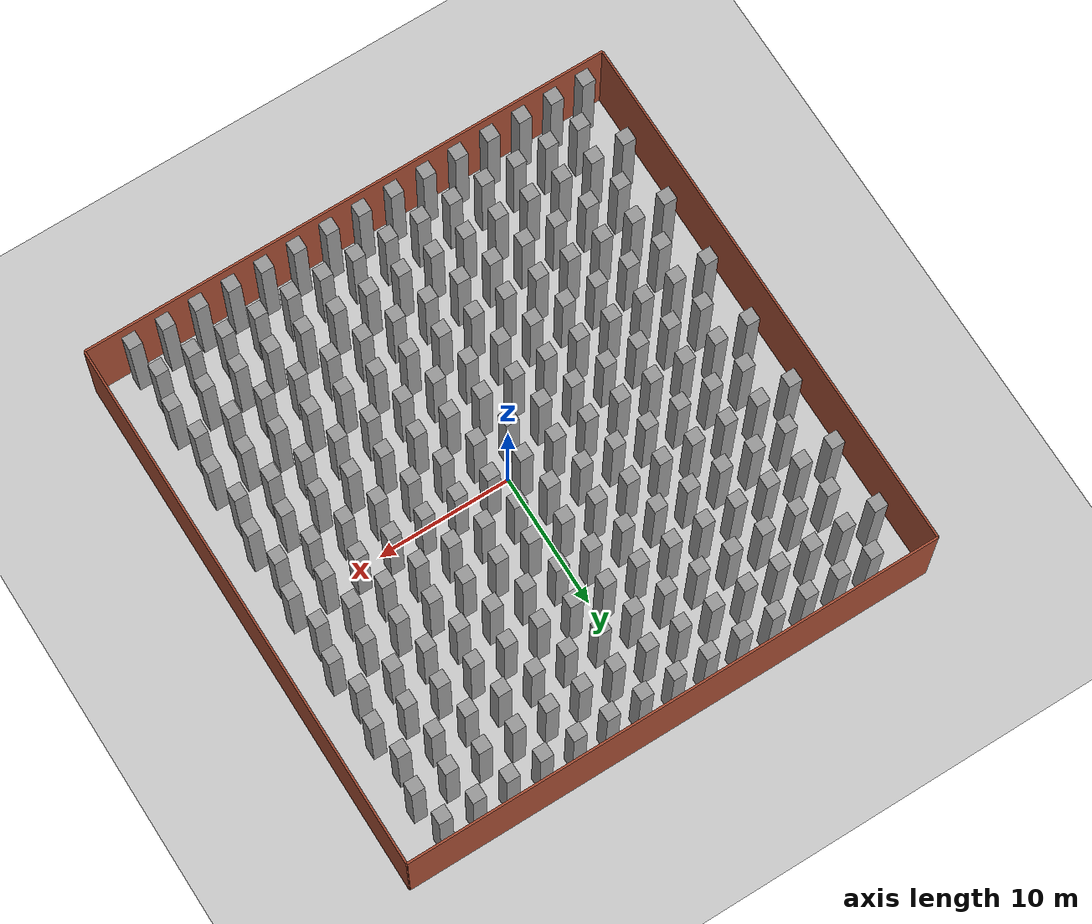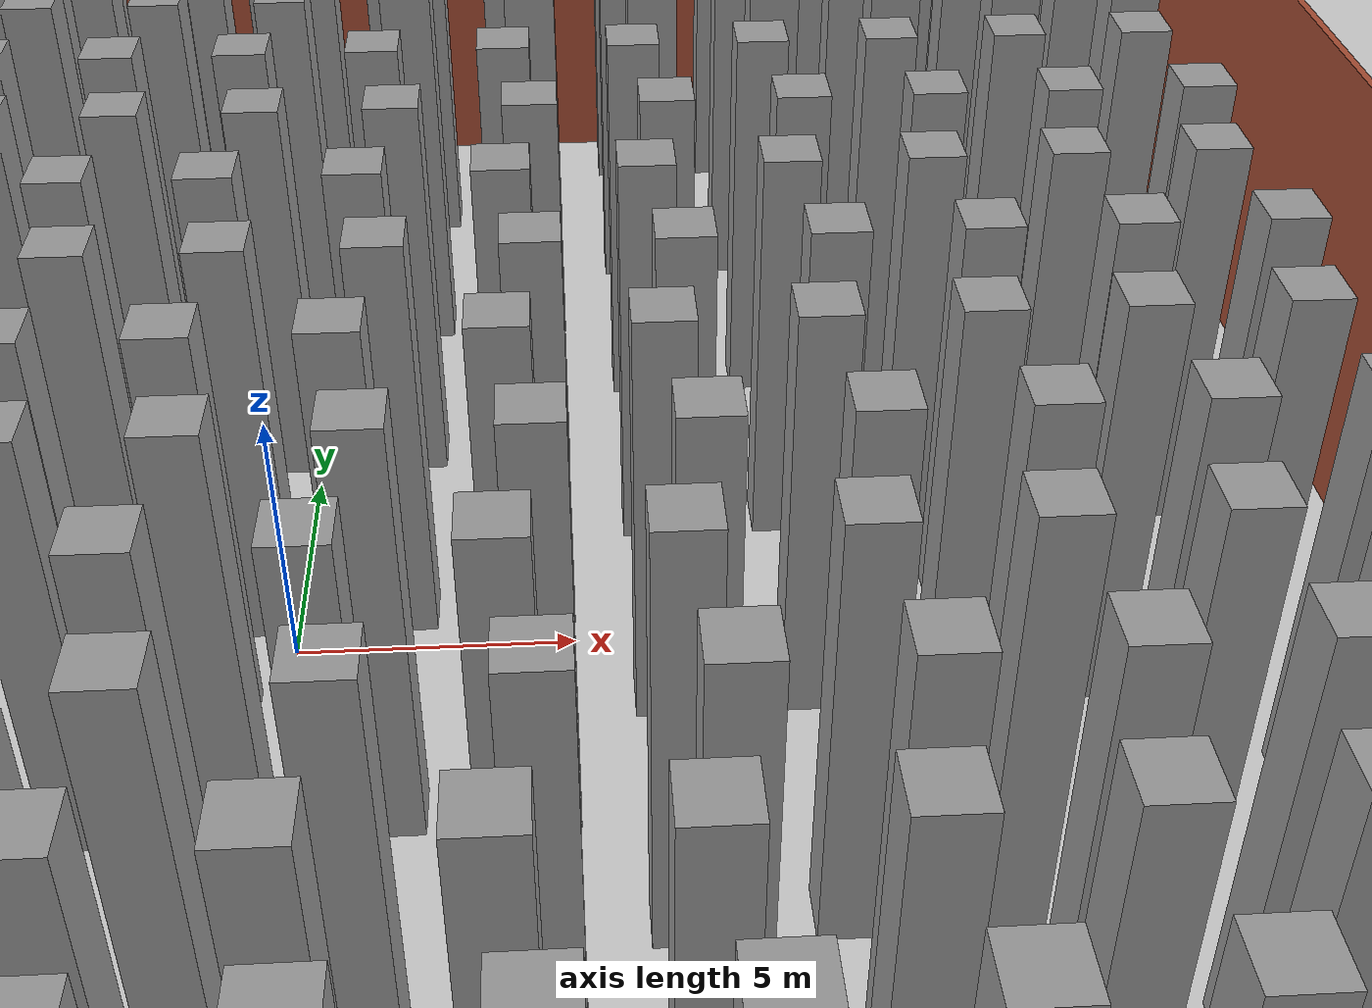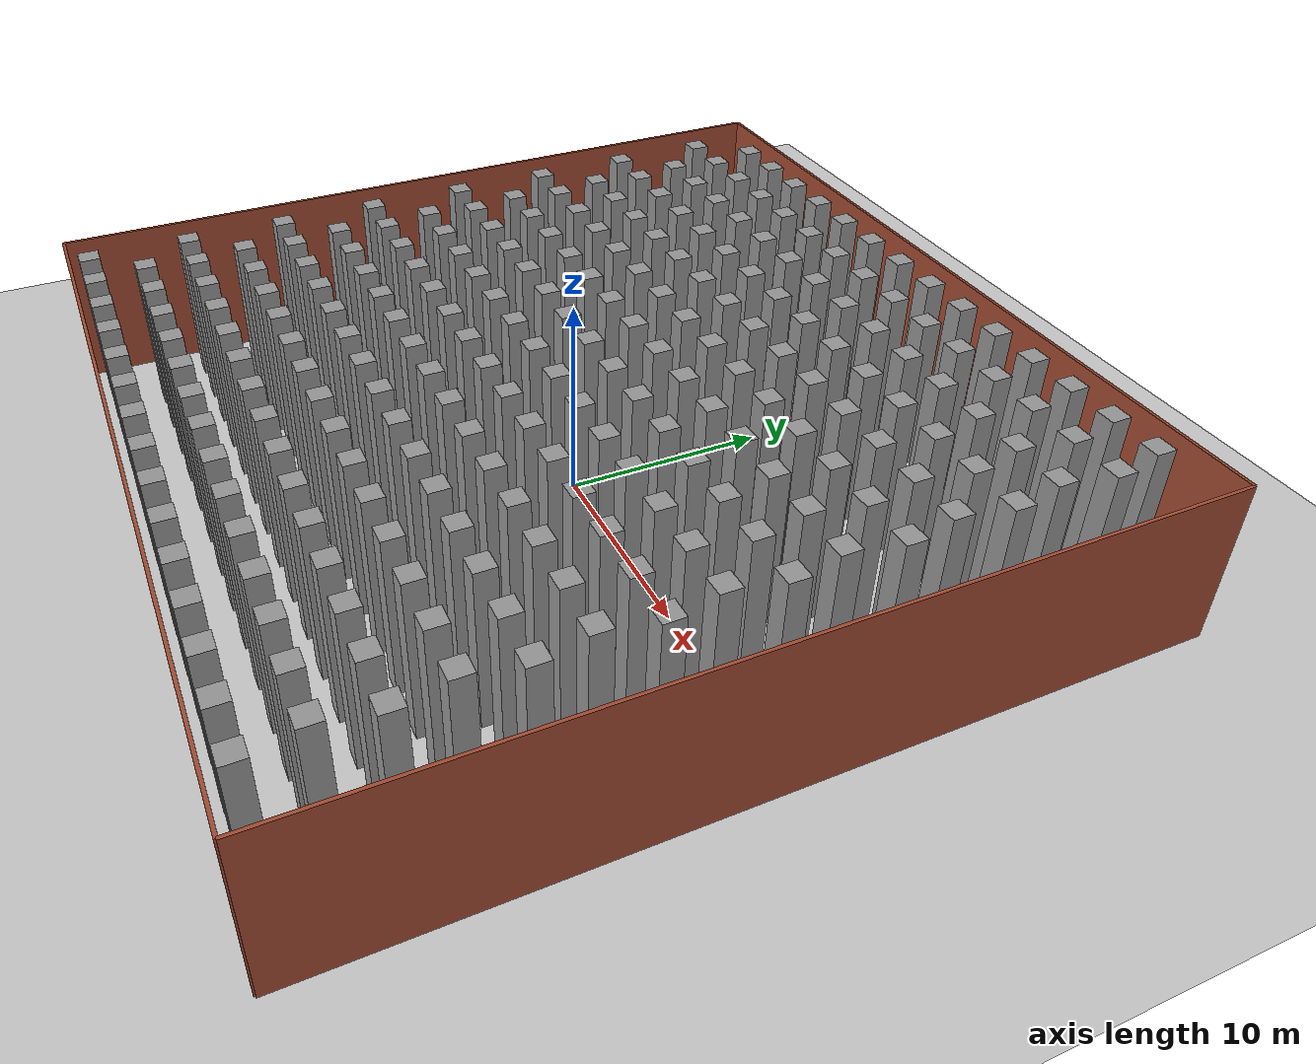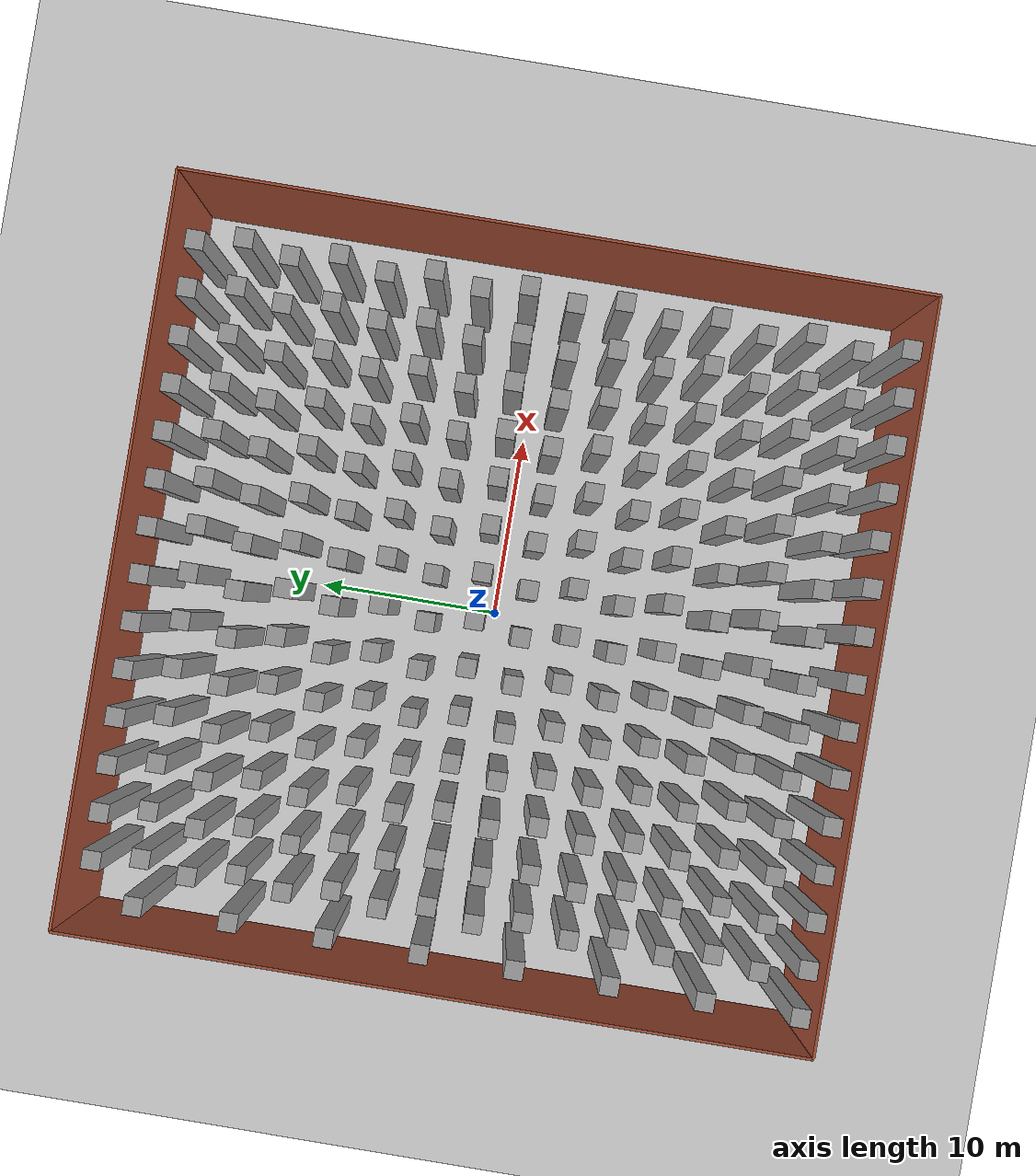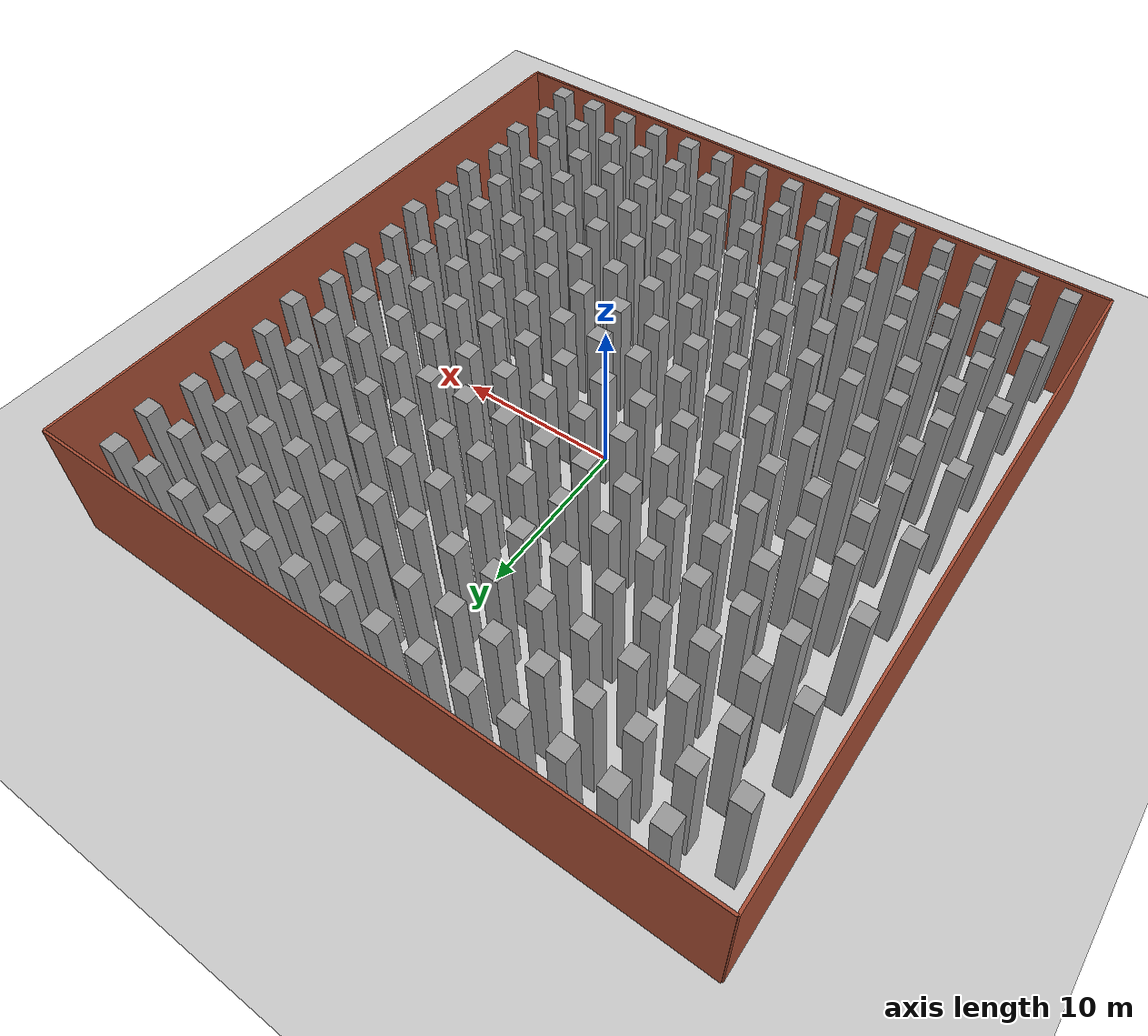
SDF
<sdf version="1.7">
 <world name="default">
  <light name="sun" type="directional">
   <pose>0 0 10 0 -0 0</pose>
   <diffuse>0.8 0.8 0.8 1</diffuse>
   <specular>0.2 0.2 0.2 1</specular>
   <attenuation>
    <range>1000</range>
    <constant>0.9</constant>
    <linear>0.01</linear>
    <quadratic>0.001</quadratic>
   </attenuation>
   <direction>-0.5 0.1 -0.9</direction>
   <spot><inner_angle>0</inner_angle><outer_angle>0</outer_angle><falloff>0</falloff></spot>
  </light>
  <model name="ground_plane">
   <static>1</static>
   <link name="link">
    <collision name="collision">
     <geometry><plane><normal>0 0 1</normal><size>100 100</size></plane></geometry>
     <surface>
      <contact><collide_bitmask>65535</collide_bitmask></contact>
      <friction><ode><mu>100</mu><mu2>50</mu2></ode></friction>
     </surface>
    </collision>
    <visual name="visual">
     <cast_shadows>0</cast_shadows>
     <geometry><plane><normal>0 0 1</normal><size>100 100</size></plane></geometry>
     <material>
      <script><uri>file://media/materials/scripts/gazebo.material</uri><name>Gazebo/Grey</name></script>
     </material>
    </visual>
   </link>
  </model>
  <gravity>0 0 -9.8</gravity>
  <magnetic_field>6e-06 2.3e-05 -4.2e-05</magnetic_field>
  <atmosphere type="adiabatic"/>
  <physics type="ode">
   <max_step_size>0.001</max_step_size>
   <real_time_factor>1</real_time_factor>
   <real_time_update_rate>1000</real_time_update_rate>
  </physics>
  <scene><ambient>0.4 0.4 0.4 1</ambient><background>0.7 0.7 0.7 1</background><shadows>1</shadows></scene>
  <spherical_coordinates>
   <surface_model>EARTH_WGS84</surface_model>
   <latitude_deg>0</latitude_deg>
   <longitude_deg>0</longitude_deg>
   <elevation>0</elevation>
   <heading_deg>0</heading_deg>
  </spherical_coordinates>
  <model name="sim_room_square">
   <link name="Wall_14">
    <collision name="Wall_14_Collision">
     <geometry><box><size>40 0.15 8</size></box></geometry>
     <pose>0 0 4 0 -0 0</pose>
    </collision>
    <visual name="Wall_14_Visual">
     <pose>0 0 4 0 -0 0</pose>
     <geometry><box><size>40 0.15 8</size></box></geometry>
     <material>
      <script><uri>file://media/materials/scripts/gazebo.material</uri><name>Gazebo/Bricks</name></script>
      <ambient>1 1 1 1</ambient>
     </material>
     <meta><layer>0</layer></meta>
    </visual>
    <pose>20 -0 0 0 -0 -1.5708</pose>
   </link>
   <link name="Wall_15">
    <collision name="Wall_15_Collision">
     <geometry><box><size>40 0.15 8</size></box></geometry>
     <pose>0 0 4 0 -0 0</pose>
    </collision>
    <visual name="Wall_15_Visual">
     <pose>0 0 4 0 -0 0</pose>
     <geometry><box><size>40 0.15 8</size></box></geometry>
     <material>
      <script><uri>file://media/materials/scripts/gazebo.material</uri><name>Gazebo/Bricks</name></script>
      <ambient>1 1 1 1</ambient>
     </material>
     <meta><layer>0</layer></meta>
    </visual>
    <pose>0 -20 0 0 -0 3.14159</pose>
   </link>
   <link name="Wall_16">
    <collision name="Wall_16_Collision">
     <geometry><box><size>40 0.15 8</size></box></geometry>
     <pose>0 0 4 0 -0 0</pose>
    </collision>
    <visual name="Wall_16_Visual">
     <pose>0 0 4 0 -0 0</pose>
     <geometry><box><size>40 0.15 8</size></box></geometry>
     <material>
      <script><uri>file://media/materials/scripts/gazebo.material</uri><name>Gazebo/Bricks</name></script>
      <ambient>1 1 1 1</ambient>
     </material>
     <meta><layer>0</layer></meta>
    </visual>
    <pose>-20 -0 0 0 -0 1.5708</pose>
   </link>
   <link name="Wall_19">
    <collision name="Wall_19_Collision">
     <geometry><box><size>40 0.15 8</size></box></geometry>
     <pose>0 0 4 0 -0 0</pose>
    </collision>
    <visual name="Wall_19_Visual">
     <pose>0 0 4 0 -0 0</pose>
     <geometry><box><size>40 0.15 8</size></box></geometry>
     <material>
      <script><uri>file://media/materials/scripts/gazebo.material</uri><name>Gazebo/Bricks</name></script>
      <ambient>1 1 1 1</ambient>
     </material>
     <meta><layer>0</layer></meta>
    </visual>
    <pose>0 20 0 0 -0 0</pose>
   </link>
   <static>1</static>
  </model>
  <model name="unit_box_static1">
   <link name="link">
    <inertial>
     <mass>1</mass>
     <inertia>
      <ixx>0.166667</ixx>
      <ixy>0</ixy>
      <ixz>0</ixz>
      <iyy>0.166667</iyy>
      <iyz>0</iyz>
      <izz>0.166667</izz>
     </inertia>
    </inertial>
    <visual name="visual">
     <geometry><box><size>1 1 8</size></box></geometry>
     <material>
      <script><name>Gazebo/Grey</name><uri>file://media/materials/scripts/gazebo.material</uri></script>
      <shader type="pixel"/>
     </material>
    </visual>
    <collision name="collision">
     <geometry><box><size>1 1 8</size></box></geometry>
     <surface>
      <friction>
       <ode><mu>1</mu><mu2>1</mu2><fdir1>0 0 0</fdir1><slip1>0</slip1><slip2>0</slip2></ode>
       <torsional>
        <coefficient>1</coefficient>
        <patch_radius>0</patch_radius>
        <surface_radius>0</surface_radius>
        <use_patch_radius>1</use_patch_radius>
        <ode><slip>0</slip></ode>
       </torsional>
      </friction>
      <bounce><restitution_coefficient>0</restitution_coefficient><threshold>1e+06</threshold></bounce>
      <contact>
       <collide_without_contact>0</collide_without_contact>
       <collide_without_contact_bitmask>1</collide_without_contact_bitmask>
       <collide_bitmask>1</collide_bitmask>
       <ode>
        <soft_cfm>0</soft_cfm>
        <soft_erp>0.2</soft_erp>
        <kp>1e+13</kp>
        <kd>1</kd>
        <max_vel>0.01</max_vel>
        <min_depth>0</min_depth>
       </ode>
       <bullet>
        <split_impulse>1</split_impulse>
        <split_impulse_penetration_threshold>-0.01</split_impulse_penetration_threshold>
        <soft_cfm>0</soft_cfm>
        <soft_erp>0.2</soft_erp>
        <kp>1e+13</kp>
        <kd>1</kd>
       </bullet>
      </contact>
     </surface>
    </collision>
   </link>
   <static>1</static>
   <pose>-18 -19 4 0 -0 0</pose>
  </model>
  <model name="unit_box_static2">
   <link name="link">
    <inertial>
     <mass>1</mass>
     <inertia>
      <ixx>0.166667</ixx>
      <ixy>0</ixy>
      <ixz>0</ixz>
      <iyy>0.166667</iyy>
      <iyz>0</iyz>
      <izz>0.166667</izz>
     </inertia>
    </inertial>
    <visual name="visual">
     <geometry><box><size>1 1 8</size></box></geometry>
     <material>
      <script><name>Gazebo/Grey</name><uri>file://media/materials/scripts/gazebo.material</uri></script>
      <shader type="pixel"/>
     </material>
    </visual>
    <collision name="collision">
     <geometry><box><size>1 1 8</size></box></geometry>
     <surface>
      <friction>
       <ode><mu>1</mu><mu2>1</mu2><fdir1>0 0 0</fdir1><slip1>0</slip1><slip2>0</slip2></ode>
       <torsional>
        <coefficient>1</coefficient>
        <patch_radius>0</patch_radius>
        <surface_radius>0</surface_radius>
        <use_patch_radius>1</use_patch_radius>
        <ode><slip>0</slip></ode>
       </torsional>
      </friction>
      <bounce><restitution_coefficient>0</restitution_coefficient><threshold>1e+06</threshold></bounce>
      <contact>
       <collide_without_contact>0</collide_without_contact>
       <collide_without_contact_bitmask>1</collide_without_contact_bitmask>
       <collide_bitmask>1</collide_bitmask>
       <ode>
        <soft_cfm>0</soft_cfm>
        <soft_erp>0.2</soft_erp>
        <kp>1e+13</kp>
        <kd>1</kd>
        <max_vel>0.01</max_vel>
        <min_depth>0</min_depth>
       </ode>
       <bullet>
        <split_impulse>1</split_impulse>
        <split_impulse_penetration_threshold>-0.01</split_impulse_penetration_threshold>
        <soft_cfm>0</soft_cfm>
        <soft_erp>0.2</soft_erp>
        <kp>1e+13</kp>
        <kd>1</kd>
       </bullet>
      </contact>
     </surface>
    </collision>
   </link>
   <static>1</static>
   <pose>-15.5 -19 4 0 -0 0</pose>
  </model>
  <model name="unit_box_static3">
   <link name="link">
    <inertial>
     <mass>1</mass>
     <inertia>
      <ixx>0.166667</ixx>
      <ixy>0</ixy>
      <ixz>0</ixz>
      <iyy>0.166667</iyy>
      <iyz>0</iyz>
      <izz>0.166667</izz>
     </inertia>
    </inertial>
    <visual name="visual">
     <geometry><box><size>1 1 8</size></box></geometry>
     <material>
      <script><name>Gazebo/Grey</name><uri>file://media/materials/scripts/gazebo.material</uri></script>
      <shader type="pixel"/>
     </material>
    </visual>
    <collision name="collision">
     <geometry><box><size>1 1 8</size></box></geometry>
     <surface>
      <friction>
       <ode><mu>1</mu><mu2>1</mu2><fdir1>0 0 0</fdir1><slip1>0</slip1><slip2>0</slip2></ode>
       <torsional>
        <coefficient>1</coefficient>
        <patch_radius>0</patch_radius>
        <surface_radius>0</surface_radius>
        <use_patch_radius>1</use_patch_radius>
        <ode><slip>0</slip></ode>
       </torsional>
      </friction>
      <bounce><restitution_coefficient>0</restitution_coefficient><threshold>1e+06</threshold></bounce>
      <contact>
       <collide_without_contact>0</collide_without_contact>
       <collide_without_contact_bitmask>1</collide_without_contact_bitmask>
       <collide_bitmask>1</collide_bitmask>
       <ode>
        <soft_cfm>0</soft_cfm>
        <soft_erp>0.2</soft_erp>
        <kp>1e+13</kp>
        <kd>1</kd>
        <max_vel>0.01</max_vel>
        <min_depth>0</min_depth>
       </ode>
       <bullet>
        <split_impulse>1</split_impulse>
        <split_impulse_penetration_threshold>-0.01</split_impulse_penetration_threshold>
        <soft_cfm>0</soft_cfm>
        <soft_erp>0.2</soft_erp>
        <kp>1e+13</kp>
        <kd>1</kd>
       </bullet>
      </contact>
     </surface>
    </collision>
   </link>
   <static>1</static>
   <pose>-13 -19 4 0 -0 0</pose>
  </model>
  <model name="unit_box_static4">
   <link name="link">
    <inertial>
     <mass>1</mass>
     <inertia>
      <ixx>0.166667</ixx>
      <ixy>0</ixy>
      <ixz>0</ixz>
      <iyy>0.166667</iyy>
      <iyz>0</iyz>
      <izz>0.166667</izz>
     </inertia>
    </inertial>
    <visual name="visual">
     <geometry><box><size>1 1 8</size></box></geometry>
     <material>
      <script><name>Gazebo/Grey</name><uri>file://media/materials/scripts/gazebo.material</uri></script>
      <shader type="pixel"/>
     </material>
    </visual>
    <collision name="collision">
     <geometry><box><size>1 1 8</size></box></geometry>
     <surface>
      <friction>
       <ode><mu>1</mu><mu2>1</mu2><fdir1>0 0 0</fdir1><slip1>0</slip1><slip2>0</slip2></ode>
       <torsional>
        <coefficient>1</coefficient>
        <patch_radius>0</patch_radius>
        <surface_radius>0</surface_radius>
        <use_patch_radius>1</use_patch_radius>
        <ode><slip>0</slip></ode>
       </torsional>
      </friction>
      <bounce><restitution_coefficient>0</restitution_coefficient><threshold>1e+06</threshold></bounce>
      <contact>
       <collide_without_contact>0</collide_without_contact>
       <collide_without_contact_bitmask>1</collide_without_contact_bitmask>
       <collide_bitmask>1</collide_bitmask>
       <ode>
        <soft_cfm>0</soft_cfm>
        <soft_erp>0.2</soft_erp>
        <kp>1e+13</kp>
        <kd>1</kd>
        <max_vel>0.01</max_vel>
        <min_depth>0</min_depth>
       </ode>
       <bullet>
        <split_impulse>1</split_impulse>
        <split_impulse_penetration_threshold>-0.01</split_impulse_penetration_threshold>
        <soft_cfm>0</soft_cfm>
        <soft_erp>0.2</soft_erp>
        <kp>1e+13</kp>
        <kd>1</kd>
       </bullet>
      </contact>
     </surface>
    </collision>
   </link>
   <static>1</static>
   <pose>-10.5 -19 4 0 -0 0</pose>
  </model>
  <model name="unit_box_static5">
   <link name="link">
    <inertial>
     <mass>1</mass>
     <inertia>
      <ixx>0.166667</ixx>
      <ixy>0</ixy>
      <ixz>0</ixz>
      <iyy>0.166667</iyy>
      <iyz>0</iyz>
      <izz>0.166667</izz>
     </inertia>
    </inertial>
    <visual name="visual">
     <geometry><box><size>1 1 8</size></box></geometry>
     <material>
      <script><name>Gazebo/Grey</name><uri>file://media/materials/scripts/gazebo.material</uri></script>
      <shader type="pixel"/>
     </material>
    </visual>
    <collision name="collision">
     <geometry><box><size>1 1 8</size></box></geometry>
     <surface>
      <friction>
       <ode><mu>1</mu><mu2>1</mu2><fdir1>0 0 0</fdir1><slip1>0</slip1><slip2>0</slip2></ode>
       <torsional>
        <coefficient>1</coefficient>
        <patch_radius>0</patch_radius>
        <surface_radius>0</surface_radius>
        <use_patch_radius>1</use_patch_radius>
        <ode><slip>0</slip></ode>
       </torsional>
      </friction>
      <bounce><restitution_coefficient>0</restitution_coefficient><threshold>1e+06</threshold></bounce>
      <contact>
       <collide_without_contact>0</collide_without_contact>
       <collide_without_contact_bitmask>1</collide_without_contact_bitmask>
       <collide_bitmask>1</collide_bitmask>
       <ode>
        <soft_cfm>0</soft_cfm>
        <soft_erp>0.2</soft_erp>
        <kp>1e+13</kp>
        <kd>1</kd>
        <max_vel>0.01</max_vel>
        <min_depth>0</min_depth>
       </ode>
       <bullet>
        <split_impulse>1</split_impulse>
        <split_impulse_penetration_threshold>-0.01</split_impulse_penetration_threshold>
        <soft_cfm>0</soft_cfm>
        <soft_erp>0.2</soft_erp>
        <kp>1e+13</kp>
        <kd>1</kd>
       </bullet>
      </contact>
     </surface>
    </collision>
   </link>
   <static>1</static>
   <pose>-8 -19 4 0 -0 0</pose>
  </model>
  <model name="unit_box_static6">
   <link name="link">
    <inertial>
     <mass>1</mass>
     <inertia>
      <ixx>0.166667</ixx>
      <ixy>0</ixy>
      <ixz>0</ixz>
      <iyy>0.166667</iyy>
      <iyz>0</iyz>
      <izz>0.166667</izz>
     </inertia>
    </inertial>
    <visual name="visual">
     <geometry><box><size>1 1 8</size></box></geometry>
     <material>
      <script><name>Gazebo/Grey</name><uri>file://media/materials/scripts/gazebo.material</uri></script>
      <shader type="pixel"/>
     </material>
    </visual>
    <collision name="collision">
     <geometry><box><size>1 1 8</size></box></geometry>
     <surface>
      <friction>
       <ode><mu>1</mu><mu2>1</mu2><fdir1>0 0 0</fdir1><slip1>0</slip1><slip2>0</slip2></ode>
       <torsional>
        <coefficient>1</coefficient>
        <patch_radius>0</patch_radius>
        <surface_radius>0</surface_radius>
        <use_patch_radius>1</use_patch_radius>
        <ode><slip>0</slip></ode>
       </torsional>
      </friction>
      <bounce><restitution_coefficient>0</restitution_coefficient><threshold>1e+06</threshold></bounce>
      <contact>
       <collide_without_contact>0</collide_without_contact>
       <collide_without_contact_bitmask>1</collide_without_contact_bitmask>
       <collide_bitmask>1</collide_bitmask>
       <ode>
        <soft_cfm>0</soft_cfm>
        <soft_erp>0.2</soft_erp>
        <kp>1e+13</kp>
        <kd>1</kd>
        <max_vel>0.01</max_vel>
        <min_depth>0</min_depth>
       </ode>
       <bullet>
        <split_impulse>1</split_impulse>
        <split_impulse_penetration_threshold>-0.01</split_impulse_penetration_threshold>
        <soft_cfm>0</soft_cfm>
        <soft_erp>0.2</soft_erp>
        <kp>1e+13</kp>
        <kd>1</kd>
       </bullet>
      </contact>
     </surface>
    </collision>
   </link>
   <static>1</static>
   <pose>-5.5 -19 4 0 -0 0</pose>
  </model>
  <model name="unit_box_static7">
   <link name="link">
    <inertial>
     <mass>1</mass>
     <inertia>
      <ixx>0.166667</ixx>
      <ixy>0</ixy>
      <ixz>0</ixz>
      <iyy>0.166667</iyy>
      <iyz>0</iyz>
      <izz>0.166667</izz>
     </inertia>
    </inertial>
    <visual name="visual">
     <geometry><box><size>1 1 8</size></box></geometry>
     <material>
      <script><name>Gazebo/Grey</name><uri>file://media/materials/scripts/gazebo.material</uri></script>
      <shader type="pixel"/>
     </material>
    </visual>
    <collision name="collision">
     <geometry><box><size>1 1 8</size></box></geometry>
     <surface>
      <friction>
       <ode><mu>1</mu><mu2>1</mu2><fdir1>0 0 0</fdir1><slip1>0</slip1><slip2>0</slip2></ode>
       <torsional>
        <coefficient>1</coefficient>
        <patch_radius>0</patch_radius>
        <surface_radius>0</surface_radius>
        <use_patch_radius>1</use_patch_radius>
        <ode><slip>0</slip></ode>
       </torsional>
      </friction>
      <bounce><restitution_coefficient>0</restitution_coefficient><threshold>1e+06</threshold></bounce>
      <contact>
       <collide_without_contact>0</collide_without_contact>
       <collide_without_contact_bitmask>1</collide_without_contact_bitmask>
       <collide_bitmask>1</collide_bitmask>
       <ode>
        <soft_cfm>0</soft_cfm>
        <soft_erp>0.2</soft_erp>
        <kp>1e+13</kp>
        <kd>1</kd>
        <max_vel>0.01</max_vel>
        <min_depth>0</min_depth>
       </ode>
       <bullet>
        <split_impulse>1</split_impulse>
        <split_impulse_penetration_threshold>-0.01</split_impulse_penetration_threshold>
        <soft_cfm>0</soft_cfm>
        <soft_erp>0.2</soft_erp>
        <kp>1e+13</kp>
        <kd>1</kd>
       </bullet>
      </contact>
     </surface>
    </collision>
   </link>
   <static>1</static>
   <pose>-3 -19 4 0 -0 0</pose>
  </model>
  <model name="unit_box_static8">
   <link name="link">
    <inertial>
     <mass>1</mass>
     <inertia>
      <ixx>0.166667</ixx>
      <ixy>0</ixy>
      <ixz>0</ixz>
      <iyy>0.166667</iyy>
      <iyz>0</iyz>
      <izz>0.166667</izz>
     </inertia>
    </inertial>
    <visual name="visual">
     <geometry><box><size>1 1 8</size></box></geometry>
     <material>
      <script><name>Gazebo/Grey</name><uri>file://media/materials/scripts/gazebo.material</uri></script>
      <shader type="pixel"/>
     </material>
    </visual>
    <collision name="collision">
     <geometry><box><size>1 1 8</size></box></geometry>
     <surface>
      <friction>
       <ode><mu>1</mu><mu2>1</mu2><fdir1>0 0 0</fdir1><slip1>0</slip1><slip2>0</slip2></ode>
       <torsional>
        <coefficient>1</coefficient>
        <patch_radius>0</patch_radius>
        <surface_radius>0</surface_radius>
        <use_patch_radius>1</use_patch_radius>
        <ode><slip>0</slip></ode>
       </torsional>
      </friction>
      <bounce><restitution_coefficient>0</restitution_coefficient><threshold>1e+06</threshold></bounce>
      <contact>
       <collide_without_contact>0</collide_without_contact>
       <collide_without_contact_bitmask>1</collide_without_contact_bitmask>
       <collide_bitmask>1</collide_bitmask>
       <ode>
        <soft_cfm>0</soft_cfm>
        <soft_erp>0.2</soft_erp>
        <kp>1e+13</kp>
        <kd>1</kd>
        <max_vel>0.01</max_vel>
        <min_depth>0</min_depth>
       </ode>
       <bullet>
        <split_impulse>1</split_impulse>
        <split_impulse_penetration_threshold>-0.01</split_impulse_penetration_threshold>
        <soft_cfm>0</soft_cfm>
        <soft_erp>0.2</soft_erp>
        <kp>1e+13</kp>
        <kd>1</kd>
       </bullet>
      </contact>
     </surface>
    </collision>
   </link>
   <static>1</static>
   <pose>-0.5 -19 4 0 -0 0</pose>
  </model>
  <model name="unit_box_static9">
   <link name="link">
    <inertial>
     <mass>1</mass>
     <inertia>
      <ixx>0.166667</ixx>
      <ixy>0</ixy>
      <ixz>0</ixz>
      <iyy>0.166667</iyy>
      <iyz>0</iyz>
      <izz>0.166667</izz>
     </inertia>
    </inertial>
    <visual name="visual">
     <geometry><box><size>1 1 8</size></box></geometry>
     <material>
      <script><name>Gazebo/Grey</name><uri>file://media/materials/scripts/gazebo.material</uri></script>
      <shader type="pixel"/>
     </material>
    </visual>
    <collision name="collision">
     <geometry><box><size>1 1 8</size></box></geometry>
     <surface>
      <friction>
       <ode><mu>1</mu><mu2>1</mu2><fdir1>0 0 0</fdir1><slip1>0</slip1><slip2>0</slip2></ode>
       <torsional>
        <coefficient>1</coefficient>
        <patch_radius>0</patch_radius>
        <surface_radius>0</surface_radius>
        <use_patch_radius>1</use_patch_radius>
        <ode><slip>0</slip></ode>
       </torsional>
      </friction>
      <bounce><restitution_coefficient>0</restitution_coefficient><threshold>1e+06</threshold></bounce>
      <contact>
       <collide_without_contact>0</collide_without_contact>
       <collide_without_contact_bitmask>1</collide_without_contact_bitmask>
       <collide_bitmask>1</collide_bitmask>
       <ode>
        <soft_cfm>0</soft_cfm>
        <soft_erp>0.2</soft_erp>
        <kp>1e+13</kp>
        <kd>1</kd>
        <max_vel>0.01</max_vel>
        <min_depth>0</min_depth>
       </ode>
       <bullet>
        <split_impulse>1</split_impulse>
        <split_impulse_penetration_threshold>-0.01</split_impulse_penetration_threshold>
        <soft_cfm>0</soft_cfm>
        <soft_erp>0.2</soft_erp>
        <kp>1e+13</kp>
        <kd>1</kd>
       </bullet>
      </contact>
     </surface>
    </collision>
   </link>
   <static>1</static>
   <pose>2 -19 4 0 -0 0</pose>
  </model>
  <model name="unit_box_static10">
   <link name="link">
    <inertial>
     <mass>1</mass>
     <inertia>
      <ixx>0.166667</ixx>
      <ixy>0</ixy>
      <ixz>0</ixz>
      <iyy>0.166667</iyy>
      <iyz>0</iyz>
      <izz>0.166667</izz>
     </inertia>
    </inertial>
    <visual name="visual">
     <geometry><box><size>1 1 8</size></box></geometry>
     <material>
      <script><name>Gazebo/Grey</name><uri>file://media/materials/scripts/gazebo.material</uri></script>
      <shader type="pixel"/>
     </material>
    </visual>
    <collision name="collision">
     <geometry><box><size>1 1 8</size></box></geometry>
     <surface>
      <friction>
       <ode><mu>1</mu><mu2>1</mu2><fdir1>0 0 0</fdir1><slip1>0</slip1><slip2>0</slip2></ode>
       <torsional>
        <coefficient>1</coefficient>
        <patch_radius>0</patch_radius>
        <surface_radius>0</surface_radius>
        <use_patch_radius>1</use_patch_radius>
        <ode><slip>0</slip></ode>
       </torsional>
      </friction>
      <bounce><restitution_coefficient>0</restitution_coefficient><threshold>1e+06</threshold></bounce>
      <contact>
       <collide_without_contact>0</collide_without_contact>
       <collide_without_contact_bitmask>1</collide_without_contact_bitmask>
       <collide_bitmask>1</collide_bitmask>
       <ode>
        <soft_cfm>0</soft_cfm>
        <soft_erp>0.2</soft_erp>
        <kp>1e+13</kp>
        <kd>1</kd>
        <max_vel>0.01</max_vel>
        <min_depth>0</min_depth>
       </ode>
       <bullet>
        <split_impulse>1</split_impulse>
        <split_impulse_penetration_threshold>-0.01</split_impulse_penetration_threshold>
        <soft_cfm>0</soft_cfm>
        <soft_erp>0.2</soft_erp>
        <kp>1e+13</kp>
        <kd>1</kd>
       </bullet>
      </contact>
     </surface>
    </collision>
   </link>
   <static>1</static>
   <pose>4.5 -19 4 0 -0 0</pose>
  </model>
  <model name="unit_box_static11">
   <link name="link">
    <inertial>
     <mass>1</mass>
     <inertia>
      <ixx>0.166667</ixx>
      <ixy>0</ixy>
      <ixz>0</ixz>
      <iyy>0.166667</iyy>
      <iyz>0</iyz>
      <izz>0.166667</izz>
     </inertia>
    </inertial>
    <visual name="visual">
     <geometry><box><size>1 1 8</size></box></geometry>
     <material>
      <script><name>Gazebo/Grey</name><uri>file://media/materials/scripts/gazebo.material</uri></script>
      <shader type="pixel"/>
     </material>
    </visual>
    <collision name="collision">
     <geometry><box><size>1 1 8</size></box></geometry>
     <surface>
      <friction>
       <ode><mu>1</mu><mu2>1</mu2><fdir1>0 0 0</fdir1><slip1>0</slip1><slip2>0</slip2></ode>
       <torsional>
        <coefficient>1</coefficient>
        <patch_radius>0</patch_radius>
        <surface_radius>0</surface_radius>
        <use_patch_radius>1</use_patch_radius>
        <ode><slip>0</slip></ode>
       </torsional>
      </friction>
      <bounce><restitution_coefficient>0</restitution_coefficient><threshold>1e+06</threshold></bounce>
      <contact>
       <collide_without_contact>0</collide_without_contact>
       <collide_without_contact_bitmask>1</collide_without_contact_bitmask>
       <collide_bitmask>1</collide_bitmask>
       <ode>
        <soft_cfm>0</soft_cfm>
        <soft_erp>0.2</soft_erp>
        <kp>1e+13</kp>
        <kd>1</kd>
        <max_vel>0.01</max_vel>
        <min_depth>0</min_depth>
       </ode>
       <bullet>
        <split_impulse>1</split_impulse>
        <split_impulse_penetration_threshold>-0.01</split_impulse_penetration_threshold>
        <soft_cfm>0</soft_cfm>
        <soft_erp>0.2</soft_erp>
        <kp>1e+13</kp>
        <kd>1</kd>
       </bullet>
      </contact>
     </surface>
    </collision>
   </link>
   <static>1</static>
   <pose>7 -19 4 0 -0 0</pose>
  </model>
  <model name="unit_box_static12">
   <link name="link">
    <inertial>
     <mass>1</mass>
     <inertia>
      <ixx>0.166667</ixx>
      <ixy>0</ixy>
      <ixz>0</ixz>
      <iyy>0.166667</iyy>
      <iyz>0</iyz>
      <izz>0.166667</izz>
     </inertia>
    </inertial>
    <visual name="visual">
     <geometry><box><size>1 1 8</size></box></geometry>
     <material>
      <script><name>Gazebo/Grey</name><uri>file://media/materials/scripts/gazebo.material</uri></script>
      <shader type="pixel"/>
     </material>
    </visual>
    <collision name="collision">
     <geometry><box><size>1 1 8</size></box></geometry>
     <surface>
      <friction>
       <ode><mu>1</mu><mu2>1</mu2><fdir1>0 0 0</fdir1><slip1>0</slip1><slip2>0</slip2></ode>
       <torsional>
        <coefficient>1</coefficient>
        <patch_radius>0</patch_radius>
        <surface_radius>0</surface_radius>
        <use_patch_radius>1</use_patch_radius>
        <ode><slip>0</slip></ode>
       </torsional>
      </friction>
      <bounce><restitution_coefficient>0</restitution_coefficient><threshold>1e+06</threshold></bounce>
      <contact>
       <collide_without_contact>0</collide_without_contact>
       <collide_without_contact_bitmask>1</collide_without_contact_bitmask>
       <collide_bitmask>1</collide_bitmask>
       <ode>
        <soft_cfm>0</soft_cfm>
        <soft_erp>0.2</soft_erp>
        <kp>1e+13</kp>
        <kd>1</kd>
        <max_vel>0.01</max_vel>
        <min_depth>0</min_depth>
       </ode>
       <bullet>
        <split_impulse>1</split_impulse>
        <split_impulse_penetration_threshold>-0.01</split_impulse_penetration_threshold>
        <soft_cfm>0</soft_cfm>
        <soft_erp>0.2</soft_erp>
        <kp>1e+13</kp>
        <kd>1</kd>
       </bullet>
      </contact>
     </surface>
    </collision>
   </link>
   <static>1</static>
   <pose>9.5 -19 4 0 -0 0</pose>
  </model>
  <model name="unit_box_static13">
   <link name="link">
    <inertial>
     <mass>1</mass>
     <inertia>
      <ixx>0.166667</ixx>
      <ixy>0</ixy>
      <ixz>0</ixz>
      <iyy>0.166667</iyy>
      <iyz>0</iyz>
      <izz>0.166667</izz>
     </inertia>
    </inertial>
    <visual name="visual">
     <geometry><box><size>1 1 8</size></box></geometry>
     <material>
      <script><name>Gazebo/Grey</name><uri>file://media/materials/scripts/gazebo.material</uri></script>
      <shader type="pixel"/>
     </material>
    </visual>
    <collision name="collision">
     <geometry><box><size>1 1 8</size></box></geometry>
     <surface>
      <friction>
       <ode><mu>1</mu><mu2>1</mu2><fdir1>0 0 0</fdir1><slip1>0</slip1><slip2>0</slip2></ode>
       <torsional>
        <coefficient>1</coefficient>
        <patch_radius>0</patch_radius>
        <surface_radius>0</surface_radius>
        <use_patch_radius>1</use_patch_radius>
        <ode><slip>0</slip></ode>
       </torsional>
      </friction>
      <bounce><restitution_coefficient>0</restitution_coefficient><threshold>1e+06</threshold></bounce>
      <contact>
       <collide_without_contact>0</collide_without_contact>
       <collide_without_contact_bitmask>1</collide_without_contact_bitmask>
       <collide_bitmask>1</collide_bitmask>
       <ode>
        <soft_cfm>0</soft_cfm>
        <soft_erp>0.2</soft_erp>
        <kp>1e+13</kp>
        <kd>1</kd>
        <max_vel>0.01</max_vel>
        <min_depth>0</min_depth>
       </ode>
       <bullet>
        <split_impulse>1</split_impulse>
        <split_impulse_penetration_threshold>-0.01</split_impulse_penetration_threshold>
        <soft_cfm>0</soft_cfm>
        <soft_erp>0.2</soft_erp>
        <kp>1e+13</kp>
        <kd>1</kd>
       </bullet>
      </contact>
     </surface>
    </collision>
   </link>
   <static>1</static>
   <pose>12 -19 4 0 -0 0</pose>
  </model>
  <model name="unit_box_static14">
   <link name="link">
    <inertial>
     <mass>1</mass>
     <inertia>
      <ixx>0.166667</ixx>
      <ixy>0</ixy>
      <ixz>0</ixz>
      <iyy>0.166667</iyy>
      <iyz>0</iyz>
      <izz>0.166667</izz>
     </inertia>
    </inertial>
    <visual name="visual">
     <geometry><box><size>1 1 8</size></box></geometry>
     <material>
      <script><name>Gazebo/Grey</name><uri>file://media/materials/scripts/gazebo.material</uri></script>
      <shader type="pixel"/>
     </material>
    </visual>
    <collision name="collision">
     <geometry><box><size>1 1 8</size></box></geometry>
     <surface>
      <friction>
       <ode><mu>1</mu><mu2>1</mu2><fdir1>0 0 0</fdir1><slip1>0</slip1><slip2>0</slip2></ode>
       <torsional>
        <coefficient>1</coefficient>
        <patch_radius>0</patch_radius>
        <surface_radius>0</surface_radius>
        <use_patch_radius>1</use_patch_radius>
        <ode><slip>0</slip></ode>
       </torsional>
      </friction>
      <bounce><restitution_coefficient>0</restitution_coefficient><threshold>1e+06</threshold></bounce>
      <contact>
       <collide_without_contact>0</collide_without_contact>
       <collide_without_contact_bitmask>1</collide_without_contact_bitmask>
       <collide_bitmask>1</collide_bitmask>
       <ode>
        <soft_cfm>0</soft_cfm>
        <soft_erp>0.2</soft_erp>
        <kp>1e+13</kp>
        <kd>1</kd>
        <max_vel>0.01</max_vel>
        <min_depth>0</min_depth>
       </ode>
       <bullet>
        <split_impulse>1</split_impulse>
        <split_impulse_penetration_threshold>-0.01</split_impulse_penetration_threshold>
        <soft_cfm>0</soft_cfm>
        <soft_erp>0.2</soft_erp>
        <kp>1e+13</kp>
        <kd>1</kd>
       </bullet>
      </contact>
     </surface>
    </collision>
   </link>
   <static>1</static>
   <pose>14.5 -19 4 0 -0 0</pose>
  </model>
  <model name="unit_box_static15">
   <link name="link">
    <inertial>
     <mass>1</mass>
     <inertia>
      <ixx>0.166667</ixx>
      <ixy>0</ixy>
      <ixz>0</ixz>
      <iyy>0.166667</iyy>
      <iyz>0</iyz>
      <izz>0.166667</izz>
     </inertia>
    </inertial>
    <visual name="visual">
     <geometry><box><size>1 1 8</size></box></geometry>
     <material>
      <script><name>Gazebo/Grey</name><uri>file://media/materials/scripts/gazebo.material</uri></script>
      <shader type="pixel"/>
     </material>
    </visual>
    <collision name="collision">
     <geometry><box><size>1 1 8</size></box></geometry>
     <surface>
      <friction>
       <ode><mu>1</mu><mu2>1</mu2><fdir1>0 0 0</fdir1><slip1>0</slip1><slip2>0</slip2></ode>
       <torsional>
        <coefficient>1</coefficient>
        <patch_radius>0</patch_radius>
        <surface_radius>0</surface_radius>
        <use_patch_radius>1</use_patch_radius>
        <ode><slip>0</slip></ode>
       </torsional>
      </friction>
      <bounce><restitution_coefficient>0</restitution_coefficient><threshold>1e+06</threshold></bounce>
      <contact>
       <collide_without_contact>0</collide_without_contact>
       <collide_without_contact_bitmask>1</collide_without_contact_bitmask>
       <collide_bitmask>1</collide_bitmask>
       <ode>
        <soft_cfm>0</soft_cfm>
        <soft_erp>0.2</soft_erp>
        <kp>1e+13</kp>
        <kd>1</kd>
        <max_vel>0.01</max_vel>
        <min_depth>0</min_depth>
       </ode>
       <bullet>
        <split_impulse>1</split_impulse>
        <split_impulse_penetration_threshold>-0.01</split_impulse_penetration_threshold>
        <soft_cfm>0</soft_cfm>
        <soft_erp>0.2</soft_erp>
        <kp>1e+13</kp>
        <kd>1</kd>
       </bullet>
      </contact>
     </surface>
    </collision>
   </link>
   <static>1</static>
   <pose>17 -19 4 0 -0 0</pose>
  </model>
  <model name="unit_box_static16">
   <link name="link">
    <inertial>
     <mass>1</mass>
     <inertia>
      <ixx>0.166667</ixx>
      <ixy>0</ixy>
      <ixz>0</ixz>
      <iyy>0.166667</iyy>
      <iyz>0</iyz>
      <izz>0.166667</izz>
     </inertia>
    </inertial>
    <visual name="visual">
     <geometry><box><size>1 1 8</size></box></geometry>
     <material>
      <script><name>Gazebo/Grey</name><uri>file://media/materials/scripts/gazebo.material</uri></script>
      <shader type="pixel"/>
     </material>
    </visual>
    <collision name="collision">
     <geometry><box><size>1 1 8</size></box></geometry>
     <surface>
      <friction>
       <ode><mu>1</mu><mu2>1</mu2><fdir1>0 0 0</fdir1><slip1>0</slip1><slip2>0</slip2></ode>
       <torsional>
        <coefficient>1</coefficient>
        <patch_radius>0</patch_radius>
        <surface_radius>0</surface_radius>
        <use_patch_radius>1</use_patch_radius>
        <ode><slip>0</slip></ode>
       </torsional>
      </friction>
      <bounce><restitution_coefficient>0</restitution_coefficient><threshold>1e+06</threshold></bounce>
      <contact>
       <collide_without_contact>0</collide_without_contact>
       <collide_without_contact_bitmask>1</collide_without_contact_bitmask>
       <collide_bitmask>1</collide_bitmask>
       <ode>
        <soft_cfm>0</soft_cfm>
        <soft_erp>0.2</soft_erp>
        <kp>1e+13</kp>
        <kd>1</kd>
        <max_vel>0.01</max_vel>
        <min_depth>0</min_depth>
       </ode>
       <bullet>
        <split_impulse>1</split_impulse>
        <split_impulse_penetration_threshold>-0.01</split_impulse_penetration_threshold>
        <soft_cfm>0</soft_cfm>
        <soft_erp>0.2</soft_erp>
        <kp>1e+13</kp>
        <kd>1</kd>
       </bullet>
      </contact>
     </surface>
    </collision>
   </link>
   <static>1</static>
   <pose>-16 -16.5 4 0 -0 0</pose>
  </model>
  <model name="unit_box_static17">
   <link name="link">
    <inertial>
     <mass>1</mass>
     <inertia>
      <ixx>0.166667</ixx>
      <ixy>0</ixy>
      <ixz>0</ixz>
      <iyy>0.166667</iyy>
      <iyz>0</iyz>
      <izz>0.166667</izz>
     </inertia>
    </inertial>
    <visual name="visual">
     <geometry><box><size>1 1 8</size></box></geometry>
     <material>
      <script><name>Gazebo/Grey</name><uri>file://media/materials/scripts/gazebo.material</uri></script>
      <shader type="pixel"/>
     </material>
    </visual>
    <collision name="collision">
     <geometry><box><size>1 1 8</size></box></geometry>
     <surface>
      <friction>
       <ode><mu>1</mu><mu2>1</mu2><fdir1>0 0 0</fdir1><slip1>0</slip1><slip2>0</slip2></ode>
       <torsional>
        <coefficient>1</coefficient>
        <patch_radius>0</patch_radius>
        <surface_radius>0</surface_radius>
        <use_patch_radius>1</use_patch_radius>
        <ode><slip>0</slip></ode>
       </torsional>
      </friction>
      <bounce><restitution_coefficient>0</restitution_coefficient><threshold>1e+06</threshold></bounce>
      <contact>
       <collide_without_contact>0</collide_without_contact>
       <collide_without_contact_bitmask>1</collide_without_contact_bitmask>
       <collide_bitmask>1</collide_bitmask>
       <ode>
        <soft_cfm>0</soft_cfm>
        <soft_erp>0.2</soft_erp>
        <kp>1e+13</kp>
        <kd>1</kd>
        <max_vel>0.01</max_vel>
        <min_depth>0</min_depth>
       </ode>
       <bullet>
        <split_impulse>1</split_impulse>
        <split_impulse_penetration_threshold>-0.01</split_impulse_penetration_threshold>
        <soft_cfm>0</soft_cfm>
        <soft_erp>0.2</soft_erp>
        <kp>1e+13</kp>
        <kd>1</kd>
       </bullet>
      </contact>
     </surface>
    </collision>
   </link>
   <static>1</static>
   <pose>-13.5 -16.5 4 0 -0 0</pose>
  </model>
  <model name="unit_box_static18">
   <link name="link">
    <inertial>
     <mass>1</mass>
     <inertia>
      <ixx>0.166667</ixx>
      <ixy>0</ixy>
      <ixz>0</ixz>
      <iyy>0.166667</iyy>
      <iyz>0</iyz>
      <izz>0.166667</izz>
     </inertia>
    </inertial>
    <visual name="visual">
     <geometry><box><size>1 1 8</size></box></geometry>
     <material>
      <script><name>Gazebo/Grey</name><uri>file://media/materials/scripts/gazebo.material</uri></script>
      <shader type="pixel"/>
     </material>
    </visual>
    <collision name="collision">
     <geometry><box><size>1 1 8</size></box></geometry>
     <surface>
      <friction>
       <ode><mu>1</mu><mu2>1</mu2><fdir1>0 0 0</fdir1><slip1>0</slip1><slip2>0</slip2></ode>
       <torsional>
        <coefficient>1</coefficient>
        <patch_radius>0</patch_radius>
        <surface_radius>0</surface_radius>
        <use_patch_radius>1</use_patch_radius>
        <ode><slip>0</slip></ode>
       </torsional>
      </friction>
      <bounce><restitution_coefficient>0</restitution_coefficient><threshold>1e+06</threshold></bounce>
      <contact>
       <collide_without_contact>0</collide_without_contact>
       <collide_without_contact_bitmask>1</collide_without_contact_bitmask>
       <collide_bitmask>1</collide_bitmask>
       <ode>
        <soft_cfm>0</soft_cfm>
        <soft_erp>0.2</soft_erp>
        <kp>1e+13</kp>
        <kd>1</kd>
        <max_vel>0.01</max_vel>
        <min_depth>0</min_depth>
       </ode>
       <bullet>
        <split_impulse>1</split_impulse>
        <split_impulse_penetration_threshold>-0.01</split_impulse_penetration_threshold>
        <soft_cfm>0</soft_cfm>
        <soft_erp>0.2</soft_erp>
        <kp>1e+13</kp>
        <kd>1</kd>
       </bullet>
      </contact>
     </surface>
    </collision>
   </link>
   <static>1</static>
   <pose>-11 -16.5 4 0 -0 0</pose>
  </model>
  <model name="unit_box_static19">
   <link name="link">
    <inertial>
     <mass>1</mass>
     <inertia>
      <ixx>0.166667</ixx>
      <ixy>0</ixy>
      <ixz>0</ixz>
      <iyy>0.166667</iyy>
      <iyz>0</iyz>
      <izz>0.166667</izz>
     </inertia>
    </inertial>
    <visual name="visual">
     <geometry><box><size>1 1 8</size></box></geometry>
     <material>
      <script><name>Gazebo/Grey</name><uri>file://media/materials/scripts/gazebo.material</uri></script>
      <shader type="pixel"/>
     </material>
    </visual>
    <collision name="collision">
     <geometry><box><size>1 1 8</size></box></geometry>
     <surface>
      <friction>
       <ode><mu>1</mu><mu2>1</mu2><fdir1>0 0 0</fdir1><slip1>0</slip1><slip2>0</slip2></ode>
       <torsional>
        <coefficient>1</coefficient>
        <patch_radius>0</patch_radius>
        <surface_radius>0</surface_radius>
        <use_patch_radius>1</use_patch_radius>
        <ode><slip>0</slip></ode>
       </torsional>
      </friction>
      <bounce><restitution_coefficient>0</restitution_coefficient><threshold>1e+06</threshold></bounce>
      <contact>
       <collide_without_contact>0</collide_without_contact>
       <collide_without_contact_bitmask>1</collide_without_contact_bitmask>
       <collide_bitmask>1</collide_bitmask>
       <ode>
        <soft_cfm>0</soft_cfm>
        <soft_erp>0.2</soft_erp>
        <kp>1e+13</kp>
        <kd>1</kd>
        <max_vel>0.01</max_vel>
        <min_depth>0</min_depth>
       </ode>
       <bullet>
        <split_impulse>1</split_impulse>
        <split_impulse_penetration_threshold>-0.01</split_impulse_penetration_threshold>
        <soft_cfm>0</soft_cfm>
        <soft_erp>0.2</soft_erp>
        <kp>1e+13</kp>
        <kd>1</kd>
       </bullet>
      </contact>
     </surface>
    </collision>
   </link>
   <static>1</static>
   <pose>-8.5 -16.5 4 0 -0 0</pose>
  </model>
  <model name="unit_box_static20">
   <link name="link">
    <inertial>
     <mass>1</mass>
     <inertia>
      <ixx>0.166667</ixx>
      <ixy>0</ixy>
      <ixz>0</ixz>
      <iyy>0.166667</iyy>
      <iyz>0</iyz>
      <izz>0.166667</izz>
     </inertia>
    </inertial>
    <visual name="visual">
     <geometry><box><size>1 1 8</size></box></geometry>
     <material>
      <script><name>Gazebo/Grey</name><uri>file://media/materials/scripts/gazebo.material</uri></script>
      <shader type="pixel"/>
     </material>
    </visual>
    <collision name="collision">
     <geometry><box><size>1 1 8</size></box></geometry>
     <surface>
      <friction>
       <ode><mu>1</mu><mu2>1</mu2><fdir1>0 0 0</fdir1><slip1>0</slip1><slip2>0</slip2></ode>
       <torsional>
        <coefficient>1</coefficient>
        <patch_radius>0</patch_radius>
        <surface_radius>0</surface_radius>
        <use_patch_radius>1</use_patch_radius>
        <ode><slip>0</slip></ode>
       </torsional>
      </friction>
      <bounce><restitution_coefficient>0</restitution_coefficient><threshold>1e+06</threshold></bounce>
      <contact>
       <collide_without_contact>0</collide_without_contact>
       <collide_without_contact_bitmask>1</collide_without_contact_bitmask>
       <collide_bitmask>1</collide_bitmask>
       <ode>
        <soft_cfm>0</soft_cfm>
        <soft_erp>0.2</soft_erp>
        <kp>1e+13</kp>
        <kd>1</kd>
        <max_vel>0.01</max_vel>
        <min_depth>0</min_depth>
       </ode>
       <bullet>
        <split_impulse>1</split_impulse>
        <split_impulse_penetration_threshold>-0.01</split_impulse_penetration_threshold>
        <soft_cfm>0</soft_cfm>
        <soft_erp>0.2</soft_erp>
        <kp>1e+13</kp>
        <kd>1</kd>
       </bullet>
      </contact>
     </surface>
    </collision>
   </link>
   <static>1</static>
   <pose>-6 -16.5 4 0 -0 0</pose>
  </model>
  <model name="unit_box_static21">
   <link name="link">
    <inertial>
     <mass>1</mass>
     <inertia>
      <ixx>0.166667</ixx>
      <ixy>0</ixy>
      <ixz>0</ixz>
      <iyy>0.166667</iyy>
      <iyz>0</iyz>
      <izz>0.166667</izz>
     </inertia>
    </inertial>
    <visual name="visual">
     <geometry><box><size>1 1 8</size></box></geometry>
     <material>
      <script><name>Gazebo/Grey</name><uri>file://media/materials/scripts/gazebo.material</uri></script>
      <shader type="pixel"/>
     </material>
    </visual>
    <collision name="collision">
     <geometry><box><size>1 1 8</size></box></geometry>
     <surface>
      <friction>
       <ode><mu>1</mu><mu2>1</mu2><fdir1>0 0 0</fdir1><slip1>0</slip1><slip2>0</slip2></ode>
       <torsional>
        <coefficient>1</coefficient>
        <patch_radius>0</patch_radius>
        <surface_radius>0</surface_radius>
        <use_patch_radius>1</use_patch_radius>
        <ode><slip>0</slip></ode>
       </torsional>
      </friction>
      <bounce><restitution_coefficient>0</restitution_coefficient><threshold>1e+06</threshold></bounce>
      <contact>
       <collide_without_contact>0</collide_without_contact>
       <collide_without_contact_bitmask>1</collide_without_contact_bitmask>
       <collide_bitmask>1</collide_bitmask>
       <ode>
        <soft_cfm>0</soft_cfm>
        <soft_erp>0.2</soft_erp>
        <kp>1e+13</kp>
        <kd>1</kd>
        <max_vel>0.01</max_vel>
        <min_depth>0</min_depth>
       </ode>
       <bullet>
        <split_impulse>1</split_impulse>
        <split_impulse_penetration_threshold>-0.01</split_impulse_penetration_threshold>
        <soft_cfm>0</soft_cfm>
        <soft_erp>0.2</soft_erp>
        <kp>1e+13</kp>
        <kd>1</kd>
       </bullet>
      </contact>
     </surface>
    </collision>
   </link>
   <static>1</static>
   <pose>-3.5 -16.5 4 0 -0 0</pose>
  </model>
  <model name="unit_box_static22">
   <link name="link">
    <inertial>
     <mass>1</mass>
     <inertia>
      <ixx>0.166667</ixx>
      <ixy>0</ixy>
      <ixz>0</ixz>
      <iyy>0.166667</iyy>
      <iyz>0</iyz>
      <izz>0.166667</izz>
     </inertia>
    </inertial>
    <visual name="visual">
     <geometry><box><size>1 1 8</size></box></geometry>
     <material>
      <script><name>Gazebo/Grey</name><uri>file://media/materials/scripts/gazebo.material</uri></script>
      <shader type="pixel"/>
     </material>
    </visual>
    <collision name="collision">
     <geometry><box><size>1 1 8</size></box></geometry>
     <surface>
      <friction>
       <ode><mu>1</mu><mu2>1</mu2><fdir1>0 0 0</fdir1><slip1>0</slip1><slip2>0</slip2></ode>
       <torsional>
        <coefficient>1</coefficient>
        <patch_radius>0</patch_radius>
        <surface_radius>0</surface_radius>
        <use_patch_radius>1</use_patch_radius>
        <ode><slip>0</slip></ode>
       </torsional>
      </friction>
      <bounce><restitution_coefficient>0</restitution_coefficient><threshold>1e+06</threshold></bounce>
      <contact>
       <collide_without_contact>0</collide_without_contact>
       <collide_without_contact_bitmask>1</collide_without_contact_bitmask>
       <collide_bitmask>1</collide_bitmask>
       <ode>
        <soft_cfm>0</soft_cfm>
        <soft_erp>0.2</soft_erp>
        <kp>1e+13</kp>
        <kd>1</kd>
        <max_vel>0.01</max_vel>
        <min_depth>0</min_depth>
       </ode>
       <bullet>
        <split_impulse>1</split_impulse>
        <split_impulse_penetration_threshold>-0.01</split_impulse_penetration_threshold>
        <soft_cfm>0</soft_cfm>
        <soft_erp>0.2</soft_erp>
        <kp>1e+13</kp>
        <kd>1</kd>
       </bullet>
      </contact>
     </surface>
    </collision>
   </link>
   <static>1</static>
   <pose>-1 -16.5 4 0 -0 0</pose>
  </model>
  <model name="unit_box_static23">
   <link name="link">
    <inertial>
     <mass>1</mass>
     <inertia>
      <ixx>0.166667</ixx>
      <ixy>0</ixy>
      <ixz>0</ixz>
      <iyy>0.166667</iyy>
      <iyz>0</iyz>
      <izz>0.166667</izz>
     </inertia>
    </inertial>
    <visual name="visual">
     <geometry><box><size>1 1 8</size></box></geometry>
     <material>
      <script><name>Gazebo/Grey</name><uri>file://media/materials/scripts/gazebo.material</uri></script>
      <shader type="pixel"/>
     </material>
    </visual>
    <collision name="collision">
     <geometry><box><size>1 1 8</size></box></geometry>
     <surface>
      <friction>
       <ode><mu>1</mu><mu2>1</mu2><fdir1>0 0 0</fdir1><slip1>0</slip1><slip2>0</slip2></ode>
       <torsional>
        <coefficient>1</coefficient>
        <patch_radius>0</patch_radius>
        <surface_radius>0</surface_radius>
        <use_patch_radius>1</use_patch_radius>
        <ode><slip>0</slip></ode>
       </torsional>
      </friction>
      <bounce><restitution_coefficient>0</restitution_coefficient><threshold>1e+06</threshold></bounce>
      <contact>
       <collide_without_contact>0</collide_without_contact>
       <collide_without_contact_bitmask>1</collide_without_contact_bitmask>
       <collide_bitmask>1</collide_bitmask>
       <ode>
        <soft_cfm>0</soft_cfm>
        <soft_erp>0.2</soft_erp>
        <kp>1e+13</kp>
        <kd>1</kd>
        <max_vel>0.01</max_vel>
        <min_depth>0</min_depth>
       </ode>
       <bullet>
        <split_impulse>1</split_impulse>
        <split_impulse_penetration_threshold>-0.01</split_impulse_penetration_threshold>
        <soft_cfm>0</soft_cfm>
        <soft_erp>0.2</soft_erp>
        <kp>1e+13</kp>
        <kd>1</kd>
       </bullet>
      </contact>
     </surface>
    </collision>
   </link>
   <static>1</static>
   <pose>1.5 -16.5 4 0 -0 0</pose>
  </model>
  <model name="unit_box_static24">
   <link name="link">
    <inertial>
     <mass>1</mass>
     <inertia>
      <ixx>0.166667</ixx>
      <ixy>0</ixy>
      <ixz>0</ixz>
      <iyy>0.166667</iyy>
      <iyz>0</iyz>
      <izz>0.166667</izz>
     </inertia>
    </inertial>
    <visual name="visual">
     <geometry><box><size>1 1 8</size></box></geometry>
     <material>
      <script><name>Gazebo/Grey</name><uri>file://media/materials/scripts/gazebo.material</uri></script>
      <shader type="pixel"/>
     </material>
    </visual>
    <collision name="collision">
     <geometry><box><size>1 1 8</size></box></geometry>
     <surface>
      <friction>
       <ode><mu>1</mu><mu2>1</mu2><fdir1>0 0 0</fdir1><slip1>0</slip1><slip2>0</slip2></ode>
       <torsional>
        <coefficient>1</coefficient>
        <patch_radius>0</patch_radius>
        <surface_radius>0</surface_radius>
        <use_patch_radius>1</use_patch_radius>
        <ode><slip>0</slip></ode>
       </torsional>
      </friction>
      <bounce><restitution_coefficient>0</restitution_coefficient><threshold>1e+06</threshold></bounce>
      <contact>
       <collide_without_contact>0</collide_without_contact>
       <collide_without_contact_bitmask>1</collide_without_contact_bitmask>
       <collide_bitmask>1</collide_bitmask>
       <ode>
        <soft_cfm>0</soft_cfm>
        <soft_erp>0.2</soft_erp>
        <kp>1e+13</kp>
        <kd>1</kd>
        <max_vel>0.01</max_vel>
        <min_depth>0</min_depth>
       </ode>
       <bullet>
        <split_impulse>1</split_impulse>
        <split_impulse_penetration_threshold>-0.01</split_impulse_penetration_threshold>
        <soft_cfm>0</soft_cfm>
        <soft_erp>0.2</soft_erp>
        <kp>1e+13</kp>
        <kd>1</kd>
       </bullet>
      </contact>
     </surface>
    </collision>
   </link>
   <static>1</static>
   <pose>4 -16.5 4 0 -0 0</pose>
  </model>
  <model name="unit_box_static25">
   <link name="link">
    <inertial>
     <mass>1</mass>
     <inertia>
      <ixx>0.166667</ixx>
      <ixy>0</ixy>
      <ixz>0</ixz>
      <iyy>0.166667</iyy>
      <iyz>0</iyz>
      <izz>0.166667</izz>
     </inertia>
    </inertial>
    <visual name="visual">
     <geometry><box><size>1 1 8</size></box></geometry>
     <material>
      <script><name>Gazebo/Grey</name><uri>file://media/materials/scripts/gazebo.material</uri></script>
      <shader type="pixel"/>
     </material>
    </visual>
    <collision name="collision">
     <geometry><box><size>1 1 8</size></box></geometry>
     <surface>
      <friction>
       <ode><mu>1</mu><mu2>1</mu2><fdir1>0 0 0</fdir1><slip1>0</slip1><slip2>0</slip2></ode>
       <torsional>
        <coefficient>1</coefficient>
        <patch_radius>0</patch_radius>
        <surface_radius>0</surface_radius>
        <use_patch_radius>1</use_patch_radius>
        <ode><slip>0</slip></ode>
       </torsional>
      </friction>
      <bounce><restitution_coefficient>0</restitution_coefficient><threshold>1e+06</threshold></bounce>
      <contact>
       <collide_without_contact>0</collide_without_contact>
       <collide_without_contact_bitmask>1</collide_without_contact_bitmask>
       <collide_bitmask>1</collide_bitmask>
       <ode>
        <soft_cfm>0</soft_cfm>
        <soft_erp>0.2</soft_erp>
        <kp>1e+13</kp>
        <kd>1</kd>
        <max_vel>0.01</max_vel>
        <min_depth>0</min_depth>
       </ode>
       <bullet>
        <split_impulse>1</split_impulse>
        <split_impulse_penetration_threshold>-0.01</split_impulse_penetration_threshold>
        <soft_cfm>0</soft_cfm>
        <soft_erp>0.2</soft_erp>
        <kp>1e+13</kp>
        <kd>1</kd>
       </bullet>
      </contact>
     </surface>
    </collision>
   </link>
   <static>1</static>
   <pose>6.5 -16.5 4 0 -0 0</pose>
  </model>
  <model name="unit_box_static26">
   <link name="link">
    <inertial>
     <mass>1</mass>
     <inertia>
      <ixx>0.166667</ixx>
      <ixy>0</ixy>
      <ixz>0</ixz>
      <iyy>0.166667</iyy>
      <iyz>0</iyz>
      <izz>0.166667</izz>
     </inertia>
    </inertial>
    <visual name="visual">
     <geometry><box><size>1 1 8</size></box></geometry>
     <material>
      <script><name>Gazebo/Grey</name><uri>file://media/materials/scripts/gazebo.material</uri></script>
      <shader type="pixel"/>
     </material>
    </visual>
    <collision name="collision">
     <geometry><box><size>1 1 8</size></box></geometry>
     <surface>
      <friction>
       <ode><mu>1</mu><mu2>1</mu2><fdir1>0 0 0</fdir1><slip1>0</slip1><slip2>0</slip2></ode>
       <torsional>
        <coefficient>1</coefficient>
        <patch_radius>0</patch_radius>
        <surface_radius>0</surface_radius>
        <use_patch_radius>1</use_patch_radius>
        <ode><slip>0</slip></ode>
       </torsional>
      </friction>
      <bounce><restitution_coefficient>0</restitution_coefficient><threshold>1e+06</threshold></bounce>
      <contact>
       <collide_without_contact>0</collide_without_contact>
       <collide_without_contact_bitmask>1</collide_without_contact_bitmask>
       <collide_bitmask>1</collide_bitmask>
       <ode>
        <soft_cfm>0</soft_cfm>
        <soft_erp>0.2</soft_erp>
        <kp>1e+13</kp>
        <kd>1</kd>
        <max_vel>0.01</max_vel>
        <min_depth>0</min_depth>
       </ode>
       <bullet>
        <split_impulse>1</split_impulse>
        <split_impulse_penetration_threshold>-0.01</split_impulse_penetration_threshold>
        <soft_cfm>0</soft_cfm>
        <soft_erp>0.2</soft_erp>
        <kp>1e+13</kp>
        <kd>1</kd>
       </bullet>
      </contact>
     </surface>
    </collision>
   </link>
   <static>1</static>
   <pose>9 -16.5 4 0 -0 0</pose>
  </model>
  <model name="unit_box_static27">
   <link name="link">
    <inertial>
     <mass>1</mass>
     <inertia>
      <ixx>0.166667</ixx>
      <ixy>0</ixy>
      <ixz>0</ixz>
      <iyy>0.166667</iyy>
      <iyz>0</iyz>
      <izz>0.166667</izz>
     </inertia>
    </inertial>
    <visual name="visual">
     <geometry><box><size>1 1 8</size></box></geometry>
     <material>
      <script><name>Gazebo/Grey</name><uri>file://media/materials/scripts/gazebo.material</uri></script>
      <shader type="pixel"/>
     </material>
    </visual>
    <collision name="collision">
     <geometry><box><size>1 1 8</size></box></geometry>
     <surface>
      <friction>
       <ode><mu>1</mu><mu2>1</mu2><fdir1>0 0 0</fdir1><slip1>0</slip1><slip2>0</slip2></ode>
       <torsional>
        <coefficient>1</coefficient>
        <patch_radius>0</patch_radius>
        <surface_radius>0</surface_radius>
        <use_patch_radius>1</use_patch_radius>
        <ode><slip>0</slip></ode>
       </torsional>
      </friction>
      <bounce><restitution_coefficient>0</restitution_coefficient><threshold>1e+06</threshold></bounce>
      <contact>
       <collide_without_contact>0</collide_without_contact>
       <collide_without_contact_bitmask>1</collide_without_contact_bitmask>
       <collide_bitmask>1</collide_bitmask>
       <ode>
        <soft_cfm>0</soft_cfm>
        <soft_erp>0.2</soft_erp>
        <kp>1e+13</kp>
        <kd>1</kd>
        <max_vel>0.01</max_vel>
        <min_depth>0</min_depth>
       </ode>
       <bullet>
        <split_impulse>1</split_impulse>
        <split_impulse_penetration_threshold>-0.01</split_impulse_penetration_threshold>
        <soft_cfm>0</soft_cfm>
        <soft_erp>0.2</soft_erp>
        <kp>1e+13</kp>
        <kd>1</kd>
       </bullet>
      </contact>
     </surface>
    </collision>
   </link>
   <static>1</static>
   <pose>11.5 -16.5 4 0 -0 0</pose>
  </model>
  <model name="unit_box_static28">
   <link name="link">
    <inertial>
     <mass>1</mass>
     <inertia>
      <ixx>0.166667</ixx>
      <ixy>0</ixy>
      <ixz>0</ixz>
      <iyy>0.166667</iyy>
      <iyz>0</iyz>
      <izz>0.166667</izz>
     </inertia>
    </inertial>
    <visual name="visual">
     <geometry><box><size>1 1 8</size></box></geometry>
     <material>
      <script><name>Gazebo/Grey</name><uri>file://media/materials/scripts/gazebo.material</uri></script>
      <shader type="pixel"/>
     </material>
    </visual>
    <collision name="collision">
     <geometry><box><size>1 1 8</size></box></geometry>
     <surface>
      <friction>
       <ode><mu>1</mu><mu2>1</mu2><fdir1>0 0 0</fdir1><slip1>0</slip1><slip2>0</slip2></ode>
       <torsional>
        <coefficient>1</coefficient>
        <patch_radius>0</patch_radius>
        <surface_radius>0</surface_radius>
        <use_patch_radius>1</use_patch_radius>
        <ode><slip>0</slip></ode>
       </torsional>
      </friction>
      <bounce><restitution_coefficient>0</restitution_coefficient><threshold>1e+06</threshold></bounce>
      <contact>
       <collide_without_contact>0</collide_without_contact>
       <collide_without_contact_bitmask>1</collide_without_contact_bitmask>
       <collide_bitmask>1</collide_bitmask>
       <ode>
        <soft_cfm>0</soft_cfm>
        <soft_erp>0.2</soft_erp>
        <kp>1e+13</kp>
        <kd>1</kd>
        <max_vel>0.01</max_vel>
        <min_depth>0</min_depth>
       </ode>
       <bullet>
        <split_impulse>1</split_impulse>
        <split_impulse_penetration_threshold>-0.01</split_impulse_penetration_threshold>
        <soft_cfm>0</soft_cfm>
        <soft_erp>0.2</soft_erp>
        <kp>1e+13</kp>
        <kd>1</kd>
       </bullet>
      </contact>
     </surface>
    </collision>
   </link>
   <static>1</static>
   <pose>14 -16.5 4 0 -0 0</pose>
  </model>
  <model name="unit_box_static29">
   <link name="link">
    <inertial>
     <mass>1</mass>
     <inertia>
      <ixx>0.166667</ixx>
      <ixy>0</ixy>
      <ixz>0</ixz>
      <iyy>0.166667</iyy>
      <iyz>0</iyz>
      <izz>0.166667</izz>
     </inertia>
    </inertial>
    <visual name="visual">
     <geometry><box><size>1 1 8</size></box></geometry>
     <material>
      <script><name>Gazebo/Grey</name><uri>file://media/materials/scripts/gazebo.material</uri></script>
      <shader type="pixel"/>
     </material>
    </visual>
    <collision name="collision">
     <geometry><box><size>1 1 8</size></box></geometry>
     <surface>
      <friction>
       <ode><mu>1</mu><mu2>1</mu2><fdir1>0 0 0</fdir1><slip1>0</slip1><slip2>0</slip2></ode>
       <torsional>
        <coefficient>1</coefficient>
        <patch_radius>0</patch_radius>
        <surface_radius>0</surface_radius>
        <use_patch_radius>1</use_patch_radius>
        <ode><slip>0</slip></ode>
       </torsional>
      </friction>
      <bounce><restitution_coefficient>0</restitution_coefficient><threshold>1e+06</threshold></bounce>
      <contact>
       <collide_without_contact>0</collide_without_contact>
       <collide_without_contact_bitmask>1</collide_without_contact_bitmask>
       <collide_bitmask>1</collide_bitmask>
       <ode>
        <soft_cfm>0</soft_cfm>
        <soft_erp>0.2</soft_erp>
        <kp>1e+13</kp>
        <kd>1</kd>
        <max_vel>0.01</max_vel>
        <min_depth>0</min_depth>
       </ode>
       <bullet>
        <split_impulse>1</split_impulse>
        <split_impulse_penetration_threshold>-0.01</split_impulse_penetration_threshold>
        <soft_cfm>0</soft_cfm>
        <soft_erp>0.2</soft_erp>
        <kp>1e+13</kp>
        <kd>1</kd>
       </bullet>
      </contact>
     </surface>
    </collision>
   </link>
   <static>1</static>
   <pose>16.5 -16.5 4 0 -0 0</pose>
  </model>
  <model name="unit_box_static30">
   <link name="link">
    <inertial>
     <mass>1</mass>
     <inertia>
      <ixx>0.166667</ixx>
      <ixy>0</ixy>
      <ixz>0</ixz>
      <iyy>0.166667</iyy>
      <iyz>0</iyz>
      <izz>0.166667</izz>
     </inertia>
    </inertial>
    <visual name="visual">
     <geometry><box><size>1 1 8</size></box></geometry>
     <material>
      <script><name>Gazebo/Grey</name><uri>file://media/materials/scripts/gazebo.material</uri></script>
      <shader type="pixel"/>
     </material>
    </visual>
    <collision name="collision">
     <geometry><box><size>1 1 8</size></box></geometry>
     <surface>
      <friction>
       <ode><mu>1</mu><mu2>1</mu2><fdir1>0 0 0</fdir1><slip1>0</slip1><slip2>0</slip2></ode>
       <torsional>
        <coefficient>1</coefficient>
        <patch_radius>0</patch_radius>
        <surface_radius>0</surface_radius>
        <use_patch_radius>1</use_patch_radius>
        <ode><slip>0</slip></ode>
       </torsional>
      </friction>
      <bounce><restitution_coefficient>0</restitution_coefficient><threshold>1e+06</threshold></bounce>
      <contact>
       <collide_without_contact>0</collide_without_contact>
       <collide_without_contact_bitmask>1</collide_without_contact_bitmask>
       <collide_bitmask>1</collide_bitmask>
       <ode>
        <soft_cfm>0</soft_cfm>
        <soft_erp>0.2</soft_erp>
        <kp>1e+13</kp>
        <kd>1</kd>
        <max_vel>0.01</max_vel>
        <min_depth>0</min_depth>
       </ode>
       <bullet>
        <split_impulse>1</split_impulse>
        <split_impulse_penetration_threshold>-0.01</split_impulse_penetration_threshold>
        <soft_cfm>0</soft_cfm>
        <soft_erp>0.2</soft_erp>
        <kp>1e+13</kp>
        <kd>1</kd>
       </bullet>
      </contact>
     </surface>
    </collision>
   </link>
   <static>1</static>
   <pose>-18 -14 4 0 -0 0</pose>
  </model>
  <model name="unit_box_static31">
   <link name="link">
    <inertial>
     <mass>1</mass>
     <inertia>
      <ixx>0.166667</ixx>
      <ixy>0</ixy>
      <ixz>0</ixz>
      <iyy>0.166667</iyy>
      <iyz>0</iyz>
      <izz>0.166667</izz>
     </inertia>
    </inertial>
    <visual name="visual">
     <geometry><box><size>1 1 8</size></box></geometry>
     <material>
      <script><name>Gazebo/Grey</name><uri>file://media/materials/scripts/gazebo.material</uri></script>
      <shader type="pixel"/>
     </material>
    </visual>
    <collision name="collision">
     <geometry><box><size>1 1 8</size></box></geometry>
     <surface>
      <friction>
       <ode><mu>1</mu><mu2>1</mu2><fdir1>0 0 0</fdir1><slip1>0</slip1><slip2>0</slip2></ode>
       <torsional>
        <coefficient>1</coefficient>
        <patch_radius>0</patch_radius>
        <surface_radius>0</surface_radius>
        <use_patch_radius>1</use_patch_radius>
        <ode><slip>0</slip></ode>
       </torsional>
      </friction>
      <bounce><restitution_coefficient>0</restitution_coefficient><threshold>1e+06</threshold></bounce>
      <contact>
       <collide_without_contact>0</collide_without_contact>
       <collide_without_contact_bitmask>1</collide_without_contact_bitmask>
       <collide_bitmask>1</collide_bitmask>
       <ode>
        <soft_cfm>0</soft_cfm>
        <soft_erp>0.2</soft_erp>
        <kp>1e+13</kp>
        <kd>1</kd>
        <max_vel>0.01</max_vel>
        <min_depth>0</min_depth>
       </ode>
       <bullet>
        <split_impulse>1</split_impulse>
        <split_impulse_penetration_threshold>-0.01</split_impulse_penetration_threshold>
        <soft_cfm>0</soft_cfm>
        <soft_erp>0.2</soft_erp>
        <kp>1e+13</kp>
        <kd>1</kd>
       </bullet>
      </contact>
     </surface>
    </collision>
   </link>
   <static>1</static>
   <pose>-15.5 -14 4 0 -0 0</pose>
  </model>
  <model name="unit_box_static32">
   <link name="link">
    <inertial>
     <mass>1</mass>
     <inertia>
      <ixx>0.166667</ixx>
      <ixy>0</ixy>
      <ixz>0</ixz>
      <iyy>0.166667</iyy>
      <iyz>0</iyz>
      <izz>0.166667</izz>
     </inertia>
    </inertial>
    <visual name="visual">
     <geometry><box><size>1 1 8</size></box></geometry>
     <material>
      <script><name>Gazebo/Grey</name><uri>file://media/materials/scripts/gazebo.material</uri></script>
      <shader type="pixel"/>
     </material>
    </visual>
    <collision name="collision">
     <geometry><box><size>1 1 8</size></box></geometry>
     <surface>
      <friction>
       <ode><mu>1</mu><mu2>1</mu2><fdir1>0 0 0</fdir1><slip1>0</slip1><slip2>0</slip2></ode>
       <torsional>
        <coefficient>1</coefficient>
        <patch_radius>0</patch_radius>
        <surface_radius>0</surface_radius>
        <use_patch_radius>1</use_patch_radius>
        <ode><slip>0</slip></ode>
       </torsional>
      </friction>
      <bounce><restitution_coefficient>0</restitution_coefficient><threshold>1e+06</threshold></bounce>
      <contact>
       <collide_without_contact>0</collide_without_contact>
       <collide_without_contact_bitmask>1</collide_without_contact_bitmask>
       <collide_bitmask>1</collide_bitmask>
       <ode>
        <soft_cfm>0</soft_cfm>
        <soft_erp>0.2</soft_erp>
        <kp>1e+13</kp>
        <kd>1</kd>
        <max_vel>0.01</max_vel>
        <min_depth>0</min_depth>
       </ode>
       <bullet>
        <split_impulse>1</split_impulse>
        <split_impulse_penetration_threshold>-0.01</split_impulse_penetration_threshold>
        <soft_cfm>0</soft_cfm>
        <soft_erp>0.2</soft_erp>
        <kp>1e+13</kp>
        <kd>1</kd>
       </bullet>
      </contact>
     </surface>
    </collision>
   </link>
   <static>1</static>
   <pose>-13 -14 4 0 -0 0</pose>
  </model>
  <model name="unit_box_static33">
   <link name="link">
    <inertial>
     <mass>1</mass>
     <inertia>
      <ixx>0.166667</ixx>
      <ixy>0</ixy>
      <ixz>0</ixz>
      <iyy>0.166667</iyy>
      <iyz>0</iyz>
      <izz>0.166667</izz>
     </inertia>
    </inertial>
    <visual name="visual">
     <geometry><box><size>1 1 8</size></box></geometry>
     <material>
      <script><name>Gazebo/Grey</name><uri>file://media/materials/scripts/gazebo.material</uri></script>
      <shader type="pixel"/>
     </material>
    </visual>
    <collision name="collision">
     <geometry><box><size>1 1 8</size></box></geometry>
     <surface>
      <friction>
       <ode><mu>1</mu><mu2>1</mu2><fdir1>0 0 0</fdir1><slip1>0</slip1><slip2>0</slip2></ode>
       <torsional>
        <coefficient>1</coefficient>
        <patch_radius>0</patch_radius>
        <surface_radius>0</surface_radius>
        <use_patch_radius>1</use_patch_radius>
        <ode><slip>0</slip></ode>
       </torsional>
      </friction>
      <bounce><restitution_coefficient>0</restitution_coefficient><threshold>1e+06</threshold></bounce>
      <contact>
       <collide_without_contact>0</collide_without_contact>
       <collide_without_contact_bitmask>1</collide_without_contact_bitmask>
       <collide_bitmask>1</collide_bitmask>
       <ode>
        <soft_cfm>0</soft_cfm>
        <soft_erp>0.2</soft_erp>
        <kp>1e+13</kp>
        <kd>1</kd>
        <max_vel>0.01</max_vel>
        <min_depth>0</min_depth>
       </ode>
       <bullet>
        <split_impulse>1</split_impulse>
        <split_impulse_penetration_threshold>-0.01</split_impulse_penetration_threshold>
        <soft_cfm>0</soft_cfm>
        <soft_erp>0.2</soft_erp>
        <kp>1e+13</kp>
        <kd>1</kd>
       </bullet>
      </contact>
     </surface>
    </collision>
   </link>
   <static>1</static>
   <pose>-10.5 -14 4 0 -0 0</pose>
  </model>
  <model name="unit_box_static34">
   <link name="link">
    <inertial>
     <mass>1</mass>
     <inertia>
      <ixx>0.166667</ixx>
      <ixy>0</ixy>
      <ixz>0</ixz>
      <iyy>0.166667</iyy>
      <iyz>0</iyz>
      <izz>0.166667</izz>
     </inertia>
    </inertial>
    <visual name="visual">
     <geometry><box><size>1 1 8</size></box></geometry>
     <material>
      <script><name>Gazebo/Grey</name><uri>file://media/materials/scripts/gazebo.material</uri></script>
      <shader type="pixel"/>
     </material>
    </visual>
    <collision name="collision">
     <geometry><box><size>1 1 8</size></box></geometry>
     <surface>
      <friction>
       <ode><mu>1</mu><mu2>1</mu2><fdir1>0 0 0</fdir1><slip1>0</slip1><slip2>0</slip2></ode>
       <torsional>
        <coefficient>1</coefficient>
        <patch_radius>0</patch_radius>
        <surface_radius>0</surface_radius>
        <use_patch_radius>1</use_patch_radius>
        <ode><slip>0</slip></ode>
       </torsional>
      </friction>
      <bounce><restitution_coefficient>0</restitution_coefficient><threshold>1e+06</threshold></bounce>
      <contact>
       <collide_without_contact>0</collide_without_contact>
       <collide_without_contact_bitmask>1</collide_without_contact_bitmask>
       <collide_bitmask>1</collide_bitmask>
       <ode>
        <soft_cfm>0</soft_cfm>
        <soft_erp>0.2</soft_erp>
        <kp>1e+13</kp>
        <kd>1</kd>
        <max_vel>0.01</max_vel>
        <min_depth>0</min_depth>
       </ode>
       <bullet>
        <split_impulse>1</split_impulse>
        <split_impulse_penetration_threshold>-0.01</split_impulse_penetration_threshold>
        <soft_cfm>0</soft_cfm>
        <soft_erp>0.2</soft_erp>
        <kp>1e+13</kp>
        <kd>1</kd>
       </bullet>
      </contact>
     </surface>
    </collision>
   </link>
   <static>1</static>
   <pose>-8 -14 4 0 -0 0</pose>
  </model>
  <model name="unit_box_static35">
   <link name="link">
    <inertial>
     <mass>1</mass>
     <inertia>
      <ixx>0.166667</ixx>
      <ixy>0</ixy>
      <ixz>0</ixz>
      <iyy>0.166667</iyy>
      <iyz>0</iyz>
      <izz>0.166667</izz>
     </inertia>
    </inertial>
    <visual name="visual">
     <geometry><box><size>1 1 8</size></box></geometry>
     <material>
      <script><name>Gazebo/Grey</name><uri>file://media/materials/scripts/gazebo.material</uri></script>
      <shader type="pixel"/>
     </material>
    </visual>
    <collision name="collision">
     <geometry><box><size>1 1 8</size></box></geometry>
     <surface>
      <friction>
       <ode><mu>1</mu><mu2>1</mu2><fdir1>0 0 0</fdir1><slip1>0</slip1><slip2>0</slip2></ode>
       <torsional>
        <coefficient>1</coefficient>
        <patch_radius>0</patch_radius>
        <surface_radius>0</surface_radius>
        <use_patch_radius>1</use_patch_radius>
        <ode><slip>0</slip></ode>
       </torsional>
      </friction>
      <bounce><restitution_coefficient>0</restitution_coefficient><threshold>1e+06</threshold></bounce>
      <contact>
       <collide_without_contact>0</collide_without_contact>
       <collide_without_contact_bitmask>1</collide_without_contact_bitmask>
       <collide_bitmask>1</collide_bitmask>
       <ode>
        <soft_cfm>0</soft_cfm>
        <soft_erp>0.2</soft_erp>
        <kp>1e+13</kp>
        <kd>1</kd>
        <max_vel>0.01</max_vel>
        <min_depth>0</min_depth>
       </ode>
       <bullet>
        <split_impulse>1</split_impulse>
        <split_impulse_penetration_threshold>-0.01</split_impulse_penetration_threshold>
        <soft_cfm>0</soft_cfm>
        <soft_erp>0.2</soft_erp>
        <kp>1e+13</kp>
        <kd>1</kd>
       </bullet>
      </contact>
     </surface>
    </collision>
   </link>
   <static>1</static>
   <pose>-5.5 -14 4 0 -0 0</pose>
  </model>
  <model name="unit_box_static36">
   <link name="link">
    <inertial>
     <mass>1</mass>
     <inertia>
      <ixx>0.166667</ixx>
      <ixy>0</ixy>
      <ixz>0</ixz>
      <iyy>0.166667</iyy>
      <iyz>0</iyz>
      <izz>0.166667</izz>
     </inertia>
    </inertial>
    <visual name="visual">
     <geometry><box><size>1 1 8</size></box></geometry>
     <material>
      <script><name>Gazebo/Grey</name><uri>file://media/materials/scripts/gazebo.material</uri></script>
      <shader type="pixel"/>
     </material>
    </visual>
    <collision name="collision">
     <geometry><box><size>1 1 8</size></box></geometry>
     <surface>
      <friction>
       <ode><mu>1</mu><mu2>1</mu2><fdir1>0 0 0</fdir1><slip1>0</slip1><slip2>0</slip2></ode>
       <torsional>
        <coefficient>1</coefficient>
        <patch_radius>0</patch_radius>
        <surface_radius>0</surface_radius>
        <use_patch_radius>1</use_patch_radius>
        <ode><slip>0</slip></ode>
       </torsional>
      </friction>
      <bounce><restitution_coefficient>0</restitution_coefficient><threshold>1e+06</threshold></bounce>
      <contact>
       <collide_without_contact>0</collide_without_contact>
       <collide_without_contact_bitmask>1</collide_without_contact_bitmask>
       <collide_bitmask>1</collide_bitmask>
       <ode>
        <soft_cfm>0</soft_cfm>
        <soft_erp>0.2</soft_erp>
        <kp>1e+13</kp>
        <kd>1</kd>
        <max_vel>0.01</max_vel>
        <min_depth>0</min_depth>
       </ode>
       <bullet>
        <split_impulse>1</split_impulse>
        <split_impulse_penetration_threshold>-0.01</split_impulse_penetration_threshold>
        <soft_cfm>0</soft_cfm>
        <soft_erp>0.2</soft_erp>
        <kp>1e+13</kp>
        <kd>1</kd>
       </bullet>
      </contact>
     </surface>
    </collision>
   </link>
   <static>1</static>
   <pose>-3 -14 4 0 -0 0</pose>
  </model>
  <model name="unit_box_static37">
   <link name="link">
    <inertial>
     <mass>1</mass>
     <inertia>
      <ixx>0.166667</ixx>
      <ixy>0</ixy>
      <ixz>0</ixz>
      <iyy>0.166667</iyy>
      <iyz>0</iyz>
      <izz>0.166667</izz>
     </inertia>
    </inertial>
    <visual name="visual">
     <geometry><box><size>1 1 8</size></box></geometry>
     <material>
      <script><name>Gazebo/Grey</name><uri>file://media/materials/scripts/gazebo.material</uri></script>
      <shader type="pixel"/>
     </material>
    </visual>
    <collision name="collision">
     <geometry><box><size>1 1 8</size></box></geometry>
     <surface>
      <friction>
       <ode><mu>1</mu><mu2>1</mu2><fdir1>0 0 0</fdir1><slip1>0</slip1><slip2>0</slip2></ode>
       <torsional>
        <coefficient>1</coefficient>
        <patch_radius>0</patch_radius>
        <surface_radius>0</surface_radius>
        <use_patch_radius>1</use_patch_radius>
        <ode><slip>0</slip></ode>
       </torsional>
      </friction>
      <bounce><restitution_coefficient>0</restitution_coefficient><threshold>1e+06</threshold></bounce>
      <contact>
       <collide_without_contact>0</collide_without_contact>
       <collide_without_contact_bitmask>1</collide_without_contact_bitmask>
       <collide_bitmask>1</collide_bitmask>
       <ode>
        <soft_cfm>0</soft_cfm>
        <soft_erp>0.2</soft_erp>
        <kp>1e+13</kp>
        <kd>1</kd>
        <max_vel>0.01</max_vel>
        <min_depth>0</min_depth>
       </ode>
       <bullet>
        <split_impulse>1</split_impulse>
        <split_impulse_penetration_threshold>-0.01</split_impulse_penetration_threshold>
        <soft_cfm>0</soft_cfm>
        <soft_erp>0.2</soft_erp>
        <kp>1e+13</kp>
        <kd>1</kd>
       </bullet>
      </contact>
     </surface>
    </collision>
   </link>
   <static>1</static>
   <pose>-0.5 -14 4 0 -0 0</pose>
  </model>
  <model name="unit_box_static38">
   <link name="link">
    <inertial>
     <mass>1</mass>
     <inertia>
      <ixx>0.166667</ixx>
      <ixy>0</ixy>
      <ixz>0</ixz>
      <iyy>0.166667</iyy>
      <iyz>0</iyz>
      <izz>0.166667</izz>
     </inertia>
    </inertial>
    <visual name="visual">
     <geometry><box><size>1 1 8</size></box></geometry>
     <material>
      <script><name>Gazebo/Grey</name><uri>file://media/materials/scripts/gazebo.material</uri></script>
      <shader type="pixel"/>
     </material>
    </visual>
    <collision name="collision">
     <geometry><box><size>1 1 8</size></box></geometry>
     <surface>
      <friction>
       <ode><mu>1</mu><mu2>1</mu2><fdir1>0 0 0</fdir1><slip1>0</slip1><slip2>0</slip2></ode>
       <torsional>
        <coefficient>1</coefficient>
        <patch_radius>0</patch_radius>
        <surface_radius>0</surface_radius>
        <use_patch_radius>1</use_patch_radius>
        <ode><slip>0</slip></ode>
       </torsional>
      </friction>
      <bounce><restitution_coefficient>0</restitution_coefficient><threshold>1e+06</threshold></bounce>
      <contact>
       <collide_without_contact>0</collide_without_contact>
       <collide_without_contact_bitmask>1</collide_without_contact_bitmask>
       <collide_bitmask>1</collide_bitmask>
       <ode>
        <soft_cfm>0</soft_cfm>
        <soft_erp>0.2</soft_erp>
        <kp>1e+13</kp>
        <kd>1</kd>
        <max_vel>0.01</max_vel>
        <min_depth>0</min_depth>
       </ode>
       <bullet>
        <split_impulse>1</split_impulse>
        <split_impulse_penetration_threshold>-0.01</split_impulse_penetration_threshold>
        <soft_cfm>0</soft_cfm>
        <soft_erp>0.2</soft_erp>
        <kp>1e+13</kp>
        <kd>1</kd>
       </bullet>
      </contact>
     </surface>
    </collision>
   </link>
   <static>1</static>
   <pose>2 -14 4 0 -0 0</pose>
  </model>
  <model name="unit_box_static39">
   <link name="link">
    <inertial>
     <mass>1</mass>
     <inertia>
      <ixx>0.166667</ixx>
      <ixy>0</ixy>
      <ixz>0</ixz>
      <iyy>0.166667</iyy>
      <iyz>0</iyz>
      <izz>0.166667</izz>
     </inertia>
    </inertial>
    <visual name="visual">
     <geometry><box><size>1 1 8</size></box></geometry>
     <material>
      <script><name>Gazebo/Grey</name><uri>file://media/materials/scripts/gazebo.material</uri></script>
      <shader type="pixel"/>
     </material>
    </visual>
    <collision name="collision">
     <geometry><box><size>1 1 8</size></box></geometry>
     <surface>
      <friction>
       <ode><mu>1</mu><mu2>1</mu2><fdir1>0 0 0</fdir1><slip1>0</slip1><slip2>0</slip2></ode>
       <torsional>
        <coefficient>1</coefficient>
        <patch_radius>0</patch_radius>
        <surface_radius>0</surface_radius>
        <use_patch_radius>1</use_patch_radius>
        <ode><slip>0</slip></ode>
       </torsional>
      </friction>
      <bounce><restitution_coefficient>0</restitution_coefficient><threshold>1e+06</threshold></bounce>
      <contact>
       <collide_without_contact>0</collide_without_contact>
       <collide_without_contact_bitmask>1</collide_without_contact_bitmask>
       <collide_bitmask>1</collide_bitmask>
       <ode>
        <soft_cfm>0</soft_cfm>
        <soft_erp>0.2</soft_erp>
        <kp>1e+13</kp>
        <kd>1</kd>
        <max_vel>0.01</max_vel>
        <min_depth>0</min_depth>
       </ode>
       <bullet>
        <split_impulse>1</split_impulse>
        <split_impulse_penetration_threshold>-0.01</split_impulse_penetration_threshold>
        <soft_cfm>0</soft_cfm>
        <soft_erp>0.2</soft_erp>
        <kp>1e+13</kp>
        <kd>1</kd>
       </bullet>
      </contact>
     </surface>
    </collision>
   </link>
   <static>1</static>
   <pose>4.5 -14 4 0 -0 0</pose>
  </model>
  <model name="unit_box_static40">
   <link name="link">
    <inertial>
     <mass>1</mass>
     <inertia>
      <ixx>0.166667</ixx>
      <ixy>0</ixy>
      <ixz>0</ixz>
      <iyy>0.166667</iyy>
      <iyz>0</iyz>
      <izz>0.166667</izz>
     </inertia>
    </inertial>
    <visual name="visual">
     <geometry><box><size>1 1 8</size></box></geometry>
     <material>
      <script><name>Gazebo/Grey</name><uri>file://media/materials/scripts/gazebo.material</uri></script>
      <shader type="pixel"/>
     </material>
    </visual>
    <collision name="collision">
     <geometry><box><size>1 1 8</size></box></geometry>
     <surface>
      <friction>
       <ode><mu>1</mu><mu2>1</mu2><fdir1>0 0 0</fdir1><slip1>0</slip1><slip2>0</slip2></ode>
       <torsional>
        <coefficient>1</coefficient>
        <patch_radius>0</patch_radius>
        <surface_radius>0</surface_radius>
        <use_patch_radius>1</use_patch_radius>
        <ode><slip>0</slip></ode>
       </torsional>
      </friction>
      <bounce><restitution_coefficient>0</restitution_coefficient><threshold>1e+06</threshold></bounce>
      <contact>
       <collide_without_contact>0</collide_without_contact>
       <collide_without_contact_bitmask>1</collide_without_contact_bitmask>
       <collide_bitmask>1</collide_bitmask>
       <ode>
        <soft_cfm>0</soft_cfm>
        <soft_erp>0.2</soft_erp>
        <kp>1e+13</kp>
        <kd>1</kd>
        <max_vel>0.01</max_vel>
        <min_depth>0</min_depth>
       </ode>
       <bullet>
        <split_impulse>1</split_impulse>
        <split_impulse_penetration_threshold>-0.01</split_impulse_penetration_threshold>
        <soft_cfm>0</soft_cfm>
        <soft_erp>0.2</soft_erp>
        <kp>1e+13</kp>
        <kd>1</kd>
       </bullet>
      </contact>
     </surface>
    </collision>
   </link>
   <static>1</static>
   <pose>7 -14 4 0 -0 0</pose>
  </model>
  <model name="unit_box_static41">
   <link name="link">
    <inertial>
     <mass>1</mass>
     <inertia>
      <ixx>0.166667</ixx>
      <ixy>0</ixy>
      <ixz>0</ixz>
      <iyy>0.166667</iyy>
      <iyz>0</iyz>
      <izz>0.166667</izz>
     </inertia>
    </inertial>
    <visual name="visual">
     <geometry><box><size>1 1 8</size></box></geometry>
     <material>
      <script><name>Gazebo/Grey</name><uri>file://media/materials/scripts/gazebo.material</uri></script>
      <shader type="pixel"/>
     </material>
    </visual>
    <collision name="collision">
     <geometry><box><size>1 1 8</size></box></geometry>
     <surface>
      <friction>
       <ode><mu>1</mu><mu2>1</mu2><fdir1>0 0 0</fdir1><slip1>0</slip1><slip2>0</slip2></ode>
       <torsional>
        <coefficient>1</coefficient>
        <patch_radius>0</patch_radius>
        <surface_radius>0</surface_radius>
        <use_patch_radius>1</use_patch_radius>
        <ode><slip>0</slip></ode>
       </torsional>
      </friction>
      <bounce><restitution_coefficient>0</restitution_coefficient><threshold>1e+06</threshold></bounce>
      <contact>
       <collide_without_contact>0</collide_without_contact>
       <collide_without_contact_bitmask>1</collide_without_contact_bitmask>
       <collide_bitmask>1</collide_bitmask>
       <ode>
        <soft_cfm>0</soft_cfm>
        <soft_erp>0.2</soft_erp>
        <kp>1e+13</kp>
        <kd>1</kd>
        <max_vel>0.01</max_vel>
        <min_depth>0</min_depth>
       </ode>
       <bullet>
        <split_impulse>1</split_impulse>
        <split_impulse_penetration_threshold>-0.01</split_impulse_penetration_threshold>
        <soft_cfm>0</soft_cfm>
        <soft_erp>0.2</soft_erp>
        <kp>1e+13</kp>
        <kd>1</kd>
       </bullet>
      </contact>
     </surface>
    </collision>
   </link>
   <static>1</static>
   <pose>9.5 -14 4 0 -0 0</pose>
  </model>
  <model name="unit_box_static42">
   <link name="link">
    <inertial>
     <mass>1</mass>
     <inertia>
      <ixx>0.166667</ixx>
      <ixy>0</ixy>
      <ixz>0</ixz>
      <iyy>0.166667</iyy>
      <iyz>0</iyz>
      <izz>0.166667</izz>
     </inertia>
    </inertial>
    <visual name="visual">
     <geometry><box><size>1 1 8</size></box></geometry>
     <material>
      <script><name>Gazebo/Grey</name><uri>file://media/materials/scripts/gazebo.material</uri></script>
      <shader type="pixel"/>
     </material>
    </visual>
    <collision name="collision">
     <geometry><box><size>1 1 8</size></box></geometry>
     <surface>
      <friction>
       <ode><mu>1</mu><mu2>1</mu2><fdir1>0 0 0</fdir1><slip1>0</slip1><slip2>0</slip2></ode>
       <torsional>
        <coefficient>1</coefficient>
        <patch_radius>0</patch_radius>
        <surface_radius>0</surface_radius>
        <use_patch_radius>1</use_patch_radius>
        <ode><slip>0</slip></ode>
       </torsional>
      </friction>
      <bounce><restitution_coefficient>0</restitution_coefficient><threshold>1e+06</threshold></bounce>
      <contact>
       <collide_without_contact>0</collide_without_contact>
       <collide_without_contact_bitmask>1</collide_without_contact_bitmask>
       <collide_bitmask>1</collide_bitmask>
       <ode>
        <soft_cfm>0</soft_cfm>
        <soft_erp>0.2</soft_erp>
        <kp>1e+13</kp>
        <kd>1</kd>
        <max_vel>0.01</max_vel>
        <min_depth>0</min_depth>
       </ode>
       <bullet>
        <split_impulse>1</split_impulse>
        <split_impulse_penetration_threshold>-0.01</split_impulse_penetration_threshold>
        <soft_cfm>0</soft_cfm>
        <soft_erp>0.2</soft_erp>
        <kp>1e+13</kp>
        <kd>1</kd>
       </bullet>
      </contact>
     </surface>
    </collision>
   </link>
   <static>1</static>
   <pose>12 -14 4 0 -0 0</pose>
  </model>
  <model name="unit_box_static43">
   <link name="link">
    <inertial>
     <mass>1</mass>
     <inertia>
      <ixx>0.166667</ixx>
      <ixy>0</ixy>
      <ixz>0</ixz>
      <iyy>0.166667</iyy>
      <iyz>0</iyz>
      <izz>0.166667</izz>
     </inertia>
    </inertial>
    <visual name="visual">
     <geometry><box><size>1 1 8</size></box></geometry>
     <material>
      <script><name>Gazebo/Grey</name><uri>file://media/materials/scripts/gazebo.material</uri></script>
      <shader type="pixel"/>
     </material>
    </visual>
    <collision name="collision">
     <geometry><box><size>1 1 8</size></box></geometry>
     <surface>
      <friction>
       <ode><mu>1</mu><mu2>1</mu2><fdir1>0 0 0</fdir1><slip1>0</slip1><slip2>0</slip2></ode>
       <torsional>
        <coefficient>1</coefficient>
        <patch_radius>0</patch_radius>
        <surface_radius>0</surface_radius>
        <use_patch_radius>1</use_patch_radius>
        <ode><slip>0</slip></ode>
       </torsional>
      </friction>
      <bounce><restitution_coefficient>0</restitution_coefficient><threshold>1e+06</threshold></bounce>
      <contact>
       <collide_without_contact>0</collide_without_contact>
       <collide_without_contact_bitmask>1</collide_without_contact_bitmask>
       <collide_bitmask>1</collide_bitmask>
       <ode>
        <soft_cfm>0</soft_cfm>
        <soft_erp>0.2</soft_erp>
        <kp>1e+13</kp>
        <kd>1</kd>
        <max_vel>0.01</max_vel>
        <min_depth>0</min_depth>
       </ode>
       <bullet>
        <split_impulse>1</split_impulse>
        <split_impulse_penetration_threshold>-0.01</split_impulse_penetration_threshold>
        <soft_cfm>0</soft_cfm>
        <soft_erp>0.2</soft_erp>
        <kp>1e+13</kp>
        <kd>1</kd>
       </bullet>
      </contact>
     </surface>
    </collision>
   </link>
   <static>1</static>
   <pose>14.5 -14 4 0 -0 0</pose>
  </model>
  <model name="unit_box_static44">
   <link name="link">
    <inertial>
     <mass>1</mass>
     <inertia>
      <ixx>0.166667</ixx>
      <ixy>0</ixy>
      <ixz>0</ixz>
      <iyy>0.166667</iyy>
      <iyz>0</iyz>
      <izz>0.166667</izz>
     </inertia>
    </inertial>
    <visual name="visual">
     <geometry><box><size>1 1 8</size></box></geometry>
     <material>
      <script><name>Gazebo/Grey</name><uri>file://media/materials/scripts/gazebo.material</uri></script>
      <shader type="pixel"/>
     </material>
    </visual>
    <collision name="collision">
     <geometry><box><size>1 1 8</size></box></geometry>
     <surface>
      <friction>
       <ode><mu>1</mu><mu2>1</mu2><fdir1>0 0 0</fdir1><slip1>0</slip1><slip2>0</slip2></ode>
       <torsional>
        <coefficient>1</coefficient>
        <patch_radius>0</patch_radius>
        <surface_radius>0</surface_radius>
        <use_patch_radius>1</use_patch_radius>
        <ode><slip>0</slip></ode>
       </torsional>
      </friction>
      <bounce><restitution_coefficient>0</restitution_coefficient><threshold>1e+06</threshold></bounce>
      <contact>
       <collide_without_contact>0</collide_without_contact>
       <collide_without_contact_bitmask>1</collide_without_contact_bitmask>
       <collide_bitmask>1</collide_bitmask>
       <ode>
        <soft_cfm>0</soft_cfm>
        <soft_erp>0.2</soft_erp>
        <kp>1e+13</kp>
        <kd>1</kd>
        <max_vel>0.01</max_vel>
        <min_depth>0</min_depth>
       </ode>
       <bullet>
        <split_impulse>1</split_impulse>
        <split_impulse_penetration_threshold>-0.01</split_impulse_penetration_threshold>
        <soft_cfm>0</soft_cfm>
        <soft_erp>0.2</soft_erp>
        <kp>1e+13</kp>
        <kd>1</kd>
       </bullet>
      </contact>
     </surface>
    </collision>
   </link>
   <static>1</static>
   <pose>17 -14 4 0 -0 0</pose>
  </model>
  <model name="unit_box_static45">
   <link name="link">
    <inertial>
     <mass>1</mass>
     <inertia>
      <ixx>0.166667</ixx>
      <ixy>0</ixy>
      <ixz>0</ixz>
      <iyy>0.166667</iyy>
      <iyz>0</iyz>
      <izz>0.166667</izz>
     </inertia>
    </inertial>
    <visual name="visual">
     <geometry><box><size>1 1 8</size></box></geometry>
     <material>
      <script><name>Gazebo/Grey</name><uri>file://media/materials/scripts/gazebo.material</uri></script>
      <shader type="pixel"/>
     </material>
    </visual>
    <collision name="collision">
     <geometry><box><size>1 1 8</size></box></geometry>
     <surface>
      <friction>
       <ode><mu>1</mu><mu2>1</mu2><fdir1>0 0 0</fdir1><slip1>0</slip1><slip2>0</slip2></ode>
       <torsional>
        <coefficient>1</coefficient>
        <patch_radius>0</patch_radius>
        <surface_radius>0</surface_radius>
        <use_patch_radius>1</use_patch_radius>
        <ode><slip>0</slip></ode>
       </torsional>
      </friction>
      <bounce><restitution_coefficient>0</restitution_coefficient><threshold>1e+06</threshold></bounce>
      <contact>
       <collide_without_contact>0</collide_without_contact>
       <collide_without_contact_bitmask>1</collide_without_contact_bitmask>
       <collide_bitmask>1</collide_bitmask>
       <ode>
        <soft_cfm>0</soft_cfm>
        <soft_erp>0.2</soft_erp>
        <kp>1e+13</kp>
        <kd>1</kd>
        <max_vel>0.01</max_vel>
        <min_depth>0</min_depth>
       </ode>
       <bullet>
        <split_impulse>1</split_impulse>
        <split_impulse_penetration_threshold>-0.01</split_impulse_penetration_threshold>
        <soft_cfm>0</soft_cfm>
        <soft_erp>0.2</soft_erp>
        <kp>1e+13</kp>
        <kd>1</kd>
       </bullet>
      </contact>
     </surface>
    </collision>
   </link>
   <static>1</static>
   <pose>-16 -11.5 4 0 -0 0</pose>
  </model>
  <model name="unit_box_static46">
   <link name="link">
    <inertial>
     <mass>1</mass>
     <inertia>
      <ixx>0.166667</ixx>
      <ixy>0</ixy>
      <ixz>0</ixz>
      <iyy>0.166667</iyy>
      <iyz>0</iyz>
      <izz>0.166667</izz>
     </inertia>
    </inertial>
    <visual name="visual">
     <geometry><box><size>1 1 8</size></box></geometry>
     <material>
      <script><name>Gazebo/Grey</name><uri>file://media/materials/scripts/gazebo.material</uri></script>
      <shader type="pixel"/>
     </material>
    </visual>
    <collision name="collision">
     <geometry><box><size>1 1 8</size></box></geometry>
     <surface>
      <friction>
       <ode><mu>1</mu><mu2>1</mu2><fdir1>0 0 0</fdir1><slip1>0</slip1><slip2>0</slip2></ode>
       <torsional>
        <coefficient>1</coefficient>
        <patch_radius>0</patch_radius>
        <surface_radius>0</surface_radius>
        <use_patch_radius>1</use_patch_radius>
        <ode><slip>0</slip></ode>
       </torsional>
      </friction>
      <bounce><restitution_coefficient>0</restitution_coefficient><threshold>1e+06</threshold></bounce>
      <contact>
       <collide_without_contact>0</collide_without_contact>
       <collide_without_contact_bitmask>1</collide_without_contact_bitmask>
       <collide_bitmask>1</collide_bitmask>
       <ode>
        <soft_cfm>0</soft_cfm>
        <soft_erp>0.2</soft_erp>
        <kp>1e+13</kp>
        <kd>1</kd>
        <max_vel>0.01</max_vel>
        <min_depth>0</min_depth>
       </ode>
       <bullet>
        <split_impulse>1</split_impulse>
        <split_impulse_penetration_threshold>-0.01</split_impulse_penetration_threshold>
        <soft_cfm>0</soft_cfm>
        <soft_erp>0.2</soft_erp>
        <kp>1e+13</kp>
        <kd>1</kd>
       </bullet>
      </contact>
     </surface>
    </collision>
   </link>
   <static>1</static>
   <pose>-13.5 -11.5 4 0 -0 0</pose>
  </model>
  <model name="unit_box_static47">
   <link name="link">
    <inertial>
     <mass>1</mass>
     <inertia>
      <ixx>0.166667</ixx>
      <ixy>0</ixy>
      <ixz>0</ixz>
      <iyy>0.166667</iyy>
      <iyz>0</iyz>
      <izz>0.166667</izz>
     </inertia>
    </inertial>
    <visual name="visual">
     <geometry><box><size>1 1 8</size></box></geometry>
     <material>
      <script><name>Gazebo/Grey</name><uri>file://media/materials/scripts/gazebo.material</uri></script>
      <shader type="pixel"/>
     </material>
    </visual>
    <collision name="collision">
     <geometry><box><size>1 1 8</size></box></geometry>
     <surface>
      <friction>
       <ode><mu>1</mu><mu2>1</mu2><fdir1>0 0 0</fdir1><slip1>0</slip1><slip2>0</slip2></ode>
       <torsional>
        <coefficient>1</coefficient>
        <patch_radius>0</patch_radius>
        <surface_radius>0</surface_radius>
        <use_patch_radius>1</use_patch_radius>
        <ode><slip>0</slip></ode>
       </torsional>
      </friction>
      <bounce><restitution_coefficient>0</restitution_coefficient><threshold>1e+06</threshold></bounce>
      <contact>
       <collide_without_contact>0</collide_without_contact>
       <collide_without_contact_bitmask>1</collide_without_contact_bitmask>
       <collide_bitmask>1</collide_bitmask>
       <ode>
        <soft_cfm>0</soft_cfm>
        <soft_erp>0.2</soft_erp>
        <kp>1e+13</kp>
        <kd>1</kd>
        <max_vel>0.01</max_vel>
        <min_depth>0</min_depth>
       </ode>
       <bullet>
        <split_impulse>1</split_impulse>
        <split_impulse_penetration_threshold>-0.01</split_impulse_penetration_threshold>
        <soft_cfm>0</soft_cfm>
        <soft_erp>0.2</soft_erp>
        <kp>1e+13</kp>
        <kd>1</kd>
       </bullet>
      </contact>
     </surface>
    </collision>
   </link>
   <static>1</static>
   <pose>-11 -11.5 4 0 -0 0</pose>
  </model>
  <model name="unit_box_static48">
   <link name="link">
    <inertial>
     <mass>1</mass>
     <inertia>
      <ixx>0.166667</ixx>
      <ixy>0</ixy>
      <ixz>0</ixz>
      <iyy>0.166667</iyy>
      <iyz>0</iyz>
      <izz>0.166667</izz>
     </inertia>
    </inertial>
    <visual name="visual">
     <geometry><box><size>1 1 8</size></box></geometry>
     <material>
      <script><name>Gazebo/Grey</name><uri>file://media/materials/scripts/gazebo.material</uri></script>
      <shader type="pixel"/>
     </material>
    </visual>
    <collision name="collision">
     <geometry><box><size>1 1 8</size></box></geometry>
     <surface>
      <friction>
       <ode><mu>1</mu><mu2>1</mu2><fdir1>0 0 0</fdir1><slip1>0</slip1><slip2>0</slip2></ode>
       <torsional>
        <coefficient>1</coefficient>
        <patch_radius>0</patch_radius>
        <surface_radius>0</surface_radius>
        <use_patch_radius>1</use_patch_radius>
        <ode><slip>0</slip></ode>
       </torsional>
      </friction>
      <bounce><restitution_coefficient>0</restitution_coefficient><threshold>1e+06</threshold></bounce>
      <contact>
       <collide_without_contact>0</collide_without_contact>
       <collide_without_contact_bitmask>1</collide_without_contact_bitmask>
       <collide_bitmask>1</collide_bitmask>
       <ode>
        <soft_cfm>0</soft_cfm>
        <soft_erp>0.2</soft_erp>
        <kp>1e+13</kp>
        <kd>1</kd>
        <max_vel>0.01</max_vel>
        <min_depth>0</min_depth>
       </ode>
       <bullet>
        <split_impulse>1</split_impulse>
        <split_impulse_penetration_threshold>-0.01</split_impulse_penetration_threshold>
        <soft_cfm>0</soft_cfm>
        <soft_erp>0.2</soft_erp>
        <kp>1e+13</kp>
        <kd>1</kd>
       </bullet>
      </contact>
     </surface>
    </collision>
   </link>
   <static>1</static>
   <pose>-8.5 -11.5 4 0 -0 0</pose>
  </model>
  <model name="unit_box_static49">
   <link name="link">
    <inertial>
     <mass>1</mass>
     <inertia>
      <ixx>0.166667</ixx>
      <ixy>0</ixy>
      <ixz>0</ixz>
      <iyy>0.166667</iyy>
      <iyz>0</iyz>
      <izz>0.166667</izz>
     </inertia>
    </inertial>
    <visual name="visual">
     <geometry><box><size>1 1 8</size></box></geometry>
     <material>
      <script><name>Gazebo/Grey</name><uri>file://media/materials/scripts/gazebo.material</uri></script>
      <shader type="pixel"/>
     </material>
    </visual>
    <collision name="collision">
     <geometry><box><size>1 1 8</size></box></geometry>
     <surface>
      <friction>
       <ode><mu>1</mu><mu2>1</mu2><fdir1>0 0 0</fdir1><slip1>0</slip1><slip2>0</slip2></ode>
       <torsional>
        <coefficient>1</coefficient>
        <patch_radius>0</patch_radius>
        <surface_radius>0</surface_radius>
        <use_patch_radius>1</use_patch_radius>
        <ode><slip>0</slip></ode>
       </torsional>
      </friction>
      <bounce><restitution_coefficient>0</restitution_coefficient><threshold>1e+06</threshold></bounce>
      <contact>
       <collide_without_contact>0</collide_without_contact>
       <collide_without_contact_bitmask>1</collide_without_contact_bitmask>
       <collide_bitmask>1</collide_bitmask>
       <ode>
        <soft_cfm>0</soft_cfm>
        <soft_erp>0.2</soft_erp>
        <kp>1e+13</kp>
        <kd>1</kd>
        <max_vel>0.01</max_vel>
        <min_depth>0</min_depth>
       </ode>
       <bullet>
        <split_impulse>1</split_impulse>
        <split_impulse_penetration_threshold>-0.01</split_impulse_penetration_threshold>
        <soft_cfm>0</soft_cfm>
        <soft_erp>0.2</soft_erp>
        <kp>1e+13</kp>
        <kd>1</kd>
       </bullet>
      </contact>
     </surface>
    </collision>
   </link>
   <static>1</static>
   <pose>-6 -11.5 4 0 -0 0</pose>
  </model>
  <model name="unit_box_static50">
   <link name="link">
    <inertial>
     <mass>1</mass>
     <inertia>
      <ixx>0.166667</ixx>
      <ixy>0</ixy>
      <ixz>0</ixz>
      <iyy>0.166667</iyy>
      <iyz>0</iyz>
      <izz>0.166667</izz>
     </inertia>
    </inertial>
    <visual name="visual">
     <geometry><box><size>1 1 8</size></box></geometry>
     <material>
      <script><name>Gazebo/Grey</name><uri>file://media/materials/scripts/gazebo.material</uri></script>
      <shader type="pixel"/>
     </material>
    </visual>
    <collision name="collision">
     <geometry><box><size>1 1 8</size></box></geometry>
     <surface>
      <friction>
       <ode><mu>1</mu><mu2>1</mu2><fdir1>0 0 0</fdir1><slip1>0</slip1><slip2>0</slip2></ode>
       <torsional>
        <coefficient>1</coefficient>
        <patch_radius>0</patch_radius>
        <surface_radius>0</surface_radius>
        <use_patch_radius>1</use_patch_radius>
        <ode><slip>0</slip></ode>
       </torsional>
      </friction>
      <bounce><restitution_coefficient>0</restitution_coefficient><threshold>1e+06</threshold></bounce>
      <contact>
       <collide_without_contact>0</collide_without_contact>
       <collide_without_contact_bitmask>1</collide_without_contact_bitmask>
       <collide_bitmask>1</collide_bitmask>
       <ode>
        <soft_cfm>0</soft_cfm>
        <soft_erp>0.2</soft_erp>
        <kp>1e+13</kp>
        <kd>1</kd>
        <max_vel>0.01</max_vel>
        <min_depth>0</min_depth>
       </ode>
       <bullet>
        <split_impulse>1</split_impulse>
        <split_impulse_penetration_threshold>-0.01</split_impulse_penetration_threshold>
        <soft_cfm>0</soft_cfm>
        <soft_erp>0.2</soft_erp>
        <kp>1e+13</kp>
        <kd>1</kd>
       </bullet>
      </contact>
     </surface>
    </collision>
   </link>
   <static>1</static>
   <pose>-3.5 -11.5 4 0 -0 0</pose>
  </model>
  <model name="unit_box_static51">
   <link name="link">
    <inertial>
     <mass>1</mass>
     <inertia>
      <ixx>0.166667</ixx>
      <ixy>0</ixy>
      <ixz>0</ixz>
      <iyy>0.166667</iyy>
      <iyz>0</iyz>
      <izz>0.166667</izz>
     </inertia>
    </inertial>
    <visual name="visual">
     <geometry><box><size>1 1 8</size></box></geometry>
     <material>
      <script><name>Gazebo/Grey</name><uri>file://media/materials/scripts/gazebo.material</uri></script>
      <shader type="pixel"/>
     </material>
    </visual>
    <collision name="collision">
     <geometry><box><size>1 1 8</size></box></geometry>
     <surface>
      <friction>
       <ode><mu>1</mu><mu2>1</mu2><fdir1>0 0 0</fdir1><slip1>0</slip1><slip2>0</slip2></ode>
       <torsional>
        <coefficient>1</coefficient>
        <patch_radius>0</patch_radius>
        <surface_radius>0</surface_radius>
        <use_patch_radius>1</use_patch_radius>
        <ode><slip>0</slip></ode>
       </torsional>
      </friction>
      <bounce><restitution_coefficient>0</restitution_coefficient><threshold>1e+06</threshold></bounce>
      <contact>
       <collide_without_contact>0</collide_without_contact>
       <collide_without_contact_bitmask>1</collide_without_contact_bitmask>
       <collide_bitmask>1</collide_bitmask>
       <ode>
        <soft_cfm>0</soft_cfm>
        <soft_erp>0.2</soft_erp>
        <kp>1e+13</kp>
        <kd>1</kd>
        <max_vel>0.01</max_vel>
        <min_depth>0</min_depth>
       </ode>
       <bullet>
        <split_impulse>1</split_impulse>
        <split_impulse_penetration_threshold>-0.01</split_impulse_penetration_threshold>
        <soft_cfm>0</soft_cfm>
        <soft_erp>0.2</soft_erp>
        <kp>1e+13</kp>
        <kd>1</kd>
       </bullet>
      </contact>
     </surface>
    </collision>
   </link>
   <static>1</static>
   <pose>-1 -11.5 4 0 -0 0</pose>
  </model>
  <model name="unit_box_static52">
   <link name="link">
    <inertial>
     <mass>1</mass>
     <inertia>
      <ixx>0.166667</ixx>
      <ixy>0</ixy>
      <ixz>0</ixz>
      <iyy>0.166667</iyy>
      <iyz>0</iyz>
      <izz>0.166667</izz>
     </inertia>
    </inertial>
    <visual name="visual">
     <geometry><box><size>1 1 8</size></box></geometry>
     <material>
      <script><name>Gazebo/Grey</name><uri>file://media/materials/scripts/gazebo.material</uri></script>
      <shader type="pixel"/>
     </material>
    </visual>
    <collision name="collision">
     <geometry><box><size>1 1 8</size></box></geometry>
     <surface>
      <friction>
       <ode><mu>1</mu><mu2>1</mu2><fdir1>0 0 0</fdir1><slip1>0</slip1><slip2>0</slip2></ode>
       <torsional>
        <coefficient>1</coefficient>
        <patch_radius>0</patch_radius>
        <surface_radius>0</surface_radius>
        <use_patch_radius>1</use_patch_radius>
        <ode><slip>0</slip></ode>
       </torsional>
      </friction>
      <bounce><restitution_coefficient>0</restitution_coefficient><threshold>1e+06</threshold></bounce>
      <contact>
       <collide_without_contact>0</collide_without_contact>
       <collide_without_contact_bitmask>1</collide_without_contact_bitmask>
       <collide_bitmask>1</collide_bitmask>
       <ode>
        <soft_cfm>0</soft_cfm>
        <soft_erp>0.2</soft_erp>
        <kp>1e+13</kp>
        <kd>1</kd>
        <max_vel>0.01</max_vel>
        <min_depth>0</min_depth>
       </ode>
       <bullet>
        <split_impulse>1</split_impulse>
        <split_impulse_penetration_threshold>-0.01</split_impulse_penetration_threshold>
        <soft_cfm>0</soft_cfm>
        <soft_erp>0.2</soft_erp>
        <kp>1e+13</kp>
        <kd>1</kd>
       </bullet>
      </contact>
     </surface>
    </collision>
   </link>
   <static>1</static>
   <pose>1.5 -11.5 4 0 -0 0</pose>
  </model>
  <model name="unit_box_static53">
   <link name="link">
    <inertial>
     <mass>1</mass>
     <inertia>
      <ixx>0.166667</ixx>
      <ixy>0</ixy>
      <ixz>0</ixz>
      <iyy>0.166667</iyy>
      <iyz>0</iyz>
      <izz>0.166667</izz>
     </inertia>
    </inertial>
    <visual name="visual">
     <geometry><box><size>1 1 8</size></box></geometry>
     <material>
      <script><name>Gazebo/Grey</name><uri>file://media/materials/scripts/gazebo.material</uri></script>
      <shader type="pixel"/>
     </material>
    </visual>
    <collision name="collision">
     <geometry><box><size>1 1 8</size></box></geometry>
     <surface>
      <friction>
       <ode><mu>1</mu><mu2>1</mu2><fdir1>0 0 0</fdir1><slip1>0</slip1><slip2>0</slip2></ode>
       <torsional>
        <coefficient>1</coefficient>
        <patch_radius>0</patch_radius>
        <surface_radius>0</surface_radius>
        <use_patch_radius>1</use_patch_radius>
        <ode><slip>0</slip></ode>
       </torsional>
      </friction>
      <bounce><restitution_coefficient>0</restitution_coefficient><threshold>1e+06</threshold></bounce>
      <contact>
       <collide_without_contact>0</collide_without_contact>
       <collide_without_contact_bitmask>1</collide_without_contact_bitmask>
       <collide_bitmask>1</collide_bitmask>
       <ode>
        <soft_cfm>0</soft_cfm>
        <soft_erp>0.2</soft_erp>
        <kp>1e+13</kp>
        <kd>1</kd>
        <max_vel>0.01</max_vel>
        <min_depth>0</min_depth>
       </ode>
       <bullet>
        <split_impulse>1</split_impulse>
        <split_impulse_penetration_threshold>-0.01</split_impulse_penetration_threshold>
        <soft_cfm>0</soft_cfm>
        <soft_erp>0.2</soft_erp>
        <kp>1e+13</kp>
        <kd>1</kd>
       </bullet>
      </contact>
     </surface>
    </collision>
   </link>
   <static>1</static>
   <pose>4 -11.5 4 0 -0 0</pose>
  </model>
  <model name="unit_box_static54">
   <link name="link">
    <inertial>
     <mass>1</mass>
     <inertia>
      <ixx>0.166667</ixx>
      <ixy>0</ixy>
      <ixz>0</ixz>
      <iyy>0.166667</iyy>
      <iyz>0</iyz>
      <izz>0.166667</izz>
     </inertia>
    </inertial>
    <visual name="visual">
     <geometry><box><size>1 1 8</size></box></geometry>
     <material>
      <script><name>Gazebo/Grey</name><uri>file://media/materials/scripts/gazebo.material</uri></script>
      <shader type="pixel"/>
     </material>
    </visual>
    <collision name="collision">
     <geometry><box><size>1 1 8</size></box></geometry>
     <surface>
      <friction>
       <ode><mu>1</mu><mu2>1</mu2><fdir1>0 0 0</fdir1><slip1>0</slip1><slip2>0</slip2></ode>
       <torsional>
        <coefficient>1</coefficient>
        <patch_radius>0</patch_radius>
        <surface_radius>0</surface_radius>
        <use_patch_radius>1</use_patch_radius>
        <ode><slip>0</slip></ode>
       </torsional>
      </friction>
      <bounce><restitution_coefficient>0</restitution_coefficient><threshold>1e+06</threshold></bounce>
      <contact>
       <collide_without_contact>0</collide_without_contact>
       <collide_without_contact_bitmask>1</collide_without_contact_bitmask>
       <collide_bitmask>1</collide_bitmask>
       <ode>
        <soft_cfm>0</soft_cfm>
        <soft_erp>0.2</soft_erp>
        <kp>1e+13</kp>
        <kd>1</kd>
        <max_vel>0.01</max_vel>
        <min_depth>0</min_depth>
       </ode>
       <bullet>
        <split_impulse>1</split_impulse>
        <split_impulse_penetration_threshold>-0.01</split_impulse_penetration_threshold>
        <soft_cfm>0</soft_cfm>
        <soft_erp>0.2</soft_erp>
        <kp>1e+13</kp>
        <kd>1</kd>
       </bullet>
      </contact>
     </surface>
    </collision>
   </link>
   <static>1</static>
   <pose>6.5 -11.5 4 0 -0 0</pose>
  </model>
  <model name="unit_box_static55">
   <link name="link">
    <inertial>
     <mass>1</mass>
     <inertia>
      <ixx>0.166667</ixx>
      <ixy>0</ixy>
      <ixz>0</ixz>
      <iyy>0.166667</iyy>
      <iyz>0</iyz>
      <izz>0.166667</izz>
     </inertia>
    </inertial>
    <visual name="visual">
     <geometry><box><size>1 1 8</size></box></geometry>
     <material>
      <script><name>Gazebo/Grey</name><uri>file://media/materials/scripts/gazebo.material</uri></script>
      <shader type="pixel"/>
     </material>
    </visual>
    <collision name="collision">
     <geometry><box><size>1 1 8</size></box></geometry>
     <surface>
      <friction>
       <ode><mu>1</mu><mu2>1</mu2><fdir1>0 0 0</fdir1><slip1>0</slip1><slip2>0</slip2></ode>
       <torsional>
        <coefficient>1</coefficient>
        <patch_radius>0</patch_radius>
        <surface_radius>0</surface_radius>
        <use_patch_radius>1</use_patch_radius>
        <ode><slip>0</slip></ode>
       </torsional>
      </friction>
      <bounce><restitution_coefficient>0</restitution_coefficient><threshold>1e+06</threshold></bounce>
      <contact>
       <collide_without_contact>0</collide_without_contact>
       <collide_without_contact_bitmask>1</collide_without_contact_bitmask>
       <collide_bitmask>1</collide_bitmask>
       <ode>
        <soft_cfm>0</soft_cfm>
        <soft_erp>0.2</soft_erp>
        <kp>1e+13</kp>
        <kd>1</kd>
        <max_vel>0.01</max_vel>
        <min_depth>0</min_depth>
       </ode>
       <bullet>
        <split_impulse>1</split_impulse>
        <split_impulse_penetration_threshold>-0.01</split_impulse_penetration_threshold>
        <soft_cfm>0</soft_cfm>
        <soft_erp>0.2</soft_erp>
        <kp>1e+13</kp>
        <kd>1</kd>
       </bullet>
      </contact>
     </surface>
    </collision>
   </link>
   <static>1</static>
   <pose>9 -11.5 4 0 -0 0</pose>
  </model>
  <model name="unit_box_static56">
   <link name="link">
    <inertial>
     <mass>1</mass>
     <inertia>
      <ixx>0.166667</ixx>
      <ixy>0</ixy>
      <ixz>0</ixz>
      <iyy>0.166667</iyy>
      <iyz>0</iyz>
      <izz>0.166667</izz>
     </inertia>
    </inertial>
    <visual name="visual">
     <geometry><box><size>1 1 8</size></box></geometry>
     <material>
      <script><name>Gazebo/Grey</name><uri>file://media/materials/scripts/gazebo.material</uri></script>
      <shader type="pixel"/>
     </material>
    </visual>
    <collision name="collision">
     <geometry><box><size>1 1 8</size></box></geometry>
     <surface>
      <friction>
       <ode><mu>1</mu><mu2>1</mu2><fdir1>0 0 0</fdir1><slip1>0</slip1><slip2>0</slip2></ode>
       <torsional>
        <coefficient>1</coefficient>
        <patch_radius>0</patch_radius>
        <surface_radius>0</surface_radius>
        <use_patch_radius>1</use_patch_radius>
        <ode><slip>0</slip></ode>
       </torsional>
      </friction>
      <bounce><restitution_coefficient>0</restitution_coefficient><threshold>1e+06</threshold></bounce>
      <contact>
       <collide_without_contact>0</collide_without_contact>
       <collide_without_contact_bitmask>1</collide_without_contact_bitmask>
       <collide_bitmask>1</collide_bitmask>
       <ode>
        <soft_cfm>0</soft_cfm>
        <soft_erp>0.2</soft_erp>
        <kp>1e+13</kp>
        <kd>1</kd>
        <max_vel>0.01</max_vel>
        <min_depth>0</min_depth>
       </ode>
       <bullet>
        <split_impulse>1</split_impulse>
        <split_impulse_penetration_threshold>-0.01</split_impulse_penetration_threshold>
        <soft_cfm>0</soft_cfm>
        <soft_erp>0.2</soft_erp>
        <kp>1e+13</kp>
        <kd>1</kd>
       </bullet>
      </contact>
     </surface>
    </collision>
   </link>
   <static>1</static>
   <pose>11.5 -11.5 4 0 -0 0</pose>
  </model>
  <model name="unit_box_static57">
   <link name="link">
    <inertial>
     <mass>1</mass>
     <inertia>
      <ixx>0.166667</ixx>
      <ixy>0</ixy>
      <ixz>0</ixz>
      <iyy>0.166667</iyy>
      <iyz>0</iyz>
      <izz>0.166667</izz>
     </inertia>
    </inertial>
    <visual name="visual">
     <geometry><box><size>1 1 8</size></box></geometry>
     <material>
      <script><name>Gazebo/Grey</name><uri>file://media/materials/scripts/gazebo.material</uri></script>
      <shader type="pixel"/>
     </material>
    </visual>
    <collision name="collision">
     <geometry><box><size>1 1 8</size></box></geometry>
     <surface>
      <friction>
       <ode><mu>1</mu><mu2>1</mu2><fdir1>0 0 0</fdir1><slip1>0</slip1><slip2>0</slip2></ode>
       <torsional>
        <coefficient>1</coefficient>
        <patch_radius>0</patch_radius>
        <surface_radius>0</surface_radius>
        <use_patch_radius>1</use_patch_radius>
        <ode><slip>0</slip></ode>
       </torsional>
      </friction>
      <bounce><restitution_coefficient>0</restitution_coefficient><threshold>1e+06</threshold></bounce>
      <contact>
       <collide_without_contact>0</collide_without_contact>
       <collide_without_contact_bitmask>1</collide_without_contact_bitmask>
       <collide_bitmask>1</collide_bitmask>
       <ode>
        <soft_cfm>0</soft_cfm>
        <soft_erp>0.2</soft_erp>
        <kp>1e+13</kp>
        <kd>1</kd>
        <max_vel>0.01</max_vel>
        <min_depth>0</min_depth>
       </ode>
       <bullet>
        <split_impulse>1</split_impulse>
        <split_impulse_penetration_threshold>-0.01</split_impulse_penetration_threshold>
        <soft_cfm>0</soft_cfm>
        <soft_erp>0.2</soft_erp>
        <kp>1e+13</kp>
        <kd>1</kd>
       </bullet>
      </contact>
     </surface>
    </collision>
   </link>
   <static>1</static>
   <pose>14 -11.5 4 0 -0 0</pose>
  </model>
  <model name="unit_box_static58">
   <link name="link">
    <inertial>
     <mass>1</mass>
     <inertia>
      <ixx>0.166667</ixx>
      <ixy>0</ixy>
      <ixz>0</ixz>
      <iyy>0.166667</iyy>
      <iyz>0</iyz>
      <izz>0.166667</izz>
     </inertia>
    </inertial>
    <visual name="visual">
     <geometry><box><size>1 1 8</size></box></geometry>
     <material>
      <script><name>Gazebo/Grey</name><uri>file://media/materials/scripts/gazebo.material</uri></script>
      <shader type="pixel"/>
     </material>
    </visual>
    <collision name="collision">
     <geometry><box><size>1 1 8</size></box></geometry>
     <surface>
      <friction>
       <ode><mu>1</mu><mu2>1</mu2><fdir1>0 0 0</fdir1><slip1>0</slip1><slip2>0</slip2></ode>
       <torsional>
        <coefficient>1</coefficient>
        <patch_radius>0</patch_radius>
        <surface_radius>0</surface_radius>
        <use_patch_radius>1</use_patch_radius>
        <ode><slip>0</slip></ode>
       </torsional>
      </friction>
      <bounce><restitution_coefficient>0</restitution_coefficient><threshold>1e+06</threshold></bounce>
      <contact>
       <collide_without_contact>0</collide_without_contact>
       <collide_without_contact_bitmask>1</collide_without_contact_bitmask>
       <collide_bitmask>1</collide_bitmask>
       <ode>
        <soft_cfm>0</soft_cfm>
        <soft_erp>0.2</soft_erp>
        <kp>1e+13</kp>
        <kd>1</kd>
        <max_vel>0.01</max_vel>
        <min_depth>0</min_depth>
       </ode>
       <bullet>
        <split_impulse>1</split_impulse>
        <split_impulse_penetration_threshold>-0.01</split_impulse_penetration_threshold>
        <soft_cfm>0</soft_cfm>
        <soft_erp>0.2</soft_erp>
        <kp>1e+13</kp>
        <kd>1</kd>
       </bullet>
      </contact>
     </surface>
    </collision>
   </link>
   <static>1</static>
   <pose>16.5 -11.5 4 0 -0 0</pose>
  </model>
  <model name="unit_box_static59">
   <link name="link">
    <inertial>
     <mass>1</mass>
     <inertia>
      <ixx>0.166667</ixx>
      <ixy>0</ixy>
      <ixz>0</ixz>
      <iyy>0.166667</iyy>
      <iyz>0</iyz>
      <izz>0.166667</izz>
     </inertia>
    </inertial>
    <visual name="visual">
     <geometry><box><size>1 1 8</size></box></geometry>
     <material>
      <script><name>Gazebo/Grey</name><uri>file://media/materials/scripts/gazebo.material</uri></script>
      <shader type="pixel"/>
     </material>
    </visual>
    <collision name="collision">
     <geometry><box><size>1 1 8</size></box></geometry>
     <surface>
      <friction>
       <ode><mu>1</mu><mu2>1</mu2><fdir1>0 0 0</fdir1><slip1>0</slip1><slip2>0</slip2></ode>
       <torsional>
        <coefficient>1</coefficient>
        <patch_radius>0</patch_radius>
        <surface_radius>0</surface_radius>
        <use_patch_radius>1</use_patch_radius>
        <ode><slip>0</slip></ode>
       </torsional>
      </friction>
      <bounce><restitution_coefficient>0</restitution_coefficient><threshold>1e+06</threshold></bounce>
      <contact>
       <collide_without_contact>0</collide_without_contact>
       <collide_without_contact_bitmask>1</collide_without_contact_bitmask>
       <collide_bitmask>1</collide_bitmask>
       <ode>
        <soft_cfm>0</soft_cfm>
        <soft_erp>0.2</soft_erp>
        <kp>1e+13</kp>
        <kd>1</kd>
        <max_vel>0.01</max_vel>
        <min_depth>0</min_depth>
       </ode>
       <bullet>
        <split_impulse>1</split_impulse>
        <split_impulse_penetration_threshold>-0.01</split_impulse_penetration_threshold>
        <soft_cfm>0</soft_cfm>
        <soft_erp>0.2</soft_erp>
        <kp>1e+13</kp>
        <kd>1</kd>
       </bullet>
      </contact>
     </surface>
    </collision>
   </link>
   <static>1</static>
   <pose>-18 -9 4 0 -0 0</pose>
  </model>
  <model name="unit_box_static60">
   <link name="link">
    <inertial>
     <mass>1</mass>
     <inertia>
      <ixx>0.166667</ixx>
      <ixy>0</ixy>
      <ixz>0</ixz>
      <iyy>0.166667</iyy>
      <iyz>0</iyz>
      <izz>0.166667</izz>
     </inertia>
    </inertial>
    <visual name="visual">
     <geometry><box><size>1 1 8</size></box></geometry>
     <material>
      <script><name>Gazebo/Grey</name><uri>file://media/materials/scripts/gazebo.material</uri></script>
      <shader type="pixel"/>
     </material>
    </visual>
    <collision name="collision">
     <geometry><box><size>1 1 8</size></box></geometry>
     <surface>
      <friction>
       <ode><mu>1</mu><mu2>1</mu2><fdir1>0 0 0</fdir1><slip1>0</slip1><slip2>0</slip2></ode>
       <torsional>
        <coefficient>1</coefficient>
        <patch_radius>0</patch_radius>
        <surface_radius>0</surface_radius>
        <use_patch_radius>1</use_patch_radius>
        <ode><slip>0</slip></ode>
       </torsional>
      </friction>
      <bounce><restitution_coefficient>0</restitution_coefficient><threshold>1e+06</threshold></bounce>
      <contact>
       <collide_without_contact>0</collide_without_contact>
       <collide_without_contact_bitmask>1</collide_without_contact_bitmask>
       <collide_bitmask>1</collide_bitmask>
       <ode>
        <soft_cfm>0</soft_cfm>
        <soft_erp>0.2</soft_erp>
        <kp>1e+13</kp>
        <kd>1</kd>
        <max_vel>0.01</max_vel>
        <min_depth>0</min_depth>
       </ode>
       <bullet>
        <split_impulse>1</split_impulse>
        <split_impulse_penetration_threshold>-0.01</split_impulse_penetration_threshold>
        <soft_cfm>0</soft_cfm>
        <soft_erp>0.2</soft_erp>
        <kp>1e+13</kp>
        <kd>1</kd>
       </bullet>
      </contact>
     </surface>
    </collision>
   </link>
   <static>1</static>
   <pose>-15.5 -9 4 0 -0 0</pose>
  </model>
  <model name="unit_box_static61">
   <link name="link">
    <inertial>
     <mass>1</mass>
     <inertia>
      <ixx>0.166667</ixx>
      <ixy>0</ixy>
      <ixz>0</ixz>
      <iyy>0.166667</iyy>
      <iyz>0</iyz>
      <izz>0.166667</izz>
     </inertia>
    </inertial>
    <visual name="visual">
     <geometry><box><size>1 1 8</size></box></geometry>
     <material>
      <script><name>Gazebo/Grey</name><uri>file://media/materials/scripts/gazebo.material</uri></script>
      <shader type="pixel"/>
     </material>
    </visual>
    <collision name="collision">
     <geometry><box><size>1 1 8</size></box></geometry>
     <surface>
      <friction>
       <ode><mu>1</mu><mu2>1</mu2><fdir1>0 0 0</fdir1><slip1>0</slip1><slip2>0</slip2></ode>
       <torsional>
        <coefficient>1</coefficient>
        <patch_radius>0</patch_radius>
        <surface_radius>0</surface_radius>
        <use_patch_radius>1</use_patch_radius>
        <ode><slip>0</slip></ode>
       </torsional>
      </friction>
      <bounce><restitution_coefficient>0</restitution_coefficient><threshold>1e+06</threshold></bounce>
      <contact>
       <collide_without_contact>0</collide_without_contact>
       <collide_without_contact_bitmask>1</collide_without_contact_bitmask>
       <collide_bitmask>1</collide_bitmask>
       <ode>
        <soft_cfm>0</soft_cfm>
        <soft_erp>0.2</soft_erp>
        <kp>1e+13</kp>
        <kd>1</kd>
        <max_vel>0.01</max_vel>
        <min_depth>0</min_depth>
       </ode>
       <bullet>
        <split_impulse>1</split_impulse>
        <split_impulse_penetration_threshold>-0.01</split_impulse_penetration_threshold>
        <soft_cfm>0</soft_cfm>
        <soft_erp>0.2</soft_erp>
        <kp>1e+13</kp>
        <kd>1</kd>
       </bullet>
      </contact>
     </surface>
    </collision>
   </link>
   <static>1</static>
   <pose>-13 -9 4 0 -0 0</pose>
  </model>
  <model name="unit_box_static62">
   <link name="link">
    <inertial>
     <mass>1</mass>
     <inertia>
      <ixx>0.166667</ixx>
      <ixy>0</ixy>
      <ixz>0</ixz>
      <iyy>0.166667</iyy>
      <iyz>0</iyz>
      <izz>0.166667</izz>
     </inertia>
    </inertial>
    <visual name="visual">
     <geometry><box><size>1 1 8</size></box></geometry>
     <material>
      <script><name>Gazebo/Grey</name><uri>file://media/materials/scripts/gazebo.material</uri></script>
      <shader type="pixel"/>
     </material>
    </visual>
    <collision name="collision">
     <geometry><box><size>1 1 8</size></box></geometry>
     <surface>
      <friction>
       <ode><mu>1</mu><mu2>1</mu2><fdir1>0 0 0</fdir1><slip1>0</slip1><slip2>0</slip2></ode>
       <torsional>
        <coefficient>1</coefficient>
        <patch_radius>0</patch_radius>
        <surface_radius>0</surface_radius>
        <use_patch_radius>1</use_patch_radius>
        <ode><slip>0</slip></ode>
       </torsional>
      </friction>
      <bounce><restitution_coefficient>0</restitution_coefficient><threshold>1e+06</threshold></bounce>
      <contact>
       <collide_without_contact>0</collide_without_contact>
       <collide_without_contact_bitmask>1</collide_without_contact_bitmask>
       <collide_bitmask>1</collide_bitmask>
       <ode>
        <soft_cfm>0</soft_cfm>
        <soft_erp>0.2</soft_erp>
        <kp>1e+13</kp>
        <kd>1</kd>
        <max_vel>0.01</max_vel>
        <min_depth>0</min_depth>
       </ode>
       <bullet>
        <split_impulse>1</split_impulse>
        <split_impulse_penetration_threshold>-0.01</split_impulse_penetration_threshold>
        <soft_cfm>0</soft_cfm>
        <soft_erp>0.2</soft_erp>
        <kp>1e+13</kp>
        <kd>1</kd>
       </bullet>
      </contact>
     </surface>
    </collision>
   </link>
   <static>1</static>
   <pose>-10.5 -9 4 0 -0 0</pose>
  </model>
  <model name="unit_box_static63">
   <link name="link">
    <inertial>
     <mass>1</mass>
     <inertia>
      <ixx>0.166667</ixx>
      <ixy>0</ixy>
      <ixz>0</ixz>
      <iyy>0.166667</iyy>
      <iyz>0</iyz>
      <izz>0.166667</izz>
     </inertia>
    </inertial>
    <visual name="visual">
     <geometry><box><size>1 1 8</size></box></geometry>
     <material>
      <script><name>Gazebo/Grey</name><uri>file://media/materials/scripts/gazebo.material</uri></script>
      <shader type="pixel"/>
     </material>
    </visual>
    <collision name="collision">
     <geometry><box><size>1 1 8</size></box></geometry>
     <surface>
      <friction>
       <ode><mu>1</mu><mu2>1</mu2><fdir1>0 0 0</fdir1><slip1>0</slip1><slip2>0</slip2></ode>
       <torsional>
        <coefficient>1</coefficient>
        <patch_radius>0</patch_radius>
        <surface_radius>0</surface_radius>
        <use_patch_radius>1</use_patch_radius>
        <ode><slip>0</slip></ode>
       </torsional>
      </friction>
      <bounce><restitution_coefficient>0</restitution_coefficient><threshold>1e+06</threshold></bounce>
      <contact>
       <collide_without_contact>0</collide_without_contact>
       <collide_without_contact_bitmask>1</collide_without_contact_bitmask>
       <collide_bitmask>1</collide_bitmask>
       <ode>
        <soft_cfm>0</soft_cfm>
        <soft_erp>0.2</soft_erp>
        <kp>1e+13</kp>
        <kd>1</kd>
        <max_vel>0.01</max_vel>
        <min_depth>0</min_depth>
       </ode>
       <bullet>
        <split_impulse>1</split_impulse>
        <split_impulse_penetration_threshold>-0.01</split_impulse_penetration_threshold>
        <soft_cfm>0</soft_cfm>
        <soft_erp>0.2</soft_erp>
        <kp>1e+13</kp>
        <kd>1</kd>
       </bullet>
      </contact>
     </surface>
    </collision>
   </link>
   <static>1</static>
   <pose>-8 -9 4 0 -0 0</pose>
  </model>
  <model name="unit_box_static64">
   <link name="link">
    <inertial>
     <mass>1</mass>
     <inertia>
      <ixx>0.166667</ixx>
      <ixy>0</ixy>
      <ixz>0</ixz>
      <iyy>0.166667</iyy>
      <iyz>0</iyz>
      <izz>0.166667</izz>
     </inertia>
    </inertial>
    <visual name="visual">
     <geometry><box><size>1 1 8</size></box></geometry>
     <material>
      <script><name>Gazebo/Grey</name><uri>file://media/materials/scripts/gazebo.material</uri></script>
      <shader type="pixel"/>
     </material>
    </visual>
    <collision name="collision">
     <geometry><box><size>1 1 8</size></box></geometry>
     <surface>
      <friction>
       <ode><mu>1</mu><mu2>1</mu2><fdir1>0 0 0</fdir1><slip1>0</slip1><slip2>0</slip2></ode>
       <torsional>
        <coefficient>1</coefficient>
        <patch_radius>0</patch_radius>
        <surface_radius>0</surface_radius>
        <use_patch_radius>1</use_patch_radius>
        <ode><slip>0</slip></ode>
       </torsional>
      </friction>
      <bounce><restitution_coefficient>0</restitution_coefficient><threshold>1e+06</threshold></bounce>
      <contact>
       <collide_without_contact>0</collide_without_contact>
       <collide_without_contact_bitmask>1</collide_without_contact_bitmask>
       <collide_bitmask>1</collide_bitmask>
       <ode>
        <soft_cfm>0</soft_cfm>
        <soft_erp>0.2</soft_erp>
        <kp>1e+13</kp>
        <kd>1</kd>
        <max_vel>0.01</max_vel>
        <min_depth>0</min_depth>
       </ode>
       <bullet>
        <split_impulse>1</split_impulse>
        <split_impulse_penetration_threshold>-0.01</split_impulse_penetration_threshold>
        <soft_cfm>0</soft_cfm>
        <soft_erp>0.2</soft_erp>
        <kp>1e+13</kp>
        <kd>1</kd>
       </bullet>
      </contact>
     </surface>
    </collision>
   </link>
   <static>1</static>
   <pose>-5.5 -9 4 0 -0 0</pose>
  </model>
  <model name="unit_box_static65">
   <link name="link">
    <inertial>
     <mass>1</mass>
     <inertia>
      <ixx>0.166667</ixx>
      <ixy>0</ixy>
      <ixz>0</ixz>
      <iyy>0.166667</iyy>
      <iyz>0</iyz>
      <izz>0.166667</izz>
     </inertia>
    </inertial>
    <visual name="visual">
     <geometry><box><size>1 1 8</size></box></geometry>
     <material>
      <script><name>Gazebo/Grey</name><uri>file://media/materials/scripts/gazebo.material</uri></script>
      <shader type="pixel"/>
     </material>
    </visual>
    <collision name="collision">
     <geometry><box><size>1 1 8</size></box></geometry>
     <surface>
      <friction>
       <ode><mu>1</mu><mu2>1</mu2><fdir1>0 0 0</fdir1><slip1>0</slip1><slip2>0</slip2></ode>
       <torsional>
        <coefficient>1</coefficient>
        <patch_radius>0</patch_radius>
        <surface_radius>0</surface_radius>
        <use_patch_radius>1</use_patch_radius>
        <ode><slip>0</slip></ode>
       </torsional>
      </friction>
      <bounce><restitution_coefficient>0</restitution_coefficient><threshold>1e+06</threshold></bounce>
      <contact>
       <collide_without_contact>0</collide_without_contact>
       <collide_without_contact_bitmask>1</collide_without_contact_bitmask>
       <collide_bitmask>1</collide_bitmask>
       <ode>
        <soft_cfm>0</soft_cfm>
        <soft_erp>0.2</soft_erp>
        <kp>1e+13</kp>
        <kd>1</kd>
        <max_vel>0.01</max_vel>
        <min_depth>0</min_depth>
       </ode>
       <bullet>
        <split_impulse>1</split_impulse>
        <split_impulse_penetration_threshold>-0.01</split_impulse_penetration_threshold>
        <soft_cfm>0</soft_cfm>
        <soft_erp>0.2</soft_erp>
        <kp>1e+13</kp>
        <kd>1</kd>
       </bullet>
      </contact>
     </surface>
    </collision>
   </link>
   <static>1</static>
   <pose>-3 -9 4 0 -0 0</pose>
  </model>
  <model name="unit_box_static66">
   <link name="link">
    <inertial>
     <mass>1</mass>
     <inertia>
      <ixx>0.166667</ixx>
      <ixy>0</ixy>
      <ixz>0</ixz>
      <iyy>0.166667</iyy>
      <iyz>0</iyz>
      <izz>0.166667</izz>
     </inertia>
    </inertial>
    <visual name="visual">
     <geometry><box><size>1 1 8</size></box></geometry>
     <material>
      <script><name>Gazebo/Grey</name><uri>file://media/materials/scripts/gazebo.material</uri></script>
      <shader type="pixel"/>
     </material>
    </visual>
    <collision name="collision">
     <geometry><box><size>1 1 8</size></box></geometry>
     <surface>
      <friction>
       <ode><mu>1</mu><mu2>1</mu2><fdir1>0 0 0</fdir1><slip1>0</slip1><slip2>0</slip2></ode>
       <torsional>
        <coefficient>1</coefficient>
        <patch_radius>0</patch_radius>
        <surface_radius>0</surface_radius>
        <use_patch_radius>1</use_patch_radius>
        <ode><slip>0</slip></ode>
       </torsional>
      </friction>
      <bounce><restitution_coefficient>0</restitution_coefficient><threshold>1e+06</threshold></bounce>
      <contact>
       <collide_without_contact>0</collide_without_contact>
       <collide_without_contact_bitmask>1</collide_without_contact_bitmask>
       <collide_bitmask>1</collide_bitmask>
       <ode>
        <soft_cfm>0</soft_cfm>
        <soft_erp>0.2</soft_erp>
        <kp>1e+13</kp>
        <kd>1</kd>
        <max_vel>0.01</max_vel>
        <min_depth>0</min_depth>
       </ode>
       <bullet>
        <split_impulse>1</split_impulse>
        <split_impulse_penetration_threshold>-0.01</split_impulse_penetration_threshold>
        <soft_cfm>0</soft_cfm>
        <soft_erp>0.2</soft_erp>
        <kp>1e+13</kp>
        <kd>1</kd>
       </bullet>
      </contact>
     </surface>
    </collision>
   </link>
   <static>1</static>
   <pose>-0.5 -9 4 0 -0 0</pose>
  </model>
  <model name="unit_box_static67">
   <link name="link">
    <inertial>
     <mass>1</mass>
     <inertia>
      <ixx>0.166667</ixx>
      <ixy>0</ixy>
      <ixz>0</ixz>
      <iyy>0.166667</iyy>
      <iyz>0</iyz>
      <izz>0.166667</izz>
     </inertia>
    </inertial>
    <visual name="visual">
     <geometry><box><size>1 1 8</size></box></geometry>
     <material>
      <script><name>Gazebo/Grey</name><uri>file://media/materials/scripts/gazebo.material</uri></script>
      <shader type="pixel"/>
     </material>
    </visual>
    <collision name="collision">
     <geometry><box><size>1 1 8</size></box></geometry>
     <surface>
      <friction>
       <ode><mu>1</mu><mu2>1</mu2><fdir1>0 0 0</fdir1><slip1>0</slip1><slip2>0</slip2></ode>
       <torsional>
        <coefficient>1</coefficient>
        <patch_radius>0</patch_radius>
        <surface_radius>0</surface_radius>
        <use_patch_radius>1</use_patch_radius>
        <ode><slip>0</slip></ode>
       </torsional>
      </friction>
      <bounce><restitution_coefficient>0</restitution_coefficient><threshold>1e+06</threshold></bounce>
      <contact>
       <collide_without_contact>0</collide_without_contact>
       <collide_without_contact_bitmask>1</collide_without_contact_bitmask>
       <collide_bitmask>1</collide_bitmask>
       <ode>
        <soft_cfm>0</soft_cfm>
        <soft_erp>0.2</soft_erp>
        <kp>1e+13</kp>
        <kd>1</kd>
        <max_vel>0.01</max_vel>
        <min_depth>0</min_depth>
       </ode>
       <bullet>
        <split_impulse>1</split_impulse>
        <split_impulse_penetration_threshold>-0.01</split_impulse_penetration_threshold>
        <soft_cfm>0</soft_cfm>
        <soft_erp>0.2</soft_erp>
        <kp>1e+13</kp>
        <kd>1</kd>
       </bullet>
      </contact>
     </surface>
    </collision>
   </link>
   <static>1</static>
   <pose>2 -9 4 0 -0 0</pose>
  </model>
  <model name="unit_box_static68">
   <link name="link">
    <inertial>
     <mass>1</mass>
     <inertia>
      <ixx>0.166667</ixx>
      <ixy>0</ixy>
      <ixz>0</ixz>
      <iyy>0.166667</iyy>
      <iyz>0</iyz>
      <izz>0.166667</izz>
     </inertia>
    </inertial>
    <visual name="visual">
     <geometry><box><size>1 1 8</size></box></geometry>
     <material>
      <script><name>Gazebo/Grey</name><uri>file://media/materials/scripts/gazebo.material</uri></script>
      <shader type="pixel"/>
     </material>
    </visual>
    <collision name="collision">
     <geometry><box><size>1 1 8</size></box></geometry>
     <surface>
      <friction>
       <ode><mu>1</mu><mu2>1</mu2><fdir1>0 0 0</fdir1><slip1>0</slip1><slip2>0</slip2></ode>
       <torsional>
        <coefficient>1</coefficient>
        <patch_radius>0</patch_radius>
        <surface_radius>0</surface_radius>
        <use_patch_radius>1</use_patch_radius>
        <ode><slip>0</slip></ode>
       </torsional>
      </friction>
      <bounce><restitution_coefficient>0</restitution_coefficient><threshold>1e+06</threshold></bounce>
      <contact>
       <collide_without_contact>0</collide_without_contact>
       <collide_without_contact_bitmask>1</collide_without_contact_bitmask>
       <collide_bitmask>1</collide_bitmask>
       <ode>
        <soft_cfm>0</soft_cfm>
        <soft_erp>0.2</soft_erp>
        <kp>1e+13</kp>
        <kd>1</kd>
        <max_vel>0.01</max_vel>
        <min_depth>0</min_depth>
       </ode>
       <bullet>
        <split_impulse>1</split_impulse>
        <split_impulse_penetration_threshold>-0.01</split_impulse_penetration_threshold>
        <soft_cfm>0</soft_cfm>
        <soft_erp>0.2</soft_erp>
        <kp>1e+13</kp>
        <kd>1</kd>
       </bullet>
      </contact>
     </surface>
    </collision>
   </link>
   <static>1</static>
   <pose>4.5 -9 4 0 -0 0</pose>
  </model>
  <model name="unit_box_static69">
   <link name="link">
    <inertial>
     <mass>1</mass>
     <inertia>
      <ixx>0.166667</ixx>
      <ixy>0</ixy>
      <ixz>0</ixz>
      <iyy>0.166667</iyy>
      <iyz>0</iyz>
      <izz>0.166667</izz>
     </inertia>
    </inertial>
    <visual name="visual">
     <geometry><box><size>1 1 8</size></box></geometry>
     <material>
      <script><name>Gazebo/Grey</name><uri>file://media/materials/scripts/gazebo.material</uri></script>
      <shader type="pixel"/>
     </material>
    </visual>
    <collision name="collision">
     <geometry><box><size>1 1 8</size></box></geometry>
     <surface>
      <friction>
       <ode><mu>1</mu><mu2>1</mu2><fdir1>0 0 0</fdir1><slip1>0</slip1><slip2>0</slip2></ode>
       <torsional>
        <coefficient>1</coefficient>
        <patch_radius>0</patch_radius>
        <surface_radius>0</surface_radius>
        <use_patch_radius>1</use_patch_radius>
        <ode><slip>0</slip></ode>
       </torsional>
      </friction>
      <bounce><restitution_coefficient>0</restitution_coefficient><threshold>1e+06</threshold></bounce>
      <contact>
       <collide_without_contact>0</collide_without_contact>
       <collide_without_contact_bitmask>1</collide_without_contact_bitmask>
       <collide_bitmask>1</collide_bitmask>
       <ode>
        <soft_cfm>0</soft_cfm>
        <soft_erp>0.2</soft_erp>
        <kp>1e+13</kp>
        <kd>1</kd>
        <max_vel>0.01</max_vel>
        <min_depth>0</min_depth>
       </ode>
       <bullet>
        <split_impulse>1</split_impulse>
        <split_impulse_penetration_threshold>-0.01</split_impulse_penetration_threshold>
        <soft_cfm>0</soft_cfm>
        <soft_erp>0.2</soft_erp>
        <kp>1e+13</kp>
        <kd>1</kd>
       </bullet>
      </contact>
     </surface>
    </collision>
   </link>
   <static>1</static>
   <pose>7 -9 4 0 -0 0</pose>
  </model>
  <model name="unit_box_static70">
   <link name="link">
    <inertial>
     <mass>1</mass>
     <inertia>
      <ixx>0.166667</ixx>
      <ixy>0</ixy>
      <ixz>0</ixz>
      <iyy>0.166667</iyy>
      <iyz>0</iyz>
      <izz>0.166667</izz>
     </inertia>
    </inertial>
    <visual name="visual">
     <geometry><box><size>1 1 8</size></box></geometry>
     <material>
      <script><name>Gazebo/Grey</name><uri>file://media/materials/scripts/gazebo.material</uri></script>
      <shader type="pixel"/>
     </material>
    </visual>
    <collision name="collision">
     <geometry><box><size>1 1 8</size></box></geometry>
     <surface>
      <friction>
       <ode><mu>1</mu><mu2>1</mu2><fdir1>0 0 0</fdir1><slip1>0</slip1><slip2>0</slip2></ode>
       <torsional>
        <coefficient>1</coefficient>
        <patch_radius>0</patch_radius>
        <surface_radius>0</surface_radius>
        <use_patch_radius>1</use_patch_radius>
        <ode><slip>0</slip></ode>
       </torsional>
      </friction>
      <bounce><restitution_coefficient>0</restitution_coefficient><threshold>1e+06</threshold></bounce>
      <contact>
       <collide_without_contact>0</collide_without_contact>
       <collide_without_contact_bitmask>1</collide_without_contact_bitmask>
       <collide_bitmask>1</collide_bitmask>
       <ode>
        <soft_cfm>0</soft_cfm>
        <soft_erp>0.2</soft_erp>
        <kp>1e+13</kp>
        <kd>1</kd>
        <max_vel>0.01</max_vel>
        <min_depth>0</min_depth>
       </ode>
       <bullet>
        <split_impulse>1</split_impulse>
        <split_impulse_penetration_threshold>-0.01</split_impulse_penetration_threshold>
        <soft_cfm>0</soft_cfm>
        <soft_erp>0.2</soft_erp>
        <kp>1e+13</kp>
        <kd>1</kd>
       </bullet>
      </contact>
     </surface>
    </collision>
   </link>
   <static>1</static>
   <pose>9.5 -9 4 0 -0 0</pose>
  </model>
  <model name="unit_box_static71">
   <link name="link">
    <inertial>
     <mass>1</mass>
     <inertia>
      <ixx>0.166667</ixx>
      <ixy>0</ixy>
      <ixz>0</ixz>
      <iyy>0.166667</iyy>
      <iyz>0</iyz>
      <izz>0.166667</izz>
     </inertia>
    </inertial>
    <visual name="visual">
     <geometry><box><size>1 1 8</size></box></geometry>
     <material>
      <script><name>Gazebo/Grey</name><uri>file://media/materials/scripts/gazebo.material</uri></script>
      <shader type="pixel"/>
     </material>
    </visual>
    <collision name="collision">
     <geometry><box><size>1 1 8</size></box></geometry>
     <surface>
      <friction>
       <ode><mu>1</mu><mu2>1</mu2><fdir1>0 0 0</fdir1><slip1>0</slip1><slip2>0</slip2></ode>
       <torsional>
        <coefficient>1</coefficient>
        <patch_radius>0</patch_radius>
        <surface_radius>0</surface_radius>
        <use_patch_radius>1</use_patch_radius>
        <ode><slip>0</slip></ode>
       </torsional>
      </friction>
      <bounce><restitution_coefficient>0</restitution_coefficient><threshold>1e+06</threshold></bounce>
      <contact>
       <collide_without_contact>0</collide_without_contact>
       <collide_without_contact_bitmask>1</collide_without_contact_bitmask>
       <collide_bitmask>1</collide_bitmask>
       <ode>
        <soft_cfm>0</soft_cfm>
        <soft_erp>0.2</soft_erp>
        <kp>1e+13</kp>
        <kd>1</kd>
        <max_vel>0.01</max_vel>
        <min_depth>0</min_depth>
       </ode>
       <bullet>
        <split_impulse>1</split_impulse>
        <split_impulse_penetration_threshold>-0.01</split_impulse_penetration_threshold>
        <soft_cfm>0</soft_cfm>
        <soft_erp>0.2</soft_erp>
        <kp>1e+13</kp>
        <kd>1</kd>
       </bullet>
      </contact>
     </surface>
    </collision>
   </link>
   <static>1</static>
   <pose>12 -9 4 0 -0 0</pose>
  </model>
  <model name="unit_box_static72">
   <link name="link">
    <inertial>
     <mass>1</mass>
     <inertia>
      <ixx>0.166667</ixx>
      <ixy>0</ixy>
      <ixz>0</ixz>
      <iyy>0.166667</iyy>
      <iyz>0</iyz>
      <izz>0.166667</izz>
     </inertia>
    </inertial>
    <visual name="visual">
     <geometry><box><size>1 1 8</size></box></geometry>
     <material>
      <script><name>Gazebo/Grey</name><uri>file://media/materials/scripts/gazebo.material</uri></script>
      <shader type="pixel"/>
     </material>
    </visual>
    <collision name="collision">
     <geometry><box><size>1 1 8</size></box></geometry>
     <surface>
      <friction>
       <ode><mu>1</mu><mu2>1</mu2><fdir1>0 0 0</fdir1><slip1>0</slip1><slip2>0</slip2></ode>
       <torsional>
        <coefficient>1</coefficient>
        <patch_radius>0</patch_radius>
        <surface_radius>0</surface_radius>
        <use_patch_radius>1</use_patch_radius>
        <ode><slip>0</slip></ode>
       </torsional>
      </friction>
      <bounce><restitution_coefficient>0</restitution_coefficient><threshold>1e+06</threshold></bounce>
      <contact>
       <collide_without_contact>0</collide_without_contact>
       <collide_without_contact_bitmask>1</collide_without_contact_bitmask>
       <collide_bitmask>1</collide_bitmask>
       <ode>
        <soft_cfm>0</soft_cfm>
        <soft_erp>0.2</soft_erp>
        <kp>1e+13</kp>
        <kd>1</kd>
        <max_vel>0.01</max_vel>
        <min_depth>0</min_depth>
       </ode>
       <bullet>
        <split_impulse>1</split_impulse>
        <split_impulse_penetration_threshold>-0.01</split_impulse_penetration_threshold>
        <soft_cfm>0</soft_cfm>
        <soft_erp>0.2</soft_erp>
        <kp>1e+13</kp>
        <kd>1</kd>
       </bullet>
      </contact>
     </surface>
    </collision>
   </link>
   <static>1</static>
   <pose>14.5 -9 4 0 -0 0</pose>
  </model>
  <model name="unit_box_static73">
   <link name="link">
    <inertial>
     <mass>1</mass>
     <inertia>
      <ixx>0.166667</ixx>
      <ixy>0</ixy>
      <ixz>0</ixz>
      <iyy>0.166667</iyy>
      <iyz>0</iyz>
      <izz>0.166667</izz>
     </inertia>
    </inertial>
    <visual name="visual">
     <geometry><box><size>1 1 8</size></box></geometry>
     <material>
      <script><name>Gazebo/Grey</name><uri>file://media/materials/scripts/gazebo.material</uri></script>
      <shader type="pixel"/>
     </material>
    </visual>
    <collision name="collision">
     <geometry><box><size>1 1 8</size></box></geometry>
     <surface>
      <friction>
       <ode><mu>1</mu><mu2>1</mu2><fdir1>0 0 0</fdir1><slip1>0</slip1><slip2>0</slip2></ode>
       <torsional>
        <coefficient>1</coefficient>
        <patch_radius>0</patch_radius>
        <surface_radius>0</surface_radius>
        <use_patch_radius>1</use_patch_radius>
        <ode><slip>0</slip></ode>
       </torsional>
      </friction>
      <bounce><restitution_coefficient>0</restitution_coefficient><threshold>1e+06</threshold></bounce>
      <contact>
       <collide_without_contact>0</collide_without_contact>
       <collide_without_contact_bitmask>1</collide_without_contact_bitmask>
       <collide_bitmask>1</collide_bitmask>
       <ode>
        <soft_cfm>0</soft_cfm>
        <soft_erp>0.2</soft_erp>
        <kp>1e+13</kp>
        <kd>1</kd>
        <max_vel>0.01</max_vel>
        <min_depth>0</min_depth>
       </ode>
       <bullet>
        <split_impulse>1</split_impulse>
        <split_impulse_penetration_threshold>-0.01</split_impulse_penetration_threshold>
        <soft_cfm>0</soft_cfm>
        <soft_erp>0.2</soft_erp>
        <kp>1e+13</kp>
        <kd>1</kd>
       </bullet>
      </contact>
     </surface>
    </collision>
   </link>
   <static>1</static>
   <pose>17 -9 4 0 -0 0</pose>
  </model>
  <model name="unit_box_static74">
   <link name="link">
    <inertial>
     <mass>1</mass>
     <inertia>
      <ixx>0.166667</ixx>
      <ixy>0</ixy>
      <ixz>0</ixz>
      <iyy>0.166667</iyy>
      <iyz>0</iyz>
      <izz>0.166667</izz>
     </inertia>
    </inertial>
    <visual name="visual">
     <geometry><box><size>1 1 8</size></box></geometry>
     <material>
      <script><name>Gazebo/Grey</name><uri>file://media/materials/scripts/gazebo.material</uri></script>
      <shader type="pixel"/>
     </material>
    </visual>
    <collision name="collision">
     <geometry><box><size>1 1 8</size></box></geometry>
     <surface>
      <friction>
       <ode><mu>1</mu><mu2>1</mu2><fdir1>0 0 0</fdir1><slip1>0</slip1><slip2>0</slip2></ode>
       <torsional>
        <coefficient>1</coefficient>
        <patch_radius>0</patch_radius>
        <surface_radius>0</surface_radius>
        <use_patch_radius>1</use_patch_radius>
        <ode><slip>0</slip></ode>
       </torsional>
      </friction>
      <bounce><restitution_coefficient>0</restitution_coefficient><threshold>1e+06</threshold></bounce>
      <contact>
       <collide_without_contact>0</collide_without_contact>
       <collide_without_contact_bitmask>1</collide_without_contact_bitmask>
       <collide_bitmask>1</collide_bitmask>
       <ode>
        <soft_cfm>0</soft_cfm>
        <soft_erp>0.2</soft_erp>
        <kp>1e+13</kp>
        <kd>1</kd>
        <max_vel>0.01</max_vel>
        <min_depth>0</min_depth>
       </ode>
       <bullet>
        <split_impulse>1</split_impulse>
        <split_impulse_penetration_threshold>-0.01</split_impulse_penetration_threshold>
        <soft_cfm>0</soft_cfm>
        <soft_erp>0.2</soft_erp>
        <kp>1e+13</kp>
        <kd>1</kd>
       </bullet>
      </contact>
     </surface>
    </collision>
   </link>
   <static>1</static>
   <pose>-16 -6.5 4 0 -0 0</pose>
  </model>
  <model name="unit_box_static75">
   <link name="link">
    <inertial>
     <mass>1</mass>
     <inertia>
      <ixx>0.166667</ixx>
      <ixy>0</ixy>
      <ixz>0</ixz>
      <iyy>0.166667</iyy>
      <iyz>0</iyz>
      <izz>0.166667</izz>
     </inertia>
    </inertial>
    <visual name="visual">
     <geometry><box><size>1 1 8</size></box></geometry>
     <material>
      <script><name>Gazebo/Grey</name><uri>file://media/materials/scripts/gazebo.material</uri></script>
      <shader type="pixel"/>
     </material>
    </visual>
    <collision name="collision">
     <geometry><box><size>1 1 8</size></box></geometry>
     <surface>
      <friction>
       <ode><mu>1</mu><mu2>1</mu2><fdir1>0 0 0</fdir1><slip1>0</slip1><slip2>0</slip2></ode>
       <torsional>
        <coefficient>1</coefficient>
        <patch_radius>0</patch_radius>
        <surface_radius>0</surface_radius>
        <use_patch_radius>1</use_patch_radius>
        <ode><slip>0</slip></ode>
       </torsional>
      </friction>
      <bounce><restitution_coefficient>0</restitution_coefficient><threshold>1e+06</threshold></bounce>
      <contact>
       <collide_without_contact>0</collide_without_contact>
       <collide_without_contact_bitmask>1</collide_without_contact_bitmask>
       <collide_bitmask>1</collide_bitmask>
       <ode>
        <soft_cfm>0</soft_cfm>
        <soft_erp>0.2</soft_erp>
        <kp>1e+13</kp>
        <kd>1</kd>
        <max_vel>0.01</max_vel>
        <min_depth>0</min_depth>
       </ode>
       <bullet>
        <split_impulse>1</split_impulse>
        <split_impulse_penetration_threshold>-0.01</split_impulse_penetration_threshold>
        <soft_cfm>0</soft_cfm>
        <soft_erp>0.2</soft_erp>
        <kp>1e+13</kp>
        <kd>1</kd>
       </bullet>
      </contact>
     </surface>
    </collision>
   </link>
   <static>1</static>
   <pose>-13.5 -6.5 4 0 -0 0</pose>
  </model>
  <model name="unit_box_static76">
   <link name="link">
    <inertial>
     <mass>1</mass>
     <inertia>
      <ixx>0.166667</ixx>
      <ixy>0</ixy>
      <ixz>0</ixz>
      <iyy>0.166667</iyy>
      <iyz>0</iyz>
      <izz>0.166667</izz>
     </inertia>
    </inertial>
    <visual name="visual">
     <geometry><box><size>1 1 8</size></box></geometry>
     <material>
      <script><name>Gazebo/Grey</name><uri>file://media/materials/scripts/gazebo.material</uri></script>
      <shader type="pixel"/>
     </material>
    </visual>
    <collision name="collision">
     <geometry><box><size>1 1 8</size></box></geometry>
     <surface>
      <friction>
       <ode><mu>1</mu><mu2>1</mu2><fdir1>0 0 0</fdir1><slip1>0</slip1><slip2>0</slip2></ode>
       <torsional>
        <coefficient>1</coefficient>
        <patch_radius>0</patch_radius>
        <surface_radius>0</surface_radius>
        <use_patch_radius>1</use_patch_radius>
        <ode><slip>0</slip></ode>
       </torsional>
      </friction>
      <bounce><restitution_coefficient>0</restitution_coefficient><threshold>1e+06</threshold></bounce>
      <contact>
       <collide_without_contact>0</collide_without_contact>
       <collide_without_contact_bitmask>1</collide_without_contact_bitmask>
       <collide_bitmask>1</collide_bitmask>
       <ode>
        <soft_cfm>0</soft_cfm>
        <soft_erp>0.2</soft_erp>
        <kp>1e+13</kp>
        <kd>1</kd>
        <max_vel>0.01</max_vel>
        <min_depth>0</min_depth>
       </ode>
       <bullet>
        <split_impulse>1</split_impulse>
        <split_impulse_penetration_threshold>-0.01</split_impulse_penetration_threshold>
        <soft_cfm>0</soft_cfm>
        <soft_erp>0.2</soft_erp>
        <kp>1e+13</kp>
        <kd>1</kd>
       </bullet>
      </contact>
     </surface>
    </collision>
   </link>
   <static>1</static>
   <pose>-11 -6.5 4 0 -0 0</pose>
  </model>
  <model name="unit_box_static77">
   <link name="link">
    <inertial>
     <mass>1</mass>
     <inertia>
      <ixx>0.166667</ixx>
      <ixy>0</ixy>
      <ixz>0</ixz>
      <iyy>0.166667</iyy>
      <iyz>0</iyz>
      <izz>0.166667</izz>
     </inertia>
    </inertial>
    <visual name="visual">
     <geometry><box><size>1 1 8</size></box></geometry>
     <material>
      <script><name>Gazebo/Grey</name><uri>file://media/materials/scripts/gazebo.material</uri></script>
      <shader type="pixel"/>
     </material>
    </visual>
    <collision name="collision">
     <geometry><box><size>1 1 8</size></box></geometry>
     <surface>
      <friction>
       <ode><mu>1</mu><mu2>1</mu2><fdir1>0 0 0</fdir1><slip1>0</slip1><slip2>0</slip2></ode>
       <torsional>
        <coefficient>1</coefficient>
        <patch_radius>0</patch_radius>
        <surface_radius>0</surface_radius>
        <use_patch_radius>1</use_patch_radius>
        <ode><slip>0</slip></ode>
       </torsional>
      </friction>
      <bounce><restitution_coefficient>0</restitution_coefficient><threshold>1e+06</threshold></bounce>
      <contact>
       <collide_without_contact>0</collide_without_contact>
       <collide_without_contact_bitmask>1</collide_without_contact_bitmask>
       <collide_bitmask>1</collide_bitmask>
       <ode>
        <soft_cfm>0</soft_cfm>
        <soft_erp>0.2</soft_erp>
        <kp>1e+13</kp>
        <kd>1</kd>
        <max_vel>0.01</max_vel>
        <min_depth>0</min_depth>
       </ode>
       <bullet>
        <split_impulse>1</split_impulse>
        <split_impulse_penetration_threshold>-0.01</split_impulse_penetration_threshold>
        <soft_cfm>0</soft_cfm>
        <soft_erp>0.2</soft_erp>
        <kp>1e+13</kp>
        <kd>1</kd>
       </bullet>
      </contact>
     </surface>
    </collision>
   </link>
   <static>1</static>
   <pose>-8.5 -6.5 4 0 -0 0</pose>
  </model>
  <model name="unit_box_static78">
   <link name="link">
    <inertial>
     <mass>1</mass>
     <inertia>
      <ixx>0.166667</ixx>
      <ixy>0</ixy>
      <ixz>0</ixz>
      <iyy>0.166667</iyy>
      <iyz>0</iyz>
      <izz>0.166667</izz>
     </inertia>
    </inertial>
    <visual name="visual">
     <geometry><box><size>1 1 8</size></box></geometry>
     <material>
      <script><name>Gazebo/Grey</name><uri>file://media/materials/scripts/gazebo.material</uri></script>
      <shader type="pixel"/>
     </material>
    </visual>
    <collision name="collision">
     <geometry><box><size>1 1 8</size></box></geometry>
     <surface>
      <friction>
       <ode><mu>1</mu><mu2>1</mu2><fdir1>0 0 0</fdir1><slip1>0</slip1><slip2>0</slip2></ode>
       <torsional>
        <coefficient>1</coefficient>
        <patch_radius>0</patch_radius>
        <surface_radius>0</surface_radius>
        <use_patch_radius>1</use_patch_radius>
        <ode><slip>0</slip></ode>
       </torsional>
      </friction>
      <bounce><restitution_coefficient>0</restitution_coefficient><threshold>1e+06</threshold></bounce>
      <contact>
       <collide_without_contact>0</collide_without_contact>
       <collide_without_contact_bitmask>1</collide_without_contact_bitmask>
       <collide_bitmask>1</collide_bitmask>
       <ode>
        <soft_cfm>0</soft_cfm>
        <soft_erp>0.2</soft_erp>
        <kp>1e+13</kp>
        <kd>1</kd>
        <max_vel>0.01</max_vel>
        <min_depth>0</min_depth>
       </ode>
       <bullet>
        <split_impulse>1</split_impulse>
        <split_impulse_penetration_threshold>-0.01</split_impulse_penetration_threshold>
        <soft_cfm>0</soft_cfm>
        <soft_erp>0.2</soft_erp>
        <kp>1e+13</kp>
        <kd>1</kd>
       </bullet>
      </contact>
     </surface>
    </collision>
   </link>
   <static>1</static>
   <pose>-6 -6.5 4 0 -0 0</pose>
  </model>
  <model name="unit_box_static79">
   <link name="link">
    <inertial>
     <mass>1</mass>
     <inertia>
      <ixx>0.166667</ixx>
      <ixy>0</ixy>
      <ixz>0</ixz>
      <iyy>0.166667</iyy>
      <iyz>0</iyz>
      <izz>0.166667</izz>
     </inertia>
    </inertial>
    <visual name="visual">
     <geometry><box><size>1 1 8</size></box></geometry>
     <material>
      <script><name>Gazebo/Grey</name><uri>file://media/materials/scripts/gazebo.material</uri></script>
      <shader type="pixel"/>
     </material>
    </visual>
    <collision name="collision">
     <geometry><box><size>1 1 8</size></box></geometry>
     <surface>
      <friction>
       <ode><mu>1</mu><mu2>1</mu2><fdir1>0 0 0</fdir1><slip1>0</slip1><slip2>0</slip2></ode>
       <torsional>
        <coefficient>1</coefficient>
        <patch_radius>0</patch_radius>
        <surface_radius>0</surface_radius>
        <use_patch_radius>1</use_patch_radius>
        <ode><slip>0</slip></ode>
       </torsional>
      </friction>
      <bounce><restitution_coefficient>0</restitution_coefficient><threshold>1e+06</threshold></bounce>
      <contact>
       <collide_without_contact>0</collide_without_contact>
       <collide_without_contact_bitmask>1</collide_without_contact_bitmask>
       <collide_bitmask>1</collide_bitmask>
       <ode>
        <soft_cfm>0</soft_cfm>
        <soft_erp>0.2</soft_erp>
        <kp>1e+13</kp>
        <kd>1</kd>
        <max_vel>0.01</max_vel>
        <min_depth>0</min_depth>
       </ode>
       <bullet>
        <split_impulse>1</split_impulse>
        <split_impulse_penetration_threshold>-0.01</split_impulse_penetration_threshold>
        <soft_cfm>0</soft_cfm>
        <soft_erp>0.2</soft_erp>
        <kp>1e+13</kp>
        <kd>1</kd>
       </bullet>
      </contact>
     </surface>
    </collision>
   </link>
   <static>1</static>
   <pose>-3.5 -6.5 4 0 -0 0</pose>
  </model>
  <model name="unit_box_static80">
   <link name="link">
    <inertial>
     <mass>1</mass>
     <inertia>
      <ixx>0.166667</ixx>
      <ixy>0</ixy>
      <ixz>0</ixz>
      <iyy>0.166667</iyy>
      <iyz>0</iyz>
      <izz>0.166667</izz>
     </inertia>
    </inertial>
    <visual name="visual">
     <geometry><box><size>1 1 8</size></box></geometry>
     <material>
      <script><name>Gazebo/Grey</name><uri>file://media/materials/scripts/gazebo.material</uri></script>
      <shader type="pixel"/>
     </material>
    </visual>
    <collision name="collision">
     <geometry><box><size>1 1 8</size></box></geometry>
     <surface>
      <friction>
       <ode><mu>1</mu><mu2>1</mu2><fdir1>0 0 0</fdir1><slip1>0</slip1><slip2>0</slip2></ode>
       <torsional>
        <coefficient>1</coefficient>
        <patch_radius>0</patch_radius>
        <surface_radius>0</surface_radius>
        <use_patch_radius>1</use_patch_radius>
        <ode><slip>0</slip></ode>
       </torsional>
      </friction>
      <bounce><restitution_coefficient>0</restitution_coefficient><threshold>1e+06</threshold></bounce>
      <contact>
       <collide_without_contact>0</collide_without_contact>
       <collide_without_contact_bitmask>1</collide_without_contact_bitmask>
       <collide_bitmask>1</collide_bitmask>
       <ode>
        <soft_cfm>0</soft_cfm>
        <soft_erp>0.2</soft_erp>
        <kp>1e+13</kp>
        <kd>1</kd>
        <max_vel>0.01</max_vel>
        <min_depth>0</min_depth>
       </ode>
       <bullet>
        <split_impulse>1</split_impulse>
        <split_impulse_penetration_threshold>-0.01</split_impulse_penetration_threshold>
        <soft_cfm>0</soft_cfm>
        <soft_erp>0.2</soft_erp>
        <kp>1e+13</kp>
        <kd>1</kd>
       </bullet>
      </contact>
     </surface>
    </collision>
   </link>
   <static>1</static>
   <pose>-1 -6.5 4 0 -0 0</pose>
  </model>
  <model name="unit_box_static81">
   <link name="link">
    <inertial>
     <mass>1</mass>
     <inertia>
      <ixx>0.166667</ixx>
      <ixy>0</ixy>
      <ixz>0</ixz>
      <iyy>0.166667</iyy>
      <iyz>0</iyz>
      <izz>0.166667</izz>
     </inertia>
    </inertial>
    <visual name="visual">
     <geometry><box><size>1 1 8</size></box></geometry>
     <material>
      <script><name>Gazebo/Grey</name><uri>file://media/materials/scripts/gazebo.material</uri></script>
      <shader type="pixel"/>
     </material>
    </visual>
    <collision name="collision">
     <geometry><box><size>1 1 8</size></box></geometry>
     <surface>
      <friction>
       <ode><mu>1</mu><mu2>1</mu2><fdir1>0 0 0</fdir1><slip1>0</slip1><slip2>0</slip2></ode>
       <torsional>
        <coefficient>1</coefficient>
        <patch_radius>0</patch_radius>
        <surface_radius>0</surface_radius>
        <use_patch_radius>1</use_patch_radius>
        <ode><slip>0</slip></ode>
       </torsional>
      </friction>
      <bounce><restitution_coefficient>0</restitution_coefficient><threshold>1e+06</threshold></bounce>
      <contact>
       <collide_without_contact>0</collide_without_contact>
       <collide_without_contact_bitmask>1</collide_without_contact_bitmask>
       <collide_bitmask>1</collide_bitmask>
       <ode>
        <soft_cfm>0</soft_cfm>
        <soft_erp>0.2</soft_erp>
        <kp>1e+13</kp>
        <kd>1</kd>
        <max_vel>0.01</max_vel>
        <min_depth>0</min_depth>
       </ode>
       <bullet>
        <split_impulse>1</split_impulse>
        <split_impulse_penetration_threshold>-0.01</split_impulse_penetration_threshold>
        <soft_cfm>0</soft_cfm>
        <soft_erp>0.2</soft_erp>
        <kp>1e+13</kp>
        <kd>1</kd>
       </bullet>
      </contact>
     </surface>
    </collision>
   </link>
   <static>1</static>
   <pose>1.5 -6.5 4 0 -0 0</pose>
  </model>
  <model name="unit_box_static82">
   <link name="link">
    <inertial>
     <mass>1</mass>
     <inertia>
      <ixx>0.166667</ixx>
      <ixy>0</ixy>
      <ixz>0</ixz>
      <iyy>0.166667</iyy>
      <iyz>0</iyz>
      <izz>0.166667</izz>
     </inertia>
    </inertial>
    <visual name="visual">
     <geometry><box><size>1 1 8</size></box></geometry>
     <material>
      <script><name>Gazebo/Grey</name><uri>file://media/materials/scripts/gazebo.material</uri></script>
      <shader type="pixel"/>
     </material>
    </visual>
    <collision name="collision">
     <geometry><box><size>1 1 8</size></box></geometry>
     <surface>
      <friction>
       <ode><mu>1</mu><mu2>1</mu2><fdir1>0 0 0</fdir1><slip1>0</slip1><slip2>0</slip2></ode>
       <torsional>
        <coefficient>1</coefficient>
        <patch_radius>0</patch_radius>
        <surface_radius>0</surface_radius>
        <use_patch_radius>1</use_patch_radius>
        <ode><slip>0</slip></ode>
       </torsional>
      </friction>
      <bounce><restitution_coefficient>0</restitution_coefficient><threshold>1e+06</threshold></bounce>
      <contact>
       <collide_without_contact>0</collide_without_contact>
       <collide_without_contact_bitmask>1</collide_without_contact_bitmask>
       <collide_bitmask>1</collide_bitmask>
       <ode>
        <soft_cfm>0</soft_cfm>
        <soft_erp>0.2</soft_erp>
        <kp>1e+13</kp>
        <kd>1</kd>
        <max_vel>0.01</max_vel>
        <min_depth>0</min_depth>
       </ode>
       <bullet>
        <split_impulse>1</split_impulse>
        <split_impulse_penetration_threshold>-0.01</split_impulse_penetration_threshold>
        <soft_cfm>0</soft_cfm>
        <soft_erp>0.2</soft_erp>
        <kp>1e+13</kp>
        <kd>1</kd>
       </bullet>
      </contact>
     </surface>
    </collision>
   </link>
   <static>1</static>
   <pose>4 -6.5 4 0 -0 0</pose>
  </model>
  <model name="unit_box_static83">
   <link name="link">
    <inertial>
     <mass>1</mass>
     <inertia>
      <ixx>0.166667</ixx>
      <ixy>0</ixy>
      <ixz>0</ixz>
      <iyy>0.166667</iyy>
      <iyz>0</iyz>
      <izz>0.166667</izz>
     </inertia>
    </inertial>
    <visual name="visual">
     <geometry><box><size>1 1 8</size></box></geometry>
     <material>
      <script><name>Gazebo/Grey</name><uri>file://media/materials/scripts/gazebo.material</uri></script>
      <shader type="pixel"/>
     </material>
    </visual>
    <collision name="collision">
     <geometry><box><size>1 1 8</size></box></geometry>
     <surface>
      <friction>
       <ode><mu>1</mu><mu2>1</mu2><fdir1>0 0 0</fdir1><slip1>0</slip1><slip2>0</slip2></ode>
       <torsional>
        <coefficient>1</coefficient>
        <patch_radius>0</patch_radius>
        <surface_radius>0</surface_radius>
        <use_patch_radius>1</use_patch_radius>
        <ode><slip>0</slip></ode>
       </torsional>
      </friction>
      <bounce><restitution_coefficient>0</restitution_coefficient><threshold>1e+06</threshold></bounce>
      <contact>
       <collide_without_contact>0</collide_without_contact>
       <collide_without_contact_bitmask>1</collide_without_contact_bitmask>
       <collide_bitmask>1</collide_bitmask>
       <ode>
        <soft_cfm>0</soft_cfm>
        <soft_erp>0.2</soft_erp>
        <kp>1e+13</kp>
        <kd>1</kd>
        <max_vel>0.01</max_vel>
        <min_depth>0</min_depth>
       </ode>
       <bullet>
        <split_impulse>1</split_impulse>
        <split_impulse_penetration_threshold>-0.01</split_impulse_penetration_threshold>
        <soft_cfm>0</soft_cfm>
        <soft_erp>0.2</soft_erp>
        <kp>1e+13</kp>
        <kd>1</kd>
       </bullet>
      </contact>
     </surface>
    </collision>
   </link>
   <static>1</static>
   <pose>6.5 -6.5 4 0 -0 0</pose>
  </model>
  <model name="unit_box_static84">
   <link name="link">
    <inertial>
     <mass>1</mass>
     <inertia>
      <ixx>0.166667</ixx>
      <ixy>0</ixy>
      <ixz>0</ixz>
      <iyy>0.166667</iyy>
      <iyz>0</iyz>
      <izz>0.166667</izz>
     </inertia>
    </inertial>
    <visual name="visual">
     <geometry><box><size>1 1 8</size></box></geometry>
     <material>
      <script><name>Gazebo/Grey</name><uri>file://media/materials/scripts/gazebo.material</uri></script>
      <shader type="pixel"/>
     </material>
    </visual>
    <collision name="collision">
     <geometry><box><size>1 1 8</size></box></geometry>
     <surface>
      <friction>
       <ode><mu>1</mu><mu2>1</mu2><fdir1>0 0 0</fdir1><slip1>0</slip1><slip2>0</slip2></ode>
       <torsional>
        <coefficient>1</coefficient>
        <patch_radius>0</patch_radius>
        <surface_radius>0</surface_radius>
        <use_patch_radius>1</use_patch_radius>
        <ode><slip>0</slip></ode>
       </torsional>
      </friction>
      <bounce><restitution_coefficient>0</restitution_coefficient><threshold>1e+06</threshold></bounce>
      <contact>
       <collide_without_contact>0</collide_without_contact>
       <collide_without_contact_bitmask>1</collide_without_contact_bitmask>
       <collide_bitmask>1</collide_bitmask>
       <ode>
        <soft_cfm>0</soft_cfm>
        <soft_erp>0.2</soft_erp>
        <kp>1e+13</kp>
        <kd>1</kd>
        <max_vel>0.01</max_vel>
        <min_depth>0</min_depth>
       </ode>
       <bullet>
        <split_impulse>1</split_impulse>
        <split_impulse_penetration_threshold>-0.01</split_impulse_penetration_threshold>
        <soft_cfm>0</soft_cfm>
        <soft_erp>0.2</soft_erp>
        <kp>1e+13</kp>
        <kd>1</kd>
       </bullet>
      </contact>
     </surface>
    </collision>
   </link>
   <static>1</static>
   <pose>9 -6.5 4 0 -0 0</pose>
  </model>
  <model name="unit_box_static85">
   <link name="link">
    <inertial>
     <mass>1</mass>
     <inertia>
      <ixx>0.166667</ixx>
      <ixy>0</ixy>
      <ixz>0</ixz>
      <iyy>0.166667</iyy>
      <iyz>0</iyz>
      <izz>0.166667</izz>
     </inertia>
    </inertial>
    <visual name="visual">
     <geometry><box><size>1 1 8</size></box></geometry>
     <material>
      <script><name>Gazebo/Grey</name><uri>file://media/materials/scripts/gazebo.material</uri></script>
      <shader type="pixel"/>
     </material>
    </visual>
    <collision name="collision">
     <geometry><box><size>1 1 8</size></box></geometry>
     <surface>
      <friction>
       <ode><mu>1</mu><mu2>1</mu2><fdir1>0 0 0</fdir1><slip1>0</slip1><slip2>0</slip2></ode>
       <torsional>
        <coefficient>1</coefficient>
        <patch_radius>0</patch_radius>
        <surface_radius>0</surface_radius>
        <use_patch_radius>1</use_patch_radius>
        <ode><slip>0</slip></ode>
       </torsional>
      </friction>
      <bounce><restitution_coefficient>0</restitution_coefficient><threshold>1e+06</threshold></bounce>
      <contact>
       <collide_without_contact>0</collide_without_contact>
       <collide_without_contact_bitmask>1</collide_without_contact_bitmask>
       <collide_bitmask>1</collide_bitmask>
       <ode>
        <soft_cfm>0</soft_cfm>
        <soft_erp>0.2</soft_erp>
        <kp>1e+13</kp>
        <kd>1</kd>
        <max_vel>0.01</max_vel>
        <min_depth>0</min_depth>
       </ode>
       <bullet>
        <split_impulse>1</split_impulse>
        <split_impulse_penetration_threshold>-0.01</split_impulse_penetration_threshold>
        <soft_cfm>0</soft_cfm>
        <soft_erp>0.2</soft_erp>
        <kp>1e+13</kp>
        <kd>1</kd>
       </bullet>
      </contact>
     </surface>
    </collision>
   </link>
   <static>1</static>
   <pose>11.5 -6.5 4 0 -0 0</pose>
  </model>
  <model name="unit_box_static86">
   <link name="link">
    <inertial>
     <mass>1</mass>
     <inertia>
      <ixx>0.166667</ixx>
      <ixy>0</ixy>
      <ixz>0</ixz>
      <iyy>0.166667</iyy>
      <iyz>0</iyz>
      <izz>0.166667</izz>
     </inertia>
    </inertial>
    <visual name="visual">
     <geometry><box><size>1 1 8</size></box></geometry>
     <material>
      <script><name>Gazebo/Grey</name><uri>file://media/materials/scripts/gazebo.material</uri></script>
      <shader type="pixel"/>
     </material>
    </visual>
    <collision name="collision">
     <geometry><box><size>1 1 8</size></box></geometry>
     <surface>
      <friction>
       <ode><mu>1</mu><mu2>1</mu2><fdir1>0 0 0</fdir1><slip1>0</slip1><slip2>0</slip2></ode>
       <torsional>
        <coefficient>1</coefficient>
        <patch_radius>0</patch_radius>
        <surface_radius>0</surface_radius>
        <use_patch_radius>1</use_patch_radius>
        <ode><slip>0</slip></ode>
       </torsional>
      </friction>
      <bounce><restitution_coefficient>0</restitution_coefficient><threshold>1e+06</threshold></bounce>
      <contact>
       <collide_without_contact>0</collide_without_contact>
       <collide_without_contact_bitmask>1</collide_without_contact_bitmask>
       <collide_bitmask>1</collide_bitmask>
       <ode>
        <soft_cfm>0</soft_cfm>
        <soft_erp>0.2</soft_erp>
        <kp>1e+13</kp>
        <kd>1</kd>
        <max_vel>0.01</max_vel>
        <min_depth>0</min_depth>
       </ode>
       <bullet>
        <split_impulse>1</split_impulse>
        <split_impulse_penetration_threshold>-0.01</split_impulse_penetration_threshold>
        <soft_cfm>0</soft_cfm>
        <soft_erp>0.2</soft_erp>
        <kp>1e+13</kp>
        <kd>1</kd>
       </bullet>
      </contact>
     </surface>
    </collision>
   </link>
   <static>1</static>
   <pose>14 -6.5 4 0 -0 0</pose>
  </model>
  <model name="unit_box_static87">
   <link name="link">
    <inertial>
     <mass>1</mass>
     <inertia>
      <ixx>0.166667</ixx>
      <ixy>0</ixy>
      <ixz>0</ixz>
      <iyy>0.166667</iyy>
      <iyz>0</iyz>
      <izz>0.166667</izz>
     </inertia>
    </inertial>
    <visual name="visual">
     <geometry><box><size>1 1 8</size></box></geometry>
     <material>
      <script><name>Gazebo/Grey</name><uri>file://media/materials/scripts/gazebo.material</uri></script>
      <shader type="pixel"/>
     </material>
    </visual>
    <collision name="collision">
     <geometry><box><size>1 1 8</size></box></geometry>
     <surface>
      <friction>
       <ode><mu>1</mu><mu2>1</mu2><fdir1>0 0 0</fdir1><slip1>0</slip1><slip2>0</slip2></ode>
       <torsional>
        <coefficient>1</coefficient>
        <patch_radius>0</patch_radius>
        <surface_radius>0</surface_radius>
        <use_patch_radius>1</use_patch_radius>
        <ode><slip>0</slip></ode>
       </torsional>
      </friction>
      <bounce><restitution_coefficient>0</restitution_coefficient><threshold>1e+06</threshold></bounce>
      <contact>
       <collide_without_contact>0</collide_without_contact>
       <collide_without_contact_bitmask>1</collide_without_contact_bitmask>
       <collide_bitmask>1</collide_bitmask>
       <ode>
        <soft_cfm>0</soft_cfm>
        <soft_erp>0.2</soft_erp>
        <kp>1e+13</kp>
        <kd>1</kd>
        <max_vel>0.01</max_vel>
        <min_depth>0</min_depth>
       </ode>
       <bullet>
        <split_impulse>1</split_impulse>
        <split_impulse_penetration_threshold>-0.01</split_impulse_penetration_threshold>
        <soft_cfm>0</soft_cfm>
        <soft_erp>0.2</soft_erp>
        <kp>1e+13</kp>
        <kd>1</kd>
       </bullet>
      </contact>
     </surface>
    </collision>
   </link>
   <static>1</static>
   <pose>16.5 -6.5 4 0 -0 0</pose>
  </model>
  <model name="unit_box_static88">
   <link name="link">
    <inertial>
     <mass>1</mass>
     <inertia>
      <ixx>0.166667</ixx>
      <ixy>0</ixy>
      <ixz>0</ixz>
      <iyy>0.166667</iyy>
      <iyz>0</iyz>
      <izz>0.166667</izz>
     </inertia>
    </inertial>
    <visual name="visual">
     <geometry><box><size>1 1 8</size></box></geometry>
     <material>
      <script><name>Gazebo/Grey</name><uri>file://media/materials/scripts/gazebo.material</uri></script>
      <shader type="pixel"/>
     </material>
    </visual>
    <collision name="collision">
     <geometry><box><size>1 1 8</size></box></geometry>
     <surface>
      <friction>
       <ode><mu>1</mu><mu2>1</mu2><fdir1>0 0 0</fdir1><slip1>0</slip1><slip2>0</slip2></ode>
       <torsional>
        <coefficient>1</coefficient>
        <patch_radius>0</patch_radius>
        <surface_radius>0</surface_radius>
        <use_patch_radius>1</use_patch_radius>
        <ode><slip>0</slip></ode>
       </torsional>
      </friction>
      <bounce><restitution_coefficient>0</restitution_coefficient><threshold>1e+06</threshold></bounce>
      <contact>
       <collide_without_contact>0</collide_without_contact>
       <collide_without_contact_bitmask>1</collide_without_contact_bitmask>
       <collide_bitmask>1</collide_bitmask>
       <ode>
        <soft_cfm>0</soft_cfm>
        <soft_erp>0.2</soft_erp>
        <kp>1e+13</kp>
        <kd>1</kd>
        <max_vel>0.01</max_vel>
        <min_depth>0</min_depth>
       </ode>
       <bullet>
        <split_impulse>1</split_impulse>
        <split_impulse_penetration_threshold>-0.01</split_impulse_penetration_threshold>
        <soft_cfm>0</soft_cfm>
        <soft_erp>0.2</soft_erp>
        <kp>1e+13</kp>
        <kd>1</kd>
       </bullet>
      </contact>
     </surface>
    </collision>
   </link>
   <static>1</static>
   <pose>-18 -4 4 0 -0 0</pose>
  </model>
  <model name="unit_box_static89">
   <link name="link">
    <inertial>
     <mass>1</mass>
     <inertia>
      <ixx>0.166667</ixx>
      <ixy>0</ixy>
      <ixz>0</ixz>
      <iyy>0.166667</iyy>
      <iyz>0</iyz>
      <izz>0.166667</izz>
     </inertia>
    </inertial>
    <visual name="visual">
     <geometry><box><size>1 1 8</size></box></geometry>
     <material>
      <script><name>Gazebo/Grey</name><uri>file://media/materials/scripts/gazebo.material</uri></script>
      <shader type="pixel"/>
     </material>
    </visual>
    <collision name="collision">
     <geometry><box><size>1 1 8</size></box></geometry>
     <surface>
      <friction>
       <ode><mu>1</mu><mu2>1</mu2><fdir1>0 0 0</fdir1><slip1>0</slip1><slip2>0</slip2></ode>
       <torsional>
        <coefficient>1</coefficient>
        <patch_radius>0</patch_radius>
        <surface_radius>0</surface_radius>
        <use_patch_radius>1</use_patch_radius>
        <ode><slip>0</slip></ode>
       </torsional>
      </friction>
      <bounce><restitution_coefficient>0</restitution_coefficient><threshold>1e+06</threshold></bounce>
      <contact>
       <collide_without_contact>0</collide_without_contact>
       <collide_without_contact_bitmask>1</collide_without_contact_bitmask>
       <collide_bitmask>1</collide_bitmask>
       <ode>
        <soft_cfm>0</soft_cfm>
        <soft_erp>0.2</soft_erp>
        <kp>1e+13</kp>
        <kd>1</kd>
        <max_vel>0.01</max_vel>
        <min_depth>0</min_depth>
       </ode>
       <bullet>
        <split_impulse>1</split_impulse>
        <split_impulse_penetration_threshold>-0.01</split_impulse_penetration_threshold>
        <soft_cfm>0</soft_cfm>
        <soft_erp>0.2</soft_erp>
        <kp>1e+13</kp>
        <kd>1</kd>
       </bullet>
      </contact>
     </surface>
    </collision>
   </link>
   <static>1</static>
   <pose>-15.5 -4 4 0 -0 0</pose>
  </model>
  <model name="unit_box_static90">
   <link name="link">
    <inertial>
     <mass>1</mass>
     <inertia>
      <ixx>0.166667</ixx>
      <ixy>0</ixy>
      <ixz>0</ixz>
      <iyy>0.166667</iyy>
      <iyz>0</iyz>
      <izz>0.166667</izz>
     </inertia>
    </inertial>
    <visual name="visual">
     <geometry><box><size>1 1 8</size></box></geometry>
     <material>
      <script><name>Gazebo/Grey</name><uri>file://media/materials/scripts/gazebo.material</uri></script>
      <shader type="pixel"/>
     </material>
    </visual>
    <collision name="collision">
     <geometry><box><size>1 1 8</size></box></geometry>
     <surface>
      <friction>
       <ode><mu>1</mu><mu2>1</mu2><fdir1>0 0 0</fdir1><slip1>0</slip1><slip2>0</slip2></ode>
       <torsional>
        <coefficient>1</coefficient>
        <patch_radius>0</patch_radius>
        <surface_radius>0</surface_radius>
        <use_patch_radius>1</use_patch_radius>
        <ode><slip>0</slip></ode>
       </torsional>
      </friction>
      <bounce><restitution_coefficient>0</restitution_coefficient><threshold>1e+06</threshold></bounce>
      <contact>
       <collide_without_contact>0</collide_without_contact>
       <collide_without_contact_bitmask>1</collide_without_contact_bitmask>
       <collide_bitmask>1</collide_bitmask>
       <ode>
        <soft_cfm>0</soft_cfm>
        <soft_erp>0.2</soft_erp>
        <kp>1e+13</kp>
        <kd>1</kd>
        <max_vel>0.01</max_vel>
        <min_depth>0</min_depth>
       </ode>
       <bullet>
        <split_impulse>1</split_impulse>
        <split_impulse_penetration_threshold>-0.01</split_impulse_penetration_threshold>
        <soft_cfm>0</soft_cfm>
        <soft_erp>0.2</soft_erp>
        <kp>1e+13</kp>
        <kd>1</kd>
       </bullet>
      </contact>
     </surface>
    </collision>
   </link>
   <static>1</static>
   <pose>-13 -4 4 0 -0 0</pose>
  </model>
  <model name="unit_box_static91">
   <link name="link">
    <inertial>
     <mass>1</mass>
     <inertia>
      <ixx>0.166667</ixx>
      <ixy>0</ixy>
      <ixz>0</ixz>
      <iyy>0.166667</iyy>
      <iyz>0</iyz>
      <izz>0.166667</izz>
     </inertia>
    </inertial>
    <visual name="visual">
     <geometry><box><size>1 1 8</size></box></geometry>
     <material>
      <script><name>Gazebo/Grey</name><uri>file://media/materials/scripts/gazebo.material</uri></script>
      <shader type="pixel"/>
     </material>
    </visual>
    <collision name="collision">
     <geometry><box><size>1 1 8</size></box></geometry>
     <surface>
      <friction>
       <ode><mu>1</mu><mu2>1</mu2><fdir1>0 0 0</fdir1><slip1>0</slip1><slip2>0</slip2></ode>
       <torsional>
        <coefficient>1</coefficient>
        <patch_radius>0</patch_radius>
        <surface_radius>0</surface_radius>
        <use_patch_radius>1</use_patch_radius>
        <ode><slip>0</slip></ode>
       </torsional>
      </friction>
      <bounce><restitution_coefficient>0</restitution_coefficient><threshold>1e+06</threshold></bounce>
      <contact>
       <collide_without_contact>0</collide_without_contact>
       <collide_without_contact_bitmask>1</collide_without_contact_bitmask>
       <collide_bitmask>1</collide_bitmask>
       <ode>
        <soft_cfm>0</soft_cfm>
        <soft_erp>0.2</soft_erp>
        <kp>1e+13</kp>
        <kd>1</kd>
        <max_vel>0.01</max_vel>
        <min_depth>0</min_depth>
       </ode>
       <bullet>
        <split_impulse>1</split_impulse>
        <split_impulse_penetration_threshold>-0.01</split_impulse_penetration_threshold>
        <soft_cfm>0</soft_cfm>
        <soft_erp>0.2</soft_erp>
        <kp>1e+13</kp>
        <kd>1</kd>
       </bullet>
      </contact>
     </surface>
    </collision>
   </link>
   <static>1</static>
   <pose>-10.5 -4 4 0 -0 0</pose>
  </model>
  <model name="unit_box_static92">
   <link name="link">
    <inertial>
     <mass>1</mass>
     <inertia>
      <ixx>0.166667</ixx>
      <ixy>0</ixy>
      <ixz>0</ixz>
      <iyy>0.166667</iyy>
      <iyz>0</iyz>
      <izz>0.166667</izz>
     </inertia>
    </inertial>
    <visual name="visual">
     <geometry><box><size>1 1 8</size></box></geometry>
     <material>
      <script><name>Gazebo/Grey</name><uri>file://media/materials/scripts/gazebo.material</uri></script>
      <shader type="pixel"/>
     </material>
    </visual>
    <collision name="collision">
     <geometry><box><size>1 1 8</size></box></geometry>
     <surface>
      <friction>
       <ode><mu>1</mu><mu2>1</mu2><fdir1>0 0 0</fdir1><slip1>0</slip1><slip2>0</slip2></ode>
       <torsional>
        <coefficient>1</coefficient>
        <patch_radius>0</patch_radius>
        <surface_radius>0</surface_radius>
        <use_patch_radius>1</use_patch_radius>
        <ode><slip>0</slip></ode>
       </torsional>
      </friction>
      <bounce><restitution_coefficient>0</restitution_coefficient><threshold>1e+06</threshold></bounce>
      <contact>
       <collide_without_contact>0</collide_without_contact>
       <collide_without_contact_bitmask>1</collide_without_contact_bitmask>
       <collide_bitmask>1</collide_bitmask>
       <ode>
        <soft_cfm>0</soft_cfm>
        <soft_erp>0.2</soft_erp>
        <kp>1e+13</kp>
        <kd>1</kd>
        <max_vel>0.01</max_vel>
        <min_depth>0</min_depth>
       </ode>
       <bullet>
        <split_impulse>1</split_impulse>
        <split_impulse_penetration_threshold>-0.01</split_impulse_penetration_threshold>
        <soft_cfm>0</soft_cfm>
        <soft_erp>0.2</soft_erp>
        <kp>1e+13</kp>
        <kd>1</kd>
       </bullet>
      </contact>
     </surface>
    </collision>
   </link>
   <static>1</static>
   <pose>-8 -4 4 0 -0 0</pose>
  </model>
  <model name="unit_box_static93">
   <link name="link">
    <inertial>
     <mass>1</mass>
     <inertia>
      <ixx>0.166667</ixx>
      <ixy>0</ixy>
      <ixz>0</ixz>
      <iyy>0.166667</iyy>
      <iyz>0</iyz>
      <izz>0.166667</izz>
     </inertia>
    </inertial>
    <visual name="visual">
     <geometry><box><size>1 1 8</size></box></geometry>
     <material>
      <script><name>Gazebo/Grey</name><uri>file://media/materials/scripts/gazebo.material</uri></script>
      <shader type="pixel"/>
     </material>
    </visual>
    <collision name="collision">
     <geometry><box><size>1 1 8</size></box></geometry>
     <surface>
      <friction>
       <ode><mu>1</mu><mu2>1</mu2><fdir1>0 0 0</fdir1><slip1>0</slip1><slip2>0</slip2></ode>
       <torsional>
        <coefficient>1</coefficient>
        <patch_radius>0</patch_radius>
        <surface_radius>0</surface_radius>
        <use_patch_radius>1</use_patch_radius>
        <ode><slip>0</slip></ode>
       </torsional>
      </friction>
      <bounce><restitution_coefficient>0</restitution_coefficient><threshold>1e+06</threshold></bounce>
      <contact>
       <collide_without_contact>0</collide_without_contact>
       <collide_without_contact_bitmask>1</collide_without_contact_bitmask>
       <collide_bitmask>1</collide_bitmask>
       <ode>
        <soft_cfm>0</soft_cfm>
        <soft_erp>0.2</soft_erp>
        <kp>1e+13</kp>
        <kd>1</kd>
        <max_vel>0.01</max_vel>
        <min_depth>0</min_depth>
       </ode>
       <bullet>
        <split_impulse>1</split_impulse>
        <split_impulse_penetration_threshold>-0.01</split_impulse_penetration_threshold>
        <soft_cfm>0</soft_cfm>
        <soft_erp>0.2</soft_erp>
        <kp>1e+13</kp>
        <kd>1</kd>
       </bullet>
      </contact>
     </surface>
    </collision>
   </link>
   <static>1</static>
   <pose>-5.5 -4 4 0 -0 0</pose>
  </model>
  <model name="unit_box_static94">
   <link name="link">
    <inertial>
     <mass>1</mass>
     <inertia>
      <ixx>0.166667</ixx>
      <ixy>0</ixy>
      <ixz>0</ixz>
      <iyy>0.166667</iyy>
      <iyz>0</iyz>
      <izz>0.166667</izz>
     </inertia>
    </inertial>
    <visual name="visual">
     <geometry><box><size>1 1 8</size></box></geometry>
     <material>
      <script><name>Gazebo/Grey</name><uri>file://media/materials/scripts/gazebo.material</uri></script>
      <shader type="pixel"/>
     </material>
    </visual>
    <collision name="collision">
     <geometry><box><size>1 1 8</size></box></geometry>
     <surface>
      <friction>
       <ode><mu>1</mu><mu2>1</mu2><fdir1>0 0 0</fdir1><slip1>0</slip1><slip2>0</slip2></ode>
       <torsional>
        <coefficient>1</coefficient>
        <patch_radius>0</patch_radius>
        <surface_radius>0</surface_radius>
        <use_patch_radius>1</use_patch_radius>
        <ode><slip>0</slip></ode>
       </torsional>
      </friction>
      <bounce><restitution_coefficient>0</restitution_coefficient><threshold>1e+06</threshold></bounce>
      <contact>
       <collide_without_contact>0</collide_without_contact>
       <collide_without_contact_bitmask>1</collide_without_contact_bitmask>
       <collide_bitmask>1</collide_bitmask>
       <ode>
        <soft_cfm>0</soft_cfm>
        <soft_erp>0.2</soft_erp>
        <kp>1e+13</kp>
        <kd>1</kd>
        <max_vel>0.01</max_vel>
        <min_depth>0</min_depth>
       </ode>
       <bullet>
        <split_impulse>1</split_impulse>
        <split_impulse_penetration_threshold>-0.01</split_impulse_penetration_threshold>
        <soft_cfm>0</soft_cfm>
        <soft_erp>0.2</soft_erp>
        <kp>1e+13</kp>
        <kd>1</kd>
       </bullet>
      </contact>
     </surface>
    </collision>
   </link>
   <static>1</static>
   <pose>-3 -4 4 0 -0 0</pose>
  </model>
  <model name="unit_box_static95">
   <link name="link">
    <inertial>
     <mass>1</mass>
     <inertia>
      <ixx>0.166667</ixx>
      <ixy>0</ixy>
      <ixz>0</ixz>
      <iyy>0.166667</iyy>
      <iyz>0</iyz>
      <izz>0.166667</izz>
     </inertia>
    </inertial>
    <visual name="visual">
     <geometry><box><size>1 1 8</size></box></geometry>
     <material>
      <script><name>Gazebo/Grey</name><uri>file://media/materials/scripts/gazebo.material</uri></script>
      <shader type="pixel"/>
     </material>
    </visual>
    <collision name="collision">
     <geometry><box><size>1 1 8</size></box></geometry>
     <surface>
      <friction>
       <ode><mu>1</mu><mu2>1</mu2><fdir1>0 0 0</fdir1><slip1>0</slip1><slip2>0</slip2></ode>
       <torsional>
        <coefficient>1</coefficient>
        <patch_radius>0</patch_radius>
        <surface_radius>0</surface_radius>
        <use_patch_radius>1</use_patch_radius>
        <ode><slip>0</slip></ode>
       </torsional>
      </friction>
      <bounce><restitution_coefficient>0</restitution_coefficient><threshold>1e+06</threshold></bounce>
      <contact>
       <collide_without_contact>0</collide_without_contact>
       <collide_without_contact_bitmask>1</collide_without_contact_bitmask>
       <collide_bitmask>1</collide_bitmask>
       <ode>
        <soft_cfm>0</soft_cfm>
        <soft_erp>0.2</soft_erp>
        <kp>1e+13</kp>
        <kd>1</kd>
        <max_vel>0.01</max_vel>
        <min_depth>0</min_depth>
       </ode>
       <bullet>
        <split_impulse>1</split_impulse>
        <split_impulse_penetration_threshold>-0.01</split_impulse_penetration_threshold>
        <soft_cfm>0</soft_cfm>
        <soft_erp>0.2</soft_erp>
        <kp>1e+13</kp>
        <kd>1</kd>
       </bullet>
      </contact>
     </surface>
    </collision>
   </link>
   <static>1</static>
   <pose>-0.5 -4 4 0 -0 0</pose>
  </model>
  <model name="unit_box_static96">
   <link name="link">
    <inertial>
     <mass>1</mass>
     <inertia>
      <ixx>0.166667</ixx>
      <ixy>0</ixy>
      <ixz>0</ixz>
      <iyy>0.166667</iyy>
      <iyz>0</iyz>
      <izz>0.166667</izz>
     </inertia>
    </inertial>
    <visual name="visual">
     <geometry><box><size>1 1 8</size></box></geometry>
     <material>
      <script><name>Gazebo/Grey</name><uri>file://media/materials/scripts/gazebo.material</uri></script>
      <shader type="pixel"/>
     </material>
    </visual>
    <collision name="collision">
     <geometry><box><size>1 1 8</size></box></geometry>
     <surface>
      <friction>
       <ode><mu>1</mu><mu2>1</mu2><fdir1>0 0 0</fdir1><slip1>0</slip1><slip2>0</slip2></ode>
       <torsional>
        <coefficient>1</coefficient>
        <patch_radius>0</patch_radius>
        <surface_radius>0</surface_radius>
        <use_patch_radius>1</use_patch_radius>
        <ode><slip>0</slip></ode>
       </torsional>
      </friction>
      <bounce><restitution_coefficient>0</restitution_coefficient><threshold>1e+06</threshold></bounce>
      <contact>
       <collide_without_contact>0</collide_without_contact>
       <collide_without_contact_bitmask>1</collide_without_contact_bitmask>
       <collide_bitmask>1</collide_bitmask>
       <ode>
        <soft_cfm>0</soft_cfm>
        <soft_erp>0.2</soft_erp>
        <kp>1e+13</kp>
        <kd>1</kd>
        <max_vel>0.01</max_vel>
        <min_depth>0</min_depth>
       </ode>
       <bullet>
        <split_impulse>1</split_impulse>
        <split_impulse_penetration_threshold>-0.01</split_impulse_penetration_threshold>
        <soft_cfm>0</soft_cfm>
        <soft_erp>0.2</soft_erp>
        <kp>1e+13</kp>
        <kd>1</kd>
       </bullet>
      </contact>
     </surface>
    </collision>
   </link>
   <static>1</static>
   <pose>2 -4 4 0 -0 0</pose>
  </model>
  <model name="unit_box_static97">
   <link name="link">
    <inertial>
     <mass>1</mass>
     <inertia>
      <ixx>0.166667</ixx>
      <ixy>0</ixy>
      <ixz>0</ixz>
      <iyy>0.166667</iyy>
      <iyz>0</iyz>
      <izz>0.166667</izz>
     </inertia>
    </inertial>
    <visual name="visual">
     <geometry><box><size>1 1 8</size></box></geometry>
     <material>
      <script><name>Gazebo/Grey</name><uri>file://media/materials/scripts/gazebo.material</uri></script>
      <shader type="pixel"/>
     </material>
    </visual>
    <collision name="collision">
     <geometry><box><size>1 1 8</size></box></geometry>
     <surface>
      <friction>
       <ode><mu>1</mu><mu2>1</mu2><fdir1>0 0 0</fdir1><slip1>0</slip1><slip2>0</slip2></ode>
       <torsional>
        <coefficient>1</coefficient>
        <patch_radius>0</patch_radius>
        <surface_radius>0</surface_radius>
        <use_patch_radius>1</use_patch_radius>
        <ode><slip>0</slip></ode>
       </torsional>
      </friction>
      <bounce><restitution_coefficient>0</restitution_coefficient><threshold>1e+06</threshold></bounce>
      <contact>
       <collide_without_contact>0</collide_without_contact>
       <collide_without_contact_bitmask>1</collide_without_contact_bitmask>
       <collide_bitmask>1</collide_bitmask>
       <ode>
        <soft_cfm>0</soft_cfm>
        <soft_erp>0.2</soft_erp>
        <kp>1e+13</kp>
        <kd>1</kd>
        <max_vel>0.01</max_vel>
        <min_depth>0</min_depth>
       </ode>
       <bullet>
        <split_impulse>1</split_impulse>
        <split_impulse_penetration_threshold>-0.01</split_impulse_penetration_threshold>
        <soft_cfm>0</soft_cfm>
        <soft_erp>0.2</soft_erp>
        <kp>1e+13</kp>
        <kd>1</kd>
       </bullet>
      </contact>
     </surface>
    </collision>
   </link>
   <static>1</static>
   <pose>4.5 -4 4 0 -0 0</pose>
  </model>
  <model name="unit_box_static98">
   <link name="link">
    <inertial>
     <mass>1</mass>
     <inertia>
      <ixx>0.166667</ixx>
      <ixy>0</ixy>
      <ixz>0</ixz>
      <iyy>0.166667</iyy>
      <iyz>0</iyz>
      <izz>0.166667</izz>
     </inertia>
    </inertial>
    <visual name="visual">
     <geometry><box><size>1 1 8</size></box></geometry>
     <material>
      <script><name>Gazebo/Grey</name><uri>file://media/materials/scripts/gazebo.material</uri></script>
      <shader type="pixel"/>
     </material>
    </visual>
    <collision name="collision">
     <geometry><box><size>1 1 8</size></box></geometry>
     <surface>
      <friction>
       <ode><mu>1</mu><mu2>1</mu2><fdir1>0 0 0</fdir1><slip1>0</slip1><slip2>0</slip2></ode>
       <torsional>
        <coefficient>1</coefficient>
        <patch_radius>0</patch_radius>
        <surface_radius>0</surface_radius>
        <use_patch_radius>1</use_patch_radius>
        <ode><slip>0</slip></ode>
       </torsional>
      </friction>
      <bounce><restitution_coefficient>0</restitution_coefficient><threshold>1e+06</threshold></bounce>
      <contact>
       <collide_without_contact>0</collide_without_contact>
       <collide_without_contact_bitmask>1</collide_without_contact_bitmask>
       <collide_bitmask>1</collide_bitmask>
       <ode>
        <soft_cfm>0</soft_cfm>
        <soft_erp>0.2</soft_erp>
        <kp>1e+13</kp>
        <kd>1</kd>
        <max_vel>0.01</max_vel>
        <min_depth>0</min_depth>
       </ode>
       <bullet>
        <split_impulse>1</split_impulse>
        <split_impulse_penetration_threshold>-0.01</split_impulse_penetration_threshold>
        <soft_cfm>0</soft_cfm>
        <soft_erp>0.2</soft_erp>
        <kp>1e+13</kp>
        <kd>1</kd>
       </bullet>
      </contact>
     </surface>
    </collision>
   </link>
   <static>1</static>
   <pose>7 -4 4 0 -0 0</pose>
  </model>
  <model name="unit_box_static99">
   <link name="link">
    <inertial>
     <mass>1</mass>
     <inertia>
      <ixx>0.166667</ixx>
      <ixy>0</ixy>
      <ixz>0</ixz>
      <iyy>0.166667</iyy>
      <iyz>0</iyz>
      <izz>0.166667</izz>
     </inertia>
    </inertial>
    <visual name="visual">
     <geometry><box><size>1 1 8</size></box></geometry>
     <material>
      <script><name>Gazebo/Grey</name><uri>file://media/materials/scripts/gazebo.material</uri></script>
      <shader type="pixel"/>
     </material>
    </visual>
    <collision name="collision">
     <geometry><box><size>1 1 8</size></box></geometry>
     <surface>
      <friction>
       <ode><mu>1</mu><mu2>1</mu2><fdir1>0 0 0</fdir1><slip1>0</slip1><slip2>0</slip2></ode>
       <torsional>
        <coefficient>1</coefficient>
        <patch_radius>0</patch_radius>
        <surface_radius>0</surface_radius>
        <use_patch_radius>1</use_patch_radius>
        <ode><slip>0</slip></ode>
       </torsional>
      </friction>
      <bounce><restitution_coefficient>0</restitution_coefficient><threshold>1e+06</threshold></bounce>
      <contact>
       <collide_without_contact>0</collide_without_contact>
       <collide_without_contact_bitmask>1</collide_without_contact_bitmask>
       <collide_bitmask>1</collide_bitmask>
       <ode>
        <soft_cfm>0</soft_cfm>
        <soft_erp>0.2</soft_erp>
        <kp>1e+13</kp>
        <kd>1</kd>
        <max_vel>0.01</max_vel>
        <min_depth>0</min_depth>
       </ode>
       <bullet>
        <split_impulse>1</split_impulse>
        <split_impulse_penetration_threshold>-0.01</split_impulse_penetration_threshold>
        <soft_cfm>0</soft_cfm>
        <soft_erp>0.2</soft_erp>
        <kp>1e+13</kp>
        <kd>1</kd>
       </bullet>
      </contact>
     </surface>
    </collision>
   </link>
   <static>1</static>
   <pose>9.5 -4 4 0 -0 0</pose>
  </model>
  <model name="unit_box_static100">
   <link name="link">
    <inertial>
     <mass>1</mass>
     <inertia>
      <ixx>0.166667</ixx>
      <ixy>0</ixy>
      <ixz>0</ixz>
      <iyy>0.166667</iyy>
      <iyz>0</iyz>
      <izz>0.166667</izz>
     </inertia>
    </inertial>
    <visual name="visual">
     <geometry><box><size>1 1 8</size></box></geometry>
     <material>
      <script><name>Gazebo/Grey</name><uri>file://media/materials/scripts/gazebo.material</uri></script>
      <shader type="pixel"/>
     </material>
    </visual>
    <collision name="collision">
     <geometry><box><size>1 1 8</size></box></geometry>
     <surface>
      <friction>
       <ode><mu>1</mu><mu2>1</mu2><fdir1>0 0 0</fdir1><slip1>0</slip1><slip2>0</slip2></ode>
       <torsional>
        <coefficient>1</coefficient>
        <patch_radius>0</patch_radius>
        <surface_radius>0</surface_radius>
        <use_patch_radius>1</use_patch_radius>
        <ode><slip>0</slip></ode>
       </torsional>
      </friction>
      <bounce><restitution_coefficient>0</restitution_coefficient><threshold>1e+06</threshold></bounce>
      <contact>
       <collide_without_contact>0</collide_without_contact>
       <collide_without_contact_bitmask>1</collide_without_contact_bitmask>
       <collide_bitmask>1</collide_bitmask>
       <ode>
        <soft_cfm>0</soft_cfm>
        <soft_erp>0.2</soft_erp>
        <kp>1e+13</kp>
        <kd>1</kd>
        <max_vel>0.01</max_vel>
        <min_depth>0</min_depth>
       </ode>
       <bullet>
        <split_impulse>1</split_impulse>
        <split_impulse_penetration_threshold>-0.01</split_impulse_penetration_threshold>
        <soft_cfm>0</soft_cfm>
        <soft_erp>0.2</soft_erp>
        <kp>1e+13</kp>
        <kd>1</kd>
       </bullet>
      </contact>
     </surface>
    </collision>
   </link>
   <static>1</static>
   <pose>12 -4 4 0 -0 0</pose>
  </model>
  <model name="unit_box_static101">
   <link name="link">
    <inertial>
     <mass>1</mass>
     <inertia>
      <ixx>0.166667</ixx>
      <ixy>0</ixy>
      <ixz>0</ixz>
      <iyy>0.166667</iyy>
      <iyz>0</iyz>
      <izz>0.166667</izz>
     </inertia>
    </inertial>
    <visual name="visual">
     <geometry><box><size>1 1 8</size></box></geometry>
     <material>
      <script><name>Gazebo/Grey</name><uri>file://media/materials/scripts/gazebo.material</uri></script>
      <shader type="pixel"/>
     </material>
    </visual>
    <collision name="collision">
     <geometry><box><size>1 1 8</size></box></geometry>
     <surface>
      <friction>
       <ode><mu>1</mu><mu2>1</mu2><fdir1>0 0 0</fdir1><slip1>0</slip1><slip2>0</slip2></ode>
       <torsional>
        <coefficient>1</coefficient>
        <patch_radius>0</patch_radius>
        <surface_radius>0</surface_radius>
        <use_patch_radius>1</use_patch_radius>
        <ode><slip>0</slip></ode>
       </torsional>
      </friction>
      <bounce><restitution_coefficient>0</restitution_coefficient><threshold>1e+06</threshold></bounce>
      <contact>
       <collide_without_contact>0</collide_without_contact>
       <collide_without_contact_bitmask>1</collide_without_contact_bitmask>
       <collide_bitmask>1</collide_bitmask>
       <ode>
        <soft_cfm>0</soft_cfm>
        <soft_erp>0.2</soft_erp>
        <kp>1e+13</kp>
        <kd>1</kd>
        <max_vel>0.01</max_vel>
        <min_depth>0</min_depth>
       </ode>
       <bullet>
        <split_impulse>1</split_impulse>
        <split_impulse_penetration_threshold>-0.01</split_impulse_penetration_threshold>
        <soft_cfm>0</soft_cfm>
        <soft_erp>0.2</soft_erp>
        <kp>1e+13</kp>
        <kd>1</kd>
       </bullet>
      </contact>
     </surface>
    </collision>
   </link>
   <static>1</static>
   <pose>14.5 -4 4 0 -0 0</pose>
  </model>
  <model name="unit_box_static102">
   <link name="link">
    <inertial>
     <mass>1</mass>
     <inertia>
      <ixx>0.166667</ixx>
      <ixy>0</ixy>
      <ixz>0</ixz>
      <iyy>0.166667</iyy>
      <iyz>0</iyz>
      <izz>0.166667</izz>
     </inertia>
    </inertial>
    <visual name="visual">
     <geometry><box><size>1 1 8</size></box></geometry>
     <material>
      <script><name>Gazebo/Grey</name><uri>file://media/materials/scripts/gazebo.material</uri></script>
      <shader type="pixel"/>
     </material>
    </visual>
    <collision name="collision">
     <geometry><box><size>1 1 8</size></box></geometry>
     <surface>
      <friction>
       <ode><mu>1</mu><mu2>1</mu2><fdir1>0 0 0</fdir1><slip1>0</slip1><slip2>0</slip2></ode>
       <torsional>
        <coefficient>1</coefficient>
        <patch_radius>0</patch_radius>
        <surface_radius>0</surface_radius>
        <use_patch_radius>1</use_patch_radius>
        <ode><slip>0</slip></ode>
       </torsional>
      </friction>
      <bounce><restitution_coefficient>0</restitution_coefficient><threshold>1e+06</threshold></bounce>
      <contact>
       <collide_without_contact>0</collide_without_contact>
       <collide_without_contact_bitmask>1</collide_without_contact_bitmask>
       <collide_bitmask>1</collide_bitmask>
       <ode>
        <soft_cfm>0</soft_cfm>
        <soft_erp>0.2</soft_erp>
        <kp>1e+13</kp>
        <kd>1</kd>
        <max_vel>0.01</max_vel>
        <min_depth>0</min_depth>
       </ode>
       <bullet>
        <split_impulse>1</split_impulse>
        <split_impulse_penetration_threshold>-0.01</split_impulse_penetration_threshold>
        <soft_cfm>0</soft_cfm>
        <soft_erp>0.2</soft_erp>
        <kp>1e+13</kp>
        <kd>1</kd>
       </bullet>
      </contact>
     </surface>
    </collision>
   </link>
   <static>1</static>
   <pose>17 -4 4 0 -0 0</pose>
  </model>
  <model name="unit_box_static103">
   <link name="link">
    <inertial>
     <mass>1</mass>
     <inertia>
      <ixx>0.166667</ixx>
      <ixy>0</ixy>
      <ixz>0</ixz>
      <iyy>0.166667</iyy>
      <iyz>0</iyz>
      <izz>0.166667</izz>
     </inertia>
    </inertial>
    <visual name="visual">
     <geometry><box><size>1 1 8</size></box></geometry>
     <material>
      <script><name>Gazebo/Grey</name><uri>file://media/materials/scripts/gazebo.material</uri></script>
      <shader type="pixel"/>
     </material>
    </visual>
    <collision name="collision">
     <geometry><box><size>1 1 8</size></box></geometry>
     <surface>
      <friction>
       <ode><mu>1</mu><mu2>1</mu2><fdir1>0 0 0</fdir1><slip1>0</slip1><slip2>0</slip2></ode>
       <torsional>
        <coefficient>1</coefficient>
        <patch_radius>0</patch_radius>
        <surface_radius>0</surface_radius>
        <use_patch_radius>1</use_patch_radius>
        <ode><slip>0</slip></ode>
       </torsional>
      </friction>
      <bounce><restitution_coefficient>0</restitution_coefficient><threshold>1e+06</threshold></bounce>
      <contact>
       <collide_without_contact>0</collide_without_contact>
       <collide_without_contact_bitmask>1</collide_without_contact_bitmask>
       <collide_bitmask>1</collide_bitmask>
       <ode>
        <soft_cfm>0</soft_cfm>
        <soft_erp>0.2</soft_erp>
        <kp>1e+13</kp>
        <kd>1</kd>
        <max_vel>0.01</max_vel>
        <min_depth>0</min_depth>
       </ode>
       <bullet>
        <split_impulse>1</split_impulse>
        <split_impulse_penetration_threshold>-0.01</split_impulse_penetration_threshold>
        <soft_cfm>0</soft_cfm>
        <soft_erp>0.2</soft_erp>
        <kp>1e+13</kp>
        <kd>1</kd>
       </bullet>
      </contact>
     </surface>
    </collision>
   </link>
   <static>1</static>
   <pose>-16 -1.5 4 0 -0 0</pose>
  </model>
  <model name="unit_box_static104">
   <link name="link">
    <inertial>
     <mass>1</mass>
     <inertia>
      <ixx>0.166667</ixx>
      <ixy>0</ixy>
      <ixz>0</ixz>
      <iyy>0.166667</iyy>
      <iyz>0</iyz>
      <izz>0.166667</izz>
     </inertia>
    </inertial>
    <visual name="visual">
     <geometry><box><size>1 1 8</size></box></geometry>
     <material>
      <script><name>Gazebo/Grey</name><uri>file://media/materials/scripts/gazebo.material</uri></script>
      <shader type="pixel"/>
     </material>
    </visual>
    <collision name="collision">
     <geometry><box><size>1 1 8</size></box></geometry>
     <surface>
      <friction>
       <ode><mu>1</mu><mu2>1</mu2><fdir1>0 0 0</fdir1><slip1>0</slip1><slip2>0</slip2></ode>
       <torsional>
        <coefficient>1</coefficient>
        <patch_radius>0</patch_radius>
        <surface_radius>0</surface_radius>
        <use_patch_radius>1</use_patch_radius>
        <ode><slip>0</slip></ode>
       </torsional>
      </friction>
      <bounce><restitution_coefficient>0</restitution_coefficient><threshold>1e+06</threshold></bounce>
      <contact>
       <collide_without_contact>0</collide_without_contact>
       <collide_without_contact_bitmask>1</collide_without_contact_bitmask>
       <collide_bitmask>1</collide_bitmask>
       <ode>
        <soft_cfm>0</soft_cfm>
        <soft_erp>0.2</soft_erp>
        <kp>1e+13</kp>
        <kd>1</kd>
        <max_vel>0.01</max_vel>
        <min_depth>0</min_depth>
       </ode>
       <bullet>
        <split_impulse>1</split_impulse>
        <split_impulse_penetration_threshold>-0.01</split_impulse_penetration_threshold>
        <soft_cfm>0</soft_cfm>
        <soft_erp>0.2</soft_erp>
        <kp>1e+13</kp>
        <kd>1</kd>
       </bullet>
      </contact>
     </surface>
    </collision>
   </link>
   <static>1</static>
   <pose>-13.5 -1.5 4 0 -0 0</pose>
  </model>
  <model name="unit_box_static105">
   <link name="link">
    <inertial>
     <mass>1</mass>
     <inertia>
      <ixx>0.166667</ixx>
      <ixy>0</ixy>
      <ixz>0</ixz>
      <iyy>0.166667</iyy>
      <iyz>0</iyz>
      <izz>0.166667</izz>
     </inertia>
    </inertial>
    <visual name="visual">
     <geometry><box><size>1 1 8</size></box></geometry>
     <material>
      <script><name>Gazebo/Grey</name><uri>file://media/materials/scripts/gazebo.material</uri></script>
      <shader type="pixel"/>
     </material>
    </visual>
    <collision name="collision">
     <geometry><box><size>1 1 8</size></box></geometry>
     <surface>
      <friction>
       <ode><mu>1</mu><mu2>1</mu2><fdir1>0 0 0</fdir1><slip1>0</slip1><slip2>0</slip2></ode>
       <torsional>
        <coefficient>1</coefficient>
        <patch_radius>0</patch_radius>
        <surface_radius>0</surface_radius>
        <use_patch_radius>1</use_patch_radius>
        <ode><slip>0</slip></ode>
       </torsional>
      </friction>
      <bounce><restitution_coefficient>0</restitution_coefficient><threshold>1e+06</threshold></bounce>
      <contact>
       <collide_without_contact>0</collide_without_contact>
       <collide_without_contact_bitmask>1</collide_without_contact_bitmask>
       <collide_bitmask>1</collide_bitmask>
       <ode>
        <soft_cfm>0</soft_cfm>
        <soft_erp>0.2</soft_erp>
        <kp>1e+13</kp>
        <kd>1</kd>
        <max_vel>0.01</max_vel>
        <min_depth>0</min_depth>
       </ode>
       <bullet>
        <split_impulse>1</split_impulse>
        <split_impulse_penetration_threshold>-0.01</split_impulse_penetration_threshold>
        <soft_cfm>0</soft_cfm>
        <soft_erp>0.2</soft_erp>
        <kp>1e+13</kp>
        <kd>1</kd>
       </bullet>
      </contact>
     </surface>
    </collision>
   </link>
   <static>1</static>
   <pose>-11 -1.5 4 0 -0 0</pose>
  </model>
  <model name="unit_box_static106">
   <link name="link">
    <inertial>
     <mass>1</mass>
     <inertia>
      <ixx>0.166667</ixx>
      <ixy>0</ixy>
      <ixz>0</ixz>
      <iyy>0.166667</iyy>
      <iyz>0</iyz>
      <izz>0.166667</izz>
     </inertia>
    </inertial>
    <visual name="visual">
     <geometry><box><size>1 1 8</size></box></geometry>
     <material>
      <script><name>Gazebo/Grey</name><uri>file://media/materials/scripts/gazebo.material</uri></script>
      <shader type="pixel"/>
     </material>
    </visual>
    <collision name="collision">
     <geometry><box><size>1 1 8</size></box></geometry>
     <surface>
      <friction>
       <ode><mu>1</mu><mu2>1</mu2><fdir1>0 0 0</fdir1><slip1>0</slip1><slip2>0</slip2></ode>
       <torsional>
        <coefficient>1</coefficient>
        <patch_radius>0</patch_radius>
        <surface_radius>0</surface_radius>
        <use_patch_radius>1</use_patch_radius>
        <ode><slip>0</slip></ode>
       </torsional>
      </friction>
      <bounce><restitution_coefficient>0</restitution_coefficient><threshold>1e+06</threshold></bounce>
      <contact>
       <collide_without_contact>0</collide_without_contact>
       <collide_without_contact_bitmask>1</collide_without_contact_bitmask>
       <collide_bitmask>1</collide_bitmask>
       <ode>
        <soft_cfm>0</soft_cfm>
        <soft_erp>0.2</soft_erp>
        <kp>1e+13</kp>
        <kd>1</kd>
        <max_vel>0.01</max_vel>
        <min_depth>0</min_depth>
       </ode>
       <bullet>
        <split_impulse>1</split_impulse>
        <split_impulse_penetration_threshold>-0.01</split_impulse_penetration_threshold>
        <soft_cfm>0</soft_cfm>
        <soft_erp>0.2</soft_erp>
        <kp>1e+13</kp>
        <kd>1</kd>
       </bullet>
      </contact>
     </surface>
    </collision>
   </link>
   <static>1</static>
   <pose>-8.5 -1.5 4 0 -0 0</pose>
  </model>
  <model name="unit_box_static107">
   <link name="link">
    <inertial>
     <mass>1</mass>
     <inertia>
      <ixx>0.166667</ixx>
      <ixy>0</ixy>
      <ixz>0</ixz>
      <iyy>0.166667</iyy>
      <iyz>0</iyz>
      <izz>0.166667</izz>
     </inertia>
    </inertial>
    <visual name="visual">
     <geometry><box><size>1 1 8</size></box></geometry>
     <material>
      <script><name>Gazebo/Grey</name><uri>file://media/materials/scripts/gazebo.material</uri></script>
      <shader type="pixel"/>
     </material>
    </visual>
    <collision name="collision">
     <geometry><box><size>1 1 8</size></box></geometry>
     <surface>
      <friction>
       <ode><mu>1</mu><mu2>1</mu2><fdir1>0 0 0</fdir1><slip1>0</slip1><slip2>0</slip2></ode>
       <torsional>
        <coefficient>1</coefficient>
        <patch_radius>0</patch_radius>
        <surface_radius>0</surface_radius>
        <use_patch_radius>1</use_patch_radius>
        <ode><slip>0</slip></ode>
       </torsional>
      </friction>
      <bounce><restitution_coefficient>0</restitution_coefficient><threshold>1e+06</threshold></bounce>
      <contact>
       <collide_without_contact>0</collide_without_contact>
       <collide_without_contact_bitmask>1</collide_without_contact_bitmask>
       <collide_bitmask>1</collide_bitmask>
       <ode>
        <soft_cfm>0</soft_cfm>
        <soft_erp>0.2</soft_erp>
        <kp>1e+13</kp>
        <kd>1</kd>
        <max_vel>0.01</max_vel>
        <min_depth>0</min_depth>
       </ode>
       <bullet>
        <split_impulse>1</split_impulse>
        <split_impulse_penetration_threshold>-0.01</split_impulse_penetration_threshold>
        <soft_cfm>0</soft_cfm>
        <soft_erp>0.2</soft_erp>
        <kp>1e+13</kp>
        <kd>1</kd>
       </bullet>
      </contact>
     </surface>
    </collision>
   </link>
   <static>1</static>
   <pose>-6 -1.5 4 0 -0 0</pose>
  </model>
  <model name="unit_box_static108">
   <link name="link">
    <inertial>
     <mass>1</mass>
     <inertia>
      <ixx>0.166667</ixx>
      <ixy>0</ixy>
      <ixz>0</ixz>
      <iyy>0.166667</iyy>
      <iyz>0</iyz>
      <izz>0.166667</izz>
     </inertia>
    </inertial>
    <visual name="visual">
     <geometry><box><size>1 1 8</size></box></geometry>
     <material>
      <script><name>Gazebo/Grey</name><uri>file://media/materials/scripts/gazebo.material</uri></script>
      <shader type="pixel"/>
     </material>
    </visual>
    <collision name="collision">
     <geometry><box><size>1 1 8</size></box></geometry>
     <surface>
      <friction>
       <ode><mu>1</mu><mu2>1</mu2><fdir1>0 0 0</fdir1><slip1>0</slip1><slip2>0</slip2></ode>
       <torsional>
        <coefficient>1</coefficient>
        <patch_radius>0</patch_radius>
        <surface_radius>0</surface_radius>
        <use_patch_radius>1</use_patch_radius>
        <ode><slip>0</slip></ode>
       </torsional>
      </friction>
      <bounce><restitution_coefficient>0</restitution_coefficient><threshold>1e+06</threshold></bounce>
      <contact>
       <collide_without_contact>0</collide_without_contact>
       <collide_without_contact_bitmask>1</collide_without_contact_bitmask>
       <collide_bitmask>1</collide_bitmask>
       <ode>
        <soft_cfm>0</soft_cfm>
        <soft_erp>0.2</soft_erp>
        <kp>1e+13</kp>
        <kd>1</kd>
        <max_vel>0.01</max_vel>
        <min_depth>0</min_depth>
       </ode>
       <bullet>
        <split_impulse>1</split_impulse>
        <split_impulse_penetration_threshold>-0.01</split_impulse_penetration_threshold>
        <soft_cfm>0</soft_cfm>
        <soft_erp>0.2</soft_erp>
        <kp>1e+13</kp>
        <kd>1</kd>
       </bullet>
      </contact>
     </surface>
    </collision>
   </link>
   <static>1</static>
   <pose>-3.5 -1.5 4 0 -0 0</pose>
  </model>
  <model name="unit_box_static109">
   <link name="link">
    <inertial>
     <mass>1</mass>
     <inertia>
      <ixx>0.166667</ixx>
      <ixy>0</ixy>
      <ixz>0</ixz>
      <iyy>0.166667</iyy>
      <iyz>0</iyz>
      <izz>0.166667</izz>
     </inertia>
    </inertial>
    <visual name="visual">
     <geometry><box><size>1 1 8</size></box></geometry>
     <material>
      <script><name>Gazebo/Grey</name><uri>file://media/materials/scripts/gazebo.material</uri></script>
      <shader type="pixel"/>
     </material>
    </visual>
    <collision name="collision">
     <geometry><box><size>1 1 8</size></box></geometry>
     <surface>
      <friction>
       <ode><mu>1</mu><mu2>1</mu2><fdir1>0 0 0</fdir1><slip1>0</slip1><slip2>0</slip2></ode>
       <torsional>
        <coefficient>1</coefficient>
        <patch_radius>0</patch_radius>
        <surface_radius>0</surface_radius>
        <use_patch_radius>1</use_patch_radius>
        <ode><slip>0</slip></ode>
       </torsional>
      </friction>
      <bounce><restitution_coefficient>0</restitution_coefficient><threshold>1e+06</threshold></bounce>
      <contact>
       <collide_without_contact>0</collide_without_contact>
       <collide_without_contact_bitmask>1</collide_without_contact_bitmask>
       <collide_bitmask>1</collide_bitmask>
       <ode>
        <soft_cfm>0</soft_cfm>
        <soft_erp>0.2</soft_erp>
        <kp>1e+13</kp>
        <kd>1</kd>
        <max_vel>0.01</max_vel>
        <min_depth>0</min_depth>
       </ode>
       <bullet>
        <split_impulse>1</split_impulse>
        <split_impulse_penetration_threshold>-0.01</split_impulse_penetration_threshold>
        <soft_cfm>0</soft_cfm>
        <soft_erp>0.2</soft_erp>
        <kp>1e+13</kp>
        <kd>1</kd>
       </bullet>
      </contact>
     </surface>
    </collision>
   </link>
   <static>1</static>
   <pose>-1 -1.5 4 0 -0 0</pose>
  </model>
  <model name="unit_box_static110">
   <link name="link">
    <inertial>
     <mass>1</mass>
     <inertia>
      <ixx>0.166667</ixx>
      <ixy>0</ixy>
      <ixz>0</ixz>
      <iyy>0.166667</iyy>
      <iyz>0</iyz>
      <izz>0.166667</izz>
     </inertia>
    </inertial>
    <visual name="visual">
     <geometry><box><size>1 1 8</size></box></geometry>
     <material>
      <script><name>Gazebo/Grey</name><uri>file://media/materials/scripts/gazebo.material</uri></script>
      <shader type="pixel"/>
     </material>
    </visual>
    <collision name="collision">
     <geometry><box><size>1 1 8</size></box></geometry>
     <surface>
      <friction>
       <ode><mu>1</mu><mu2>1</mu2><fdir1>0 0 0</fdir1><slip1>0</slip1><slip2>0</slip2></ode>
       <torsional>
        <coefficient>1</coefficient>
        <patch_radius>0</patch_radius>
        <surface_radius>0</surface_radius>
        <use_patch_radius>1</use_patch_radius>
        <ode><slip>0</slip></ode>
       </torsional>
      </friction>
      <bounce><restitution_coefficient>0</restitution_coefficient><threshold>1e+06</threshold></bounce>
      <contact>
       <collide_without_contact>0</collide_without_contact>
       <collide_without_contact_bitmask>1</collide_without_contact_bitmask>
       <collide_bitmask>1</collide_bitmask>
       <ode>
        <soft_cfm>0</soft_cfm>
        <soft_erp>0.2</soft_erp>
        <kp>1e+13</kp>
        <kd>1</kd>
        <max_vel>0.01</max_vel>
        <min_depth>0</min_depth>
       </ode>
       <bullet>
        <split_impulse>1</split_impulse>
        <split_impulse_penetration_threshold>-0.01</split_impulse_penetration_threshold>
        <soft_cfm>0</soft_cfm>
        <soft_erp>0.2</soft_erp>
        <kp>1e+13</kp>
        <kd>1</kd>
       </bullet>
      </contact>
     </surface>
    </collision>
   </link>
   <static>1</static>
   <pose>1.5 -1.5 4 0 -0 0</pose>
  </model>
  <model name="unit_box_static111">
   <link name="link">
    <inertial>
     <mass>1</mass>
     <inertia>
      <ixx>0.166667</ixx>
      <ixy>0</ixy>
      <ixz>0</ixz>
      <iyy>0.166667</iyy>
      <iyz>0</iyz>
      <izz>0.166667</izz>
     </inertia>
    </inertial>
    <visual name="visual">
     <geometry><box><size>1 1 8</size></box></geometry>
     <material>
      <script><name>Gazebo/Grey</name><uri>file://media/materials/scripts/gazebo.material</uri></script>
      <shader type="pixel"/>
     </material>
    </visual>
    <collision name="collision">
     <geometry><box><size>1 1 8</size></box></geometry>
     <surface>
      <friction>
       <ode><mu>1</mu><mu2>1</mu2><fdir1>0 0 0</fdir1><slip1>0</slip1><slip2>0</slip2></ode>
       <torsional>
        <coefficient>1</coefficient>
        <patch_radius>0</patch_radius>
        <surface_radius>0</surface_radius>
        <use_patch_radius>1</use_patch_radius>
        <ode><slip>0</slip></ode>
       </torsional>
      </friction>
      <bounce><restitution_coefficient>0</restitution_coefficient><threshold>1e+06</threshold></bounce>
      <contact>
       <collide_without_contact>0</collide_without_contact>
       <collide_without_contact_bitmask>1</collide_without_contact_bitmask>
       <collide_bitmask>1</collide_bitmask>
       <ode>
        <soft_cfm>0</soft_cfm>
        <soft_erp>0.2</soft_erp>
        <kp>1e+13</kp>
        <kd>1</kd>
        <max_vel>0.01</max_vel>
        <min_depth>0</min_depth>
       </ode>
       <bullet>
        <split_impulse>1</split_impulse>
        <split_impulse_penetration_threshold>-0.01</split_impulse_penetration_threshold>
        <soft_cfm>0</soft_cfm>
        <soft_erp>0.2</soft_erp>
        <kp>1e+13</kp>
        <kd>1</kd>
       </bullet>
      </contact>
     </surface>
    </collision>
   </link>
   <static>1</static>
   <pose>4 -1.5 4 0 -0 0</pose>
  </model>
  <model name="unit_box_static112">
   <link name="link">
    <inertial>
     <mass>1</mass>
     <inertia>
      <ixx>0.166667</ixx>
      <ixy>0</ixy>
      <ixz>0</ixz>
      <iyy>0.166667</iyy>
      <iyz>0</iyz>
      <izz>0.166667</izz>
     </inertia>
    </inertial>
    <visual name="visual">
     <geometry><box><size>1 1 8</size></box></geometry>
     <material>
      <script><name>Gazebo/Grey</name><uri>file://media/materials/scripts/gazebo.material</uri></script>
      <shader type="pixel"/>
     </material>
    </visual>
    <collision name="collision">
     <geometry><box><size>1 1 8</size></box></geometry>
     <surface>
      <friction>
       <ode><mu>1</mu><mu2>1</mu2><fdir1>0 0 0</fdir1><slip1>0</slip1><slip2>0</slip2></ode>
       <torsional>
        <coefficient>1</coefficient>
        <patch_radius>0</patch_radius>
        <surface_radius>0</surface_radius>
        <use_patch_radius>1</use_patch_radius>
        <ode><slip>0</slip></ode>
       </torsional>
      </friction>
      <bounce><restitution_coefficient>0</restitution_coefficient><threshold>1e+06</threshold></bounce>
      <contact>
       <collide_without_contact>0</collide_without_contact>
       <collide_without_contact_bitmask>1</collide_without_contact_bitmask>
       <collide_bitmask>1</collide_bitmask>
       <ode>
        <soft_cfm>0</soft_cfm>
        <soft_erp>0.2</soft_erp>
        <kp>1e+13</kp>
        <kd>1</kd>
        <max_vel>0.01</max_vel>
        <min_depth>0</min_depth>
       </ode>
       <bullet>
        <split_impulse>1</split_impulse>
        <split_impulse_penetration_threshold>-0.01</split_impulse_penetration_threshold>
        <soft_cfm>0</soft_cfm>
        <soft_erp>0.2</soft_erp>
        <kp>1e+13</kp>
        <kd>1</kd>
       </bullet>
      </contact>
     </surface>
    </collision>
   </link>
   <static>1</static>
   <pose>6.5 -1.5 4 0 -0 0</pose>
  </model>
  <model name="unit_box_static113">
   <link name="link">
    <inertial>
     <mass>1</mass>
     <inertia>
      <ixx>0.166667</ixx>
      <ixy>0</ixy>
      <ixz>0</ixz>
      <iyy>0.166667</iyy>
      <iyz>0</iyz>
      <izz>0.166667</izz>
     </inertia>
    </inertial>
    <visual name="visual">
     <geometry><box><size>1 1 8</size></box></geometry>
     <material>
      <script><name>Gazebo/Grey</name><uri>file://media/materials/scripts/gazebo.material</uri></script>
      <shader type="pixel"/>
     </material>
    </visual>
    <collision name="collision">
     <geometry><box><size>1 1 8</size></box></geometry>
     <surface>
      <friction>
       <ode><mu>1</mu><mu2>1</mu2><fdir1>0 0 0</fdir1><slip1>0</slip1><slip2>0</slip2></ode>
       <torsional>
        <coefficient>1</coefficient>
        <patch_radius>0</patch_radius>
        <surface_radius>0</surface_radius>
        <use_patch_radius>1</use_patch_radius>
        <ode><slip>0</slip></ode>
       </torsional>
      </friction>
      <bounce><restitution_coefficient>0</restitution_coefficient><threshold>1e+06</threshold></bounce>
      <contact>
       <collide_without_contact>0</collide_without_contact>
       <collide_without_contact_bitmask>1</collide_without_contact_bitmask>
       <collide_bitmask>1</collide_bitmask>
       <ode>
        <soft_cfm>0</soft_cfm>
        <soft_erp>0.2</soft_erp>
        <kp>1e+13</kp>
        <kd>1</kd>
        <max_vel>0.01</max_vel>
        <min_depth>0</min_depth>
       </ode>
       <bullet>
        <split_impulse>1</split_impulse>
        <split_impulse_penetration_threshold>-0.01</split_impulse_penetration_threshold>
        <soft_cfm>0</soft_cfm>
        <soft_erp>0.2</soft_erp>
        <kp>1e+13</kp>
        <kd>1</kd>
       </bullet>
      </contact>
     </surface>
    </collision>
   </link>
   <static>1</static>
   <pose>9 -1.5 4 0 -0 0</pose>
  </model>
  <model name="unit_box_static114">
   <link name="link">
    <inertial>
     <mass>1</mass>
     <inertia>
      <ixx>0.166667</ixx>
      <ixy>0</ixy>
      <ixz>0</ixz>
      <iyy>0.166667</iyy>
      <iyz>0</iyz>
      <izz>0.166667</izz>
     </inertia>
    </inertial>
    <visual name="visual">
     <geometry><box><size>1 1 8</size></box></geometry>
     <material>
      <script><name>Gazebo/Grey</name><uri>file://media/materials/scripts/gazebo.material</uri></script>
      <shader type="pixel"/>
     </material>
    </visual>
    <collision name="collision">
     <geometry><box><size>1 1 8</size></box></geometry>
     <surface>
      <friction>
       <ode><mu>1</mu><mu2>1</mu2><fdir1>0 0 0</fdir1><slip1>0</slip1><slip2>0</slip2></ode>
       <torsional>
        <coefficient>1</coefficient>
        <patch_radius>0</patch_radius>
        <surface_radius>0</surface_radius>
        <use_patch_radius>1</use_patch_radius>
        <ode><slip>0</slip></ode>
       </torsional>
      </friction>
      <bounce><restitution_coefficient>0</restitution_coefficient><threshold>1e+06</threshold></bounce>
      <contact>
       <collide_without_contact>0</collide_without_contact>
       <collide_without_contact_bitmask>1</collide_without_contact_bitmask>
       <collide_bitmask>1</collide_bitmask>
       <ode>
        <soft_cfm>0</soft_cfm>
        <soft_erp>0.2</soft_erp>
        <kp>1e+13</kp>
        <kd>1</kd>
        <max_vel>0.01</max_vel>
        <min_depth>0</min_depth>
       </ode>
       <bullet>
        <split_impulse>1</split_impulse>
        <split_impulse_penetration_threshold>-0.01</split_impulse_penetration_threshold>
        <soft_cfm>0</soft_cfm>
        <soft_erp>0.2</soft_erp>
        <kp>1e+13</kp>
        <kd>1</kd>
       </bullet>
      </contact>
     </surface>
    </collision>
   </link>
   <static>1</static>
   <pose>11.5 -1.5 4 0 -0 0</pose>
  </model>
  <model name="unit_box_static115">
   <link name="link">
    <inertial>
     <mass>1</mass>
     <inertia>
      <ixx>0.166667</ixx>
      <ixy>0</ixy>
      <ixz>0</ixz>
      <iyy>0.166667</iyy>
      <iyz>0</iyz>
      <izz>0.166667</izz>
     </inertia>
    </inertial>
    <visual name="visual">
     <geometry><box><size>1 1 8</size></box></geometry>
     <material>
      <script><name>Gazebo/Grey</name><uri>file://media/materials/scripts/gazebo.material</uri></script>
      <shader type="pixel"/>
     </material>
    </visual>
    <collision name="collision">
     <geometry><box><size>1 1 8</size></box></geometry>
     <surface>
      <friction>
       <ode><mu>1</mu><mu2>1</mu2><fdir1>0 0 0</fdir1><slip1>0</slip1><slip2>0</slip2></ode>
       <torsional>
        <coefficient>1</coefficient>
        <patch_radius>0</patch_radius>
        <surface_radius>0</surface_radius>
        <use_patch_radius>1</use_patch_radius>
        <ode><slip>0</slip></ode>
       </torsional>
      </friction>
      <bounce><restitution_coefficient>0</restitution_coefficient><threshold>1e+06</threshold></bounce>
      <contact>
       <collide_without_contact>0</collide_without_contact>
       <collide_without_contact_bitmask>1</collide_without_contact_bitmask>
       <collide_bitmask>1</collide_bitmask>
       <ode>
        <soft_cfm>0</soft_cfm>
        <soft_erp>0.2</soft_erp>
        <kp>1e+13</kp>
        <kd>1</kd>
        <max_vel>0.01</max_vel>
        <min_depth>0</min_depth>
       </ode>
       <bullet>
        <split_impulse>1</split_impulse>
        <split_impulse_penetration_threshold>-0.01</split_impulse_penetration_threshold>
        <soft_cfm>0</soft_cfm>
        <soft_erp>0.2</soft_erp>
        <kp>1e+13</kp>
        <kd>1</kd>
       </bullet>
      </contact>
     </surface>
    </collision>
   </link>
   <static>1</static>
   <pose>14 -1.5 4 0 -0 0</pose>
  </model>
  <model name="unit_box_static116">
   <link name="link">
    <inertial>
     <mass>1</mass>
     <inertia>
      <ixx>0.166667</ixx>
      <ixy>0</ixy>
      <ixz>0</ixz>
      <iyy>0.166667</iyy>
      <iyz>0</iyz>
      <izz>0.166667</izz>
     </inertia>
    </inertial>
    <visual name="visual">
     <geometry><box><size>1 1 8</size></box></geometry>
     <material>
      <script><name>Gazebo/Grey</name><uri>file://media/materials/scripts/gazebo.material</uri></script>
      <shader type="pixel"/>
     </material>
    </visual>
    <collision name="collision">
     <geometry><box><size>1 1 8</size></box></geometry>
     <surface>
      <friction>
       <ode><mu>1</mu><mu2>1</mu2><fdir1>0 0 0</fdir1><slip1>0</slip1><slip2>0</slip2></ode>
       <torsional>
        <coefficient>1</coefficient>
        <patch_radius>0</patch_radius>
        <surface_radius>0</surface_radius>
        <use_patch_radius>1</use_patch_radius>
        <ode><slip>0</slip></ode>
       </torsional>
      </friction>
      <bounce><restitution_coefficient>0</restitution_coefficient><threshold>1e+06</threshold></bounce>
      <contact>
       <collide_without_contact>0</collide_without_contact>
       <collide_without_contact_bitmask>1</collide_without_contact_bitmask>
       <collide_bitmask>1</collide_bitmask>
       <ode>
        <soft_cfm>0</soft_cfm>
        <soft_erp>0.2</soft_erp>
        <kp>1e+13</kp>
        <kd>1</kd>
        <max_vel>0.01</max_vel>
        <min_depth>0</min_depth>
       </ode>
       <bullet>
        <split_impulse>1</split_impulse>
        <split_impulse_penetration_threshold>-0.01</split_impulse_penetration_threshold>
        <soft_cfm>0</soft_cfm>
        <soft_erp>0.2</soft_erp>
        <kp>1e+13</kp>
        <kd>1</kd>
       </bullet>
      </contact>
     </surface>
    </collision>
   </link>
   <static>1</static>
   <pose>16.5 -1.5 4 0 -0 0</pose>
  </model>
  <model name="unit_box_static117">
   <link name="link">
    <inertial>
     <mass>1</mass>
     <inertia>
      <ixx>0.166667</ixx>
      <ixy>0</ixy>
      <ixz>0</ixz>
      <iyy>0.166667</iyy>
      <iyz>0</iyz>
      <izz>0.166667</izz>
     </inertia>
    </inertial>
    <visual name="visual">
     <geometry><box><size>1 1 8</size></box></geometry>
     <material>
      <script><name>Gazebo/Grey</name><uri>file://media/materials/scripts/gazebo.material</uri></script>
      <shader type="pixel"/>
     </material>
    </visual>
    <collision name="collision">
     <geometry><box><size>1 1 8</size></box></geometry>
     <surface>
      <friction>
       <ode><mu>1</mu><mu2>1</mu2><fdir1>0 0 0</fdir1><slip1>0</slip1><slip2>0</slip2></ode>
       <torsional>
        <coefficient>1</coefficient>
        <patch_radius>0</patch_radius>
        <surface_radius>0</surface_radius>
        <use_patch_radius>1</use_patch_radius>
        <ode><slip>0</slip></ode>
       </torsional>
      </friction>
      <bounce><restitution_coefficient>0</restitution_coefficient><threshold>1e+06</threshold></bounce>
      <contact>
       <collide_without_contact>0</collide_without_contact>
       <collide_without_contact_bitmask>1</collide_without_contact_bitmask>
       <collide_bitmask>1</collide_bitmask>
       <ode>
        <soft_cfm>0</soft_cfm>
        <soft_erp>0.2</soft_erp>
        <kp>1e+13</kp>
        <kd>1</kd>
        <max_vel>0.01</max_vel>
        <min_depth>0</min_depth>
       </ode>
       <bullet>
        <split_impulse>1</split_impulse>
        <split_impulse_penetration_threshold>-0.01</split_impulse_penetration_threshold>
        <soft_cfm>0</soft_cfm>
        <soft_erp>0.2</soft_erp>
        <kp>1e+13</kp>
        <kd>1</kd>
       </bullet>
      </contact>
     </surface>
    </collision>
   </link>
   <static>1</static>
   <pose>-18 1 4 0 -0 0</pose>
  </model>
  <model name="unit_box_static118">
   <link name="link">
    <inertial>
     <mass>1</mass>
     <inertia>
      <ixx>0.166667</ixx>
      <ixy>0</ixy>
      <ixz>0</ixz>
      <iyy>0.166667</iyy>
      <iyz>0</iyz>
      <izz>0.166667</izz>
     </inertia>
    </inertial>
    <visual name="visual">
     <geometry><box><size>1 1 8</size></box></geometry>
     <material>
      <script><name>Gazebo/Grey</name><uri>file://media/materials/scripts/gazebo.material</uri></script>
      <shader type="pixel"/>
     </material>
    </visual>
    <collision name="collision">
     <geometry><box><size>1 1 8</size></box></geometry>
     <surface>
      <friction>
       <ode><mu>1</mu><mu2>1</mu2><fdir1>0 0 0</fdir1><slip1>0</slip1><slip2>0</slip2></ode>
       <torsional>
        <coefficient>1</coefficient>
        <patch_radius>0</patch_radius>
        <surface_radius>0</surface_radius>
        <use_patch_radius>1</use_patch_radius>
        <ode><slip>0</slip></ode>
       </torsional>
      </friction>
      <bounce><restitution_coefficient>0</restitution_coefficient><threshold>1e+06</threshold></bounce>
      <contact>
       <collide_without_contact>0</collide_without_contact>
       <collide_without_contact_bitmask>1</collide_without_contact_bitmask>
       <collide_bitmask>1</collide_bitmask>
       <ode>
        <soft_cfm>0</soft_cfm>
        <soft_erp>0.2</soft_erp>
        <kp>1e+13</kp>
        <kd>1</kd>
        <max_vel>0.01</max_vel>
        <min_depth>0</min_depth>
       </ode>
       <bullet>
        <split_impulse>1</split_impulse>
        <split_impulse_penetration_threshold>-0.01</split_impulse_penetration_threshold>
        <soft_cfm>0</soft_cfm>
        <soft_erp>0.2</soft_erp>
        <kp>1e+13</kp>
        <kd>1</kd>
       </bullet>
      </contact>
     </surface>
    </collision>
   </link>
   <static>1</static>
   <pose>-15.5 1 4 0 -0 0</pose>
  </model>
  <model name="unit_box_static119">
   <link name="link">
    <inertial>
     <mass>1</mass>
     <inertia>
      <ixx>0.166667</ixx>
      <ixy>0</ixy>
      <ixz>0</ixz>
      <iyy>0.166667</iyy>
      <iyz>0</iyz>
      <izz>0.166667</izz>
     </inertia>
    </inertial>
    <visual name="visual">
     <geometry><box><size>1 1 8</size></box></geometry>
     <material>
      <script><name>Gazebo/Grey</name><uri>file://media/materials/scripts/gazebo.material</uri></script>
      <shader type="pixel"/>
     </material>
    </visual>
    <collision name="collision">
     <geometry><box><size>1 1 8</size></box></geometry>
     <surface>
      <friction>
       <ode><mu>1</mu><mu2>1</mu2><fdir1>0 0 0</fdir1><slip1>0</slip1><slip2>0</slip2></ode>
       <torsional>
        <coefficient>1</coefficient>
        <patch_radius>0</patch_radius>
        <surface_radius>0</surface_radius>
        <use_patch_radius>1</use_patch_radius>
        <ode><slip>0</slip></ode>
       </torsional>
      </friction>
      <bounce><restitution_coefficient>0</restitution_coefficient><threshold>1e+06</threshold></bounce>
      <contact>
       <collide_without_contact>0</collide_without_contact>
       <collide_without_contact_bitmask>1</collide_without_contact_bitmask>
       <collide_bitmask>1</collide_bitmask>
       <ode>
        <soft_cfm>0</soft_cfm>
        <soft_erp>0.2</soft_erp>
        <kp>1e+13</kp>
        <kd>1</kd>
        <max_vel>0.01</max_vel>
        <min_depth>0</min_depth>
       </ode>
       <bullet>
        <split_impulse>1</split_impulse>
        <split_impulse_penetration_threshold>-0.01</split_impulse_penetration_threshold>
        <soft_cfm>0</soft_cfm>
        <soft_erp>0.2</soft_erp>
        <kp>1e+13</kp>
        <kd>1</kd>
       </bullet>
      </contact>
     </surface>
    </collision>
   </link>
   <static>1</static>
   <pose>-13 1 4 0 -0 0</pose>
  </model>
  <model name="unit_box_static120">
   <link name="link">
    <inertial>
     <mass>1</mass>
     <inertia>
      <ixx>0.166667</ixx>
      <ixy>0</ixy>
      <ixz>0</ixz>
      <iyy>0.166667</iyy>
      <iyz>0</iyz>
      <izz>0.166667</izz>
     </inertia>
    </inertial>
    <visual name="visual">
     <geometry><box><size>1 1 8</size></box></geometry>
     <material>
      <script><name>Gazebo/Grey</name><uri>file://media/materials/scripts/gazebo.material</uri></script>
      <shader type="pixel"/>
     </material>
    </visual>
    <collision name="collision">
     <geometry><box><size>1 1 8</size></box></geometry>
     <surface>
      <friction>
       <ode><mu>1</mu><mu2>1</mu2><fdir1>0 0 0</fdir1><slip1>0</slip1><slip2>0</slip2></ode>
       <torsional>
        <coefficient>1</coefficient>
        <patch_radius>0</patch_radius>
        <surface_radius>0</surface_radius>
        <use_patch_radius>1</use_patch_radius>
        <ode><slip>0</slip></ode>
       </torsional>
      </friction>
      <bounce><restitution_coefficient>0</restitution_coefficient><threshold>1e+06</threshold></bounce>
      <contact>
       <collide_without_contact>0</collide_without_contact>
       <collide_without_contact_bitmask>1</collide_without_contact_bitmask>
       <collide_bitmask>1</collide_bitmask>
       <ode>
        <soft_cfm>0</soft_cfm>
        <soft_erp>0.2</soft_erp>
        <kp>1e+13</kp>
        <kd>1</kd>
        <max_vel>0.01</max_vel>
        <min_depth>0</min_depth>
       </ode>
       <bullet>
        <split_impulse>1</split_impulse>
        <split_impulse_penetration_threshold>-0.01</split_impulse_penetration_threshold>
        <soft_cfm>0</soft_cfm>
        <soft_erp>0.2</soft_erp>
        <kp>1e+13</kp>
        <kd>1</kd>
       </bullet>
      </contact>
     </surface>
    </collision>
   </link>
   <static>1</static>
   <pose>-10.5 1 4 0 -0 0</pose>
  </model>
  <model name="unit_box_static121">
   <link name="link">
    <inertial>
     <mass>1</mass>
     <inertia>
      <ixx>0.166667</ixx>
      <ixy>0</ixy>
      <ixz>0</ixz>
      <iyy>0.166667</iyy>
      <iyz>0</iyz>
      <izz>0.166667</izz>
     </inertia>
    </inertial>
    <visual name="visual">
     <geometry><box><size>1 1 8</size></box></geometry>
     <material>
      <script><name>Gazebo/Grey</name><uri>file://media/materials/scripts/gazebo.material</uri></script>
      <shader type="pixel"/>
     </material>
    </visual>
    <collision name="collision">
     <geometry><box><size>1 1 8</size></box></geometry>
     <surface>
      <friction>
       <ode><mu>1</mu><mu2>1</mu2><fdir1>0 0 0</fdir1><slip1>0</slip1><slip2>0</slip2></ode>
       <torsional>
        <coefficient>1</coefficient>
        <patch_radius>0</patch_radius>
        <surface_radius>0</surface_radius>
        <use_patch_radius>1</use_patch_radius>
        <ode><slip>0</slip></ode>
       </torsional>
      </friction>
      <bounce><restitution_coefficient>0</restitution_coefficient><threshold>1e+06</threshold></bounce>
      <contact>
       <collide_without_contact>0</collide_without_contact>
       <collide_without_contact_bitmask>1</collide_without_contact_bitmask>
       <collide_bitmask>1</collide_bitmask>
       <ode>
        <soft_cfm>0</soft_cfm>
        <soft_erp>0.2</soft_erp>
        <kp>1e+13</kp>
        <kd>1</kd>
        <max_vel>0.01</max_vel>
        <min_depth>0</min_depth>
       </ode>
       <bullet>
        <split_impulse>1</split_impulse>
        <split_impulse_penetration_threshold>-0.01</split_impulse_penetration_threshold>
        <soft_cfm>0</soft_cfm>
        <soft_erp>0.2</soft_erp>
        <kp>1e+13</kp>
        <kd>1</kd>
       </bullet>
      </contact>
     </surface>
    </collision>
   </link>
   <static>1</static>
   <pose>-8 1 4 0 -0 0</pose>
  </model>
  <model name="unit_box_static122">
   <link name="link">
    <inertial>
     <mass>1</mass>
     <inertia>
      <ixx>0.166667</ixx>
      <ixy>0</ixy>
      <ixz>0</ixz>
      <iyy>0.166667</iyy>
      <iyz>0</iyz>
      <izz>0.166667</izz>
     </inertia>
    </inertial>
    <visual name="visual">
     <geometry><box><size>1 1 8</size></box></geometry>
     <material>
      <script><name>Gazebo/Grey</name><uri>file://media/materials/scripts/gazebo.material</uri></script>
      <shader type="pixel"/>
     </material>
    </visual>
    <collision name="collision">
     <geometry><box><size>1 1 8</size></box></geometry>
     <surface>
      <friction>
       <ode><mu>1</mu><mu2>1</mu2><fdir1>0 0 0</fdir1><slip1>0</slip1><slip2>0</slip2></ode>
       <torsional>
        <coefficient>1</coefficient>
        <patch_radius>0</patch_radius>
        <surface_radius>0</surface_radius>
        <use_patch_radius>1</use_patch_radius>
        <ode><slip>0</slip></ode>
       </torsional>
      </friction>
      <bounce><restitution_coefficient>0</restitution_coefficient><threshold>1e+06</threshold></bounce>
      <contact>
       <collide_without_contact>0</collide_without_contact>
       <collide_without_contact_bitmask>1</collide_without_contact_bitmask>
       <collide_bitmask>1</collide_bitmask>
       <ode>
        <soft_cfm>0</soft_cfm>
        <soft_erp>0.2</soft_erp>
        <kp>1e+13</kp>
        <kd>1</kd>
        <max_vel>0.01</max_vel>
        <min_depth>0</min_depth>
       </ode>
       <bullet>
        <split_impulse>1</split_impulse>
        <split_impulse_penetration_threshold>-0.01</split_impulse_penetration_threshold>
        <soft_cfm>0</soft_cfm>
        <soft_erp>0.2</soft_erp>
        <kp>1e+13</kp>
        <kd>1</kd>
       </bullet>
      </contact>
     </surface>
    </collision>
   </link>
   <static>1</static>
   <pose>-5.5 1 4 0 -0 0</pose>
  </model>
  <model name="unit_box_static123">
   <link name="link">
    <inertial>
     <mass>1</mass>
     <inertia>
      <ixx>0.166667</ixx>
      <ixy>0</ixy>
      <ixz>0</ixz>
      <iyy>0.166667</iyy>
      <iyz>0</iyz>
      <izz>0.166667</izz>
     </inertia>
    </inertial>
    <visual name="visual">
     <geometry><box><size>1 1 8</size></box></geometry>
     <material>
      <script><name>Gazebo/Grey</name><uri>file://media/materials/scripts/gazebo.material</uri></script>
      <shader type="pixel"/>
     </material>
    </visual>
    <collision name="collision">
     <geometry><box><size>1 1 8</size></box></geometry>
     <surface>
      <friction>
       <ode><mu>1</mu><mu2>1</mu2><fdir1>0 0 0</fdir1><slip1>0</slip1><slip2>0</slip2></ode>
       <torsional>
        <coefficient>1</coefficient>
        <patch_radius>0</patch_radius>
        <surface_radius>0</surface_radius>
        <use_patch_radius>1</use_patch_radius>
        <ode><slip>0</slip></ode>
       </torsional>
      </friction>
      <bounce><restitution_coefficient>0</restitution_coefficient><threshold>1e+06</threshold></bounce>
      <contact>
       <collide_without_contact>0</collide_without_contact>
       <collide_without_contact_bitmask>1</collide_without_contact_bitmask>
       <collide_bitmask>1</collide_bitmask>
       <ode>
        <soft_cfm>0</soft_cfm>
        <soft_erp>0.2</soft_erp>
        <kp>1e+13</kp>
        <kd>1</kd>
        <max_vel>0.01</max_vel>
        <min_depth>0</min_depth>
       </ode>
       <bullet>
        <split_impulse>1</split_impulse>
        <split_impulse_penetration_threshold>-0.01</split_impulse_penetration_threshold>
        <soft_cfm>0</soft_cfm>
        <soft_erp>0.2</soft_erp>
        <kp>1e+13</kp>
        <kd>1</kd>
       </bullet>
      </contact>
     </surface>
    </collision>
   </link>
   <static>1</static>
   <pose>-3 1 4 0 -0 0</pose>
  </model>
  <model name="unit_box_static124">
   <link name="link">
    <inertial>
     <mass>1</mass>
     <inertia>
      <ixx>0.166667</ixx>
      <ixy>0</ixy>
      <ixz>0</ixz>
      <iyy>0.166667</iyy>
      <iyz>0</iyz>
      <izz>0.166667</izz>
     </inertia>
    </inertial>
    <visual name="visual">
     <geometry><box><size>1 1 8</size></box></geometry>
     <material>
      <script><name>Gazebo/Grey</name><uri>file://media/materials/scripts/gazebo.material</uri></script>
      <shader type="pixel"/>
     </material>
    </visual>
    <collision name="collision">
     <geometry><box><size>1 1 8</size></box></geometry>
     <surface>
      <friction>
       <ode><mu>1</mu><mu2>1</mu2><fdir1>0 0 0</fdir1><slip1>0</slip1><slip2>0</slip2></ode>
       <torsional>
        <coefficient>1</coefficient>
        <patch_radius>0</patch_radius>
        <surface_radius>0</surface_radius>
        <use_patch_radius>1</use_patch_radius>
        <ode><slip>0</slip></ode>
       </torsional>
      </friction>
      <bounce><restitution_coefficient>0</restitution_coefficient><threshold>1e+06</threshold></bounce>
      <contact>
       <collide_without_contact>0</collide_without_contact>
       <collide_without_contact_bitmask>1</collide_without_contact_bitmask>
       <collide_bitmask>1</collide_bitmask>
       <ode>
        <soft_cfm>0</soft_cfm>
        <soft_erp>0.2</soft_erp>
        <kp>1e+13</kp>
        <kd>1</kd>
        <max_vel>0.01</max_vel>
        <min_depth>0</min_depth>
       </ode>
       <bullet>
        <split_impulse>1</split_impulse>
        <split_impulse_penetration_threshold>-0.01</split_impulse_penetration_threshold>
        <soft_cfm>0</soft_cfm>
        <soft_erp>0.2</soft_erp>
        <kp>1e+13</kp>
        <kd>1</kd>
       </bullet>
      </contact>
     </surface>
    </collision>
   </link>
   <static>1</static>
   <pose>-0.5 1 4 0 -0 0</pose>
  </model>
  <model name="unit_box_static125">
   <link name="link">
    <inertial>
     <mass>1</mass>
     <inertia>
      <ixx>0.166667</ixx>
      <ixy>0</ixy>
      <ixz>0</ixz>
      <iyy>0.166667</iyy>
      <iyz>0</iyz>
      <izz>0.166667</izz>
     </inertia>
    </inertial>
    <visual name="visual">
     <geometry><box><size>1 1 8</size></box></geometry>
     <material>
      <script><name>Gazebo/Grey</name><uri>file://media/materials/scripts/gazebo.material</uri></script>
      <shader type="pixel"/>
     </material>
    </visual>
    <collision name="collision">
     <geometry><box><size>1 1 8</size></box></geometry>
     <surface>
      <friction>
       <ode><mu>1</mu><mu2>1</mu2><fdir1>0 0 0</fdir1><slip1>0</slip1><slip2>0</slip2></ode>
       <torsional>
        <coefficient>1</coefficient>
        <patch_radius>0</patch_radius>
        <surface_radius>0</surface_radius>
        <use_patch_radius>1</use_patch_radius>
        <ode><slip>0</slip></ode>
       </torsional>
      </friction>
      <bounce><restitution_coefficient>0</restitution_coefficient><threshold>1e+06</threshold></bounce>
      <contact>
       <collide_without_contact>0</collide_without_contact>
       <collide_without_contact_bitmask>1</collide_without_contact_bitmask>
       <collide_bitmask>1</collide_bitmask>
       <ode>
        <soft_cfm>0</soft_cfm>
        <soft_erp>0.2</soft_erp>
        <kp>1e+13</kp>
        <kd>1</kd>
        <max_vel>0.01</max_vel>
        <min_depth>0</min_depth>
       </ode>
       <bullet>
        <split_impulse>1</split_impulse>
        <split_impulse_penetration_threshold>-0.01</split_impulse_penetration_threshold>
        <soft_cfm>0</soft_cfm>
        <soft_erp>0.2</soft_erp>
        <kp>1e+13</kp>
        <kd>1</kd>
       </bullet>
      </contact>
     </surface>
    </collision>
   </link>
   <static>1</static>
   <pose>2 1 4 0 -0 0</pose>
  </model>
  <model name="unit_box_static126">
   <link name="link">
    <inertial>
     <mass>1</mass>
     <inertia>
      <ixx>0.166667</ixx>
      <ixy>0</ixy>
      <ixz>0</ixz>
      <iyy>0.166667</iyy>
      <iyz>0</iyz>
      <izz>0.166667</izz>
     </inertia>
    </inertial>
    <visual name="visual">
     <geometry><box><size>1 1 8</size></box></geometry>
     <material>
      <script><name>Gazebo/Grey</name><uri>file://media/materials/scripts/gazebo.material</uri></script>
      <shader type="pixel"/>
     </material>
    </visual>
    <collision name="collision">
     <geometry><box><size>1 1 8</size></box></geometry>
     <surface>
      <friction>
       <ode><mu>1</mu><mu2>1</mu2><fdir1>0 0 0</fdir1><slip1>0</slip1><slip2>0</slip2></ode>
       <torsional>
        <coefficient>1</coefficient>
        <patch_radius>0</patch_radius>
        <surface_radius>0</surface_radius>
        <use_patch_radius>1</use_patch_radius>
        <ode><slip>0</slip></ode>
       </torsional>
      </friction>
      <bounce><restitution_coefficient>0</restitution_coefficient><threshold>1e+06</threshold></bounce>
      <contact>
       <collide_without_contact>0</collide_without_contact>
       <collide_without_contact_bitmask>1</collide_without_contact_bitmask>
       <collide_bitmask>1</collide_bitmask>
       <ode>
        <soft_cfm>0</soft_cfm>
        <soft_erp>0.2</soft_erp>
        <kp>1e+13</kp>
        <kd>1</kd>
        <max_vel>0.01</max_vel>
        <min_depth>0</min_depth>
       </ode>
       <bullet>
        <split_impulse>1</split_impulse>
        <split_impulse_penetration_threshold>-0.01</split_impulse_penetration_threshold>
        <soft_cfm>0</soft_cfm>
        <soft_erp>0.2</soft_erp>
        <kp>1e+13</kp>
        <kd>1</kd>
       </bullet>
      </contact>
     </surface>
    </collision>
   </link>
   <static>1</static>
   <pose>4.5 1 4 0 -0 0</pose>
  </model>
  <model name="unit_box_static127">
   <link name="link">
    <inertial>
     <mass>1</mass>
     <inertia>
      <ixx>0.166667</ixx>
      <ixy>0</ixy>
      <ixz>0</ixz>
      <iyy>0.166667</iyy>
      <iyz>0</iyz>
      <izz>0.166667</izz>
     </inertia>
    </inertial>
    <visual name="visual">
     <geometry><box><size>1 1 8</size></box></geometry>
     <material>
      <script><name>Gazebo/Grey</name><uri>file://media/materials/scripts/gazebo.material</uri></script>
      <shader type="pixel"/>
     </material>
    </visual>
    <collision name="collision">
     <geometry><box><size>1 1 8</size></box></geometry>
     <surface>
      <friction>
       <ode><mu>1</mu><mu2>1</mu2><fdir1>0 0 0</fdir1><slip1>0</slip1><slip2>0</slip2></ode>
       <torsional>
        <coefficient>1</coefficient>
        <patch_radius>0</patch_radius>
        <surface_radius>0</surface_radius>
        <use_patch_radius>1</use_patch_radius>
        <ode><slip>0</slip></ode>
       </torsional>
      </friction>
      <bounce><restitution_coefficient>0</restitution_coefficient><threshold>1e+06</threshold></bounce>
      <contact>
       <collide_without_contact>0</collide_without_contact>
       <collide_without_contact_bitmask>1</collide_without_contact_bitmask>
       <collide_bitmask>1</collide_bitmask>
       <ode>
        <soft_cfm>0</soft_cfm>
        <soft_erp>0.2</soft_erp>
        <kp>1e+13</kp>
        <kd>1</kd>
        <max_vel>0.01</max_vel>
        <min_depth>0</min_depth>
       </ode>
       <bullet>
        <split_impulse>1</split_impulse>
        <split_impulse_penetration_threshold>-0.01</split_impulse_penetration_threshold>
        <soft_cfm>0</soft_cfm>
        <soft_erp>0.2</soft_erp>
        <kp>1e+13</kp>
        <kd>1</kd>
       </bullet>
      </contact>
     </surface>
    </collision>
   </link>
   <static>1</static>
   <pose>7 1 4 0 -0 0</pose>
  </model>
  <model name="unit_box_static128">
   <link name="link">
    <inertial>
     <mass>1</mass>
     <inertia>
      <ixx>0.166667</ixx>
      <ixy>0</ixy>
      <ixz>0</ixz>
      <iyy>0.166667</iyy>
      <iyz>0</iyz>
      <izz>0.166667</izz>
     </inertia>
    </inertial>
    <visual name="visual">
     <geometry><box><size>1 1 8</size></box></geometry>
     <material>
      <script><name>Gazebo/Grey</name><uri>file://media/materials/scripts/gazebo.material</uri></script>
      <shader type="pixel"/>
     </material>
    </visual>
    <collision name="collision">
     <geometry><box><size>1 1 8</size></box></geometry>
     <surface>
      <friction>
       <ode><mu>1</mu><mu2>1</mu2><fdir1>0 0 0</fdir1><slip1>0</slip1><slip2>0</slip2></ode>
       <torsional>
        <coefficient>1</coefficient>
        <patch_radius>0</patch_radius>
        <surface_radius>0</surface_radius>
        <use_patch_radius>1</use_patch_radius>
        <ode><slip>0</slip></ode>
       </torsional>
      </friction>
      <bounce><restitution_coefficient>0</restitution_coefficient><threshold>1e+06</threshold></bounce>
      <contact>
       <collide_without_contact>0</collide_without_contact>
       <collide_without_contact_bitmask>1</collide_without_contact_bitmask>
       <collide_bitmask>1</collide_bitmask>
       <ode>
        <soft_cfm>0</soft_cfm>
        <soft_erp>0.2</soft_erp>
        <kp>1e+13</kp>
        <kd>1</kd>
        <max_vel>0.01</max_vel>
        <min_depth>0</min_depth>
       </ode>
       <bullet>
        <split_impulse>1</split_impulse>
        <split_impulse_penetration_threshold>-0.01</split_impulse_penetration_threshold>
        <soft_cfm>0</soft_cfm>
        <soft_erp>0.2</soft_erp>
        <kp>1e+13</kp>
        <kd>1</kd>
       </bullet>
      </contact>
     </surface>
    </collision>
   </link>
   <static>1</static>
   <pose>9.5 1 4 0 -0 0</pose>
  </model>
  <model name="unit_box_static129">
   <link name="link">
    <inertial>
     <mass>1</mass>
     <inertia>
      <ixx>0.166667</ixx>
      <ixy>0</ixy>
      <ixz>0</ixz>
      <iyy>0.166667</iyy>
      <iyz>0</iyz>
      <izz>0.166667</izz>
     </inertia>
    </inertial>
    <visual name="visual">
     <geometry><box><size>1 1 8</size></box></geometry>
     <material>
      <script><name>Gazebo/Grey</name><uri>file://media/materials/scripts/gazebo.material</uri></script>
      <shader type="pixel"/>
     </material>
    </visual>
    <collision name="collision">
     <geometry><box><size>1 1 8</size></box></geometry>
     <surface>
      <friction>
       <ode><mu>1</mu><mu2>1</mu2><fdir1>0 0 0</fdir1><slip1>0</slip1><slip2>0</slip2></ode>
       <torsional>
        <coefficient>1</coefficient>
        <patch_radius>0</patch_radius>
        <surface_radius>0</surface_radius>
        <use_patch_radius>1</use_patch_radius>
        <ode><slip>0</slip></ode>
       </torsional>
      </friction>
      <bounce><restitution_coefficient>0</restitution_coefficient><threshold>1e+06</threshold></bounce>
      <contact>
       <collide_without_contact>0</collide_without_contact>
       <collide_without_contact_bitmask>1</collide_without_contact_bitmask>
       <collide_bitmask>1</collide_bitmask>
       <ode>
        <soft_cfm>0</soft_cfm>
        <soft_erp>0.2</soft_erp>
        <kp>1e+13</kp>
        <kd>1</kd>
        <max_vel>0.01</max_vel>
        <min_depth>0</min_depth>
       </ode>
       <bullet>
        <split_impulse>1</split_impulse>
        <split_impulse_penetration_threshold>-0.01</split_impulse_penetration_threshold>
        <soft_cfm>0</soft_cfm>
        <soft_erp>0.2</soft_erp>
        <kp>1e+13</kp>
        <kd>1</kd>
       </bullet>
      </contact>
     </surface>
    </collision>
   </link>
   <static>1</static>
   <pose>12 1 4 0 -0 0</pose>
  </model>
  <model name="unit_box_static130">
   <link name="link">
    <inertial>
     <mass>1</mass>
     <inertia>
      <ixx>0.166667</ixx>
      <ixy>0</ixy>
      <ixz>0</ixz>
      <iyy>0.166667</iyy>
      <iyz>0</iyz>
      <izz>0.166667</izz>
     </inertia>
    </inertial>
    <visual name="visual">
     <geometry><box><size>1 1 8</size></box></geometry>
     <material>
      <script><name>Gazebo/Grey</name><uri>file://media/materials/scripts/gazebo.material</uri></script>
      <shader type="pixel"/>
     </material>
    </visual>
    <collision name="collision">
     <geometry><box><size>1 1 8</size></box></geometry>
     <surface>
      <friction>
       <ode><mu>1</mu><mu2>1</mu2><fdir1>0 0 0</fdir1><slip1>0</slip1><slip2>0</slip2></ode>
       <torsional>
        <coefficient>1</coefficient>
        <patch_radius>0</patch_radius>
        <surface_radius>0</surface_radius>
        <use_patch_radius>1</use_patch_radius>
        <ode><slip>0</slip></ode>
       </torsional>
      </friction>
      <bounce><restitution_coefficient>0</restitution_coefficient><threshold>1e+06</threshold></bounce>
      <contact>
       <collide_without_contact>0</collide_without_contact>
       <collide_without_contact_bitmask>1</collide_without_contact_bitmask>
       <collide_bitmask>1</collide_bitmask>
       <ode>
        <soft_cfm>0</soft_cfm>
        <soft_erp>0.2</soft_erp>
        <kp>1e+13</kp>
        <kd>1</kd>
        <max_vel>0.01</max_vel>
        <min_depth>0</min_depth>
       </ode>
       <bullet>
        <split_impulse>1</split_impulse>
        <split_impulse_penetration_threshold>-0.01</split_impulse_penetration_threshold>
        <soft_cfm>0</soft_cfm>
        <soft_erp>0.2</soft_erp>
        <kp>1e+13</kp>
        <kd>1</kd>
       </bullet>
      </contact>
     </surface>
    </collision>
   </link>
   <static>1</static>
   <pose>14.5 1 4 0 -0 0</pose>
  </model>
  <model name="unit_box_static131">
   <link name="link">
    <inertial>
     <mass>1</mass>
     <inertia>
      <ixx>0.166667</ixx>
      <ixy>0</ixy>
      <ixz>0</ixz>
      <iyy>0.166667</iyy>
      <iyz>0</iyz>
      <izz>0.166667</izz>
     </inertia>
    </inertial>
    <visual name="visual">
     <geometry><box><size>1 1 8</size></box></geometry>
     <material>
      <script><name>Gazebo/Grey</name><uri>file://media/materials/scripts/gazebo.material</uri></script>
      <shader type="pixel"/>
     </material>
    </visual>
    <collision name="collision">
     <geometry><box><size>1 1 8</size></box></geometry>
     <surface>
      <friction>
       <ode><mu>1</mu><mu2>1</mu2><fdir1>0 0 0</fdir1><slip1>0</slip1><slip2>0</slip2></ode>
       <torsional>
        <coefficient>1</coefficient>
        <patch_radius>0</patch_radius>
        <surface_radius>0</surface_radius>
        <use_patch_radius>1</use_patch_radius>
        <ode><slip>0</slip></ode>
       </torsional>
      </friction>
      <bounce><restitution_coefficient>0</restitution_coefficient><threshold>1e+06</threshold></bounce>
      <contact>
       <collide_without_contact>0</collide_without_contact>
       <collide_without_contact_bitmask>1</collide_without_contact_bitmask>
       <collide_bitmask>1</collide_bitmask>
       <ode>
        <soft_cfm>0</soft_cfm>
        <soft_erp>0.2</soft_erp>
        <kp>1e+13</kp>
        <kd>1</kd>
        <max_vel>0.01</max_vel>
        <min_depth>0</min_depth>
       </ode>
       <bullet>
        <split_impulse>1</split_impulse>
        <split_impulse_penetration_threshold>-0.01</split_impulse_penetration_threshold>
        <soft_cfm>0</soft_cfm>
        <soft_erp>0.2</soft_erp>
        <kp>1e+13</kp>
        <kd>1</kd>
       </bullet>
      </contact>
     </surface>
    </collision>
   </link>
   <static>1</static>
   <pose>17 1 4 0 -0 0</pose>
  </model>
  <model name="unit_box_static132">
   <link name="link">
    <inertial>
     <mass>1</mass>
     <inertia>
      <ixx>0.166667</ixx>
      <ixy>0</ixy>
      <ixz>0</ixz>
      <iyy>0.166667</iyy>
      <iyz>0</iyz>
      <izz>0.166667</izz>
     </inertia>
    </inertial>
    <visual name="visual">
     <geometry><box><size>1 1 8</size></box></geometry>
     <material>
      <script><name>Gazebo/Grey</name><uri>file://media/materials/scripts/gazebo.material</uri></script>
      <shader type="pixel"/>
     </material>
    </visual>
    <collision name="collision">
     <geometry><box><size>1 1 8</size></box></geometry>
     <surface>
      <friction>
       <ode><mu>1</mu><mu2>1</mu2><fdir1>0 0 0</fdir1><slip1>0</slip1><slip2>0</slip2></ode>
       <torsional>
        <coefficient>1</coefficient>
        <patch_radius>0</patch_radius>
        <surface_radius>0</surface_radius>
        <use_patch_radius>1</use_patch_radius>
        <ode><slip>0</slip></ode>
       </torsional>
      </friction>
      <bounce><restitution_coefficient>0</restitution_coefficient><threshold>1e+06</threshold></bounce>
      <contact>
       <collide_without_contact>0</collide_without_contact>
       <collide_without_contact_bitmask>1</collide_without_contact_bitmask>
       <collide_bitmask>1</collide_bitmask>
       <ode>
        <soft_cfm>0</soft_cfm>
        <soft_erp>0.2</soft_erp>
        <kp>1e+13</kp>
        <kd>1</kd>
        <max_vel>0.01</max_vel>
        <min_depth>0</min_depth>
       </ode>
       <bullet>
        <split_impulse>1</split_impulse>
        <split_impulse_penetration_threshold>-0.01</split_impulse_penetration_threshold>
        <soft_cfm>0</soft_cfm>
        <soft_erp>0.2</soft_erp>
        <kp>1e+13</kp>
        <kd>1</kd>
       </bullet>
      </contact>
     </surface>
    </collision>
   </link>
   <static>1</static>
   <pose>-16 3.5 4 0 -0 0</pose>
  </model>
  <model name="unit_box_static133">
   <link name="link">
    <inertial>
     <mass>1</mass>
     <inertia>
      <ixx>0.166667</ixx>
      <ixy>0</ixy>
      <ixz>0</ixz>
      <iyy>0.166667</iyy>
      <iyz>0</iyz>
      <izz>0.166667</izz>
     </inertia>
    </inertial>
    <visual name="visual">
     <geometry><box><size>1 1 8</size></box></geometry>
     <material>
      <script><name>Gazebo/Grey</name><uri>file://media/materials/scripts/gazebo.material</uri></script>
      <shader type="pixel"/>
     </material>
    </visual>
    <collision name="collision">
     <geometry><box><size>1 1 8</size></box></geometry>
     <surface>
      <friction>
       <ode><mu>1</mu><mu2>1</mu2><fdir1>0 0 0</fdir1><slip1>0</slip1><slip2>0</slip2></ode>
       <torsional>
        <coefficient>1</coefficient>
        <patch_radius>0</patch_radius>
        <surface_radius>0</surface_radius>
        <use_patch_radius>1</use_patch_radius>
        <ode><slip>0</slip></ode>
       </torsional>
      </friction>
      <bounce><restitution_coefficient>0</restitution_coefficient><threshold>1e+06</threshold></bounce>
      <contact>
       <collide_without_contact>0</collide_without_contact>
       <collide_without_contact_bitmask>1</collide_without_contact_bitmask>
       <collide_bitmask>1</collide_bitmask>
       <ode>
        <soft_cfm>0</soft_cfm>
        <soft_erp>0.2</soft_erp>
        <kp>1e+13</kp>
        <kd>1</kd>
        <max_vel>0.01</max_vel>
        <min_depth>0</min_depth>
       </ode>
       <bullet>
        <split_impulse>1</split_impulse>
        <split_impulse_penetration_threshold>-0.01</split_impulse_penetration_threshold>
        <soft_cfm>0</soft_cfm>
        <soft_erp>0.2</soft_erp>
        <kp>1e+13</kp>
        <kd>1</kd>
       </bullet>
      </contact>
     </surface>
    </collision>
   </link>
   <static>1</static>
   <pose>-13.5 3.5 4 0 -0 0</pose>
  </model>
  <model name="unit_box_static134">
   <link name="link">
    <inertial>
     <mass>1</mass>
     <inertia>
      <ixx>0.166667</ixx>
      <ixy>0</ixy>
      <ixz>0</ixz>
      <iyy>0.166667</iyy>
      <iyz>0</iyz>
      <izz>0.166667</izz>
     </inertia>
    </inertial>
    <visual name="visual">
     <geometry><box><size>1 1 8</size></box></geometry>
     <material>
      <script><name>Gazebo/Grey</name><uri>file://media/materials/scripts/gazebo.material</uri></script>
      <shader type="pixel"/>
     </material>
    </visual>
    <collision name="collision">
     <geometry><box><size>1 1 8</size></box></geometry>
     <surface>
      <friction>
       <ode><mu>1</mu><mu2>1</mu2><fdir1>0 0 0</fdir1><slip1>0</slip1><slip2>0</slip2></ode>
       <torsional>
        <coefficient>1</coefficient>
        <patch_radius>0</patch_radius>
        <surface_radius>0</surface_radius>
        <use_patch_radius>1</use_patch_radius>
        <ode><slip>0</slip></ode>
       </torsional>
      </friction>
      <bounce><restitution_coefficient>0</restitution_coefficient><threshold>1e+06</threshold></bounce>
      <contact>
       <collide_without_contact>0</collide_without_contact>
       <collide_without_contact_bitmask>1</collide_without_contact_bitmask>
       <collide_bitmask>1</collide_bitmask>
       <ode>
        <soft_cfm>0</soft_cfm>
        <soft_erp>0.2</soft_erp>
        <kp>1e+13</kp>
        <kd>1</kd>
        <max_vel>0.01</max_vel>
        <min_depth>0</min_depth>
       </ode>
       <bullet>
        <split_impulse>1</split_impulse>
        <split_impulse_penetration_threshold>-0.01</split_impulse_penetration_threshold>
        <soft_cfm>0</soft_cfm>
        <soft_erp>0.2</soft_erp>
        <kp>1e+13</kp>
        <kd>1</kd>
       </bullet>
      </contact>
     </surface>
    </collision>
   </link>
   <static>1</static>
   <pose>-11 3.5 4 0 -0 0</pose>
  </model>
  <model name="unit_box_static135">
   <link name="link">
    <inertial>
     <mass>1</mass>
     <inertia>
      <ixx>0.166667</ixx>
      <ixy>0</ixy>
      <ixz>0</ixz>
      <iyy>0.166667</iyy>
      <iyz>0</iyz>
      <izz>0.166667</izz>
     </inertia>
    </inertial>
    <visual name="visual">
     <geometry><box><size>1 1 8</size></box></geometry>
     <material>
      <script><name>Gazebo/Grey</name><uri>file://media/materials/scripts/gazebo.material</uri></script>
      <shader type="pixel"/>
     </material>
    </visual>
    <collision name="collision">
     <geometry><box><size>1 1 8</size></box></geometry>
     <surface>
      <friction>
       <ode><mu>1</mu><mu2>1</mu2><fdir1>0 0 0</fdir1><slip1>0</slip1><slip2>0</slip2></ode>
       <torsional>
        <coefficient>1</coefficient>
        <patch_radius>0</patch_radius>
        <surface_radius>0</surface_radius>
        <use_patch_radius>1</use_patch_radius>
        <ode><slip>0</slip></ode>
       </torsional>
      </friction>
      <bounce><restitution_coefficient>0</restitution_coefficient><threshold>1e+06</threshold></bounce>
      <contact>
       <collide_without_contact>0</collide_without_contact>
       <collide_without_contact_bitmask>1</collide_without_contact_bitmask>
       <collide_bitmask>1</collide_bitmask>
       <ode>
        <soft_cfm>0</soft_cfm>
        <soft_erp>0.2</soft_erp>
        <kp>1e+13</kp>
        <kd>1</kd>
        <max_vel>0.01</max_vel>
        <min_depth>0</min_depth>
       </ode>
       <bullet>
        <split_impulse>1</split_impulse>
        <split_impulse_penetration_threshold>-0.01</split_impulse_penetration_threshold>
        <soft_cfm>0</soft_cfm>
        <soft_erp>0.2</soft_erp>
        <kp>1e+13</kp>
        <kd>1</kd>
       </bullet>
      </contact>
     </surface>
    </collision>
   </link>
   <static>1</static>
   <pose>-8.5 3.5 4 0 -0 0</pose>
  </model>
  <model name="unit_box_static136">
   <link name="link">
    <inertial>
     <mass>1</mass>
     <inertia>
      <ixx>0.166667</ixx>
      <ixy>0</ixy>
      <ixz>0</ixz>
      <iyy>0.166667</iyy>
      <iyz>0</iyz>
      <izz>0.166667</izz>
     </inertia>
    </inertial>
    <visual name="visual">
     <geometry><box><size>1 1 8</size></box></geometry>
     <material>
      <script><name>Gazebo/Grey</name><uri>file://media/materials/scripts/gazebo.material</uri></script>
      <shader type="pixel"/>
     </material>
    </visual>
    <collision name="collision">
     <geometry><box><size>1 1 8</size></box></geometry>
     <surface>
      <friction>
       <ode><mu>1</mu><mu2>1</mu2><fdir1>0 0 0</fdir1><slip1>0</slip1><slip2>0</slip2></ode>
       <torsional>
        <coefficient>1</coefficient>
        <patch_radius>0</patch_radius>
        <surface_radius>0</surface_radius>
        <use_patch_radius>1</use_patch_radius>
        <ode><slip>0</slip></ode>
       </torsional>
      </friction>
      <bounce><restitution_coefficient>0</restitution_coefficient><threshold>1e+06</threshold></bounce>
      <contact>
       <collide_without_contact>0</collide_without_contact>
       <collide_without_contact_bitmask>1</collide_without_contact_bitmask>
       <collide_bitmask>1</collide_bitmask>
       <ode>
        <soft_cfm>0</soft_cfm>
        <soft_erp>0.2</soft_erp>
        <kp>1e+13</kp>
        <kd>1</kd>
        <max_vel>0.01</max_vel>
        <min_depth>0</min_depth>
       </ode>
       <bullet>
        <split_impulse>1</split_impulse>
        <split_impulse_penetration_threshold>-0.01</split_impulse_penetration_threshold>
        <soft_cfm>0</soft_cfm>
        <soft_erp>0.2</soft_erp>
        <kp>1e+13</kp>
        <kd>1</kd>
       </bullet>
      </contact>
     </surface>
    </collision>
   </link>
   <static>1</static>
   <pose>-6 3.5 4 0 -0 0</pose>
  </model>
  <model name="unit_box_static137">
   <link name="link">
    <inertial>
     <mass>1</mass>
     <inertia>
      <ixx>0.166667</ixx>
      <ixy>0</ixy>
      <ixz>0</ixz>
      <iyy>0.166667</iyy>
      <iyz>0</iyz>
      <izz>0.166667</izz>
     </inertia>
    </inertial>
    <visual name="visual">
     <geometry><box><size>1 1 8</size></box></geometry>
     <material>
      <script><name>Gazebo/Grey</name><uri>file://media/materials/scripts/gazebo.material</uri></script>
      <shader type="pixel"/>
     </material>
    </visual>
    <collision name="collision">
     <geometry><box><size>1 1 8</size></box></geometry>
     <surface>
      <friction>
       <ode><mu>1</mu><mu2>1</mu2><fdir1>0 0 0</fdir1><slip1>0</slip1><slip2>0</slip2></ode>
       <torsional>
        <coefficient>1</coefficient>
        <patch_radius>0</patch_radius>
        <surface_radius>0</surface_radius>
        <use_patch_radius>1</use_patch_radius>
        <ode><slip>0</slip></ode>
       </torsional>
      </friction>
      <bounce><restitution_coefficient>0</restitution_coefficient><threshold>1e+06</threshold></bounce>
      <contact>
       <collide_without_contact>0</collide_without_contact>
       <collide_without_contact_bitmask>1</collide_without_contact_bitmask>
       <collide_bitmask>1</collide_bitmask>
       <ode>
        <soft_cfm>0</soft_cfm>
        <soft_erp>0.2</soft_erp>
        <kp>1e+13</kp>
        <kd>1</kd>
        <max_vel>0.01</max_vel>
        <min_depth>0</min_depth>
       </ode>
       <bullet>
        <split_impulse>1</split_impulse>
        <split_impulse_penetration_threshold>-0.01</split_impulse_penetration_threshold>
        <soft_cfm>0</soft_cfm>
        <soft_erp>0.2</soft_erp>
        <kp>1e+13</kp>
        <kd>1</kd>
       </bullet>
      </contact>
     </surface>
    </collision>
   </link>
   <static>1</static>
   <pose>-3.5 3.5 4 0 -0 0</pose>
  </model>
  <model name="unit_box_static138">
   <link name="link">
    <inertial>
     <mass>1</mass>
     <inertia>
      <ixx>0.166667</ixx>
      <ixy>0</ixy>
      <ixz>0</ixz>
      <iyy>0.166667</iyy>
      <iyz>0</iyz>
      <izz>0.166667</izz>
     </inertia>
    </inertial>
    <visual name="visual">
     <geometry><box><size>1 1 8</size></box></geometry>
     <material>
      <script><name>Gazebo/Grey</name><uri>file://media/materials/scripts/gazebo.material</uri></script>
      <shader type="pixel"/>
     </material>
    </visual>
    <collision name="collision">
     <geometry><box><size>1 1 8</size></box></geometry>
     <surface>
      <friction>
       <ode><mu>1</mu><mu2>1</mu2><fdir1>0 0 0</fdir1><slip1>0</slip1><slip2>0</slip2></ode>
       <torsional>
        <coefficient>1</coefficient>
        <patch_radius>0</patch_radius>
        <surface_radius>0</surface_radius>
        <use_patch_radius>1</use_patch_radius>
        <ode><slip>0</slip></ode>
       </torsional>
      </friction>
      <bounce><restitution_coefficient>0</restitution_coefficient><threshold>1e+06</threshold></bounce>
      <contact>
       <collide_without_contact>0</collide_without_contact>
       <collide_without_contact_bitmask>1</collide_without_contact_bitmask>
       <collide_bitmask>1</collide_bitmask>
       <ode>
        <soft_cfm>0</soft_cfm>
        <soft_erp>0.2</soft_erp>
        <kp>1e+13</kp>
        <kd>1</kd>
        <max_vel>0.01</max_vel>
        <min_depth>0</min_depth>
       </ode>
       <bullet>
        <split_impulse>1</split_impulse>
        <split_impulse_penetration_threshold>-0.01</split_impulse_penetration_threshold>
        <soft_cfm>0</soft_cfm>
        <soft_erp>0.2</soft_erp>
        <kp>1e+13</kp>
        <kd>1</kd>
       </bullet>
      </contact>
     </surface>
    </collision>
   </link>
   <static>1</static>
   <pose>-1 3.5 4 0 -0 0</pose>
  </model>
  <model name="unit_box_static139">
   <link name="link">
    <inertial>
     <mass>1</mass>
     <inertia>
      <ixx>0.166667</ixx>
      <ixy>0</ixy>
      <ixz>0</ixz>
      <iyy>0.166667</iyy>
      <iyz>0</iyz>
      <izz>0.166667</izz>
     </inertia>
    </inertial>
    <visual name="visual">
     <geometry><box><size>1 1 8</size></box></geometry>
     <material>
      <script><name>Gazebo/Grey</name><uri>file://media/materials/scripts/gazebo.material</uri></script>
      <shader type="pixel"/>
     </material>
    </visual>
    <collision name="collision">
     <geometry><box><size>1 1 8</size></box></geometry>
     <surface>
      <friction>
       <ode><mu>1</mu><mu2>1</mu2><fdir1>0 0 0</fdir1><slip1>0</slip1><slip2>0</slip2></ode>
       <torsional>
        <coefficient>1</coefficient>
        <patch_radius>0</patch_radius>
        <surface_radius>0</surface_radius>
        <use_patch_radius>1</use_patch_radius>
        <ode><slip>0</slip></ode>
       </torsional>
      </friction>
      <bounce><restitution_coefficient>0</restitution_coefficient><threshold>1e+06</threshold></bounce>
      <contact>
       <collide_without_contact>0</collide_without_contact>
       <collide_without_contact_bitmask>1</collide_without_contact_bitmask>
       <collide_bitmask>1</collide_bitmask>
       <ode>
        <soft_cfm>0</soft_cfm>
        <soft_erp>0.2</soft_erp>
        <kp>1e+13</kp>
        <kd>1</kd>
        <max_vel>0.01</max_vel>
        <min_depth>0</min_depth>
       </ode>
       <bullet>
        <split_impulse>1</split_impulse>
        <split_impulse_penetration_threshold>-0.01</split_impulse_penetration_threshold>
        <soft_cfm>0</soft_cfm>
        <soft_erp>0.2</soft_erp>
        <kp>1e+13</kp>
        <kd>1</kd>
       </bullet>
      </contact>
     </surface>
    </collision>
   </link>
   <static>1</static>
   <pose>1.5 3.5 4 0 -0 0</pose>
  </model>
  <model name="unit_box_static140">
   <link name="link">
    <inertial>
     <mass>1</mass>
     <inertia>
      <ixx>0.166667</ixx>
      <ixy>0</ixy>
      <ixz>0</ixz>
      <iyy>0.166667</iyy>
      <iyz>0</iyz>
      <izz>0.166667</izz>
     </inertia>
    </inertial>
    <visual name="visual">
     <geometry><box><size>1 1 8</size></box></geometry>
     <material>
      <script><name>Gazebo/Grey</name><uri>file://media/materials/scripts/gazebo.material</uri></script>
      <shader type="pixel"/>
     </material>
    </visual>
    <collision name="collision">
     <geometry><box><size>1 1 8</size></box></geometry>
     <surface>
      <friction>
       <ode><mu>1</mu><mu2>1</mu2><fdir1>0 0 0</fdir1><slip1>0</slip1><slip2>0</slip2></ode>
       <torsional>
        <coefficient>1</coefficient>
        <patch_radius>0</patch_radius>
        <surface_radius>0</surface_radius>
        <use_patch_radius>1</use_patch_radius>
        <ode><slip>0</slip></ode>
       </torsional>
      </friction>
      <bounce><restitution_coefficient>0</restitution_coefficient><threshold>1e+06</threshold></bounce>
      <contact>
       <collide_without_contact>0</collide_without_contact>
       <collide_without_contact_bitmask>1</collide_without_contact_bitmask>
       <collide_bitmask>1</collide_bitmask>
       <ode>
        <soft_cfm>0</soft_cfm>
        <soft_erp>0.2</soft_erp>
        <kp>1e+13</kp>
        <kd>1</kd>
        <max_vel>0.01</max_vel>
        <min_depth>0</min_depth>
       </ode>
       <bullet>
        <split_impulse>1</split_impulse>
        <split_impulse_penetration_threshold>-0.01</split_impulse_penetration_threshold>
        <soft_cfm>0</soft_cfm>
        <soft_erp>0.2</soft_erp>
        <kp>1e+13</kp>
        <kd>1</kd>
       </bullet>
      </contact>
     </surface>
    </collision>
   </link>
   <static>1</static>
   <pose>4 3.5 4 0 -0 0</pose>
  </model>
  <model name="unit_box_static141">
   <link name="link">
    <inertial>
     <mass>1</mass>
     <inertia>
      <ixx>0.166667</ixx>
      <ixy>0</ixy>
      <ixz>0</ixz>
      <iyy>0.166667</iyy>
      <iyz>0</iyz>
      <izz>0.166667</izz>
     </inertia>
    </inertial>
    <visual name="visual">
     <geometry><box><size>1 1 8</size></box></geometry>
     <material>
      <script><name>Gazebo/Grey</name><uri>file://media/materials/scripts/gazebo.material</uri></script>
      <shader type="pixel"/>
     </material>
    </visual>
    <collision name="collision">
     <geometry><box><size>1 1 8</size></box></geometry>
     <surface>
      <friction>
       <ode><mu>1</mu><mu2>1</mu2><fdir1>0 0 0</fdir1><slip1>0</slip1><slip2>0</slip2></ode>
       <torsional>
        <coefficient>1</coefficient>
        <patch_radius>0</patch_radius>
        <surface_radius>0</surface_radius>
        <use_patch_radius>1</use_patch_radius>
        <ode><slip>0</slip></ode>
       </torsional>
      </friction>
      <bounce><restitution_coefficient>0</restitution_coefficient><threshold>1e+06</threshold></bounce>
      <contact>
       <collide_without_contact>0</collide_without_contact>
       <collide_without_contact_bitmask>1</collide_without_contact_bitmask>
       <collide_bitmask>1</collide_bitmask>
       <ode>
        <soft_cfm>0</soft_cfm>
        <soft_erp>0.2</soft_erp>
        <kp>1e+13</kp>
        <kd>1</kd>
        <max_vel>0.01</max_vel>
        <min_depth>0</min_depth>
       </ode>
       <bullet>
        <split_impulse>1</split_impulse>
        <split_impulse_penetration_threshold>-0.01</split_impulse_penetration_threshold>
        <soft_cfm>0</soft_cfm>
        <soft_erp>0.2</soft_erp>
        <kp>1e+13</kp>
        <kd>1</kd>
       </bullet>
      </contact>
     </surface>
    </collision>
   </link>
   <static>1</static>
   <pose>6.5 3.5 4 0 -0 0</pose>
  </model>
  <model name="unit_box_static142">
   <link name="link">
    <inertial>
     <mass>1</mass>
     <inertia>
      <ixx>0.166667</ixx>
      <ixy>0</ixy>
      <ixz>0</ixz>
      <iyy>0.166667</iyy>
      <iyz>0</iyz>
      <izz>0.166667</izz>
     </inertia>
    </inertial>
    <visual name="visual">
     <geometry><box><size>1 1 8</size></box></geometry>
     <material>
      <script><name>Gazebo/Grey</name><uri>file://media/materials/scripts/gazebo.material</uri></script>
      <shader type="pixel"/>
     </material>
    </visual>
    <collision name="collision">
     <geometry><box><size>1 1 8</size></box></geometry>
     <surface>
      <friction>
       <ode><mu>1</mu><mu2>1</mu2><fdir1>0 0 0</fdir1><slip1>0</slip1><slip2>0</slip2></ode>
       <torsional>
        <coefficient>1</coefficient>
        <patch_radius>0</patch_radius>
        <surface_radius>0</surface_radius>
        <use_patch_radius>1</use_patch_radius>
        <ode><slip>0</slip></ode>
       </torsional>
      </friction>
      <bounce><restitution_coefficient>0</restitution_coefficient><threshold>1e+06</threshold></bounce>
      <contact>
       <collide_without_contact>0</collide_without_contact>
       <collide_without_contact_bitmask>1</collide_without_contact_bitmask>
       <collide_bitmask>1</collide_bitmask>
       <ode>
        <soft_cfm>0</soft_cfm>
        <soft_erp>0.2</soft_erp>
        <kp>1e+13</kp>
        <kd>1</kd>
        <max_vel>0.01</max_vel>
        <min_depth>0</min_depth>
       </ode>
       <bullet>
        <split_impulse>1</split_impulse>
        <split_impulse_penetration_threshold>-0.01</split_impulse_penetration_threshold>
        <soft_cfm>0</soft_cfm>
        <soft_erp>0.2</soft_erp>
        <kp>1e+13</kp>
        <kd>1</kd>
       </bullet>
      </contact>
     </surface>
    </collision>
   </link>
   <static>1</static>
   <pose>9 3.5 4 0 -0 0</pose>
  </model>
  <model name="unit_box_static143">
   <link name="link">
    <inertial>
     <mass>1</mass>
     <inertia>
      <ixx>0.166667</ixx>
      <ixy>0</ixy>
      <ixz>0</ixz>
      <iyy>0.166667</iyy>
      <iyz>0</iyz>
      <izz>0.166667</izz>
     </inertia>
    </inertial>
    <visual name="visual">
     <geometry><box><size>1 1 8</size></box></geometry>
     <material>
      <script><name>Gazebo/Grey</name><uri>file://media/materials/scripts/gazebo.material</uri></script>
      <shader type="pixel"/>
     </material>
    </visual>
    <collision name="collision">
     <geometry><box><size>1 1 8</size></box></geometry>
     <surface>
      <friction>
       <ode><mu>1</mu><mu2>1</mu2><fdir1>0 0 0</fdir1><slip1>0</slip1><slip2>0</slip2></ode>
       <torsional>
        <coefficient>1</coefficient>
        <patch_radius>0</patch_radius>
        <surface_radius>0</surface_radius>
        <use_patch_radius>1</use_patch_radius>
        <ode><slip>0</slip></ode>
       </torsional>
      </friction>
      <bounce><restitution_coefficient>0</restitution_coefficient><threshold>1e+06</threshold></bounce>
      <contact>
       <collide_without_contact>0</collide_without_contact>
       <collide_without_contact_bitmask>1</collide_without_contact_bitmask>
       <collide_bitmask>1</collide_bitmask>
       <ode>
        <soft_cfm>0</soft_cfm>
        <soft_erp>0.2</soft_erp>
        <kp>1e+13</kp>
        <kd>1</kd>
        <max_vel>0.01</max_vel>
        <min_depth>0</min_depth>
       </ode>
       <bullet>
        <split_impulse>1</split_impulse>
        <split_impulse_penetration_threshold>-0.01</split_impulse_penetration_threshold>
        <soft_cfm>0</soft_cfm>
        <soft_erp>0.2</soft_erp>
        <kp>1e+13</kp>
        <kd>1</kd>
       </bullet>
      </contact>
     </surface>
    </collision>
   </link>
   <static>1</static>
   <pose>11.5 3.5 4 0 -0 0</pose>
  </model>
  <model name="unit_box_static144">
   <link name="link">
    <inertial>
     <mass>1</mass>
     <inertia>
      <ixx>0.166667</ixx>
      <ixy>0</ixy>
      <ixz>0</ixz>
      <iyy>0.166667</iyy>
      <iyz>0</iyz>
      <izz>0.166667</izz>
     </inertia>
    </inertial>
    <visual name="visual">
     <geometry><box><size>1 1 8</size></box></geometry>
     <material>
      <script><name>Gazebo/Grey</name><uri>file://media/materials/scripts/gazebo.material</uri></script>
      <shader type="pixel"/>
     </material>
    </visual>
    <collision name="collision">
     <geometry><box><size>1 1 8</size></box></geometry>
     <surface>
      <friction>
       <ode><mu>1</mu><mu2>1</mu2><fdir1>0 0 0</fdir1><slip1>0</slip1><slip2>0</slip2></ode>
       <torsional>
        <coefficient>1</coefficient>
        <patch_radius>0</patch_radius>
        <surface_radius>0</surface_radius>
        <use_patch_radius>1</use_patch_radius>
        <ode><slip>0</slip></ode>
       </torsional>
      </friction>
      <bounce><restitution_coefficient>0</restitution_coefficient><threshold>1e+06</threshold></bounce>
      <contact>
       <collide_without_contact>0</collide_without_contact>
       <collide_without_contact_bitmask>1</collide_without_contact_bitmask>
       <collide_bitmask>1</collide_bitmask>
       <ode>
        <soft_cfm>0</soft_cfm>
        <soft_erp>0.2</soft_erp>
        <kp>1e+13</kp>
        <kd>1</kd>
        <max_vel>0.01</max_vel>
        <min_depth>0</min_depth>
       </ode>
       <bullet>
        <split_impulse>1</split_impulse>
        <split_impulse_penetration_threshold>-0.01</split_impulse_penetration_threshold>
        <soft_cfm>0</soft_cfm>
        <soft_erp>0.2</soft_erp>
        <kp>1e+13</kp>
        <kd>1</kd>
       </bullet>
      </contact>
     </surface>
    </collision>
   </link>
   <static>1</static>
   <pose>14 3.5 4 0 -0 0</pose>
  </model>
  <model name="unit_box_static145">
   <link name="link">
    <inertial>
     <mass>1</mass>
     <inertia>
      <ixx>0.166667</ixx>
      <ixy>0</ixy>
      <ixz>0</ixz>
      <iyy>0.166667</iyy>
      <iyz>0</iyz>
      <izz>0.166667</izz>
     </inertia>
    </inertial>
    <visual name="visual">
     <geometry><box><size>1 1 8</size></box></geometry>
     <material>
      <script><name>Gazebo/Grey</name><uri>file://media/materials/scripts/gazebo.material</uri></script>
      <shader type="pixel"/>
     </material>
    </visual>
    <collision name="collision">
     <geometry><box><size>1 1 8</size></box></geometry>
     <surface>
      <friction>
       <ode><mu>1</mu><mu2>1</mu2><fdir1>0 0 0</fdir1><slip1>0</slip1><slip2>0</slip2></ode>
       <torsional>
        <coefficient>1</coefficient>
        <patch_radius>0</patch_radius>
        <surface_radius>0</surface_radius>
        <use_patch_radius>1</use_patch_radius>
        <ode><slip>0</slip></ode>
       </torsional>
      </friction>
      <bounce><restitution_coefficient>0</restitution_coefficient><threshold>1e+06</threshold></bounce>
      <contact>
       <collide_without_contact>0</collide_without_contact>
       <collide_without_contact_bitmask>1</collide_without_contact_bitmask>
       <collide_bitmask>1</collide_bitmask>
       <ode>
        <soft_cfm>0</soft_cfm>
        <soft_erp>0.2</soft_erp>
        <kp>1e+13</kp>
        <kd>1</kd>
        <max_vel>0.01</max_vel>
        <min_depth>0</min_depth>
       </ode>
       <bullet>
        <split_impulse>1</split_impulse>
        <split_impulse_penetration_threshold>-0.01</split_impulse_penetration_threshold>
        <soft_cfm>0</soft_cfm>
        <soft_erp>0.2</soft_erp>
        <kp>1e+13</kp>
        <kd>1</kd>
       </bullet>
      </contact>
     </surface>
    </collision>
   </link>
   <static>1</static>
   <pose>16.5 3.5 4 0 -0 0</pose>
  </model>
  <model name="unit_box_static146">
   <link name="link">
    <inertial>
     <mass>1</mass>
     <inertia>
      <ixx>0.166667</ixx>
      <ixy>0</ixy>
      <ixz>0</ixz>
      <iyy>0.166667</iyy>
      <iyz>0</iyz>
      <izz>0.166667</izz>
     </inertia>
    </inertial>
    <visual name="visual">
     <geometry><box><size>1 1 8</size></box></geometry>
     <material>
      <script><name>Gazebo/Grey</name><uri>file://media/materials/scripts/gazebo.material</uri></script>
      <shader type="pixel"/>
     </material>
    </visual>
    <collision name="collision">
     <geometry><box><size>1 1 8</size></box></geometry>
     <surface>
      <friction>
       <ode><mu>1</mu><mu2>1</mu2><fdir1>0 0 0</fdir1><slip1>0</slip1><slip2>0</slip2></ode>
       <torsional>
        <coefficient>1</coefficient>
        <patch_radius>0</patch_radius>
        <surface_radius>0</surface_radius>
        <use_patch_radius>1</use_patch_radius>
        <ode><slip>0</slip></ode>
       </torsional>
      </friction>
      <bounce><restitution_coefficient>0</restitution_coefficient><threshold>1e+06</threshold></bounce>
      <contact>
       <collide_without_contact>0</collide_without_contact>
       <collide_without_contact_bitmask>1</collide_without_contact_bitmask>
       <collide_bitmask>1</collide_bitmask>
       <ode>
        <soft_cfm>0</soft_cfm>
        <soft_erp>0.2</soft_erp>
        <kp>1e+13</kp>
        <kd>1</kd>
        <max_vel>0.01</max_vel>
        <min_depth>0</min_depth>
       </ode>
       <bullet>
        <split_impulse>1</split_impulse>
        <split_impulse_penetration_threshold>-0.01</split_impulse_penetration_threshold>
        <soft_cfm>0</soft_cfm>
        <soft_erp>0.2</soft_erp>
        <kp>1e+13</kp>
        <kd>1</kd>
       </bullet>
      </contact>
     </surface>
    </collision>
   </link>
   <static>1</static>
   <pose>-18 6 4 0 -0 0</pose>
  </model>
  <model name="unit_box_static147">
   <link name="link">
    <inertial>
     <mass>1</mass>
     <inertia>
      <ixx>0.166667</ixx>
      <ixy>0</ixy>
      <ixz>0</ixz>
      <iyy>0.166667</iyy>
      <iyz>0</iyz>
      <izz>0.166667</izz>
     </inertia>
    </inertial>
    <visual name="visual">
     <geometry><box><size>1 1 8</size></box></geometry>
     <material>
      <script><name>Gazebo/Grey</name><uri>file://media/materials/scripts/gazebo.material</uri></script>
      <shader type="pixel"/>
     </material>
    </visual>
    <collision name="collision">
     <geometry><box><size>1 1 8</size></box></geometry>
     <surface>
      <friction>
       <ode><mu>1</mu><mu2>1</mu2><fdir1>0 0 0</fdir1><slip1>0</slip1><slip2>0</slip2></ode>
       <torsional>
        <coefficient>1</coefficient>
        <patch_radius>0</patch_radius>
        <surface_radius>0</surface_radius>
        <use_patch_radius>1</use_patch_radius>
        <ode><slip>0</slip></ode>
       </torsional>
      </friction>
      <bounce><restitution_coefficient>0</restitution_coefficient><threshold>1e+06</threshold></bounce>
      <contact>
       <collide_without_contact>0</collide_without_contact>
       <collide_without_contact_bitmask>1</collide_without_contact_bitmask>
       <collide_bitmask>1</collide_bitmask>
       <ode>
        <soft_cfm>0</soft_cfm>
        <soft_erp>0.2</soft_erp>
        <kp>1e+13</kp>
        <kd>1</kd>
        <max_vel>0.01</max_vel>
        <min_depth>0</min_depth>
       </ode>
       <bullet>
        <split_impulse>1</split_impulse>
        <split_impulse_penetration_threshold>-0.01</split_impulse_penetration_threshold>
        <soft_cfm>0</soft_cfm>
        <soft_erp>0.2</soft_erp>
        <kp>1e+13</kp>
        <kd>1</kd>
       </bullet>
      </contact>
     </surface>
    </collision>
   </link>
   <static>1</static>
   <pose>-15.5 6 4 0 -0 0</pose>
  </model>
  <model name="unit_box_static148">
   <link name="link">
    <inertial>
     <mass>1</mass>
     <inertia>
      <ixx>0.166667</ixx>
      <ixy>0</ixy>
      <ixz>0</ixz>
      <iyy>0.166667</iyy>
      <iyz>0</iyz>
      <izz>0.166667</izz>
     </inertia>
    </inertial>
    <visual name="visual">
     <geometry><box><size>1 1 8</size></box></geometry>
     <material>
      <script><name>Gazebo/Grey</name><uri>file://media/materials/scripts/gazebo.material</uri></script>
      <shader type="pixel"/>
     </material>
    </visual>
    <collision name="collision">
     <geometry><box><size>1 1 8</size></box></geometry>
     <surface>
      <friction>
       <ode><mu>1</mu><mu2>1</mu2><fdir1>0 0 0</fdir1><slip1>0</slip1><slip2>0</slip2></ode>
       <torsional>
        <coefficient>1</coefficient>
        <patch_radius>0</patch_radius>
        <surface_radius>0</surface_radius>
        <use_patch_radius>1</use_patch_radius>
        <ode><slip>0</slip></ode>
       </torsional>
      </friction>
      <bounce><restitution_coefficient>0</restitution_coefficient><threshold>1e+06</threshold></bounce>
      <contact>
       <collide_without_contact>0</collide_without_contact>
       <collide_without_contact_bitmask>1</collide_without_contact_bitmask>
       <collide_bitmask>1</collide_bitmask>
       <ode>
        <soft_cfm>0</soft_cfm>
        <soft_erp>0.2</soft_erp>
        <kp>1e+13</kp>
        <kd>1</kd>
        <max_vel>0.01</max_vel>
        <min_depth>0</min_depth>
       </ode>
       <bullet>
        <split_impulse>1</split_impulse>
        <split_impulse_penetration_threshold>-0.01</split_impulse_penetration_threshold>
        <soft_cfm>0</soft_cfm>
        <soft_erp>0.2</soft_erp>
        <kp>1e+13</kp>
        <kd>1</kd>
       </bullet>
      </contact>
     </surface>
    </collision>
   </link>
   <static>1</static>
   <pose>-13 6 4 0 -0 0</pose>
  </model>
  <model name="unit_box_static149">
   <link name="link">
    <inertial>
     <mass>1</mass>
     <inertia>
      <ixx>0.166667</ixx>
      <ixy>0</ixy>
      <ixz>0</ixz>
      <iyy>0.166667</iyy>
      <iyz>0</iyz>
      <izz>0.166667</izz>
     </inertia>
    </inertial>
    <visual name="visual">
     <geometry><box><size>1 1 8</size></box></geometry>
     <material>
      <script><name>Gazebo/Grey</name><uri>file://media/materials/scripts/gazebo.material</uri></script>
      <shader type="pixel"/>
     </material>
    </visual>
    <collision name="collision">
     <geometry><box><size>1 1 8</size></box></geometry>
     <surface>
      <friction>
       <ode><mu>1</mu><mu2>1</mu2><fdir1>0 0 0</fdir1><slip1>0</slip1><slip2>0</slip2></ode>
       <torsional>
        <coefficient>1</coefficient>
        <patch_radius>0</patch_radius>
        <surface_radius>0</surface_radius>
        <use_patch_radius>1</use_patch_radius>
        <ode><slip>0</slip></ode>
       </torsional>
      </friction>
      <bounce><restitution_coefficient>0</restitution_coefficient><threshold>1e+06</threshold></bounce>
      <contact>
       <collide_without_contact>0</collide_without_contact>
       <collide_without_contact_bitmask>1</collide_without_contact_bitmask>
       <collide_bitmask>1</collide_bitmask>
       <ode>
        <soft_cfm>0</soft_cfm>
        <soft_erp>0.2</soft_erp>
        <kp>1e+13</kp>
        <kd>1</kd>
        <max_vel>0.01</max_vel>
        <min_depth>0</min_depth>
       </ode>
       <bullet>
        <split_impulse>1</split_impulse>
        <split_impulse_penetration_threshold>-0.01</split_impulse_penetration_threshold>
        <soft_cfm>0</soft_cfm>
        <soft_erp>0.2</soft_erp>
        <kp>1e+13</kp>
        <kd>1</kd>
       </bullet>
      </contact>
     </surface>
    </collision>
   </link>
   <static>1</static>
   <pose>-10.5 6 4 0 -0 0</pose>
  </model>
  <model name="unit_box_static150">
   <link name="link">
    <inertial>
     <mass>1</mass>
     <inertia>
      <ixx>0.166667</ixx>
      <ixy>0</ixy>
      <ixz>0</ixz>
      <iyy>0.166667</iyy>
      <iyz>0</iyz>
      <izz>0.166667</izz>
     </inertia>
    </inertial>
    <visual name="visual">
     <geometry><box><size>1 1 8</size></box></geometry>
     <material>
      <script><name>Gazebo/Grey</name><uri>file://media/materials/scripts/gazebo.material</uri></script>
      <shader type="pixel"/>
     </material>
    </visual>
    <collision name="collision">
     <geometry><box><size>1 1 8</size></box></geometry>
     <surface>
      <friction>
       <ode><mu>1</mu><mu2>1</mu2><fdir1>0 0 0</fdir1><slip1>0</slip1><slip2>0</slip2></ode>
       <torsional>
        <coefficient>1</coefficient>
        <patch_radius>0</patch_radius>
        <surface_radius>0</surface_radius>
        <use_patch_radius>1</use_patch_radius>
        <ode><slip>0</slip></ode>
       </torsional>
      </friction>
      <bounce><restitution_coefficient>0</restitution_coefficient><threshold>1e+06</threshold></bounce>
      <contact>
       <collide_without_contact>0</collide_without_contact>
       <collide_without_contact_bitmask>1</collide_without_contact_bitmask>
       <collide_bitmask>1</collide_bitmask>
       <ode>
        <soft_cfm>0</soft_cfm>
        <soft_erp>0.2</soft_erp>
        <kp>1e+13</kp>
        <kd>1</kd>
        <max_vel>0.01</max_vel>
        <min_depth>0</min_depth>
       </ode>
       <bullet>
        <split_impulse>1</split_impulse>
        <split_impulse_penetration_threshold>-0.01</split_impulse_penetration_threshold>
        <soft_cfm>0</soft_cfm>
        <soft_erp>0.2</soft_erp>
        <kp>1e+13</kp>
        <kd>1</kd>
       </bullet>
      </contact>
     </surface>
    </collision>
   </link>
   <static>1</static>
   <pose>-8 6 4 0 -0 0</pose>
  </model>
  <model name="unit_box_static151">
   <link name="link">
    <inertial>
     <mass>1</mass>
     <inertia>
      <ixx>0.166667</ixx>
      <ixy>0</ixy>
      <ixz>0</ixz>
      <iyy>0.166667</iyy>
      <iyz>0</iyz>
      <izz>0.166667</izz>
     </inertia>
    </inertial>
    <visual name="visual">
     <geometry><box><size>1 1 8</size></box></geometry>
     <material>
      <script><name>Gazebo/Grey</name><uri>file://media/materials/scripts/gazebo.material</uri></script>
      <shader type="pixel"/>
     </material>
    </visual>
    <collision name="collision">
     <geometry><box><size>1 1 8</size></box></geometry>
     <surface>
      <friction>
       <ode><mu>1</mu><mu2>1</mu2><fdir1>0 0 0</fdir1><slip1>0</slip1><slip2>0</slip2></ode>
       <torsional>
        <coefficient>1</coefficient>
        <patch_radius>0</patch_radius>
        <surface_radius>0</surface_radius>
        <use_patch_radius>1</use_patch_radius>
        <ode><slip>0</slip></ode>
       </torsional>
      </friction>
      <bounce><restitution_coefficient>0</restitution_coefficient><threshold>1e+06</threshold></bounce>
      <contact>
       <collide_without_contact>0</collide_without_contact>
       <collide_without_contact_bitmask>1</collide_without_contact_bitmask>
       <collide_bitmask>1</collide_bitmask>
       <ode>
        <soft_cfm>0</soft_cfm>
        <soft_erp>0.2</soft_erp>
        <kp>1e+13</kp>
        <kd>1</kd>
        <max_vel>0.01</max_vel>
        <min_depth>0</min_depth>
       </ode>
       <bullet>
        <split_impulse>1</split_impulse>
        <split_impulse_penetration_threshold>-0.01</split_impulse_penetration_threshold>
        <soft_cfm>0</soft_cfm>
        <soft_erp>0.2</soft_erp>
        <kp>1e+13</kp>
        <kd>1</kd>
       </bullet>
      </contact>
     </surface>
    </collision>
   </link>
   <static>1</static>
   <pose>-5.5 6 4 0 -0 0</pose>
  </model>
  <model name="unit_box_static152">
   <link name="link">
    <inertial>
     <mass>1</mass>
     <inertia>
      <ixx>0.166667</ixx>
      <ixy>0</ixy>
      <ixz>0</ixz>
      <iyy>0.166667</iyy>
      <iyz>0</iyz>
      <izz>0.166667</izz>
     </inertia>
    </inertial>
    <visual name="visual">
     <geometry><box><size>1 1 8</size></box></geometry>
     <material>
      <script><name>Gazebo/Grey</name><uri>file://media/materials/scripts/gazebo.material</uri></script>
      <shader type="pixel"/>
     </material>
    </visual>
    <collision name="collision">
     <geometry><box><size>1 1 8</size></box></geometry>
     <surface>
      <friction>
       <ode><mu>1</mu><mu2>1</mu2><fdir1>0 0 0</fdir1><slip1>0</slip1><slip2>0</slip2></ode>
       <torsional>
        <coefficient>1</coefficient>
        <patch_radius>0</patch_radius>
        <surface_radius>0</surface_radius>
        <use_patch_radius>1</use_patch_radius>
        <ode><slip>0</slip></ode>
       </torsional>
      </friction>
      <bounce><restitution_coefficient>0</restitution_coefficient><threshold>1e+06</threshold></bounce>
      <contact>
       <collide_without_contact>0</collide_without_contact>
       <collide_without_contact_bitmask>1</collide_without_contact_bitmask>
       <collide_bitmask>1</collide_bitmask>
       <ode>
        <soft_cfm>0</soft_cfm>
        <soft_erp>0.2</soft_erp>
        <kp>1e+13</kp>
        <kd>1</kd>
        <max_vel>0.01</max_vel>
        <min_depth>0</min_depth>
       </ode>
       <bullet>
        <split_impulse>1</split_impulse>
        <split_impulse_penetration_threshold>-0.01</split_impulse_penetration_threshold>
        <soft_cfm>0</soft_cfm>
        <soft_erp>0.2</soft_erp>
        <kp>1e+13</kp>
        <kd>1</kd>
       </bullet>
      </contact>
     </surface>
    </collision>
   </link>
   <static>1</static>
   <pose>-3 6 4 0 -0 0</pose>
  </model>
  <model name="unit_box_static153">
   <link name="link">
    <inertial>
     <mass>1</mass>
     <inertia>
      <ixx>0.166667</ixx>
      <ixy>0</ixy>
      <ixz>0</ixz>
      <iyy>0.166667</iyy>
      <iyz>0</iyz>
      <izz>0.166667</izz>
     </inertia>
    </inertial>
    <visual name="visual">
     <geometry><box><size>1 1 8</size></box></geometry>
     <material>
      <script><name>Gazebo/Grey</name><uri>file://media/materials/scripts/gazebo.material</uri></script>
      <shader type="pixel"/>
     </material>
    </visual>
    <collision name="collision">
     <geometry><box><size>1 1 8</size></box></geometry>
     <surface>
      <friction>
       <ode><mu>1</mu><mu2>1</mu2><fdir1>0 0 0</fdir1><slip1>0</slip1><slip2>0</slip2></ode>
       <torsional>
        <coefficient>1</coefficient>
        <patch_radius>0</patch_radius>
        <surface_radius>0</surface_radius>
        <use_patch_radius>1</use_patch_radius>
        <ode><slip>0</slip></ode>
       </torsional>
      </friction>
      <bounce><restitution_coefficient>0</restitution_coefficient><threshold>1e+06</threshold></bounce>
      <contact>
       <collide_without_contact>0</collide_without_contact>
       <collide_without_contact_bitmask>1</collide_without_contact_bitmask>
       <collide_bitmask>1</collide_bitmask>
       <ode>
        <soft_cfm>0</soft_cfm>
        <soft_erp>0.2</soft_erp>
        <kp>1e+13</kp>
        <kd>1</kd>
        <max_vel>0.01</max_vel>
        <min_depth>0</min_depth>
       </ode>
       <bullet>
        <split_impulse>1</split_impulse>
        <split_impulse_penetration_threshold>-0.01</split_impulse_penetration_threshold>
        <soft_cfm>0</soft_cfm>
        <soft_erp>0.2</soft_erp>
        <kp>1e+13</kp>
        <kd>1</kd>
       </bullet>
      </contact>
     </surface>
    </collision>
   </link>
   <static>1</static>
   <pose>-0.5 6 4 0 -0 0</pose>
  </model>
  <model name="unit_box_static154">
   <link name="link">
    <inertial>
     <mass>1</mass>
     <inertia>
      <ixx>0.166667</ixx>
      <ixy>0</ixy>
      <ixz>0</ixz>
      <iyy>0.166667</iyy>
      <iyz>0</iyz>
      <izz>0.166667</izz>
     </inertia>
    </inertial>
    <visual name="visual">
     <geometry><box><size>1 1 8</size></box></geometry>
     <material>
      <script><name>Gazebo/Grey</name><uri>file://media/materials/scripts/gazebo.material</uri></script>
      <shader type="pixel"/>
     </material>
    </visual>
    <collision name="collision">
     <geometry><box><size>1 1 8</size></box></geometry>
     <surface>
      <friction>
       <ode><mu>1</mu><mu2>1</mu2><fdir1>0 0 0</fdir1><slip1>0</slip1><slip2>0</slip2></ode>
       <torsional>
        <coefficient>1</coefficient>
        <patch_radius>0</patch_radius>
        <surface_radius>0</surface_radius>
        <use_patch_radius>1</use_patch_radius>
        <ode><slip>0</slip></ode>
       </torsional>
      </friction>
      <bounce><restitution_coefficient>0</restitution_coefficient><threshold>1e+06</threshold></bounce>
      <contact>
       <collide_without_contact>0</collide_without_contact>
       <collide_without_contact_bitmask>1</collide_without_contact_bitmask>
       <collide_bitmask>1</collide_bitmask>
       <ode>
        <soft_cfm>0</soft_cfm>
        <soft_erp>0.2</soft_erp>
        <kp>1e+13</kp>
        <kd>1</kd>
        <max_vel>0.01</max_vel>
        <min_depth>0</min_depth>
       </ode>
       <bullet>
        <split_impulse>1</split_impulse>
        <split_impulse_penetration_threshold>-0.01</split_impulse_penetration_threshold>
        <soft_cfm>0</soft_cfm>
        <soft_erp>0.2</soft_erp>
        <kp>1e+13</kp>
        <kd>1</kd>
       </bullet>
      </contact>
     </surface>
    </collision>
   </link>
   <static>1</static>
   <pose>2 6 4 0 -0 0</pose>
  </model>
  <model name="unit_box_static155">
   <link name="link">
    <inertial>
     <mass>1</mass>
     <inertia>
      <ixx>0.166667</ixx>
      <ixy>0</ixy>
      <ixz>0</ixz>
      <iyy>0.166667</iyy>
      <iyz>0</iyz>
      <izz>0.166667</izz>
     </inertia>
    </inertial>
    <visual name="visual">
     <geometry><box><size>1 1 8</size></box></geometry>
     <material>
      <script><name>Gazebo/Grey</name><uri>file://media/materials/scripts/gazebo.material</uri></script>
      <shader type="pixel"/>
     </material>
    </visual>
    <collision name="collision">
     <geometry><box><size>1 1 8</size></box></geometry>
     <surface>
      <friction>
       <ode><mu>1</mu><mu2>1</mu2><fdir1>0 0 0</fdir1><slip1>0</slip1><slip2>0</slip2></ode>
       <torsional>
        <coefficient>1</coefficient>
        <patch_radius>0</patch_radius>
        <surface_radius>0</surface_radius>
        <use_patch_radius>1</use_patch_radius>
        <ode><slip>0</slip></ode>
       </torsional>
      </friction>
      <bounce><restitution_coefficient>0</restitution_coefficient><threshold>1e+06</threshold></bounce>
      <contact>
       <collide_without_contact>0</collide_without_contact>
       <collide_without_contact_bitmask>1</collide_without_contact_bitmask>
       <collide_bitmask>1</collide_bitmask>
       <ode>
        <soft_cfm>0</soft_cfm>
        <soft_erp>0.2</soft_erp>
        <kp>1e+13</kp>
        <kd>1</kd>
        <max_vel>0.01</max_vel>
        <min_depth>0</min_depth>
       </ode>
       <bullet>
        <split_impulse>1</split_impulse>
        <split_impulse_penetration_threshold>-0.01</split_impulse_penetration_threshold>
        <soft_cfm>0</soft_cfm>
        <soft_erp>0.2</soft_erp>
        <kp>1e+13</kp>
        <kd>1</kd>
       </bullet>
      </contact>
     </surface>
    </collision>
   </link>
   <static>1</static>
   <pose>4.5 6 4 0 -0 0</pose>
  </model>
  <model name="unit_box_static156">
   <link name="link">
    <inertial>
     <mass>1</mass>
     <inertia>
      <ixx>0.166667</ixx>
      <ixy>0</ixy>
      <ixz>0</ixz>
      <iyy>0.166667</iyy>
      <iyz>0</iyz>
      <izz>0.166667</izz>
     </inertia>
    </inertial>
    <visual name="visual">
     <geometry><box><size>1 1 8</size></box></geometry>
     <material>
      <script><name>Gazebo/Grey</name><uri>file://media/materials/scripts/gazebo.material</uri></script>
      <shader type="pixel"/>
     </material>
    </visual>
    <collision name="collision">
     <geometry><box><size>1 1 8</size></box></geometry>
     <surface>
      <friction>
       <ode><mu>1</mu><mu2>1</mu2><fdir1>0 0 0</fdir1><slip1>0</slip1><slip2>0</slip2></ode>
       <torsional>
        <coefficient>1</coefficient>
        <patch_radius>0</patch_radius>
        <surface_radius>0</surface_radius>
        <use_patch_radius>1</use_patch_radius>
        <ode><slip>0</slip></ode>
       </torsional>
      </friction>
      <bounce><restitution_coefficient>0</restitution_coefficient><threshold>1e+06</threshold></bounce>
      <contact>
       <collide_without_contact>0</collide_without_contact>
       <collide_without_contact_bitmask>1</collide_without_contact_bitmask>
       <collide_bitmask>1</collide_bitmask>
       <ode>
        <soft_cfm>0</soft_cfm>
        <soft_erp>0.2</soft_erp>
        <kp>1e+13</kp>
        <kd>1</kd>
        <max_vel>0.01</max_vel>
        <min_depth>0</min_depth>
       </ode>
       <bullet>
        <split_impulse>1</split_impulse>
        <split_impulse_penetration_threshold>-0.01</split_impulse_penetration_threshold>
        <soft_cfm>0</soft_cfm>
        <soft_erp>0.2</soft_erp>
        <kp>1e+13</kp>
        <kd>1</kd>
       </bullet>
      </contact>
     </surface>
    </collision>
   </link>
   <static>1</static>
   <pose>7 6 4 0 -0 0</pose>
  </model>
  <model name="unit_box_static157">
   <link name="link">
    <inertial>
     <mass>1</mass>
     <inertia>
      <ixx>0.166667</ixx>
      <ixy>0</ixy>
      <ixz>0</ixz>
      <iyy>0.166667</iyy>
      <iyz>0</iyz>
      <izz>0.166667</izz>
     </inertia>
    </inertial>
    <visual name="visual">
     <geometry><box><size>1 1 8</size></box></geometry>
     <material>
      <script><name>Gazebo/Grey</name><uri>file://media/materials/scripts/gazebo.material</uri></script>
      <shader type="pixel"/>
     </material>
    </visual>
    <collision name="collision">
     <geometry><box><size>1 1 8</size></box></geometry>
     <surface>
      <friction>
       <ode><mu>1</mu><mu2>1</mu2><fdir1>0 0 0</fdir1><slip1>0</slip1><slip2>0</slip2></ode>
       <torsional>
        <coefficient>1</coefficient>
        <patch_radius>0</patch_radius>
        <surface_radius>0</surface_radius>
        <use_patch_radius>1</use_patch_radius>
        <ode><slip>0</slip></ode>
       </torsional>
      </friction>
      <bounce><restitution_coefficient>0</restitution_coefficient><threshold>1e+06</threshold></bounce>
      <contact>
       <collide_without_contact>0</collide_without_contact>
       <collide_without_contact_bitmask>1</collide_without_contact_bitmask>
       <collide_bitmask>1</collide_bitmask>
       <ode>
        <soft_cfm>0</soft_cfm>
        <soft_erp>0.2</soft_erp>
        <kp>1e+13</kp>
        <kd>1</kd>
        <max_vel>0.01</max_vel>
        <min_depth>0</min_depth>
       </ode>
       <bullet>
        <split_impulse>1</split_impulse>
        <split_impulse_penetration_threshold>-0.01</split_impulse_penetration_threshold>
        <soft_cfm>0</soft_cfm>
        <soft_erp>0.2</soft_erp>
        <kp>1e+13</kp>
        <kd>1</kd>
       </bullet>
      </contact>
     </surface>
    </collision>
   </link>
   <static>1</static>
   <pose>9.5 6 4 0 -0 0</pose>
  </model>
  <model name="unit_box_static158">
   <link name="link">
    <inertial>
     <mass>1</mass>
     <inertia>
      <ixx>0.166667</ixx>
      <ixy>0</ixy>
      <ixz>0</ixz>
      <iyy>0.166667</iyy>
      <iyz>0</iyz>
      <izz>0.166667</izz>
     </inertia>
    </inertial>
    <visual name="visual">
     <geometry><box><size>1 1 8</size></box></geometry>
     <material>
      <script><name>Gazebo/Grey</name><uri>file://media/materials/scripts/gazebo.material</uri></script>
      <shader type="pixel"/>
     </material>
    </visual>
    <collision name="collision">
     <geometry><box><size>1 1 8</size></box></geometry>
     <surface>
      <friction>
       <ode><mu>1</mu><mu2>1</mu2><fdir1>0 0 0</fdir1><slip1>0</slip1><slip2>0</slip2></ode>
       <torsional>
        <coefficient>1</coefficient>
        <patch_radius>0</patch_radius>
        <surface_radius>0</surface_radius>
        <use_patch_radius>1</use_patch_radius>
        <ode><slip>0</slip></ode>
       </torsional>
      </friction>
      <bounce><restitution_coefficient>0</restitution_coefficient><threshold>1e+06</threshold></bounce>
      <contact>
       <collide_without_contact>0</collide_without_contact>
       <collide_without_contact_bitmask>1</collide_without_contact_bitmask>
       <collide_bitmask>1</collide_bitmask>
       <ode>
        <soft_cfm>0</soft_cfm>
        <soft_erp>0.2</soft_erp>
        <kp>1e+13</kp>
        <kd>1</kd>
        <max_vel>0.01</max_vel>
        <min_depth>0</min_depth>
       </ode>
       <bullet>
        <split_impulse>1</split_impulse>
        <split_impulse_penetration_threshold>-0.01</split_impulse_penetration_threshold>
        <soft_cfm>0</soft_cfm>
        <soft_erp>0.2</soft_erp>
        <kp>1e+13</kp>
        <kd>1</kd>
       </bullet>
      </contact>
     </surface>
    </collision>
   </link>
   <static>1</static>
   <pose>12 6 4 0 -0 0</pose>
  </model>
  <model name="unit_box_static159">
   <link name="link">
    <inertial>
     <mass>1</mass>
     <inertia>
      <ixx>0.166667</ixx>
      <ixy>0</ixy>
      <ixz>0</ixz>
      <iyy>0.166667</iyy>
      <iyz>0</iyz>
      <izz>0.166667</izz>
     </inertia>
    </inertial>
    <visual name="visual">
     <geometry><box><size>1 1 8</size></box></geometry>
     <material>
      <script><name>Gazebo/Grey</name><uri>file://media/materials/scripts/gazebo.material</uri></script>
      <shader type="pixel"/>
     </material>
    </visual>
    <collision name="collision">
     <geometry><box><size>1 1 8</size></box></geometry>
     <surface>
      <friction>
       <ode><mu>1</mu><mu2>1</mu2><fdir1>0 0 0</fdir1><slip1>0</slip1><slip2>0</slip2></ode>
       <torsional>
        <coefficient>1</coefficient>
        <patch_radius>0</patch_radius>
        <surface_radius>0</surface_radius>
        <use_patch_radius>1</use_patch_radius>
        <ode><slip>0</slip></ode>
       </torsional>
      </friction>
      <bounce><restitution_coefficient>0</restitution_coefficient><threshold>1e+06</threshold></bounce>
      <contact>
       <collide_without_contact>0</collide_without_contact>
       <collide_without_contact_bitmask>1</collide_without_contact_bitmask>
       <collide_bitmask>1</collide_bitmask>
       <ode>
        <soft_cfm>0</soft_cfm>
        <soft_erp>0.2</soft_erp>
        <kp>1e+13</kp>
        <kd>1</kd>
        <max_vel>0.01</max_vel>
        <min_depth>0</min_depth>
       </ode>
       <bullet>
        <split_impulse>1</split_impulse>
        <split_impulse_penetration_threshold>-0.01</split_impulse_penetration_threshold>
        <soft_cfm>0</soft_cfm>
        <soft_erp>0.2</soft_erp>
        <kp>1e+13</kp>
        <kd>1</kd>
       </bullet>
      </contact>
     </surface>
    </collision>
   </link>
   <static>1</static>
   <pose>14.5 6 4 0 -0 0</pose>
  </model>
  <model name="unit_box_static160">
   <link name="link">
    <inertial>
     <mass>1</mass>
     <inertia>
      <ixx>0.166667</ixx>
      <ixy>0</ixy>
      <ixz>0</ixz>
      <iyy>0.166667</iyy>
      <iyz>0</iyz>
      <izz>0.166667</izz>
     </inertia>
    </inertial>
    <visual name="visual">
     <geometry><box><size>1 1 8</size></box></geometry>
     <material>
      <script><name>Gazebo/Grey</name><uri>file://media/materials/scripts/gazebo.material</uri></script>
      <shader type="pixel"/>
     </material>
    </visual>
    <collision name="collision">
     <geometry><box><size>1 1 8</size></box></geometry>
     <surface>
      <friction>
       <ode><mu>1</mu><mu2>1</mu2><fdir1>0 0 0</fdir1><slip1>0</slip1><slip2>0</slip2></ode>
       <torsional>
        <coefficient>1</coefficient>
        <patch_radius>0</patch_radius>
        <surface_radius>0</surface_radius>
        <use_patch_radius>1</use_patch_radius>
        <ode><slip>0</slip></ode>
       </torsional>
      </friction>
      <bounce><restitution_coefficient>0</restitution_coefficient><threshold>1e+06</threshold></bounce>
      <contact>
       <collide_without_contact>0</collide_without_contact>
       <collide_without_contact_bitmask>1</collide_without_contact_bitmask>
       <collide_bitmask>1</collide_bitmask>
       <ode>
        <soft_cfm>0</soft_cfm>
        <soft_erp>0.2</soft_erp>
        <kp>1e+13</kp>
        <kd>1</kd>
        <max_vel>0.01</max_vel>
        <min_depth>0</min_depth>
       </ode>
       <bullet>
        <split_impulse>1</split_impulse>
        <split_impulse_penetration_threshold>-0.01</split_impulse_penetration_threshold>
        <soft_cfm>0</soft_cfm>
        <soft_erp>0.2</soft_erp>
        <kp>1e+13</kp>
        <kd>1</kd>
       </bullet>
      </contact>
     </surface>
    </collision>
   </link>
   <static>1</static>
   <pose>17 6 4 0 -0 0</pose>
  </model>
  <model name="unit_box_static161">
   <link name="link">
    <inertial>
     <mass>1</mass>
     <inertia>
      <ixx>0.166667</ixx>
      <ixy>0</ixy>
      <ixz>0</ixz>
      <iyy>0.166667</iyy>
      <iyz>0</iyz>
      <izz>0.166667</izz>
     </inertia>
    </inertial>
    <visual name="visual">
     <geometry><box><size>1 1 8</size></box></geometry>
     <material>
      <script><name>Gazebo/Grey</name><uri>file://media/materials/scripts/gazebo.material</uri></script>
      <shader type="pixel"/>
     </material>
    </visual>
    <collision name="collision">
     <geometry><box><size>1 1 8</size></box></geometry>
     <surface>
      <friction>
       <ode><mu>1</mu><mu2>1</mu2><fdir1>0 0 0</fdir1><slip1>0</slip1><slip2>0</slip2></ode>
       <torsional>
        <coefficient>1</coefficient>
        <patch_radius>0</patch_radius>
        <surface_radius>0</surface_radius>
        <use_patch_radius>1</use_patch_radius>
        <ode><slip>0</slip></ode>
       </torsional>
      </friction>
      <bounce><restitution_coefficient>0</restitution_coefficient><threshold>1e+06</threshold></bounce>
      <contact>
       <collide_without_contact>0</collide_without_contact>
       <collide_without_contact_bitmask>1</collide_without_contact_bitmask>
       <collide_bitmask>1</collide_bitmask>
       <ode>
        <soft_cfm>0</soft_cfm>
        <soft_erp>0.2</soft_erp>
        <kp>1e+13</kp>
        <kd>1</kd>
        <max_vel>0.01</max_vel>
        <min_depth>0</min_depth>
       </ode>
       <bullet>
        <split_impulse>1</split_impulse>
        <split_impulse_penetration_threshold>-0.01</split_impulse_penetration_threshold>
        <soft_cfm>0</soft_cfm>
        <soft_erp>0.2</soft_erp>
        <kp>1e+13</kp>
        <kd>1</kd>
       </bullet>
      </contact>
     </surface>
    </collision>
   </link>
   <static>1</static>
   <pose>-16 8.5 4 0 -0 0</pose>
  </model>
  <model name="unit_box_static162">
   <link name="link">
    <inertial>
     <mass>1</mass>
     <inertia>
      <ixx>0.166667</ixx>
      <ixy>0</ixy>
      <ixz>0</ixz>
      <iyy>0.166667</iyy>
      <iyz>0</iyz>
      <izz>0.166667</izz>
     </inertia>
    </inertial>
    <visual name="visual">
     <geometry><box><size>1 1 8</size></box></geometry>
     <material>
      <script><name>Gazebo/Grey</name><uri>file://media/materials/scripts/gazebo.material</uri></script>
      <shader type="pixel"/>
     </material>
    </visual>
    <collision name="collision">
     <geometry><box><size>1 1 8</size></box></geometry>
     <surface>
      <friction>
       <ode><mu>1</mu><mu2>1</mu2><fdir1>0 0 0</fdir1><slip1>0</slip1><slip2>0</slip2></ode>
       <torsional>
        <coefficient>1</coefficient>
        <patch_radius>0</patch_radius>
        <surface_radius>0</surface_radius>
        <use_patch_radius>1</use_patch_radius>
        <ode><slip>0</slip></ode>
       </torsional>
      </friction>
      <bounce><restitution_coefficient>0</restitution_coefficient><threshold>1e+06</threshold></bounce>
      <contact>
       <collide_without_contact>0</collide_without_contact>
       <collide_without_contact_bitmask>1</collide_without_contact_bitmask>
       <collide_bitmask>1</collide_bitmask>
       <ode>
        <soft_cfm>0</soft_cfm>
        <soft_erp>0.2</soft_erp>
        <kp>1e+13</kp>
        <kd>1</kd>
        <max_vel>0.01</max_vel>
        <min_depth>0</min_depth>
       </ode>
       <bullet>
        <split_impulse>1</split_impulse>
        <split_impulse_penetration_threshold>-0.01</split_impulse_penetration_threshold>
        <soft_cfm>0</soft_cfm>
        <soft_erp>0.2</soft_erp>
        <kp>1e+13</kp>
        <kd>1</kd>
       </bullet>
      </contact>
     </surface>
    </collision>
   </link>
   <static>1</static>
   <pose>-13.5 8.5 4 0 -0 0</pose>
  </model>
  <model name="unit_box_static163">
   <link name="link">
    <inertial>
     <mass>1</mass>
     <inertia>
      <ixx>0.166667</ixx>
      <ixy>0</ixy>
      <ixz>0</ixz>
      <iyy>0.166667</iyy>
      <iyz>0</iyz>
      <izz>0.166667</izz>
     </inertia>
    </inertial>
    <visual name="visual">
     <geometry><box><size>1 1 8</size></box></geometry>
     <material>
      <script><name>Gazebo/Grey</name><uri>file://media/materials/scripts/gazebo.material</uri></script>
      <shader type="pixel"/>
     </material>
    </visual>
    <collision name="collision">
     <geometry><box><size>1 1 8</size></box></geometry>
     <surface>
      <friction>
       <ode><mu>1</mu><mu2>1</mu2><fdir1>0 0 0</fdir1><slip1>0</slip1><slip2>0</slip2></ode>
       <torsional>
        <coefficient>1</coefficient>
        <patch_radius>0</patch_radius>
        <surface_radius>0</surface_radius>
        <use_patch_radius>1</use_patch_radius>
        <ode><slip>0</slip></ode>
       </torsional>
      </friction>
      <bounce><restitution_coefficient>0</restitution_coefficient><threshold>1e+06</threshold></bounce>
      <contact>
       <collide_without_contact>0</collide_without_contact>
       <collide_without_contact_bitmask>1</collide_without_contact_bitmask>
       <collide_bitmask>1</collide_bitmask>
       <ode>
        <soft_cfm>0</soft_cfm>
        <soft_erp>0.2</soft_erp>
        <kp>1e+13</kp>
        <kd>1</kd>
        <max_vel>0.01</max_vel>
        <min_depth>0</min_depth>
       </ode>
       <bullet>
        <split_impulse>1</split_impulse>
        <split_impulse_penetration_threshold>-0.01</split_impulse_penetration_threshold>
        <soft_cfm>0</soft_cfm>
        <soft_erp>0.2</soft_erp>
        <kp>1e+13</kp>
        <kd>1</kd>
       </bullet>
      </contact>
     </surface>
    </collision>
   </link>
   <static>1</static>
   <pose>-11 8.5 4 0 -0 0</pose>
  </model>
  <model name="unit_box_static164">
   <link name="link">
    <inertial>
     <mass>1</mass>
     <inertia>
      <ixx>0.166667</ixx>
      <ixy>0</ixy>
      <ixz>0</ixz>
      <iyy>0.166667</iyy>
      <iyz>0</iyz>
      <izz>0.166667</izz>
     </inertia>
    </inertial>
    <visual name="visual">
     <geometry><box><size>1 1 8</size></box></geometry>
     <material>
      <script><name>Gazebo/Grey</name><uri>file://media/materials/scripts/gazebo.material</uri></script>
      <shader type="pixel"/>
     </material>
    </visual>
    <collision name="collision">
     <geometry><box><size>1 1 8</size></box></geometry>
     <surface>
      <friction>
       <ode><mu>1</mu><mu2>1</mu2><fdir1>0 0 0</fdir1><slip1>0</slip1><slip2>0</slip2></ode>
       <torsional>
        <coefficient>1</coefficient>
        <patch_radius>0</patch_radius>
        <surface_radius>0</surface_radius>
        <use_patch_radius>1</use_patch_radius>
        <ode><slip>0</slip></ode>
       </torsional>
      </friction>
      <bounce><restitution_coefficient>0</restitution_coefficient><threshold>1e+06</threshold></bounce>
      <contact>
       <collide_without_contact>0</collide_without_contact>
       <collide_without_contact_bitmask>1</collide_without_contact_bitmask>
       <collide_bitmask>1</collide_bitmask>
       <ode>
        <soft_cfm>0</soft_cfm>
        <soft_erp>0.2</soft_erp>
        <kp>1e+13</kp>
        <kd>1</kd>
        <max_vel>0.01</max_vel>
        <min_depth>0</min_depth>
       </ode>
       <bullet>
        <split_impulse>1</split_impulse>
        <split_impulse_penetration_threshold>-0.01</split_impulse_penetration_threshold>
        <soft_cfm>0</soft_cfm>
        <soft_erp>0.2</soft_erp>
        <kp>1e+13</kp>
        <kd>1</kd>
       </bullet>
      </contact>
     </surface>
    </collision>
   </link>
   <static>1</static>
   <pose>-8.5 8.5 4 0 -0 0</pose>
  </model>
  <model name="unit_box_static165">
   <link name="link">
    <inertial>
     <mass>1</mass>
     <inertia>
      <ixx>0.166667</ixx>
      <ixy>0</ixy>
      <ixz>0</ixz>
      <iyy>0.166667</iyy>
      <iyz>0</iyz>
      <izz>0.166667</izz>
     </inertia>
    </inertial>
    <visual name="visual">
     <geometry><box><size>1 1 8</size></box></geometry>
     <material>
      <script><name>Gazebo/Grey</name><uri>file://media/materials/scripts/gazebo.material</uri></script>
      <shader type="pixel"/>
     </material>
    </visual>
    <collision name="collision">
     <geometry><box><size>1 1 8</size></box></geometry>
     <surface>
      <friction>
       <ode><mu>1</mu><mu2>1</mu2><fdir1>0 0 0</fdir1><slip1>0</slip1><slip2>0</slip2></ode>
       <torsional>
        <coefficient>1</coefficient>
        <patch_radius>0</patch_radius>
        <surface_radius>0</surface_radius>
        <use_patch_radius>1</use_patch_radius>
        <ode><slip>0</slip></ode>
       </torsional>
      </friction>
      <bounce><restitution_coefficient>0</restitution_coefficient><threshold>1e+06</threshold></bounce>
      <contact>
       <collide_without_contact>0</collide_without_contact>
       <collide_without_contact_bitmask>1</collide_without_contact_bitmask>
       <collide_bitmask>1</collide_bitmask>
       <ode>
        <soft_cfm>0</soft_cfm>
        <soft_erp>0.2</soft_erp>
        <kp>1e+13</kp>
        <kd>1</kd>
        <max_vel>0.01</max_vel>
        <min_depth>0</min_depth>
       </ode>
       <bullet>
        <split_impulse>1</split_impulse>
        <split_impulse_penetration_threshold>-0.01</split_impulse_penetration_threshold>
        <soft_cfm>0</soft_cfm>
        <soft_erp>0.2</soft_erp>
        <kp>1e+13</kp>
        <kd>1</kd>
       </bullet>
      </contact>
     </surface>
    </collision>
   </link>
   <static>1</static>
   <pose>-6 8.5 4 0 -0 0</pose>
  </model>
  <model name="unit_box_static166">
   <link name="link">
    <inertial>
     <mass>1</mass>
     <inertia>
      <ixx>0.166667</ixx>
      <ixy>0</ixy>
      <ixz>0</ixz>
      <iyy>0.166667</iyy>
      <iyz>0</iyz>
      <izz>0.166667</izz>
     </inertia>
    </inertial>
    <visual name="visual">
     <geometry><box><size>1 1 8</size></box></geometry>
     <material>
      <script><name>Gazebo/Grey</name><uri>file://media/materials/scripts/gazebo.material</uri></script>
      <shader type="pixel"/>
     </material>
    </visual>
    <collision name="collision">
     <geometry><box><size>1 1 8</size></box></geometry>
     <surface>
      <friction>
       <ode><mu>1</mu><mu2>1</mu2><fdir1>0 0 0</fdir1><slip1>0</slip1><slip2>0</slip2></ode>
       <torsional>
        <coefficient>1</coefficient>
        <patch_radius>0</patch_radius>
        <surface_radius>0</surface_radius>
        <use_patch_radius>1</use_patch_radius>
        <ode><slip>0</slip></ode>
       </torsional>
      </friction>
      <bounce><restitution_coefficient>0</restitution_coefficient><threshold>1e+06</threshold></bounce>
      <contact>
       <collide_without_contact>0</collide_without_contact>
       <collide_without_contact_bitmask>1</collide_without_contact_bitmask>
       <collide_bitmask>1</collide_bitmask>
       <ode>
        <soft_cfm>0</soft_cfm>
        <soft_erp>0.2</soft_erp>
        <kp>1e+13</kp>
        <kd>1</kd>
        <max_vel>0.01</max_vel>
        <min_depth>0</min_depth>
       </ode>
       <bullet>
        <split_impulse>1</split_impulse>
        <split_impulse_penetration_threshold>-0.01</split_impulse_penetration_threshold>
        <soft_cfm>0</soft_cfm>
        <soft_erp>0.2</soft_erp>
        <kp>1e+13</kp>
        <kd>1</kd>
       </bullet>
      </contact>
     </surface>
    </collision>
   </link>
   <static>1</static>
   <pose>-3.5 8.5 4 0 -0 0</pose>
  </model>
  <model name="unit_box_static167">
   <link name="link">
    <inertial>
     <mass>1</mass>
     <inertia>
      <ixx>0.166667</ixx>
      <ixy>0</ixy>
      <ixz>0</ixz>
      <iyy>0.166667</iyy>
      <iyz>0</iyz>
      <izz>0.166667</izz>
     </inertia>
    </inertial>
    <visual name="visual">
     <geometry><box><size>1 1 8</size></box></geometry>
     <material>
      <script><name>Gazebo/Grey</name><uri>file://media/materials/scripts/gazebo.material</uri></script>
      <shader type="pixel"/>
     </material>
    </visual>
    <collision name="collision">
     <geometry><box><size>1 1 8</size></box></geometry>
     <surface>
      <friction>
       <ode><mu>1</mu><mu2>1</mu2><fdir1>0 0 0</fdir1><slip1>0</slip1><slip2>0</slip2></ode>
       <torsional>
        <coefficient>1</coefficient>
        <patch_radius>0</patch_radius>
        <surface_radius>0</surface_radius>
        <use_patch_radius>1</use_patch_radius>
        <ode><slip>0</slip></ode>
       </torsional>
      </friction>
      <bounce><restitution_coefficient>0</restitution_coefficient><threshold>1e+06</threshold></bounce>
      <contact>
       <collide_without_contact>0</collide_without_contact>
       <collide_without_contact_bitmask>1</collide_without_contact_bitmask>
       <collide_bitmask>1</collide_bitmask>
       <ode>
        <soft_cfm>0</soft_cfm>
        <soft_erp>0.2</soft_erp>
        <kp>1e+13</kp>
        <kd>1</kd>
        <max_vel>0.01</max_vel>
        <min_depth>0</min_depth>
       </ode>
       <bullet>
        <split_impulse>1</split_impulse>
        <split_impulse_penetration_threshold>-0.01</split_impulse_penetration_threshold>
        <soft_cfm>0</soft_cfm>
        <soft_erp>0.2</soft_erp>
        <kp>1e+13</kp>
        <kd>1</kd>
       </bullet>
      </contact>
     </surface>
    </collision>
   </link>
   <static>1</static>
   <pose>-1 8.5 4 0 -0 0</pose>
  </model>
  <model name="unit_box_static168">
   <link name="link">
    <inertial>
     <mass>1</mass>
     <inertia>
      <ixx>0.166667</ixx>
      <ixy>0</ixy>
      <ixz>0</ixz>
      <iyy>0.166667</iyy>
      <iyz>0</iyz>
      <izz>0.166667</izz>
     </inertia>
    </inertial>
    <visual name="visual">
     <geometry><box><size>1 1 8</size></box></geometry>
     <material>
      <script><name>Gazebo/Grey</name><uri>file://media/materials/scripts/gazebo.material</uri></script>
      <shader type="pixel"/>
     </material>
    </visual>
    <collision name="collision">
     <geometry><box><size>1 1 8</size></box></geometry>
     <surface>
      <friction>
       <ode><mu>1</mu><mu2>1</mu2><fdir1>0 0 0</fdir1><slip1>0</slip1><slip2>0</slip2></ode>
       <torsional>
        <coefficient>1</coefficient>
        <patch_radius>0</patch_radius>
        <surface_radius>0</surface_radius>
        <use_patch_radius>1</use_patch_radius>
        <ode><slip>0</slip></ode>
       </torsional>
      </friction>
      <bounce><restitution_coefficient>0</restitution_coefficient><threshold>1e+06</threshold></bounce>
      <contact>
       <collide_without_contact>0</collide_without_contact>
       <collide_without_contact_bitmask>1</collide_without_contact_bitmask>
       <collide_bitmask>1</collide_bitmask>
       <ode>
        <soft_cfm>0</soft_cfm>
        <soft_erp>0.2</soft_erp>
        <kp>1e+13</kp>
        <kd>1</kd>
        <max_vel>0.01</max_vel>
        <min_depth>0</min_depth>
       </ode>
       <bullet>
        <split_impulse>1</split_impulse>
        <split_impulse_penetration_threshold>-0.01</split_impulse_penetration_threshold>
        <soft_cfm>0</soft_cfm>
        <soft_erp>0.2</soft_erp>
        <kp>1e+13</kp>
        <kd>1</kd>
       </bullet>
      </contact>
     </surface>
    </collision>
   </link>
   <static>1</static>
   <pose>1.5 8.5 4 0 -0 0</pose>
  </model>
  <model name="unit_box_static169">
   <link name="link">
    <inertial>
     <mass>1</mass>
     <inertia>
      <ixx>0.166667</ixx>
      <ixy>0</ixy>
      <ixz>0</ixz>
      <iyy>0.166667</iyy>
      <iyz>0</iyz>
      <izz>0.166667</izz>
     </inertia>
    </inertial>
    <visual name="visual">
     <geometry><box><size>1 1 8</size></box></geometry>
     <material>
      <script><name>Gazebo/Grey</name><uri>file://media/materials/scripts/gazebo.material</uri></script>
      <shader type="pixel"/>
     </material>
    </visual>
    <collision name="collision">
     <geometry><box><size>1 1 8</size></box></geometry>
     <surface>
      <friction>
       <ode><mu>1</mu><mu2>1</mu2><fdir1>0 0 0</fdir1><slip1>0</slip1><slip2>0</slip2></ode>
       <torsional>
        <coefficient>1</coefficient>
        <patch_radius>0</patch_radius>
        <surface_radius>0</surface_radius>
        <use_patch_radius>1</use_patch_radius>
        <ode><slip>0</slip></ode>
       </torsional>
      </friction>
      <bounce><restitution_coefficient>0</restitution_coefficient><threshold>1e+06</threshold></bounce>
      <contact>
       <collide_without_contact>0</collide_without_contact>
       <collide_without_contact_bitmask>1</collide_without_contact_bitmask>
       <collide_bitmask>1</collide_bitmask>
       <ode>
        <soft_cfm>0</soft_cfm>
        <soft_erp>0.2</soft_erp>
        <kp>1e+13</kp>
        <kd>1</kd>
        <max_vel>0.01</max_vel>
        <min_depth>0</min_depth>
       </ode>
       <bullet>
        <split_impulse>1</split_impulse>
        <split_impulse_penetration_threshold>-0.01</split_impulse_penetration_threshold>
        <soft_cfm>0</soft_cfm>
        <soft_erp>0.2</soft_erp>
        <kp>1e+13</kp>
        <kd>1</kd>
       </bullet>
      </contact>
     </surface>
    </collision>
   </link>
   <static>1</static>
   <pose>4 8.5 4 0 -0 0</pose>
  </model>
  <model name="unit_box_static170">
   <link name="link">
    <inertial>
     <mass>1</mass>
     <inertia>
      <ixx>0.166667</ixx>
      <ixy>0</ixy>
      <ixz>0</ixz>
      <iyy>0.166667</iyy>
      <iyz>0</iyz>
      <izz>0.166667</izz>
     </inertia>
    </inertial>
    <visual name="visual">
     <geometry><box><size>1 1 8</size></box></geometry>
     <material>
      <script><name>Gazebo/Grey</name><uri>file://media/materials/scripts/gazebo.material</uri></script>
      <shader type="pixel"/>
     </material>
    </visual>
    <collision name="collision">
     <geometry><box><size>1 1 8</size></box></geometry>
     <surface>
      <friction>
       <ode><mu>1</mu><mu2>1</mu2><fdir1>0 0 0</fdir1><slip1>0</slip1><slip2>0</slip2></ode>
       <torsional>
        <coefficient>1</coefficient>
        <patch_radius>0</patch_radius>
        <surface_radius>0</surface_radius>
        <use_patch_radius>1</use_patch_radius>
        <ode><slip>0</slip></ode>
       </torsional>
      </friction>
      <bounce><restitution_coefficient>0</restitution_coefficient><threshold>1e+06</threshold></bounce>
      <contact>
       <collide_without_contact>0</collide_without_contact>
       <collide_without_contact_bitmask>1</collide_without_contact_bitmask>
       <collide_bitmask>1</collide_bitmask>
       <ode>
        <soft_cfm>0</soft_cfm>
        <soft_erp>0.2</soft_erp>
        <kp>1e+13</kp>
        <kd>1</kd>
        <max_vel>0.01</max_vel>
        <min_depth>0</min_depth>
       </ode>
       <bullet>
        <split_impulse>1</split_impulse>
        <split_impulse_penetration_threshold>-0.01</split_impulse_penetration_threshold>
        <soft_cfm>0</soft_cfm>
        <soft_erp>0.2</soft_erp>
        <kp>1e+13</kp>
        <kd>1</kd>
       </bullet>
      </contact>
     </surface>
    </collision>
   </link>
   <static>1</static>
   <pose>6.5 8.5 4 0 -0 0</pose>
  </model>
  <model name="unit_box_static171">
   <link name="link">
    <inertial>
     <mass>1</mass>
     <inertia>
      <ixx>0.166667</ixx>
      <ixy>0</ixy>
      <ixz>0</ixz>
      <iyy>0.166667</iyy>
      <iyz>0</iyz>
      <izz>0.166667</izz>
     </inertia>
    </inertial>
    <visual name="visual">
     <geometry><box><size>1 1 8</size></box></geometry>
     <material>
      <script><name>Gazebo/Grey</name><uri>file://media/materials/scripts/gazebo.material</uri></script>
      <shader type="pixel"/>
     </material>
    </visual>
    <collision name="collision">
     <geometry><box><size>1 1 8</size></box></geometry>
     <surface>
      <friction>
       <ode><mu>1</mu><mu2>1</mu2><fdir1>0 0 0</fdir1><slip1>0</slip1><slip2>0</slip2></ode>
       <torsional>
        <coefficient>1</coefficient>
        <patch_radius>0</patch_radius>
        <surface_radius>0</surface_radius>
        <use_patch_radius>1</use_patch_radius>
        <ode><slip>0</slip></ode>
       </torsional>
      </friction>
      <bounce><restitution_coefficient>0</restitution_coefficient><threshold>1e+06</threshold></bounce>
      <contact>
       <collide_without_contact>0</collide_without_contact>
       <collide_without_contact_bitmask>1</collide_without_contact_bitmask>
       <collide_bitmask>1</collide_bitmask>
       <ode>
        <soft_cfm>0</soft_cfm>
        <soft_erp>0.2</soft_erp>
        <kp>1e+13</kp>
        <kd>1</kd>
        <max_vel>0.01</max_vel>
        <min_depth>0</min_depth>
       </ode>
       <bullet>
        <split_impulse>1</split_impulse>
        <split_impulse_penetration_threshold>-0.01</split_impulse_penetration_threshold>
        <soft_cfm>0</soft_cfm>
        <soft_erp>0.2</soft_erp>
        <kp>1e+13</kp>
        <kd>1</kd>
       </bullet>
      </contact>
     </surface>
    </collision>
   </link>
   <static>1</static>
   <pose>9 8.5 4 0 -0 0</pose>
  </model>
  <model name="unit_box_static172">
   <link name="link">
    <inertial>
     <mass>1</mass>
     <inertia>
      <ixx>0.166667</ixx>
      <ixy>0</ixy>
      <ixz>0</ixz>
      <iyy>0.166667</iyy>
      <iyz>0</iyz>
      <izz>0.166667</izz>
     </inertia>
    </inertial>
    <visual name="visual">
     <geometry><box><size>1 1 8</size></box></geometry>
     <material>
      <script><name>Gazebo/Grey</name><uri>file://media/materials/scripts/gazebo.material</uri></script>
      <shader type="pixel"/>
     </material>
    </visual>
    <collision name="collision">
     <geometry><box><size>1 1 8</size></box></geometry>
     <surface>
      <friction>
       <ode><mu>1</mu><mu2>1</mu2><fdir1>0 0 0</fdir1><slip1>0</slip1><slip2>0</slip2></ode>
       <torsional>
        <coefficient>1</coefficient>
        <patch_radius>0</patch_radius>
        <surface_radius>0</surface_radius>
        <use_patch_radius>1</use_patch_radius>
        <ode><slip>0</slip></ode>
       </torsional>
      </friction>
      <bounce><restitution_coefficient>0</restitution_coefficient><threshold>1e+06</threshold></bounce>
      <contact>
       <collide_without_contact>0</collide_without_contact>
       <collide_without_contact_bitmask>1</collide_without_contact_bitmask>
       <collide_bitmask>1</collide_bitmask>
       <ode>
        <soft_cfm>0</soft_cfm>
        <soft_erp>0.2</soft_erp>
        <kp>1e+13</kp>
        <kd>1</kd>
        <max_vel>0.01</max_vel>
        <min_depth>0</min_depth>
       </ode>
       <bullet>
        <split_impulse>1</split_impulse>
        <split_impulse_penetration_threshold>-0.01</split_impulse_penetration_threshold>
        <soft_cfm>0</soft_cfm>
        <soft_erp>0.2</soft_erp>
        <kp>1e+13</kp>
        <kd>1</kd>
       </bullet>
      </contact>
     </surface>
    </collision>
   </link>
   <static>1</static>
   <pose>11.5 8.5 4 0 -0 0</pose>
  </model>
  <model name="unit_box_static173">
   <link name="link">
    <inertial>
     <mass>1</mass>
     <inertia>
      <ixx>0.166667</ixx>
      <ixy>0</ixy>
      <ixz>0</ixz>
      <iyy>0.166667</iyy>
      <iyz>0</iyz>
      <izz>0.166667</izz>
     </inertia>
    </inertial>
    <visual name="visual">
     <geometry><box><size>1 1 8</size></box></geometry>
     <material>
      <script><name>Gazebo/Grey</name><uri>file://media/materials/scripts/gazebo.material</uri></script>
      <shader type="pixel"/>
     </material>
    </visual>
    <collision name="collision">
     <geometry><box><size>1 1 8</size></box></geometry>
     <surface>
      <friction>
       <ode><mu>1</mu><mu2>1</mu2><fdir1>0 0 0</fdir1><slip1>0</slip1><slip2>0</slip2></ode>
       <torsional>
        <coefficient>1</coefficient>
        <patch_radius>0</patch_radius>
        <surface_radius>0</surface_radius>
        <use_patch_radius>1</use_patch_radius>
        <ode><slip>0</slip></ode>
       </torsional>
      </friction>
      <bounce><restitution_coefficient>0</restitution_coefficient><threshold>1e+06</threshold></bounce>
      <contact>
       <collide_without_contact>0</collide_without_contact>
       <collide_without_contact_bitmask>1</collide_without_contact_bitmask>
       <collide_bitmask>1</collide_bitmask>
       <ode>
        <soft_cfm>0</soft_cfm>
        <soft_erp>0.2</soft_erp>
        <kp>1e+13</kp>
        <kd>1</kd>
        <max_vel>0.01</max_vel>
        <min_depth>0</min_depth>
       </ode>
       <bullet>
        <split_impulse>1</split_impulse>
        <split_impulse_penetration_threshold>-0.01</split_impulse_penetration_threshold>
        <soft_cfm>0</soft_cfm>
        <soft_erp>0.2</soft_erp>
        <kp>1e+13</kp>
        <kd>1</kd>
       </bullet>
      </contact>
     </surface>
    </collision>
   </link>
   <static>1</static>
   <pose>14 8.5 4 0 -0 0</pose>
  </model>
  <model name="unit_box_static174">
   <link name="link">
    <inertial>
     <mass>1</mass>
     <inertia>
      <ixx>0.166667</ixx>
      <ixy>0</ixy>
      <ixz>0</ixz>
      <iyy>0.166667</iyy>
      <iyz>0</iyz>
      <izz>0.166667</izz>
     </inertia>
    </inertial>
    <visual name="visual">
     <geometry><box><size>1 1 8</size></box></geometry>
     <material>
      <script><name>Gazebo/Grey</name><uri>file://media/materials/scripts/gazebo.material</uri></script>
      <shader type="pixel"/>
     </material>
    </visual>
    <collision name="collision">
     <geometry><box><size>1 1 8</size></box></geometry>
     <surface>
      <friction>
       <ode><mu>1</mu><mu2>1</mu2><fdir1>0 0 0</fdir1><slip1>0</slip1><slip2>0</slip2></ode>
       <torsional>
        <coefficient>1</coefficient>
        <patch_radius>0</patch_radius>
        <surface_radius>0</surface_radius>
        <use_patch_radius>1</use_patch_radius>
        <ode><slip>0</slip></ode>
       </torsional>
      </friction>
      <bounce><restitution_coefficient>0</restitution_coefficient><threshold>1e+06</threshold></bounce>
      <contact>
       <collide_without_contact>0</collide_without_contact>
       <collide_without_contact_bitmask>1</collide_without_contact_bitmask>
       <collide_bitmask>1</collide_bitmask>
       <ode>
        <soft_cfm>0</soft_cfm>
        <soft_erp>0.2</soft_erp>
        <kp>1e+13</kp>
        <kd>1</kd>
        <max_vel>0.01</max_vel>
        <min_depth>0</min_depth>
       </ode>
       <bullet>
        <split_impulse>1</split_impulse>
        <split_impulse_penetration_threshold>-0.01</split_impulse_penetration_threshold>
        <soft_cfm>0</soft_cfm>
        <soft_erp>0.2</soft_erp>
        <kp>1e+13</kp>
        <kd>1</kd>
       </bullet>
      </contact>
     </surface>
    </collision>
   </link>
   <static>1</static>
   <pose>16.5 8.5 4 0 -0 0</pose>
  </model>
  <model name="unit_box_static175">
   <link name="link">
    <inertial>
     <mass>1</mass>
     <inertia>
      <ixx>0.166667</ixx>
      <ixy>0</ixy>
      <ixz>0</ixz>
      <iyy>0.166667</iyy>
      <iyz>0</iyz>
      <izz>0.166667</izz>
     </inertia>
    </inertial>
    <visual name="visual">
     <geometry><box><size>1 1 8</size></box></geometry>
     <material>
      <script><name>Gazebo/Grey</name><uri>file://media/materials/scripts/gazebo.material</uri></script>
      <shader type="pixel"/>
     </material>
    </visual>
    <collision name="collision">
     <geometry><box><size>1 1 8</size></box></geometry>
     <surface>
      <friction>
       <ode><mu>1</mu><mu2>1</mu2><fdir1>0 0 0</fdir1><slip1>0</slip1><slip2>0</slip2></ode>
       <torsional>
        <coefficient>1</coefficient>
        <patch_radius>0</patch_radius>
        <surface_radius>0</surface_radius>
        <use_patch_radius>1</use_patch_radius>
        <ode><slip>0</slip></ode>
       </torsional>
      </friction>
      <bounce><restitution_coefficient>0</restitution_coefficient><threshold>1e+06</threshold></bounce>
      <contact>
       <collide_without_contact>0</collide_without_contact>
       <collide_without_contact_bitmask>1</collide_without_contact_bitmask>
       <collide_bitmask>1</collide_bitmask>
       <ode>
        <soft_cfm>0</soft_cfm>
        <soft_erp>0.2</soft_erp>
        <kp>1e+13</kp>
        <kd>1</kd>
        <max_vel>0.01</max_vel>
        <min_depth>0</min_depth>
       </ode>
       <bullet>
        <split_impulse>1</split_impulse>
        <split_impulse_penetration_threshold>-0.01</split_impulse_penetration_threshold>
        <soft_cfm>0</soft_cfm>
        <soft_erp>0.2</soft_erp>
        <kp>1e+13</kp>
        <kd>1</kd>
       </bullet>
      </contact>
     </surface>
    </collision>
   </link>
   <static>1</static>
   <pose>-18 11 4 0 -0 0</pose>
  </model>
  <model name="unit_box_static176">
   <link name="link">
    <inertial>
     <mass>1</mass>
     <inertia>
      <ixx>0.166667</ixx>
      <ixy>0</ixy>
      <ixz>0</ixz>
      <iyy>0.166667</iyy>
      <iyz>0</iyz>
      <izz>0.166667</izz>
     </inertia>
    </inertial>
    <visual name="visual">
     <geometry><box><size>1 1 8</size></box></geometry>
     <material>
      <script><name>Gazebo/Grey</name><uri>file://media/materials/scripts/gazebo.material</uri></script>
      <shader type="pixel"/>
     </material>
    </visual>
    <collision name="collision">
     <geometry><box><size>1 1 8</size></box></geometry>
     <surface>
      <friction>
       <ode><mu>1</mu><mu2>1</mu2><fdir1>0 0 0</fdir1><slip1>0</slip1><slip2>0</slip2></ode>
       <torsional>
        <coefficient>1</coefficient>
        <patch_radius>0</patch_radius>
        <surface_radius>0</surface_radius>
        <use_patch_radius>1</use_patch_radius>
        <ode><slip>0</slip></ode>
       </torsional>
      </friction>
      <bounce><restitution_coefficient>0</restitution_coefficient><threshold>1e+06</threshold></bounce>
      <contact>
       <collide_without_contact>0</collide_without_contact>
       <collide_without_contact_bitmask>1</collide_without_contact_bitmask>
       <collide_bitmask>1</collide_bitmask>
       <ode>
        <soft_cfm>0</soft_cfm>
        <soft_erp>0.2</soft_erp>
        <kp>1e+13</kp>
        <kd>1</kd>
        <max_vel>0.01</max_vel>
        <min_depth>0</min_depth>
       </ode>
       <bullet>
        <split_impulse>1</split_impulse>
        <split_impulse_penetration_threshold>-0.01</split_impulse_penetration_threshold>
        <soft_cfm>0</soft_cfm>
        <soft_erp>0.2</soft_erp>
        <kp>1e+13</kp>
        <kd>1</kd>
       </bullet>
      </contact>
     </surface>
    </collision>
   </link>
   <static>1</static>
   <pose>-15.5 11 4 0 -0 0</pose>
  </model>
  <model name="unit_box_static177">
   <link name="link">
    <inertial>
     <mass>1</mass>
     <inertia>
      <ixx>0.166667</ixx>
      <ixy>0</ixy>
      <ixz>0</ixz>
      <iyy>0.166667</iyy>
      <iyz>0</iyz>
      <izz>0.166667</izz>
     </inertia>
    </inertial>
    <visual name="visual">
     <geometry><box><size>1 1 8</size></box></geometry>
     <material>
      <script><name>Gazebo/Grey</name><uri>file://media/materials/scripts/gazebo.material</uri></script>
      <shader type="pixel"/>
     </material>
    </visual>
    <collision name="collision">
     <geometry><box><size>1 1 8</size></box></geometry>
     <surface>
      <friction>
       <ode><mu>1</mu><mu2>1</mu2><fdir1>0 0 0</fdir1><slip1>0</slip1><slip2>0</slip2></ode>
       <torsional>
        <coefficient>1</coefficient>
        <patch_radius>0</patch_radius>
        <surface_radius>0</surface_radius>
        <use_patch_radius>1</use_patch_radius>
        <ode><slip>0</slip></ode>
       </torsional>
      </friction>
      <bounce><restitution_coefficient>0</restitution_coefficient><threshold>1e+06</threshold></bounce>
      <contact>
       <collide_without_contact>0</collide_without_contact>
       <collide_without_contact_bitmask>1</collide_without_contact_bitmask>
       <collide_bitmask>1</collide_bitmask>
       <ode>
        <soft_cfm>0</soft_cfm>
        <soft_erp>0.2</soft_erp>
        <kp>1e+13</kp>
        <kd>1</kd>
        <max_vel>0.01</max_vel>
        <min_depth>0</min_depth>
       </ode>
       <bullet>
        <split_impulse>1</split_impulse>
        <split_impulse_penetration_threshold>-0.01</split_impulse_penetration_threshold>
        <soft_cfm>0</soft_cfm>
        <soft_erp>0.2</soft_erp>
        <kp>1e+13</kp>
        <kd>1</kd>
       </bullet>
      </contact>
     </surface>
    </collision>
   </link>
   <static>1</static>
   <pose>-13 11 4 0 -0 0</pose>
  </model>
  <model name="unit_box_static178">
   <link name="link">
    <inertial>
     <mass>1</mass>
     <inertia>
      <ixx>0.166667</ixx>
      <ixy>0</ixy>
      <ixz>0</ixz>
      <iyy>0.166667</iyy>
      <iyz>0</iyz>
      <izz>0.166667</izz>
     </inertia>
    </inertial>
    <visual name="visual">
     <geometry><box><size>1 1 8</size></box></geometry>
     <material>
      <script><name>Gazebo/Grey</name><uri>file://media/materials/scripts/gazebo.material</uri></script>
      <shader type="pixel"/>
     </material>
    </visual>
    <collision name="collision">
     <geometry><box><size>1 1 8</size></box></geometry>
     <surface>
      <friction>
       <ode><mu>1</mu><mu2>1</mu2><fdir1>0 0 0</fdir1><slip1>0</slip1><slip2>0</slip2></ode>
       <torsional>
        <coefficient>1</coefficient>
        <patch_radius>0</patch_radius>
        <surface_radius>0</surface_radius>
        <use_patch_radius>1</use_patch_radius>
        <ode><slip>0</slip></ode>
       </torsional>
      </friction>
      <bounce><restitution_coefficient>0</restitution_coefficient><threshold>1e+06</threshold></bounce>
      <contact>
       <collide_without_contact>0</collide_without_contact>
       <collide_without_contact_bitmask>1</collide_without_contact_bitmask>
       <collide_bitmask>1</collide_bitmask>
       <ode>
        <soft_cfm>0</soft_cfm>
        <soft_erp>0.2</soft_erp>
        <kp>1e+13</kp>
        <kd>1</kd>
        <max_vel>0.01</max_vel>
        <min_depth>0</min_depth>
       </ode>
       <bullet>
        <split_impulse>1</split_impulse>
        <split_impulse_penetration_threshold>-0.01</split_impulse_penetration_threshold>
        <soft_cfm>0</soft_cfm>
        <soft_erp>0.2</soft_erp>
        <kp>1e+13</kp>
        <kd>1</kd>
       </bullet>
      </contact>
     </surface>
    </collision>
   </link>
   <static>1</static>
   <pose>-10.5 11 4 0 -0 0</pose>
  </model>
  <model name="unit_box_static179">
   <link name="link">
    <inertial>
     <mass>1</mass>
     <inertia>
      <ixx>0.166667</ixx>
      <ixy>0</ixy>
      <ixz>0</ixz>
      <iyy>0.166667</iyy>
      <iyz>0</iyz>
      <izz>0.166667</izz>
     </inertia>
    </inertial>
    <visual name="visual">
     <geometry><box><size>1 1 8</size></box></geometry>
     <material>
      <script><name>Gazebo/Grey</name><uri>file://media/materials/scripts/gazebo.material</uri></script>
      <shader type="pixel"/>
     </material>
    </visual>
    <collision name="collision">
     <geometry><box><size>1 1 8</size></box></geometry>
     <surface>
      <friction>
       <ode><mu>1</mu><mu2>1</mu2><fdir1>0 0 0</fdir1><slip1>0</slip1><slip2>0</slip2></ode>
       <torsional>
        <coefficient>1</coefficient>
        <patch_radius>0</patch_radius>
        <surface_radius>0</surface_radius>
        <use_patch_radius>1</use_patch_radius>
        <ode><slip>0</slip></ode>
       </torsional>
      </friction>
      <bounce><restitution_coefficient>0</restitution_coefficient><threshold>1e+06</threshold></bounce>
      <contact>
       <collide_without_contact>0</collide_without_contact>
       <collide_without_contact_bitmask>1</collide_without_contact_bitmask>
       <collide_bitmask>1</collide_bitmask>
       <ode>
        <soft_cfm>0</soft_cfm>
        <soft_erp>0.2</soft_erp>
        <kp>1e+13</kp>
        <kd>1</kd>
        <max_vel>0.01</max_vel>
        <min_depth>0</min_depth>
       </ode>
       <bullet>
        <split_impulse>1</split_impulse>
        <split_impulse_penetration_threshold>-0.01</split_impulse_penetration_threshold>
        <soft_cfm>0</soft_cfm>
        <soft_erp>0.2</soft_erp>
        <kp>1e+13</kp>
        <kd>1</kd>
       </bullet>
      </contact>
     </surface>
    </collision>
   </link>
   <static>1</static>
   <pose>-8 11 4 0 -0 0</pose>
  </model>
  <model name="unit_box_static180">
   <link name="link">
    <inertial>
     <mass>1</mass>
     <inertia>
      <ixx>0.166667</ixx>
      <ixy>0</ixy>
      <ixz>0</ixz>
      <iyy>0.166667</iyy>
      <iyz>0</iyz>
      <izz>0.166667</izz>
     </inertia>
    </inertial>
    <visual name="visual">
     <geometry><box><size>1 1 8</size></box></geometry>
     <material>
      <script><name>Gazebo/Grey</name><uri>file://media/materials/scripts/gazebo.material</uri></script>
      <shader type="pixel"/>
     </material>
    </visual>
    <collision name="collision">
     <geometry><box><size>1 1 8</size></box></geometry>
     <surface>
      <friction>
       <ode><mu>1</mu><mu2>1</mu2><fdir1>0 0 0</fdir1><slip1>0</slip1><slip2>0</slip2></ode>
       <torsional>
        <coefficient>1</coefficient>
        <patch_radius>0</patch_radius>
        <surface_radius>0</surface_radius>
        <use_patch_radius>1</use_patch_radius>
        <ode><slip>0</slip></ode>
       </torsional>
      </friction>
      <bounce><restitution_coefficient>0</restitution_coefficient><threshold>1e+06</threshold></bounce>
      <contact>
       <collide_without_contact>0</collide_without_contact>
       <collide_without_contact_bitmask>1</collide_without_contact_bitmask>
       <collide_bitmask>1</collide_bitmask>
       <ode>
        <soft_cfm>0</soft_cfm>
        <soft_erp>0.2</soft_erp>
        <kp>1e+13</kp>
        <kd>1</kd>
        <max_vel>0.01</max_vel>
        <min_depth>0</min_depth>
       </ode>
       <bullet>
        <split_impulse>1</split_impulse>
        <split_impulse_penetration_threshold>-0.01</split_impulse_penetration_threshold>
        <soft_cfm>0</soft_cfm>
        <soft_erp>0.2</soft_erp>
        <kp>1e+13</kp>
        <kd>1</kd>
       </bullet>
      </contact>
     </surface>
    </collision>
   </link>
   <static>1</static>
   <pose>-5.5 11 4 0 -0 0</pose>
  </model>
  <model name="unit_box_static181">
   <link name="link">
    <inertial>
     <mass>1</mass>
     <inertia>
      <ixx>0.166667</ixx>
      <ixy>0</ixy>
      <ixz>0</ixz>
      <iyy>0.166667</iyy>
      <iyz>0</iyz>
      <izz>0.166667</izz>
     </inertia>
    </inertial>
    <visual name="visual">
     <geometry><box><size>1 1 8</size></box></geometry>
     <material>
      <script><name>Gazebo/Grey</name><uri>file://media/materials/scripts/gazebo.material</uri></script>
      <shader type="pixel"/>
     </material>
    </visual>
    <collision name="collision">
     <geometry><box><size>1 1 8</size></box></geometry>
     <surface>
      <friction>
       <ode><mu>1</mu><mu2>1</mu2><fdir1>0 0 0</fdir1><slip1>0</slip1><slip2>0</slip2></ode>
       <torsional>
        <coefficient>1</coefficient>
        <patch_radius>0</patch_radius>
        <surface_radius>0</surface_radius>
        <use_patch_radius>1</use_patch_radius>
        <ode><slip>0</slip></ode>
       </torsional>
      </friction>
      <bounce><restitution_coefficient>0</restitution_coefficient><threshold>1e+06</threshold></bounce>
      <contact>
       <collide_without_contact>0</collide_without_contact>
       <collide_without_contact_bitmask>1</collide_without_contact_bitmask>
       <collide_bitmask>1</collide_bitmask>
       <ode>
        <soft_cfm>0</soft_cfm>
        <soft_erp>0.2</soft_erp>
        <kp>1e+13</kp>
        <kd>1</kd>
        <max_vel>0.01</max_vel>
        <min_depth>0</min_depth>
       </ode>
       <bullet>
        <split_impulse>1</split_impulse>
        <split_impulse_penetration_threshold>-0.01</split_impulse_penetration_threshold>
        <soft_cfm>0</soft_cfm>
        <soft_erp>0.2</soft_erp>
        <kp>1e+13</kp>
        <kd>1</kd>
       </bullet>
      </contact>
     </surface>
    </collision>
   </link>
   <static>1</static>
   <pose>-3 11 4 0 -0 0</pose>
  </model>
  <model name="unit_box_static182">
   <link name="link">
    <inertial>
     <mass>1</mass>
     <inertia>
      <ixx>0.166667</ixx>
      <ixy>0</ixy>
      <ixz>0</ixz>
      <iyy>0.166667</iyy>
      <iyz>0</iyz>
      <izz>0.166667</izz>
     </inertia>
    </inertial>
    <visual name="visual">
     <geometry><box><size>1 1 8</size></box></geometry>
     <material>
      <script><name>Gazebo/Grey</name><uri>file://media/materials/scripts/gazebo.material</uri></script>
      <shader type="pixel"/>
     </material>
    </visual>
    <collision name="collision">
     <geometry><box><size>1 1 8</size></box></geometry>
     <surface>
      <friction>
       <ode><mu>1</mu><mu2>1</mu2><fdir1>0 0 0</fdir1><slip1>0</slip1><slip2>0</slip2></ode>
       <torsional>
        <coefficient>1</coefficient>
        <patch_radius>0</patch_radius>
        <surface_radius>0</surface_radius>
        <use_patch_radius>1</use_patch_radius>
        <ode><slip>0</slip></ode>
       </torsional>
      </friction>
      <bounce><restitution_coefficient>0</restitution_coefficient><threshold>1e+06</threshold></bounce>
      <contact>
       <collide_without_contact>0</collide_without_contact>
       <collide_without_contact_bitmask>1</collide_without_contact_bitmask>
       <collide_bitmask>1</collide_bitmask>
       <ode>
        <soft_cfm>0</soft_cfm>
        <soft_erp>0.2</soft_erp>
        <kp>1e+13</kp>
        <kd>1</kd>
        <max_vel>0.01</max_vel>
        <min_depth>0</min_depth>
       </ode>
       <bullet>
        <split_impulse>1</split_impulse>
        <split_impulse_penetration_threshold>-0.01</split_impulse_penetration_threshold>
        <soft_cfm>0</soft_cfm>
        <soft_erp>0.2</soft_erp>
        <kp>1e+13</kp>
        <kd>1</kd>
       </bullet>
      </contact>
     </surface>
    </collision>
   </link>
   <static>1</static>
   <pose>-0.5 11 4 0 -0 0</pose>
  </model>
  <model name="unit_box_static183">
   <link name="link">
    <inertial>
     <mass>1</mass>
     <inertia>
      <ixx>0.166667</ixx>
      <ixy>0</ixy>
      <ixz>0</ixz>
      <iyy>0.166667</iyy>
      <iyz>0</iyz>
      <izz>0.166667</izz>
     </inertia>
    </inertial>
    <visual name="visual">
     <geometry><box><size>1 1 8</size></box></geometry>
     <material>
      <script><name>Gazebo/Grey</name><uri>file://media/materials/scripts/gazebo.material</uri></script>
      <shader type="pixel"/>
     </material>
    </visual>
    <collision name="collision">
     <geometry><box><size>1 1 8</size></box></geometry>
     <surface>
      <friction>
       <ode><mu>1</mu><mu2>1</mu2><fdir1>0 0 0</fdir1><slip1>0</slip1><slip2>0</slip2></ode>
       <torsional>
        <coefficient>1</coefficient>
        <patch_radius>0</patch_radius>
        <surface_radius>0</surface_radius>
        <use_patch_radius>1</use_patch_radius>
        <ode><slip>0</slip></ode>
       </torsional>
      </friction>
      <bounce><restitution_coefficient>0</restitution_coefficient><threshold>1e+06</threshold></bounce>
      <contact>
       <collide_without_contact>0</collide_without_contact>
       <collide_without_contact_bitmask>1</collide_without_contact_bitmask>
       <collide_bitmask>1</collide_bitmask>
       <ode>
        <soft_cfm>0</soft_cfm>
        <soft_erp>0.2</soft_erp>
        <kp>1e+13</kp>
        <kd>1</kd>
        <max_vel>0.01</max_vel>
        <min_depth>0</min_depth>
       </ode>
       <bullet>
        <split_impulse>1</split_impulse>
        <split_impulse_penetration_threshold>-0.01</split_impulse_penetration_threshold>
        <soft_cfm>0</soft_cfm>
        <soft_erp>0.2</soft_erp>
        <kp>1e+13</kp>
        <kd>1</kd>
       </bullet>
      </contact>
     </surface>
    </collision>
   </link>
   <static>1</static>
   <pose>2 11 4 0 -0 0</pose>
  </model>
  <model name="unit_box_static184">
   <link name="link">
    <inertial>
     <mass>1</mass>
     <inertia>
      <ixx>0.166667</ixx>
      <ixy>0</ixy>
      <ixz>0</ixz>
      <iyy>0.166667</iyy>
      <iyz>0</iyz>
      <izz>0.166667</izz>
     </inertia>
    </inertial>
    <visual name="visual">
     <geometry><box><size>1 1 8</size></box></geometry>
     <material>
      <script><name>Gazebo/Grey</name><uri>file://media/materials/scripts/gazebo.material</uri></script>
      <shader type="pixel"/>
     </material>
    </visual>
    <collision name="collision">
     <geometry><box><size>1 1 8</size></box></geometry>
     <surface>
      <friction>
       <ode><mu>1</mu><mu2>1</mu2><fdir1>0 0 0</fdir1><slip1>0</slip1><slip2>0</slip2></ode>
       <torsional>
        <coefficient>1</coefficient>
        <patch_radius>0</patch_radius>
        <surface_radius>0</surface_radius>
        <use_patch_radius>1</use_patch_radius>
        <ode><slip>0</slip></ode>
       </torsional>
      </friction>
      <bounce><restitution_coefficient>0</restitution_coefficient><threshold>1e+06</threshold></bounce>
      <contact>
       <collide_without_contact>0</collide_without_contact>
       <collide_without_contact_bitmask>1</collide_without_contact_bitmask>
       <collide_bitmask>1</collide_bitmask>
       <ode>
        <soft_cfm>0</soft_cfm>
        <soft_erp>0.2</soft_erp>
        <kp>1e+13</kp>
        <kd>1</kd>
        <max_vel>0.01</max_vel>
        <min_depth>0</min_depth>
       </ode>
       <bullet>
        <split_impulse>1</split_impulse>
        <split_impulse_penetration_threshold>-0.01</split_impulse_penetration_threshold>
        <soft_cfm>0</soft_cfm>
        <soft_erp>0.2</soft_erp>
        <kp>1e+13</kp>
        <kd>1</kd>
       </bullet>
      </contact>
     </surface>
    </collision>
   </link>
   <static>1</static>
   <pose>4.5 11 4 0 -0 0</pose>
  </model>
  <model name="unit_box_static185">
   <link name="link">
    <inertial>
     <mass>1</mass>
     <inertia>
      <ixx>0.166667</ixx>
      <ixy>0</ixy>
      <ixz>0</ixz>
      <iyy>0.166667</iyy>
      <iyz>0</iyz>
      <izz>0.166667</izz>
     </inertia>
    </inertial>
    <visual name="visual">
     <geometry><box><size>1 1 8</size></box></geometry>
     <material>
      <script><name>Gazebo/Grey</name><uri>file://media/materials/scripts/gazebo.material</uri></script>
      <shader type="pixel"/>
     </material>
    </visual>
    <collision name="collision">
     <geometry><box><size>1 1 8</size></box></geometry>
     <surface>
      <friction>
       <ode><mu>1</mu><mu2>1</mu2><fdir1>0 0 0</fdir1><slip1>0</slip1><slip2>0</slip2></ode>
       <torsional>
        <coefficient>1</coefficient>
        <patch_radius>0</patch_radius>
        <surface_radius>0</surface_radius>
        <use_patch_radius>1</use_patch_radius>
        <ode><slip>0</slip></ode>
       </torsional>
      </friction>
      <bounce><restitution_coefficient>0</restitution_coefficient><threshold>1e+06</threshold></bounce>
      <contact>
       <collide_without_contact>0</collide_without_contact>
       <collide_without_contact_bitmask>1</collide_without_contact_bitmask>
       <collide_bitmask>1</collide_bitmask>
       <ode>
        <soft_cfm>0</soft_cfm>
        <soft_erp>0.2</soft_erp>
        <kp>1e+13</kp>
        <kd>1</kd>
        <max_vel>0.01</max_vel>
        <min_depth>0</min_depth>
       </ode>
       <bullet>
        <split_impulse>1</split_impulse>
        <split_impulse_penetration_threshold>-0.01</split_impulse_penetration_threshold>
        <soft_cfm>0</soft_cfm>
        <soft_erp>0.2</soft_erp>
        <kp>1e+13</kp>
        <kd>1</kd>
       </bullet>
      </contact>
     </surface>
    </collision>
   </link>
   <static>1</static>
   <pose>7 11 4 0 -0 0</pose>
  </model>
  <model name="unit_box_static186">
   <link name="link">
    <inertial>
     <mass>1</mass>
     <inertia>
      <ixx>0.166667</ixx>
      <ixy>0</ixy>
      <ixz>0</ixz>
      <iyy>0.166667</iyy>
      <iyz>0</iyz>
      <izz>0.166667</izz>
     </inertia>
    </inertial>
    <visual name="visual">
     <geometry><box><size>1 1 8</size></box></geometry>
     <material>
      <script><name>Gazebo/Grey</name><uri>file://media/materials/scripts/gazebo.material</uri></script>
      <shader type="pixel"/>
     </material>
    </visual>
    <collision name="collision">
     <geometry><box><size>1 1 8</size></box></geometry>
     <surface>
      <friction>
       <ode><mu>1</mu><mu2>1</mu2><fdir1>0 0 0</fdir1><slip1>0</slip1><slip2>0</slip2></ode>
       <torsional>
        <coefficient>1</coefficient>
        <patch_radius>0</patch_radius>
        <surface_radius>0</surface_radius>
        <use_patch_radius>1</use_patch_radius>
        <ode><slip>0</slip></ode>
       </torsional>
      </friction>
      <bounce><restitution_coefficient>0</restitution_coefficient><threshold>1e+06</threshold></bounce>
      <contact>
       <collide_without_contact>0</collide_without_contact>
       <collide_without_contact_bitmask>1</collide_without_contact_bitmask>
       <collide_bitmask>1</collide_bitmask>
       <ode>
        <soft_cfm>0</soft_cfm>
        <soft_erp>0.2</soft_erp>
        <kp>1e+13</kp>
        <kd>1</kd>
        <max_vel>0.01</max_vel>
        <min_depth>0</min_depth>
       </ode>
       <bullet>
        <split_impulse>1</split_impulse>
        <split_impulse_penetration_threshold>-0.01</split_impulse_penetration_threshold>
        <soft_cfm>0</soft_cfm>
        <soft_erp>0.2</soft_erp>
        <kp>1e+13</kp>
        <kd>1</kd>
       </bullet>
      </contact>
     </surface>
    </collision>
   </link>
   <static>1</static>
   <pose>9.5 11 4 0 -0 0</pose>
  </model>
  <model name="unit_box_static187">
   <link name="link">
    <inertial>
     <mass>1</mass>
     <inertia>
      <ixx>0.166667</ixx>
      <ixy>0</ixy>
      <ixz>0</ixz>
      <iyy>0.166667</iyy>
      <iyz>0</iyz>
      <izz>0.166667</izz>
     </inertia>
    </inertial>
    <visual name="visual">
     <geometry><box><size>1 1 8</size></box></geometry>
     <material>
      <script><name>Gazebo/Grey</name><uri>file://media/materials/scripts/gazebo.material</uri></script>
      <shader type="pixel"/>
     </material>
    </visual>
    <collision name="collision">
     <geometry><box><size>1 1 8</size></box></geometry>
     <surface>
      <friction>
       <ode><mu>1</mu><mu2>1</mu2><fdir1>0 0 0</fdir1><slip1>0</slip1><slip2>0</slip2></ode>
       <torsional>
        <coefficient>1</coefficient>
        <patch_radius>0</patch_radius>
        <surface_radius>0</surface_radius>
        <use_patch_radius>1</use_patch_radius>
        <ode><slip>0</slip></ode>
       </torsional>
      </friction>
      <bounce><restitution_coefficient>0</restitution_coefficient><threshold>1e+06</threshold></bounce>
      <contact>
       <collide_without_contact>0</collide_without_contact>
       <collide_without_contact_bitmask>1</collide_without_contact_bitmask>
       <collide_bitmask>1</collide_bitmask>
       <ode>
        <soft_cfm>0</soft_cfm>
        <soft_erp>0.2</soft_erp>
        <kp>1e+13</kp>
        <kd>1</kd>
        <max_vel>0.01</max_vel>
        <min_depth>0</min_depth>
       </ode>
       <bullet>
        <split_impulse>1</split_impulse>
        <split_impulse_penetration_threshold>-0.01</split_impulse_penetration_threshold>
        <soft_cfm>0</soft_cfm>
        <soft_erp>0.2</soft_erp>
        <kp>1e+13</kp>
        <kd>1</kd>
       </bullet>
      </contact>
     </surface>
    </collision>
   </link>
   <static>1</static>
   <pose>12 11 4 0 -0 0</pose>
  </model>
  <model name="unit_box_static188">
   <link name="link">
    <inertial>
     <mass>1</mass>
     <inertia>
      <ixx>0.166667</ixx>
      <ixy>0</ixy>
      <ixz>0</ixz>
      <iyy>0.166667</iyy>
      <iyz>0</iyz>
      <izz>0.166667</izz>
     </inertia>
    </inertial>
    <visual name="visual">
     <geometry><box><size>1 1 8</size></box></geometry>
     <material>
      <script><name>Gazebo/Grey</name><uri>file://media/materials/scripts/gazebo.material</uri></script>
      <shader type="pixel"/>
     </material>
    </visual>
    <collision name="collision">
     <geometry><box><size>1 1 8</size></box></geometry>
     <surface>
      <friction>
       <ode><mu>1</mu><mu2>1</mu2><fdir1>0 0 0</fdir1><slip1>0</slip1><slip2>0</slip2></ode>
       <torsional>
        <coefficient>1</coefficient>
        <patch_radius>0</patch_radius>
        <surface_radius>0</surface_radius>
        <use_patch_radius>1</use_patch_radius>
        <ode><slip>0</slip></ode>
       </torsional>
      </friction>
      <bounce><restitution_coefficient>0</restitution_coefficient><threshold>1e+06</threshold></bounce>
      <contact>
       <collide_without_contact>0</collide_without_contact>
       <collide_without_contact_bitmask>1</collide_without_contact_bitmask>
       <collide_bitmask>1</collide_bitmask>
       <ode>
        <soft_cfm>0</soft_cfm>
        <soft_erp>0.2</soft_erp>
        <kp>1e+13</kp>
        <kd>1</kd>
        <max_vel>0.01</max_vel>
        <min_depth>0</min_depth>
       </ode>
       <bullet>
        <split_impulse>1</split_impulse>
        <split_impulse_penetration_threshold>-0.01</split_impulse_penetration_threshold>
        <soft_cfm>0</soft_cfm>
        <soft_erp>0.2</soft_erp>
        <kp>1e+13</kp>
        <kd>1</kd>
       </bullet>
      </contact>
     </surface>
    </collision>
   </link>
   <static>1</static>
   <pose>14.5 11 4 0 -0 0</pose>
  </model>
  <model name="unit_box_static189">
   <link name="link">
    <inertial>
     <mass>1</mass>
     <inertia>
      <ixx>0.166667</ixx>
      <ixy>0</ixy>
      <ixz>0</ixz>
      <iyy>0.166667</iyy>
      <iyz>0</iyz>
      <izz>0.166667</izz>
     </inertia>
    </inertial>
    <visual name="visual">
     <geometry><box><size>1 1 8</size></box></geometry>
     <material>
      <script><name>Gazebo/Grey</name><uri>file://media/materials/scripts/gazebo.material</uri></script>
      <shader type="pixel"/>
     </material>
    </visual>
    <collision name="collision">
     <geometry><box><size>1 1 8</size></box></geometry>
     <surface>
      <friction>
       <ode><mu>1</mu><mu2>1</mu2><fdir1>0 0 0</fdir1><slip1>0</slip1><slip2>0</slip2></ode>
       <torsional>
        <coefficient>1</coefficient>
        <patch_radius>0</patch_radius>
        <surface_radius>0</surface_radius>
        <use_patch_radius>1</use_patch_radius>
        <ode><slip>0</slip></ode>
       </torsional>
      </friction>
      <bounce><restitution_coefficient>0</restitution_coefficient><threshold>1e+06</threshold></bounce>
      <contact>
       <collide_without_contact>0</collide_without_contact>
       <collide_without_contact_bitmask>1</collide_without_contact_bitmask>
       <collide_bitmask>1</collide_bitmask>
       <ode>
        <soft_cfm>0</soft_cfm>
        <soft_erp>0.2</soft_erp>
        <kp>1e+13</kp>
        <kd>1</kd>
        <max_vel>0.01</max_vel>
        <min_depth>0</min_depth>
       </ode>
       <bullet>
        <split_impulse>1</split_impulse>
        <split_impulse_penetration_threshold>-0.01</split_impulse_penetration_threshold>
        <soft_cfm>0</soft_cfm>
        <soft_erp>0.2</soft_erp>
        <kp>1e+13</kp>
        <kd>1</kd>
       </bullet>
      </contact>
     </surface>
    </collision>
   </link>
   <static>1</static>
   <pose>17 11 4 0 -0 0</pose>
  </model>
  <model name="unit_box_static190">
   <link name="link">
    <inertial>
     <mass>1</mass>
     <inertia>
      <ixx>0.166667</ixx>
      <ixy>0</ixy>
      <ixz>0</ixz>
      <iyy>0.166667</iyy>
      <iyz>0</iyz>
      <izz>0.166667</izz>
     </inertia>
    </inertial>
    <visual name="visual">
     <geometry><box><size>1 1 8</size></box></geometry>
     <material>
      <script><name>Gazebo/Grey</name><uri>file://media/materials/scripts/gazebo.material</uri></script>
      <shader type="pixel"/>
     </material>
    </visual>
    <collision name="collision">
     <geometry><box><size>1 1 8</size></box></geometry>
     <surface>
      <friction>
       <ode><mu>1</mu><mu2>1</mu2><fdir1>0 0 0</fdir1><slip1>0</slip1><slip2>0</slip2></ode>
       <torsional>
        <coefficient>1</coefficient>
        <patch_radius>0</patch_radius>
        <surface_radius>0</surface_radius>
        <use_patch_radius>1</use_patch_radius>
        <ode><slip>0</slip></ode>
       </torsional>
      </friction>
      <bounce><restitution_coefficient>0</restitution_coefficient><threshold>1e+06</threshold></bounce>
      <contact>
       <collide_without_contact>0</collide_without_contact>
       <collide_without_contact_bitmask>1</collide_without_contact_bitmask>
       <collide_bitmask>1</collide_bitmask>
       <ode>
        <soft_cfm>0</soft_cfm>
        <soft_erp>0.2</soft_erp>
        <kp>1e+13</kp>
        <kd>1</kd>
        <max_vel>0.01</max_vel>
        <min_depth>0</min_depth>
       </ode>
       <bullet>
        <split_impulse>1</split_impulse>
        <split_impulse_penetration_threshold>-0.01</split_impulse_penetration_threshold>
        <soft_cfm>0</soft_cfm>
        <soft_erp>0.2</soft_erp>
        <kp>1e+13</kp>
        <kd>1</kd>
       </bullet>
      </contact>
     </surface>
    </collision>
   </link>
   <static>1</static>
   <pose>-16 13.5 4 0 -0 0</pose>
  </model>
  <model name="unit_box_static191">
   <link name="link">
    <inertial>
     <mass>1</mass>
     <inertia>
      <ixx>0.166667</ixx>
      <ixy>0</ixy>
      <ixz>0</ixz>
      <iyy>0.166667</iyy>
      <iyz>0</iyz>
      <izz>0.166667</izz>
     </inertia>
    </inertial>
    <visual name="visual">
     <geometry><box><size>1 1 8</size></box></geometry>
     <material>
      <script><name>Gazebo/Grey</name><uri>file://media/materials/scripts/gazebo.material</uri></script>
      <shader type="pixel"/>
     </material>
    </visual>
    <collision name="collision">
     <geometry><box><size>1 1 8</size></box></geometry>
     <surface>
      <friction>
       <ode><mu>1</mu><mu2>1</mu2><fdir1>0 0 0</fdir1><slip1>0</slip1><slip2>0</slip2></ode>
       <torsional>
        <coefficient>1</coefficient>
        <patch_radius>0</patch_radius>
        <surface_radius>0</surface_radius>
        <use_patch_radius>1</use_patch_radius>
        <ode><slip>0</slip></ode>
       </torsional>
      </friction>
      <bounce><restitution_coefficient>0</restitution_coefficient><threshold>1e+06</threshold></bounce>
      <contact>
       <collide_without_contact>0</collide_without_contact>
       <collide_without_contact_bitmask>1</collide_without_contact_bitmask>
       <collide_bitmask>1</collide_bitmask>
       <ode>
        <soft_cfm>0</soft_cfm>
        <soft_erp>0.2</soft_erp>
        <kp>1e+13</kp>
        <kd>1</kd>
        <max_vel>0.01</max_vel>
        <min_depth>0</min_depth>
       </ode>
       <bullet>
        <split_impulse>1</split_impulse>
        <split_impulse_penetration_threshold>-0.01</split_impulse_penetration_threshold>
        <soft_cfm>0</soft_cfm>
        <soft_erp>0.2</soft_erp>
        <kp>1e+13</kp>
        <kd>1</kd>
       </bullet>
      </contact>
     </surface>
    </collision>
   </link>
   <static>1</static>
   <pose>-13.5 13.5 4 0 -0 0</pose>
  </model>
  <model name="unit_box_static192">
   <link name="link">
    <inertial>
     <mass>1</mass>
     <inertia>
      <ixx>0.166667</ixx>
      <ixy>0</ixy>
      <ixz>0</ixz>
      <iyy>0.166667</iyy>
      <iyz>0</iyz>
      <izz>0.166667</izz>
     </inertia>
    </inertial>
    <visual name="visual">
     <geometry><box><size>1 1 8</size></box></geometry>
     <material>
      <script><name>Gazebo/Grey</name><uri>file://media/materials/scripts/gazebo.material</uri></script>
      <shader type="pixel"/>
     </material>
    </visual>
    <collision name="collision">
     <geometry><box><size>1 1 8</size></box></geometry>
     <surface>
      <friction>
       <ode><mu>1</mu><mu2>1</mu2><fdir1>0 0 0</fdir1><slip1>0</slip1><slip2>0</slip2></ode>
       <torsional>
        <coefficient>1</coefficient>
        <patch_radius>0</patch_radius>
        <surface_radius>0</surface_radius>
        <use_patch_radius>1</use_patch_radius>
        <ode><slip>0</slip></ode>
       </torsional>
      </friction>
      <bounce><restitution_coefficient>0</restitution_coefficient><threshold>1e+06</threshold></bounce>
      <contact>
       <collide_without_contact>0</collide_without_contact>
       <collide_without_contact_bitmask>1</collide_without_contact_bitmask>
       <collide_bitmask>1</collide_bitmask>
       <ode>
        <soft_cfm>0</soft_cfm>
        <soft_erp>0.2</soft_erp>
        <kp>1e+13</kp>
        <kd>1</kd>
        <max_vel>0.01</max_vel>
        <min_depth>0</min_depth>
       </ode>
       <bullet>
        <split_impulse>1</split_impulse>
        <split_impulse_penetration_threshold>-0.01</split_impulse_penetration_threshold>
        <soft_cfm>0</soft_cfm>
        <soft_erp>0.2</soft_erp>
        <kp>1e+13</kp>
        <kd>1</kd>
       </bullet>
      </contact>
     </surface>
    </collision>
   </link>
   <static>1</static>
   <pose>-11 13.5 4 0 -0 0</pose>
  </model>
  <model name="unit_box_static193">
   <link name="link">
    <inertial>
     <mass>1</mass>
     <inertia>
      <ixx>0.166667</ixx>
      <ixy>0</ixy>
      <ixz>0</ixz>
      <iyy>0.166667</iyy>
      <iyz>0</iyz>
      <izz>0.166667</izz>
     </inertia>
    </inertial>
    <visual name="visual">
     <geometry><box><size>1 1 8</size></box></geometry>
     <material>
      <script><name>Gazebo/Grey</name><uri>file://media/materials/scripts/gazebo.material</uri></script>
      <shader type="pixel"/>
     </material>
    </visual>
    <collision name="collision">
     <geometry><box><size>1 1 8</size></box></geometry>
     <surface>
      <friction>
       <ode><mu>1</mu><mu2>1</mu2><fdir1>0 0 0</fdir1><slip1>0</slip1><slip2>0</slip2></ode>
       <torsional>
        <coefficient>1</coefficient>
        <patch_radius>0</patch_radius>
        <surface_radius>0</surface_radius>
        <use_patch_radius>1</use_patch_radius>
        <ode><slip>0</slip></ode>
       </torsional>
      </friction>
      <bounce><restitution_coefficient>0</restitution_coefficient><threshold>1e+06</threshold></bounce>
      <contact>
       <collide_without_contact>0</collide_without_contact>
       <collide_without_contact_bitmask>1</collide_without_contact_bitmask>
       <collide_bitmask>1</collide_bitmask>
       <ode>
        <soft_cfm>0</soft_cfm>
        <soft_erp>0.2</soft_erp>
        <kp>1e+13</kp>
        <kd>1</kd>
        <max_vel>0.01</max_vel>
        <min_depth>0</min_depth>
       </ode>
       <bullet>
        <split_impulse>1</split_impulse>
        <split_impulse_penetration_threshold>-0.01</split_impulse_penetration_threshold>
        <soft_cfm>0</soft_cfm>
        <soft_erp>0.2</soft_erp>
        <kp>1e+13</kp>
        <kd>1</kd>
       </bullet>
      </contact>
     </surface>
    </collision>
   </link>
   <static>1</static>
   <pose>-8.5 13.5 4 0 -0 0</pose>
  </model>
  <model name="unit_box_static194">
   <link name="link">
    <inertial>
     <mass>1</mass>
     <inertia>
      <ixx>0.166667</ixx>
      <ixy>0</ixy>
      <ixz>0</ixz>
      <iyy>0.166667</iyy>
      <iyz>0</iyz>
      <izz>0.166667</izz>
     </inertia>
    </inertial>
    <visual name="visual">
     <geometry><box><size>1 1 8</size></box></geometry>
     <material>
      <script><name>Gazebo/Grey</name><uri>file://media/materials/scripts/gazebo.material</uri></script>
      <shader type="pixel"/>
     </material>
    </visual>
    <collision name="collision">
     <geometry><box><size>1 1 8</size></box></geometry>
     <surface>
      <friction>
       <ode><mu>1</mu><mu2>1</mu2><fdir1>0 0 0</fdir1><slip1>0</slip1><slip2>0</slip2></ode>
       <torsional>
        <coefficient>1</coefficient>
        <patch_radius>0</patch_radius>
        <surface_radius>0</surface_radius>
        <use_patch_radius>1</use_patch_radius>
        <ode><slip>0</slip></ode>
       </torsional>
      </friction>
      <bounce><restitution_coefficient>0</restitution_coefficient><threshold>1e+06</threshold></bounce>
      <contact>
       <collide_without_contact>0</collide_without_contact>
       <collide_without_contact_bitmask>1</collide_without_contact_bitmask>
       <collide_bitmask>1</collide_bitmask>
       <ode>
        <soft_cfm>0</soft_cfm>
        <soft_erp>0.2</soft_erp>
        <kp>1e+13</kp>
        <kd>1</kd>
        <max_vel>0.01</max_vel>
        <min_depth>0</min_depth>
       </ode>
       <bullet>
        <split_impulse>1</split_impulse>
        <split_impulse_penetration_threshold>-0.01</split_impulse_penetration_threshold>
        <soft_cfm>0</soft_cfm>
        <soft_erp>0.2</soft_erp>
        <kp>1e+13</kp>
        <kd>1</kd>
       </bullet>
      </contact>
     </surface>
    </collision>
   </link>
   <static>1</static>
   <pose>-6 13.5 4 0 -0 0</pose>
  </model>
  <model name="unit_box_static195">
   <link name="link">
    <inertial>
     <mass>1</mass>
     <inertia>
      <ixx>0.166667</ixx>
      <ixy>0</ixy>
      <ixz>0</ixz>
      <iyy>0.166667</iyy>
      <iyz>0</iyz>
      <izz>0.166667</izz>
     </inertia>
    </inertial>
    <visual name="visual">
     <geometry><box><size>1 1 8</size></box></geometry>
     <material>
      <script><name>Gazebo/Grey</name><uri>file://media/materials/scripts/gazebo.material</uri></script>
      <shader type="pixel"/>
     </material>
    </visual>
    <collision name="collision">
     <geometry><box><size>1 1 8</size></box></geometry>
     <surface>
      <friction>
       <ode><mu>1</mu><mu2>1</mu2><fdir1>0 0 0</fdir1><slip1>0</slip1><slip2>0</slip2></ode>
       <torsional>
        <coefficient>1</coefficient>
        <patch_radius>0</patch_radius>
        <surface_radius>0</surface_radius>
        <use_patch_radius>1</use_patch_radius>
        <ode><slip>0</slip></ode>
       </torsional>
      </friction>
      <bounce><restitution_coefficient>0</restitution_coefficient><threshold>1e+06</threshold></bounce>
      <contact>
       <collide_without_contact>0</collide_without_contact>
       <collide_without_contact_bitmask>1</collide_without_contact_bitmask>
       <collide_bitmask>1</collide_bitmask>
       <ode>
        <soft_cfm>0</soft_cfm>
        <soft_erp>0.2</soft_erp>
        <kp>1e+13</kp>
        <kd>1</kd>
        <max_vel>0.01</max_vel>
        <min_depth>0</min_depth>
       </ode>
       <bullet>
        <split_impulse>1</split_impulse>
        <split_impulse_penetration_threshold>-0.01</split_impulse_penetration_threshold>
        <soft_cfm>0</soft_cfm>
        <soft_erp>0.2</soft_erp>
        <kp>1e+13</kp>
        <kd>1</kd>
       </bullet>
      </contact>
     </surface>
    </collision>
   </link>
   <static>1</static>
   <pose>-3.5 13.5 4 0 -0 0</pose>
  </model>
  <model name="unit_box_static196">
   <link name="link">
    <inertial>
     <mass>1</mass>
     <inertia>
      <ixx>0.166667</ixx>
      <ixy>0</ixy>
      <ixz>0</ixz>
      <iyy>0.166667</iyy>
      <iyz>0</iyz>
      <izz>0.166667</izz>
     </inertia>
    </inertial>
    <visual name="visual">
     <geometry><box><size>1 1 8</size></box></geometry>
     <material>
      <script><name>Gazebo/Grey</name><uri>file://media/materials/scripts/gazebo.material</uri></script>
      <shader type="pixel"/>
     </material>
    </visual>
    <collision name="collision">
     <geometry><box><size>1 1 8</size></box></geometry>
     <surface>
      <friction>
       <ode><mu>1</mu><mu2>1</mu2><fdir1>0 0 0</fdir1><slip1>0</slip1><slip2>0</slip2></ode>
       <torsional>
        <coefficient>1</coefficient>
        <patch_radius>0</patch_radius>
        <surface_radius>0</surface_radius>
        <use_patch_radius>1</use_patch_radius>
        <ode><slip>0</slip></ode>
       </torsional>
      </friction>
      <bounce><restitution_coefficient>0</restitution_coefficient><threshold>1e+06</threshold></bounce>
      <contact>
       <collide_without_contact>0</collide_without_contact>
       <collide_without_contact_bitmask>1</collide_without_contact_bitmask>
       <collide_bitmask>1</collide_bitmask>
       <ode>
        <soft_cfm>0</soft_cfm>
        <soft_erp>0.2</soft_erp>
        <kp>1e+13</kp>
        <kd>1</kd>
        <max_vel>0.01</max_vel>
        <min_depth>0</min_depth>
       </ode>
       <bullet>
        <split_impulse>1</split_impulse>
        <split_impulse_penetration_threshold>-0.01</split_impulse_penetration_threshold>
        <soft_cfm>0</soft_cfm>
        <soft_erp>0.2</soft_erp>
        <kp>1e+13</kp>
        <kd>1</kd>
       </bullet>
      </contact>
     </surface>
    </collision>
   </link>
   <static>1</static>
   <pose>-1 13.5 4 0 -0 0</pose>
  </model>
  <model name="unit_box_static197">
   <link name="link">
    <inertial>
     <mass>1</mass>
     <inertia>
      <ixx>0.166667</ixx>
      <ixy>0</ixy>
      <ixz>0</ixz>
      <iyy>0.166667</iyy>
      <iyz>0</iyz>
      <izz>0.166667</izz>
     </inertia>
    </inertial>
    <visual name="visual">
     <geometry><box><size>1 1 8</size></box></geometry>
     <material>
      <script><name>Gazebo/Grey</name><uri>file://media/materials/scripts/gazebo.material</uri></script>
      <shader type="pixel"/>
     </material>
    </visual>
    <collision name="collision">
     <geometry><box><size>1 1 8</size></box></geometry>
     <surface>
      <friction>
       <ode><mu>1</mu><mu2>1</mu2><fdir1>0 0 0</fdir1><slip1>0</slip1><slip2>0</slip2></ode>
       <torsional>
        <coefficient>1</coefficient>
        <patch_radius>0</patch_radius>
        <surface_radius>0</surface_radius>
        <use_patch_radius>1</use_patch_radius>
        <ode><slip>0</slip></ode>
       </torsional>
      </friction>
      <bounce><restitution_coefficient>0</restitution_coefficient><threshold>1e+06</threshold></bounce>
      <contact>
       <collide_without_contact>0</collide_without_contact>
       <collide_without_contact_bitmask>1</collide_without_contact_bitmask>
       <collide_bitmask>1</collide_bitmask>
       <ode>
        <soft_cfm>0</soft_cfm>
        <soft_erp>0.2</soft_erp>
        <kp>1e+13</kp>
        <kd>1</kd>
        <max_vel>0.01</max_vel>
        <min_depth>0</min_depth>
       </ode>
       <bullet>
        <split_impulse>1</split_impulse>
        <split_impulse_penetration_threshold>-0.01</split_impulse_penetration_threshold>
        <soft_cfm>0</soft_cfm>
        <soft_erp>0.2</soft_erp>
        <kp>1e+13</kp>
        <kd>1</kd>
       </bullet>
      </contact>
     </surface>
    </collision>
   </link>
   <static>1</static>
   <pose>1.5 13.5 4 0 -0 0</pose>
  </model>
  <model name="unit_box_static198">
   <link name="link">
    <inertial>
     <mass>1</mass>
     <inertia>
      <ixx>0.166667</ixx>
      <ixy>0</ixy>
      <ixz>0</ixz>
      <iyy>0.166667</iyy>
      <iyz>0</iyz>
      <izz>0.166667</izz>
     </inertia>
    </inertial>
    <visual name="visual">
     <geometry><box><size>1 1 8</size></box></geometry>
     <material>
      <script><name>Gazebo/Grey</name><uri>file://media/materials/scripts/gazebo.material</uri></script>
      <shader type="pixel"/>
     </material>
    </visual>
    <collision name="collision">
     <geometry><box><size>1 1 8</size></box></geometry>
     <surface>
      <friction>
       <ode><mu>1</mu><mu2>1</mu2><fdir1>0 0 0</fdir1><slip1>0</slip1><slip2>0</slip2></ode>
       <torsional>
        <coefficient>1</coefficient>
        <patch_radius>0</patch_radius>
        <surface_radius>0</surface_radius>
        <use_patch_radius>1</use_patch_radius>
        <ode><slip>0</slip></ode>
       </torsional>
      </friction>
      <bounce><restitution_coefficient>0</restitution_coefficient><threshold>1e+06</threshold></bounce>
      <contact>
       <collide_without_contact>0</collide_without_contact>
       <collide_without_contact_bitmask>1</collide_without_contact_bitmask>
       <collide_bitmask>1</collide_bitmask>
       <ode>
        <soft_cfm>0</soft_cfm>
        <soft_erp>0.2</soft_erp>
        <kp>1e+13</kp>
        <kd>1</kd>
        <max_vel>0.01</max_vel>
        <min_depth>0</min_depth>
       </ode>
       <bullet>
        <split_impulse>1</split_impulse>
        <split_impulse_penetration_threshold>-0.01</split_impulse_penetration_threshold>
        <soft_cfm>0</soft_cfm>
        <soft_erp>0.2</soft_erp>
        <kp>1e+13</kp>
        <kd>1</kd>
       </bullet>
      </contact>
     </surface>
    </collision>
   </link>
   <static>1</static>
   <pose>4 13.5 4 0 -0 0</pose>
  </model>
  <model name="unit_box_static199">
   <link name="link">
    <inertial>
     <mass>1</mass>
     <inertia>
      <ixx>0.166667</ixx>
      <ixy>0</ixy>
      <ixz>0</ixz>
      <iyy>0.166667</iyy>
      <iyz>0</iyz>
      <izz>0.166667</izz>
     </inertia>
    </inertial>
    <visual name="visual">
     <geometry><box><size>1 1 8</size></box></geometry>
     <material>
      <script><name>Gazebo/Grey</name><uri>file://media/materials/scripts/gazebo.material</uri></script>
      <shader type="pixel"/>
     </material>
    </visual>
    <collision name="collision">
     <geometry><box><size>1 1 8</size></box></geometry>
     <surface>
      <friction>
       <ode><mu>1</mu><mu2>1</mu2><fdir1>0 0 0</fdir1><slip1>0</slip1><slip2>0</slip2></ode>
       <torsional>
        <coefficient>1</coefficient>
        <patch_radius>0</patch_radius>
        <surface_radius>0</surface_radius>
        <use_patch_radius>1</use_patch_radius>
        <ode><slip>0</slip></ode>
       </torsional>
      </friction>
      <bounce><restitution_coefficient>0</restitution_coefficient><threshold>1e+06</threshold></bounce>
      <contact>
       <collide_without_contact>0</collide_without_contact>
       <collide_without_contact_bitmask>1</collide_without_contact_bitmask>
       <collide_bitmask>1</collide_bitmask>
       <ode>
        <soft_cfm>0</soft_cfm>
        <soft_erp>0.2</soft_erp>
        <kp>1e+13</kp>
        <kd>1</kd>
        <max_vel>0.01</max_vel>
        <min_depth>0</min_depth>
       </ode>
       <bullet>
        <split_impulse>1</split_impulse>
        <split_impulse_penetration_threshold>-0.01</split_impulse_penetration_threshold>
        <soft_cfm>0</soft_cfm>
        <soft_erp>0.2</soft_erp>
        <kp>1e+13</kp>
        <kd>1</kd>
       </bullet>
      </contact>
     </surface>
    </collision>
   </link>
   <static>1</static>
   <pose>6.5 13.5 4 0 -0 0</pose>
  </model>
  <model name="unit_box_static200">
   <link name="link">
    <inertial>
     <mass>1</mass>
     <inertia>
      <ixx>0.166667</ixx>
      <ixy>0</ixy>
      <ixz>0</ixz>
      <iyy>0.166667</iyy>
      <iyz>0</iyz>
      <izz>0.166667</izz>
     </inertia>
    </inertial>
    <visual name="visual">
     <geometry><box><size>1 1 8</size></box></geometry>
     <material>
      <script><name>Gazebo/Grey</name><uri>file://media/materials/scripts/gazebo.material</uri></script>
      <shader type="pixel"/>
     </material>
    </visual>
    <collision name="collision">
     <geometry><box><size>1 1 8</size></box></geometry>
     <surface>
      <friction>
       <ode><mu>1</mu><mu2>1</mu2><fdir1>0 0 0</fdir1><slip1>0</slip1><slip2>0</slip2></ode>
       <torsional>
        <coefficient>1</coefficient>
        <patch_radius>0</patch_radius>
        <surface_radius>0</surface_radius>
        <use_patch_radius>1</use_patch_radius>
        <ode><slip>0</slip></ode>
       </torsional>
      </friction>
      <bounce><restitution_coefficient>0</restitution_coefficient><threshold>1e+06</threshold></bounce>
      <contact>
       <collide_without_contact>0</collide_without_contact>
       <collide_without_contact_bitmask>1</collide_without_contact_bitmask>
       <collide_bitmask>1</collide_bitmask>
       <ode>
        <soft_cfm>0</soft_cfm>
        <soft_erp>0.2</soft_erp>
        <kp>1e+13</kp>
        <kd>1</kd>
        <max_vel>0.01</max_vel>
        <min_depth>0</min_depth>
       </ode>
       <bullet>
        <split_impulse>1</split_impulse>
        <split_impulse_penetration_threshold>-0.01</split_impulse_penetration_threshold>
        <soft_cfm>0</soft_cfm>
        <soft_erp>0.2</soft_erp>
        <kp>1e+13</kp>
        <kd>1</kd>
       </bullet>
      </contact>
     </surface>
    </collision>
   </link>
   <static>1</static>
   <pose>9 13.5 4 0 -0 0</pose>
  </model>
  <model name="unit_box_static201">
   <link name="link">
    <inertial>
     <mass>1</mass>
     <inertia>
      <ixx>0.166667</ixx>
      <ixy>0</ixy>
      <ixz>0</ixz>
      <iyy>0.166667</iyy>
      <iyz>0</iyz>
      <izz>0.166667</izz>
     </inertia>
    </inertial>
    <visual name="visual">
     <geometry><box><size>1 1 8</size></box></geometry>
     <material>
      <script><name>Gazebo/Grey</name><uri>file://media/materials/scripts/gazebo.material</uri></script>
      <shader type="pixel"/>
     </material>
    </visual>
    <collision name="collision">
     <geometry><box><size>1 1 8</size></box></geometry>
     <surface>
      <friction>
       <ode><mu>1</mu><mu2>1</mu2><fdir1>0 0 0</fdir1><slip1>0</slip1><slip2>0</slip2></ode>
       <torsional>
        <coefficient>1</coefficient>
        <patch_radius>0</patch_radius>
        <surface_radius>0</surface_radius>
        <use_patch_radius>1</use_patch_radius>
        <ode><slip>0</slip></ode>
       </torsional>
      </friction>
      <bounce><restitution_coefficient>0</restitution_coefficient><threshold>1e+06</threshold></bounce>
      <contact>
       <collide_without_contact>0</collide_without_contact>
       <collide_without_contact_bitmask>1</collide_without_contact_bitmask>
       <collide_bitmask>1</collide_bitmask>
       <ode>
        <soft_cfm>0</soft_cfm>
        <soft_erp>0.2</soft_erp>
        <kp>1e+13</kp>
        <kd>1</kd>
        <max_vel>0.01</max_vel>
        <min_depth>0</min_depth>
       </ode>
       <bullet>
        <split_impulse>1</split_impulse>
        <split_impulse_penetration_threshold>-0.01</split_impulse_penetration_threshold>
        <soft_cfm>0</soft_cfm>
        <soft_erp>0.2</soft_erp>
        <kp>1e+13</kp>
        <kd>1</kd>
       </bullet>
      </contact>
     </surface>
    </collision>
   </link>
   <static>1</static>
   <pose>11.5 13.5 4 0 -0 0</pose>
  </model>
  <model name="unit_box_static202">
   <link name="link">
    <inertial>
     <mass>1</mass>
     <inertia>
      <ixx>0.166667</ixx>
      <ixy>0</ixy>
      <ixz>0</ixz>
      <iyy>0.166667</iyy>
      <iyz>0</iyz>
      <izz>0.166667</izz>
     </inertia>
    </inertial>
    <visual name="visual">
     <geometry><box><size>1 1 8</size></box></geometry>
     <material>
      <script><name>Gazebo/Grey</name><uri>file://media/materials/scripts/gazebo.material</uri></script>
      <shader type="pixel"/>
     </material>
    </visual>
    <collision name="collision">
     <geometry><box><size>1 1 8</size></box></geometry>
     <surface>
      <friction>
       <ode><mu>1</mu><mu2>1</mu2><fdir1>0 0 0</fdir1><slip1>0</slip1><slip2>0</slip2></ode>
       <torsional>
        <coefficient>1</coefficient>
        <patch_radius>0</patch_radius>
        <surface_radius>0</surface_radius>
        <use_patch_radius>1</use_patch_radius>
        <ode><slip>0</slip></ode>
       </torsional>
      </friction>
      <bounce><restitution_coefficient>0</restitution_coefficient><threshold>1e+06</threshold></bounce>
      <contact>
       <collide_without_contact>0</collide_without_contact>
       <collide_without_contact_bitmask>1</collide_without_contact_bitmask>
       <collide_bitmask>1</collide_bitmask>
       <ode>
        <soft_cfm>0</soft_cfm>
        <soft_erp>0.2</soft_erp>
        <kp>1e+13</kp>
        <kd>1</kd>
        <max_vel>0.01</max_vel>
        <min_depth>0</min_depth>
       </ode>
       <bullet>
        <split_impulse>1</split_impulse>
        <split_impulse_penetration_threshold>-0.01</split_impulse_penetration_threshold>
        <soft_cfm>0</soft_cfm>
        <soft_erp>0.2</soft_erp>
        <kp>1e+13</kp>
        <kd>1</kd>
       </bullet>
      </contact>
     </surface>
    </collision>
   </link>
   <static>1</static>
   <pose>14 13.5 4 0 -0 0</pose>
  </model>
  <model name="unit_box_static203">
   <link name="link">
    <inertial>
     <mass>1</mass>
     <inertia>
      <ixx>0.166667</ixx>
      <ixy>0</ixy>
      <ixz>0</ixz>
      <iyy>0.166667</iyy>
      <iyz>0</iyz>
      <izz>0.166667</izz>
     </inertia>
    </inertial>
    <visual name="visual">
     <geometry><box><size>1 1 8</size></box></geometry>
     <material>
      <script><name>Gazebo/Grey</name><uri>file://media/materials/scripts/gazebo.material</uri></script>
      <shader type="pixel"/>
     </material>
    </visual>
    <collision name="collision">
     <geometry><box><size>1 1 8</size></box></geometry>
     <surface>
      <friction>
       <ode><mu>1</mu><mu2>1</mu2><fdir1>0 0 0</fdir1><slip1>0</slip1><slip2>0</slip2></ode>
       <torsional>
        <coefficient>1</coefficient>
        <patch_radius>0</patch_radius>
        <surface_radius>0</surface_radius>
        <use_patch_radius>1</use_patch_radius>
        <ode><slip>0</slip></ode>
       </torsional>
      </friction>
      <bounce><restitution_coefficient>0</restitution_coefficient><threshold>1e+06</threshold></bounce>
      <contact>
       <collide_without_contact>0</collide_without_contact>
       <collide_without_contact_bitmask>1</collide_without_contact_bitmask>
       <collide_bitmask>1</collide_bitmask>
       <ode>
        <soft_cfm>0</soft_cfm>
        <soft_erp>0.2</soft_erp>
        <kp>1e+13</kp>
        <kd>1</kd>
        <max_vel>0.01</max_vel>
        <min_depth>0</min_depth>
       </ode>
       <bullet>
        <split_impulse>1</split_impulse>
        <split_impulse_penetration_threshold>-0.01</split_impulse_penetration_threshold>
        <soft_cfm>0</soft_cfm>
        <soft_erp>0.2</soft_erp>
        <kp>1e+13</kp>
        <kd>1</kd>
       </bullet>
      </contact>
     </surface>
    </collision>
   </link>
   <static>1</static>
   <pose>16.5 13.5 4 0 -0 0</pose>
  </model>
  <model name="unit_box_static204">
   <link name="link">
    <inertial>
     <mass>1</mass>
     <inertia>
      <ixx>0.166667</ixx>
      <ixy>0</ixy>
      <ixz>0</ixz>
      <iyy>0.166667</iyy>
      <iyz>0</iyz>
      <izz>0.166667</izz>
     </inertia>
    </inertial>
    <visual name="visual">
     <geometry><box><size>1 1 8</size></box></geometry>
     <material>
      <script><name>Gazebo/Grey</name><uri>file://media/materials/scripts/gazebo.material</uri></script>
      <shader type="pixel"/>
     </material>
    </visual>
    <collision name="collision">
     <geometry><box><size>1 1 8</size></box></geometry>
     <surface>
      <friction>
       <ode><mu>1</mu><mu2>1</mu2><fdir1>0 0 0</fdir1><slip1>0</slip1><slip2>0</slip2></ode>
       <torsional>
        <coefficient>1</coefficient>
        <patch_radius>0</patch_radius>
        <surface_radius>0</surface_radius>
        <use_patch_radius>1</use_patch_radius>
        <ode><slip>0</slip></ode>
       </torsional>
      </friction>
      <bounce><restitution_coefficient>0</restitution_coefficient><threshold>1e+06</threshold></bounce>
      <contact>
       <collide_without_contact>0</collide_without_contact>
       <collide_without_contact_bitmask>1</collide_without_contact_bitmask>
       <collide_bitmask>1</collide_bitmask>
       <ode>
        <soft_cfm>0</soft_cfm>
        <soft_erp>0.2</soft_erp>
        <kp>1e+13</kp>
        <kd>1</kd>
        <max_vel>0.01</max_vel>
        <min_depth>0</min_depth>
       </ode>
       <bullet>
        <split_impulse>1</split_impulse>
        <split_impulse_penetration_threshold>-0.01</split_impulse_penetration_threshold>
        <soft_cfm>0</soft_cfm>
        <soft_erp>0.2</soft_erp>
        <kp>1e+13</kp>
        <kd>1</kd>
       </bullet>
      </contact>
     </surface>
    </collision>
   </link>
   <static>1</static>
   <pose>-18 16 4 0 -0 0</pose>
  </model>
  <model name="unit_box_static205">
   <link name="link">
    <inertial>
     <mass>1</mass>
     <inertia>
      <ixx>0.166667</ixx>
      <ixy>0</ixy>
      <ixz>0</ixz>
      <iyy>0.166667</iyy>
      <iyz>0</iyz>
      <izz>0.166667</izz>
     </inertia>
    </inertial>
    <visual name="visual">
     <geometry><box><size>1 1 8</size></box></geometry>
     <material>
      <script><name>Gazebo/Grey</name><uri>file://media/materials/scripts/gazebo.material</uri></script>
      <shader type="pixel"/>
     </material>
    </visual>
    <collision name="collision">
     <geometry><box><size>1 1 8</size></box></geometry>
     <surface>
      <friction>
       <ode><mu>1</mu><mu2>1</mu2><fdir1>0 0 0</fdir1><slip1>0</slip1><slip2>0</slip2></ode>
       <torsional>
        <coefficient>1</coefficient>
        <patch_radius>0</patch_radius>
        <surface_radius>0</surface_radius>
        <use_patch_radius>1</use_patch_radius>
        <ode><slip>0</slip></ode>
       </torsional>
      </friction>
      <bounce><restitution_coefficient>0</restitution_coefficient><threshold>1e+06</threshold></bounce>
      <contact>
       <collide_without_contact>0</collide_without_contact>
       <collide_without_contact_bitmask>1</collide_without_contact_bitmask>
       <collide_bitmask>1</collide_bitmask>
       <ode>
        <soft_cfm>0</soft_cfm>
        <soft_erp>0.2</soft_erp>
        <kp>1e+13</kp>
        <kd>1</kd>
        <max_vel>0.01</max_vel>
        <min_depth>0</min_depth>
       </ode>
       <bullet>
        <split_impulse>1</split_impulse>
        <split_impulse_penetration_threshold>-0.01</split_impulse_penetration_threshold>
        <soft_cfm>0</soft_cfm>
        <soft_erp>0.2</soft_erp>
        <kp>1e+13</kp>
        <kd>1</kd>
       </bullet>
      </contact>
     </surface>
    </collision>
   </link>
   <static>1</static>
   <pose>-15.5 16 4 0 -0 0</pose>
  </model>
  <model name="unit_box_static206">
   <link name="link">
    <inertial>
     <mass>1</mass>
     <inertia>
      <ixx>0.166667</ixx>
      <ixy>0</ixy>
      <ixz>0</ixz>
      <iyy>0.166667</iyy>
      <iyz>0</iyz>
      <izz>0.166667</izz>
     </inertia>
    </inertial>
    <visual name="visual">
     <geometry><box><size>1 1 8</size></box></geometry>
     <material>
      <script><name>Gazebo/Grey</name><uri>file://media/materials/scripts/gazebo.material</uri></script>
      <shader type="pixel"/>
     </material>
    </visual>
    <collision name="collision">
     <geometry><box><size>1 1 8</size></box></geometry>
     <surface>
      <friction>
       <ode><mu>1</mu><mu2>1</mu2><fdir1>0 0 0</fdir1><slip1>0</slip1><slip2>0</slip2></ode>
       <torsional>
        <coefficient>1</coefficient>
        <patch_radius>0</patch_radius>
        <surface_radius>0</surface_radius>
        <use_patch_radius>1</use_patch_radius>
        <ode><slip>0</slip></ode>
       </torsional>
      </friction>
      <bounce><restitution_coefficient>0</restitution_coefficient><threshold>1e+06</threshold></bounce>
      <contact>
       <collide_without_contact>0</collide_without_contact>
       <collide_without_contact_bitmask>1</collide_without_contact_bitmask>
       <collide_bitmask>1</collide_bitmask>
       <ode>
        <soft_cfm>0</soft_cfm>
        <soft_erp>0.2</soft_erp>
        <kp>1e+13</kp>
        <kd>1</kd>
        <max_vel>0.01</max_vel>
        <min_depth>0</min_depth>
       </ode>
       <bullet>
        <split_impulse>1</split_impulse>
        <split_impulse_penetration_threshold>-0.01</split_impulse_penetration_threshold>
        <soft_cfm>0</soft_cfm>
        <soft_erp>0.2</soft_erp>
        <kp>1e+13</kp>
        <kd>1</kd>
       </bullet>
      </contact>
     </surface>
    </collision>
   </link>
   <static>1</static>
   <pose>-13 16 4 0 -0 0</pose>
  </model>
  <model name="unit_box_static207">
   <link name="link">
    <inertial>
     <mass>1</mass>
     <inertia>
      <ixx>0.166667</ixx>
      <ixy>0</ixy>
      <ixz>0</ixz>
      <iyy>0.166667</iyy>
      <iyz>0</iyz>
      <izz>0.166667</izz>
     </inertia>
    </inertial>
    <visual name="visual">
     <geometry><box><size>1 1 8</size></box></geometry>
     <material>
      <script><name>Gazebo/Grey</name><uri>file://media/materials/scripts/gazebo.material</uri></script>
      <shader type="pixel"/>
     </material>
    </visual>
    <collision name="collision">
     <geometry><box><size>1 1 8</size></box></geometry>
     <surface>
      <friction>
       <ode><mu>1</mu><mu2>1</mu2><fdir1>0 0 0</fdir1><slip1>0</slip1><slip2>0</slip2></ode>
       <torsional>
        <coefficient>1</coefficient>
        <patch_radius>0</patch_radius>
        <surface_radius>0</surface_radius>
        <use_patch_radius>1</use_patch_radius>
        <ode><slip>0</slip></ode>
       </torsional>
      </friction>
      <bounce><restitution_coefficient>0</restitution_coefficient><threshold>1e+06</threshold></bounce>
      <contact>
       <collide_without_contact>0</collide_without_contact>
       <collide_without_contact_bitmask>1</collide_without_contact_bitmask>
       <collide_bitmask>1</collide_bitmask>
       <ode>
        <soft_cfm>0</soft_cfm>
        <soft_erp>0.2</soft_erp>
        <kp>1e+13</kp>
        <kd>1</kd>
        <max_vel>0.01</max_vel>
        <min_depth>0</min_depth>
       </ode>
       <bullet>
        <split_impulse>1</split_impulse>
        <split_impulse_penetration_threshold>-0.01</split_impulse_penetration_threshold>
        <soft_cfm>0</soft_cfm>
        <soft_erp>0.2</soft_erp>
        <kp>1e+13</kp>
        <kd>1</kd>
       </bullet>
      </contact>
     </surface>
    </collision>
   </link>
   <static>1</static>
   <pose>-10.5 16 4 0 -0 0</pose>
  </model>
  <model name="unit_box_static208">
   <link name="link">
    <inertial>
     <mass>1</mass>
     <inertia>
      <ixx>0.166667</ixx>
      <ixy>0</ixy>
      <ixz>0</ixz>
      <iyy>0.166667</iyy>
      <iyz>0</iyz>
      <izz>0.166667</izz>
     </inertia>
    </inertial>
    <visual name="visual">
     <geometry><box><size>1 1 8</size></box></geometry>
     <material>
      <script><name>Gazebo/Grey</name><uri>file://media/materials/scripts/gazebo.material</uri></script>
      <shader type="pixel"/>
     </material>
    </visual>
    <collision name="collision">
     <geometry><box><size>1 1 8</size></box></geometry>
     <surface>
      <friction>
       <ode><mu>1</mu><mu2>1</mu2><fdir1>0 0 0</fdir1><slip1>0</slip1><slip2>0</slip2></ode>
       <torsional>
        <coefficient>1</coefficient>
        <patch_radius>0</patch_radius>
        <surface_radius>0</surface_radius>
        <use_patch_radius>1</use_patch_radius>
        <ode><slip>0</slip></ode>
       </torsional>
      </friction>
      <bounce><restitution_coefficient>0</restitution_coefficient><threshold>1e+06</threshold></bounce>
      <contact>
       <collide_without_contact>0</collide_without_contact>
       <collide_without_contact_bitmask>1</collide_without_contact_bitmask>
       <collide_bitmask>1</collide_bitmask>
       <ode>
        <soft_cfm>0</soft_cfm>
        <soft_erp>0.2</soft_erp>
        <kp>1e+13</kp>
        <kd>1</kd>
        <max_vel>0.01</max_vel>
        <min_depth>0</min_depth>
       </ode>
       <bullet>
        <split_impulse>1</split_impulse>
        <split_impulse_penetration_threshold>-0.01</split_impulse_penetration_threshold>
        <soft_cfm>0</soft_cfm>
        <soft_erp>0.2</soft_erp>
        <kp>1e+13</kp>
        <kd>1</kd>
       </bullet>
      </contact>
     </surface>
    </collision>
   </link>
   <static>1</static>
   <pose>-8 16 4 0 -0 0</pose>
  </model>
  <model name="unit_box_static209">
   <link name="link">
    <inertial>
     <mass>1</mass>
     <inertia>
      <ixx>0.166667</ixx>
      <ixy>0</ixy>
      <ixz>0</ixz>
      <iyy>0.166667</iyy>
      <iyz>0</iyz>
      <izz>0.166667</izz>
     </inertia>
    </inertial>
    <visual name="visual">
     <geometry><box><size>1 1 8</size></box></geometry>
     <material>
      <script><name>Gazebo/Grey</name><uri>file://media/materials/scripts/gazebo.material</uri></script>
      <shader type="pixel"/>
     </material>
    </visual>
    <collision name="collision">
     <geometry><box><size>1 1 8</size></box></geometry>
     <surface>
      <friction>
       <ode><mu>1</mu><mu2>1</mu2><fdir1>0 0 0</fdir1><slip1>0</slip1><slip2>0</slip2></ode>
       <torsional>
        <coefficient>1</coefficient>
        <patch_radius>0</patch_radius>
        <surface_radius>0</surface_radius>
        <use_patch_radius>1</use_patch_radius>
        <ode><slip>0</slip></ode>
       </torsional>
      </friction>
      <bounce><restitution_coefficient>0</restitution_coefficient><threshold>1e+06</threshold></bounce>
      <contact>
       <collide_without_contact>0</collide_without_contact>
       <collide_without_contact_bitmask>1</collide_without_contact_bitmask>
       <collide_bitmask>1</collide_bitmask>
       <ode>
        <soft_cfm>0</soft_cfm>
        <soft_erp>0.2</soft_erp>
        <kp>1e+13</kp>
        <kd>1</kd>
        <max_vel>0.01</max_vel>
        <min_depth>0</min_depth>
       </ode>
       <bullet>
        <split_impulse>1</split_impulse>
        <split_impulse_penetration_threshold>-0.01</split_impulse_penetration_threshold>
        <soft_cfm>0</soft_cfm>
        <soft_erp>0.2</soft_erp>
        <kp>1e+13</kp>
        <kd>1</kd>
       </bullet>
      </contact>
     </surface>
    </collision>
   </link>
   <static>1</static>
   <pose>-5.5 16 4 0 -0 0</pose>
  </model>
  <model name="unit_box_static210">
   <link name="link">
    <inertial>
     <mass>1</mass>
     <inertia>
      <ixx>0.166667</ixx>
      <ixy>0</ixy>
      <ixz>0</ixz>
      <iyy>0.166667</iyy>
      <iyz>0</iyz>
      <izz>0.166667</izz>
     </inertia>
    </inertial>
    <visual name="visual">
     <geometry><box><size>1 1 8</size></box></geometry>
     <material>
      <script><name>Gazebo/Grey</name><uri>file://media/materials/scripts/gazebo.material</uri></script>
      <shader type="pixel"/>
     </material>
    </visual>
    <collision name="collision">
     <geometry><box><size>1 1 8</size></box></geometry>
     <surface>
      <friction>
       <ode><mu>1</mu><mu2>1</mu2><fdir1>0 0 0</fdir1><slip1>0</slip1><slip2>0</slip2></ode>
       <torsional>
        <coefficient>1</coefficient>
        <patch_radius>0</patch_radius>
        <surface_radius>0</surface_radius>
        <use_patch_radius>1</use_patch_radius>
        <ode><slip>0</slip></ode>
       </torsional>
      </friction>
      <bounce><restitution_coefficient>0</restitution_coefficient><threshold>1e+06</threshold></bounce>
      <contact>
       <collide_without_contact>0</collide_without_contact>
       <collide_without_contact_bitmask>1</collide_without_contact_bitmask>
       <collide_bitmask>1</collide_bitmask>
       <ode>
        <soft_cfm>0</soft_cfm>
        <soft_erp>0.2</soft_erp>
        <kp>1e+13</kp>
        <kd>1</kd>
        <max_vel>0.01</max_vel>
        <min_depth>0</min_depth>
       </ode>
       <bullet>
        <split_impulse>1</split_impulse>
        <split_impulse_penetration_threshold>-0.01</split_impulse_penetration_threshold>
        <soft_cfm>0</soft_cfm>
        <soft_erp>0.2</soft_erp>
        <kp>1e+13</kp>
        <kd>1</kd>
       </bullet>
      </contact>
     </surface>
    </collision>
   </link>
   <static>1</static>
   <pose>-3 16 4 0 -0 0</pose>
  </model>
  <model name="unit_box_static211">
   <link name="link">
    <inertial>
     <mass>1</mass>
     <inertia>
      <ixx>0.166667</ixx>
      <ixy>0</ixy>
      <ixz>0</ixz>
      <iyy>0.166667</iyy>
      <iyz>0</iyz>
      <izz>0.166667</izz>
     </inertia>
    </inertial>
    <visual name="visual">
     <geometry><box><size>1 1 8</size></box></geometry>
     <material>
      <script><name>Gazebo/Grey</name><uri>file://media/materials/scripts/gazebo.material</uri></script>
      <shader type="pixel"/>
     </material>
    </visual>
    <collision name="collision">
     <geometry><box><size>1 1 8</size></box></geometry>
     <surface>
      <friction>
       <ode><mu>1</mu><mu2>1</mu2><fdir1>0 0 0</fdir1><slip1>0</slip1><slip2>0</slip2></ode>
       <torsional>
        <coefficient>1</coefficient>
        <patch_radius>0</patch_radius>
        <surface_radius>0</surface_radius>
        <use_patch_radius>1</use_patch_radius>
        <ode><slip>0</slip></ode>
       </torsional>
      </friction>
      <bounce><restitution_coefficient>0</restitution_coefficient><threshold>1e+06</threshold></bounce>
      <contact>
       <collide_without_contact>0</collide_without_contact>
       <collide_without_contact_bitmask>1</collide_without_contact_bitmask>
       <collide_bitmask>1</collide_bitmask>
       <ode>
        <soft_cfm>0</soft_cfm>
        <soft_erp>0.2</soft_erp>
        <kp>1e+13</kp>
        <kd>1</kd>
        <max_vel>0.01</max_vel>
        <min_depth>0</min_depth>
       </ode>
       <bullet>
        <split_impulse>1</split_impulse>
        <split_impulse_penetration_threshold>-0.01</split_impulse_penetration_threshold>
        <soft_cfm>0</soft_cfm>
        <soft_erp>0.2</soft_erp>
        <kp>1e+13</kp>
        <kd>1</kd>
       </bullet>
      </contact>
     </surface>
    </collision>
   </link>
   <static>1</static>
   <pose>-0.5 16 4 0 -0 0</pose>
  </model>
  <model name="unit_box_static212">
   <link name="link">
    <inertial>
     <mass>1</mass>
     <inertia>
      <ixx>0.166667</ixx>
      <ixy>0</ixy>
      <ixz>0</ixz>
      <iyy>0.166667</iyy>
      <iyz>0</iyz>
      <izz>0.166667</izz>
     </inertia>
    </inertial>
    <visual name="visual">
     <geometry><box><size>1 1 8</size></box></geometry>
     <material>
      <script><name>Gazebo/Grey</name><uri>file://media/materials/scripts/gazebo.material</uri></script>
      <shader type="pixel"/>
     </material>
    </visual>
    <collision name="collision">
     <geometry><box><size>1 1 8</size></box></geometry>
     <surface>
      <friction>
       <ode><mu>1</mu><mu2>1</mu2><fdir1>0 0 0</fdir1><slip1>0</slip1><slip2>0</slip2></ode>
       <torsional>
        <coefficient>1</coefficient>
        <patch_radius>0</patch_radius>
        <surface_radius>0</surface_radius>
        <use_patch_radius>1</use_patch_radius>
        <ode><slip>0</slip></ode>
       </torsional>
      </friction>
      <bounce><restitution_coefficient>0</restitution_coefficient><threshold>1e+06</threshold></bounce>
      <contact>
       <collide_without_contact>0</collide_without_contact>
       <collide_without_contact_bitmask>1</collide_without_contact_bitmask>
       <collide_bitmask>1</collide_bitmask>
       <ode>
        <soft_cfm>0</soft_cfm>
        <soft_erp>0.2</soft_erp>
        <kp>1e+13</kp>
        <kd>1</kd>
        <max_vel>0.01</max_vel>
        <min_depth>0</min_depth>
       </ode>
       <bullet>
        <split_impulse>1</split_impulse>
        <split_impulse_penetration_threshold>-0.01</split_impulse_penetration_threshold>
        <soft_cfm>0</soft_cfm>
        <soft_erp>0.2</soft_erp>
        <kp>1e+13</kp>
        <kd>1</kd>
       </bullet>
      </contact>
     </surface>
    </collision>
   </link>
   <static>1</static>
   <pose>2 16 4 0 -0 0</pose>
  </model>
  <model name="unit_box_static213">
   <link name="link">
    <inertial>
     <mass>1</mass>
     <inertia>
      <ixx>0.166667</ixx>
      <ixy>0</ixy>
      <ixz>0</ixz>
      <iyy>0.166667</iyy>
      <iyz>0</iyz>
      <izz>0.166667</izz>
     </inertia>
    </inertial>
    <visual name="visual">
     <geometry><box><size>1 1 8</size></box></geometry>
     <material>
      <script><name>Gazebo/Grey</name><uri>file://media/materials/scripts/gazebo.material</uri></script>
      <shader type="pixel"/>
     </material>
    </visual>
    <collision name="collision">
     <geometry><box><size>1 1 8</size></box></geometry>
     <surface>
      <friction>
       <ode><mu>1</mu><mu2>1</mu2><fdir1>0 0 0</fdir1><slip1>0</slip1><slip2>0</slip2></ode>
       <torsional>
        <coefficient>1</coefficient>
        <patch_radius>0</patch_radius>
        <surface_radius>0</surface_radius>
        <use_patch_radius>1</use_patch_radius>
        <ode><slip>0</slip></ode>
       </torsional>
      </friction>
      <bounce><restitution_coefficient>0</restitution_coefficient><threshold>1e+06</threshold></bounce>
      <contact>
       <collide_without_contact>0</collide_without_contact>
       <collide_without_contact_bitmask>1</collide_without_contact_bitmask>
       <collide_bitmask>1</collide_bitmask>
       <ode>
        <soft_cfm>0</soft_cfm>
        <soft_erp>0.2</soft_erp>
        <kp>1e+13</kp>
        <kd>1</kd>
        <max_vel>0.01</max_vel>
        <min_depth>0</min_depth>
       </ode>
       <bullet>
        <split_impulse>1</split_impulse>
        <split_impulse_penetration_threshold>-0.01</split_impulse_penetration_threshold>
        <soft_cfm>0</soft_cfm>
        <soft_erp>0.2</soft_erp>
        <kp>1e+13</kp>
        <kd>1</kd>
       </bullet>
      </contact>
     </surface>
    </collision>
   </link>
   <static>1</static>
   <pose>4.5 16 4 0 -0 0</pose>
  </model>
  <model name="unit_box_static214">
   <link name="link">
    <inertial>
     <mass>1</mass>
     <inertia>
      <ixx>0.166667</ixx>
      <ixy>0</ixy>
      <ixz>0</ixz>
      <iyy>0.166667</iyy>
      <iyz>0</iyz>
      <izz>0.166667</izz>
     </inertia>
    </inertial>
    <visual name="visual">
     <geometry><box><size>1 1 8</size></box></geometry>
     <material>
      <script><name>Gazebo/Grey</name><uri>file://media/materials/scripts/gazebo.material</uri></script>
      <shader type="pixel"/>
     </material>
    </visual>
    <collision name="collision">
     <geometry><box><size>1 1 8</size></box></geometry>
     <surface>
      <friction>
       <ode><mu>1</mu><mu2>1</mu2><fdir1>0 0 0</fdir1><slip1>0</slip1><slip2>0</slip2></ode>
       <torsional>
        <coefficient>1</coefficient>
        <patch_radius>0</patch_radius>
        <surface_radius>0</surface_radius>
        <use_patch_radius>1</use_patch_radius>
        <ode><slip>0</slip></ode>
       </torsional>
      </friction>
      <bounce><restitution_coefficient>0</restitution_coefficient><threshold>1e+06</threshold></bounce>
      <contact>
       <collide_without_contact>0</collide_without_contact>
       <collide_without_contact_bitmask>1</collide_without_contact_bitmask>
       <collide_bitmask>1</collide_bitmask>
       <ode>
        <soft_cfm>0</soft_cfm>
        <soft_erp>0.2</soft_erp>
        <kp>1e+13</kp>
        <kd>1</kd>
        <max_vel>0.01</max_vel>
        <min_depth>0</min_depth>
       </ode>
       <bullet>
        <split_impulse>1</split_impulse>
        <split_impulse_penetration_threshold>-0.01</split_impulse_penetration_threshold>
        <soft_cfm>0</soft_cfm>
        <soft_erp>0.2</soft_erp>
        <kp>1e+13</kp>
        <kd>1</kd>
       </bullet>
      </contact>
     </surface>
    </collision>
   </link>
   <static>1</static>
   <pose>7 16 4 0 -0 0</pose>
  </model>
  <model name="unit_box_static215">
   <link name="link">
    <inertial>
     <mass>1</mass>
     <inertia>
      <ixx>0.166667</ixx>
      <ixy>0</ixy>
      <ixz>0</ixz>
      <iyy>0.166667</iyy>
      <iyz>0</iyz>
      <izz>0.166667</izz>
     </inertia>
    </inertial>
    <visual name="visual">
     <geometry><box><size>1 1 8</size></box></geometry>
     <material>
      <script><name>Gazebo/Grey</name><uri>file://media/materials/scripts/gazebo.material</uri></script>
      <shader type="pixel"/>
     </material>
    </visual>
    <collision name="collision">
     <geometry><box><size>1 1 8</size></box></geometry>
     <surface>
      <friction>
       <ode><mu>1</mu><mu2>1</mu2><fdir1>0 0 0</fdir1><slip1>0</slip1><slip2>0</slip2></ode>
       <torsional>
        <coefficient>1</coefficient>
        <patch_radius>0</patch_radius>
        <surface_radius>0</surface_radius>
        <use_patch_radius>1</use_patch_radius>
        <ode><slip>0</slip></ode>
       </torsional>
      </friction>
      <bounce><restitution_coefficient>0</restitution_coefficient><threshold>1e+06</threshold></bounce>
      <contact>
       <collide_without_contact>0</collide_without_contact>
       <collide_without_contact_bitmask>1</collide_without_contact_bitmask>
       <collide_bitmask>1</collide_bitmask>
       <ode>
        <soft_cfm>0</soft_cfm>
        <soft_erp>0.2</soft_erp>
        <kp>1e+13</kp>
        <kd>1</kd>
        <max_vel>0.01</max_vel>
        <min_depth>0</min_depth>
       </ode>
       <bullet>
        <split_impulse>1</split_impulse>
        <split_impulse_penetration_threshold>-0.01</split_impulse_penetration_threshold>
        <soft_cfm>0</soft_cfm>
        <soft_erp>0.2</soft_erp>
        <kp>1e+13</kp>
        <kd>1</kd>
       </bullet>
      </contact>
     </surface>
    </collision>
   </link>
   <static>1</static>
   <pose>9.5 16 4 0 -0 0</pose>
  </model>
  <model name="unit_box_static216">
   <link name="link">
    <inertial>
     <mass>1</mass>
     <inertia>
      <ixx>0.166667</ixx>
      <ixy>0</ixy>
      <ixz>0</ixz>
      <iyy>0.166667</iyy>
      <iyz>0</iyz>
      <izz>0.166667</izz>
     </inertia>
    </inertial>
    <visual name="visual">
     <geometry><box><size>1 1 8</size></box></geometry>
     <material>
      <script><name>Gazebo/Grey</name><uri>file://media/materials/scripts/gazebo.material</uri></script>
      <shader type="pixel"/>
     </material>
    </visual>
    <collision name="collision">
     <geometry><box><size>1 1 8</size></box></geometry>
     <surface>
      <friction>
       <ode><mu>1</mu><mu2>1</mu2><fdir1>0 0 0</fdir1><slip1>0</slip1><slip2>0</slip2></ode>
       <torsional>
        <coefficient>1</coefficient>
        <patch_radius>0</patch_radius>
        <surface_radius>0</surface_radius>
        <use_patch_radius>1</use_patch_radius>
        <ode><slip>0</slip></ode>
       </torsional>
      </friction>
      <bounce><restitution_coefficient>0</restitution_coefficient><threshold>1e+06</threshold></bounce>
      <contact>
       <collide_without_contact>0</collide_without_contact>
       <collide_without_contact_bitmask>1</collide_without_contact_bitmask>
       <collide_bitmask>1</collide_bitmask>
       <ode>
        <soft_cfm>0</soft_cfm>
        <soft_erp>0.2</soft_erp>
        <kp>1e+13</kp>
        <kd>1</kd>
        <max_vel>0.01</max_vel>
        <min_depth>0</min_depth>
       </ode>
       <bullet>
        <split_impulse>1</split_impulse>
        <split_impulse_penetration_threshold>-0.01</split_impulse_penetration_threshold>
        <soft_cfm>0</soft_cfm>
        <soft_erp>0.2</soft_erp>
        <kp>1e+13</kp>
        <kd>1</kd>
       </bullet>
      </contact>
     </surface>
    </collision>
   </link>
   <static>1</static>
   <pose>12 16 4 0 -0 0</pose>
  </model>
  <model name="unit_box_static217">
   <link name="link">
    <inertial>
     <mass>1</mass>
     <inertia>
      <ixx>0.166667</ixx>
      <ixy>0</ixy>
      <ixz>0</ixz>
      <iyy>0.166667</iyy>
      <iyz>0</iyz>
      <izz>0.166667</izz>
     </inertia>
    </inertial>
    <visual name="visual">
     <geometry><box><size>1 1 8</size></box></geometry>
     <material>
      <script><name>Gazebo/Grey</name><uri>file://media/materials/scripts/gazebo.material</uri></script>
      <shader type="pixel"/>
     </material>
    </visual>
    <collision name="collision">
     <geometry><box><size>1 1 8</size></box></geometry>
     <surface>
      <friction>
       <ode><mu>1</mu><mu2>1</mu2><fdir1>0 0 0</fdir1><slip1>0</slip1><slip2>0</slip2></ode>
       <torsional>
        <coefficient>1</coefficient>
        <patch_radius>0</patch_radius>
        <surface_radius>0</surface_radius>
        <use_patch_radius>1</use_patch_radius>
        <ode><slip>0</slip></ode>
       </torsional>
      </friction>
      <bounce><restitution_coefficient>0</restitution_coefficient><threshold>1e+06</threshold></bounce>
      <contact>
       <collide_without_contact>0</collide_without_contact>
       <collide_without_contact_bitmask>1</collide_without_contact_bitmask>
       <collide_bitmask>1</collide_bitmask>
       <ode>
        <soft_cfm>0</soft_cfm>
        <soft_erp>0.2</soft_erp>
        <kp>1e+13</kp>
        <kd>1</kd>
        <max_vel>0.01</max_vel>
        <min_depth>0</min_depth>
       </ode>
       <bullet>
        <split_impulse>1</split_impulse>
        <split_impulse_penetration_threshold>-0.01</split_impulse_penetration_threshold>
        <soft_cfm>0</soft_cfm>
        <soft_erp>0.2</soft_erp>
        <kp>1e+13</kp>
        <kd>1</kd>
       </bullet>
      </contact>
     </surface>
    </collision>
   </link>
   <static>1</static>
   <pose>14.5 16 4 0 -0 0</pose>
  </model>
  <model name="unit_box_static218">
   <link name="link">
    <inertial>
     <mass>1</mass>
     <inertia>
      <ixx>0.166667</ixx>
      <ixy>0</ixy>
      <ixz>0</ixz>
      <iyy>0.166667</iyy>
      <iyz>0</iyz>
      <izz>0.166667</izz>
     </inertia>
    </inertial>
    <visual name="visual">
     <geometry><box><size>1 1 8</size></box></geometry>
     <material>
      <script><name>Gazebo/Grey</name><uri>file://media/materials/scripts/gazebo.material</uri></script>
      <shader type="pixel"/>
     </material>
    </visual>
    <collision name="collision">
     <geometry><box><size>1 1 8</size></box></geometry>
     <surface>
      <friction>
       <ode><mu>1</mu><mu2>1</mu2><fdir1>0 0 0</fdir1><slip1>0</slip1><slip2>0</slip2></ode>
       <torsional>
        <coefficient>1</coefficient>
        <patch_radius>0</patch_radius>
        <surface_radius>0</surface_radius>
        <use_patch_radius>1</use_patch_radius>
        <ode><slip>0</slip></ode>
       </torsional>
      </friction>
      <bounce><restitution_coefficient>0</restitution_coefficient><threshold>1e+06</threshold></bounce>
      <contact>
       <collide_without_contact>0</collide_without_contact>
       <collide_without_contact_bitmask>1</collide_without_contact_bitmask>
       <collide_bitmask>1</collide_bitmask>
       <ode>
        <soft_cfm>0</soft_cfm>
        <soft_erp>0.2</soft_erp>
        <kp>1e+13</kp>
        <kd>1</kd>
        <max_vel>0.01</max_vel>
        <min_depth>0</min_depth>
       </ode>
       <bullet>
        <split_impulse>1</split_impulse>
        <split_impulse_penetration_threshold>-0.01</split_impulse_penetration_threshold>
        <soft_cfm>0</soft_cfm>
        <soft_erp>0.2</soft_erp>
        <kp>1e+13</kp>
        <kd>1</kd>
       </bullet>
      </contact>
     </surface>
    </collision>
   </link>
   <static>1</static>
   <pose>17 16 4 0 -0 0</pose>
  </model>
  <model name="unit_box_static219">
   <link name="link">
    <inertial>
     <mass>1</mass>
     <inertia>
      <ixx>0.166667</ixx>
      <ixy>0</ixy>
      <ixz>0</ixz>
      <iyy>0.166667</iyy>
      <iyz>0</iyz>
      <izz>0.166667</izz>
     </inertia>
    </inertial>
    <visual name="visual">
     <geometry><box><size>1 1 8</size></box></geometry>
     <material>
      <script><name>Gazebo/Grey</name><uri>file://media/materials/scripts/gazebo.material</uri></script>
      <shader type="pixel"/>
     </material>
    </visual>
    <collision name="collision">
     <geometry><box><size>1 1 8</size></box></geometry>
     <surface>
      <friction>
       <ode><mu>1</mu><mu2>1</mu2><fdir1>0 0 0</fdir1><slip1>0</slip1><slip2>0</slip2></ode>
       <torsional>
        <coefficient>1</coefficient>
        <patch_radius>0</patch_radius>
        <surface_radius>0</surface_radius>
        <use_patch_radius>1</use_patch_radius>
        <ode><slip>0</slip></ode>
       </torsional>
      </friction>
      <bounce><restitution_coefficient>0</restitution_coefficient><threshold>1e+06</threshold></bounce>
      <contact>
       <collide_without_contact>0</collide_without_contact>
       <collide_without_contact_bitmask>1</collide_without_contact_bitmask>
       <collide_bitmask>1</collide_bitmask>
       <ode>
        <soft_cfm>0</soft_cfm>
        <soft_erp>0.2</soft_erp>
        <kp>1e+13</kp>
        <kd>1</kd>
        <max_vel>0.01</max_vel>
        <min_depth>0</min_depth>
       </ode>
       <bullet>
        <split_impulse>1</split_impulse>
        <split_impulse_penetration_threshold>-0.01</split_impulse_penetration_threshold>
        <soft_cfm>0</soft_cfm>
        <soft_erp>0.2</soft_erp>
        <kp>1e+13</kp>
        <kd>1</kd>
       </bullet>
      </contact>
     </surface>
    </collision>
   </link>
   <static>1</static>
   <pose>-16 18.5 4 0 -0 0</pose>
  </model>
  <model name="unit_box_static220">
   <link name="link">
    <inertial>
     <mass>1</mass>
     <inertia>
      <ixx>0.166667</ixx>
      <ixy>0</ixy>
      <ixz>0</ixz>
      <iyy>0.166667</iyy>
      <iyz>0</iyz>
      <izz>0.166667</izz>
     </inertia>
    </inertial>
    <visual name="visual">
     <geometry><box><size>1 1 8</size></box></geometry>
     <material>
      <script><name>Gazebo/Grey</name><uri>file://media/materials/scripts/gazebo.material</uri></script>
      <shader type="pixel"/>
     </material>
    </visual>
    <collision name="collision">
     <geometry><box><size>1 1 8</size></box></geometry>
     <surface>
      <friction>
       <ode><mu>1</mu><mu2>1</mu2><fdir1>0 0 0</fdir1><slip1>0</slip1><slip2>0</slip2></ode>
       <torsional>
        <coefficient>1</coefficient>
        <patch_radius>0</patch_radius>
        <surface_radius>0</surface_radius>
        <use_patch_radius>1</use_patch_radius>
        <ode><slip>0</slip></ode>
       </torsional>
      </friction>
      <bounce><restitution_coefficient>0</restitution_coefficient><threshold>1e+06</threshold></bounce>
      <contact>
       <collide_without_contact>0</collide_without_contact>
       <collide_without_contact_bitmask>1</collide_without_contact_bitmask>
       <collide_bitmask>1</collide_bitmask>
       <ode>
        <soft_cfm>0</soft_cfm>
        <soft_erp>0.2</soft_erp>
        <kp>1e+13</kp>
        <kd>1</kd>
        <max_vel>0.01</max_vel>
        <min_depth>0</min_depth>
       </ode>
       <bullet>
        <split_impulse>1</split_impulse>
        <split_impulse_penetration_threshold>-0.01</split_impulse_penetration_threshold>
        <soft_cfm>0</soft_cfm>
        <soft_erp>0.2</soft_erp>
        <kp>1e+13</kp>
        <kd>1</kd>
       </bullet>
      </contact>
     </surface>
    </collision>
   </link>
   <static>1</static>
   <pose>-13.5 18.5 4 0 -0 0</pose>
  </model>
  <model name="unit_box_static221">
   <link name="link">
    <inertial>
     <mass>1</mass>
     <inertia>
      <ixx>0.166667</ixx>
      <ixy>0</ixy>
      <ixz>0</ixz>
      <iyy>0.166667</iyy>
      <iyz>0</iyz>
      <izz>0.166667</izz>
     </inertia>
    </inertial>
    <visual name="visual">
     <geometry><box><size>1 1 8</size></box></geometry>
     <material>
      <script><name>Gazebo/Grey</name><uri>file://media/materials/scripts/gazebo.material</uri></script>
      <shader type="pixel"/>
     </material>
    </visual>
    <collision name="collision">
     <geometry><box><size>1 1 8</size></box></geometry>
     <surface>
      <friction>
       <ode><mu>1</mu><mu2>1</mu2><fdir1>0 0 0</fdir1><slip1>0</slip1><slip2>0</slip2></ode>
       <torsional>
        <coefficient>1</coefficient>
        <patch_radius>0</patch_radius>
        <surface_radius>0</surface_radius>
        <use_patch_radius>1</use_patch_radius>
        <ode><slip>0</slip></ode>
       </torsional>
      </friction>
      <bounce><restitution_coefficient>0</restitution_coefficient><threshold>1e+06</threshold></bounce>
      <contact>
       <collide_without_contact>0</collide_without_contact>
       <collide_without_contact_bitmask>1</collide_without_contact_bitmask>
       <collide_bitmask>1</collide_bitmask>
       <ode>
        <soft_cfm>0</soft_cfm>
        <soft_erp>0.2</soft_erp>
        <kp>1e+13</kp>
        <kd>1</kd>
        <max_vel>0.01</max_vel>
        <min_depth>0</min_depth>
       </ode>
       <bullet>
        <split_impulse>1</split_impulse>
        <split_impulse_penetration_threshold>-0.01</split_impulse_penetration_threshold>
        <soft_cfm>0</soft_cfm>
        <soft_erp>0.2</soft_erp>
        <kp>1e+13</kp>
        <kd>1</kd>
       </bullet>
      </contact>
     </surface>
    </collision>
   </link>
   <static>1</static>
   <pose>-11 18.5 4 0 -0 0</pose>
  </model>
  <model name="unit_box_static222">
   <link name="link">
    <inertial>
     <mass>1</mass>
     <inertia>
      <ixx>0.166667</ixx>
      <ixy>0</ixy>
      <ixz>0</ixz>
      <iyy>0.166667</iyy>
      <iyz>0</iyz>
      <izz>0.166667</izz>
     </inertia>
    </inertial>
    <visual name="visual">
     <geometry><box><size>1 1 8</size></box></geometry>
     <material>
      <script><name>Gazebo/Grey</name><uri>file://media/materials/scripts/gazebo.material</uri></script>
      <shader type="pixel"/>
     </material>
    </visual>
    <collision name="collision">
     <geometry><box><size>1 1 8</size></box></geometry>
     <surface>
      <friction>
       <ode><mu>1</mu><mu2>1</mu2><fdir1>0 0 0</fdir1><slip1>0</slip1><slip2>0</slip2></ode>
       <torsional>
        <coefficient>1</coefficient>
        <patch_radius>0</patch_radius>
        <surface_radius>0</surface_radius>
        <use_patch_radius>1</use_patch_radius>
        <ode><slip>0</slip></ode>
       </torsional>
      </friction>
      <bounce><restitution_coefficient>0</restitution_coefficient><threshold>1e+06</threshold></bounce>
      <contact>
       <collide_without_contact>0</collide_without_contact>
       <collide_without_contact_bitmask>1</collide_without_contact_bitmask>
       <collide_bitmask>1</collide_bitmask>
       <ode>
        <soft_cfm>0</soft_cfm>
        <soft_erp>0.2</soft_erp>
        <kp>1e+13</kp>
        <kd>1</kd>
        <max_vel>0.01</max_vel>
        <min_depth>0</min_depth>
       </ode>
       <bullet>
        <split_impulse>1</split_impulse>
        <split_impulse_penetration_threshold>-0.01</split_impulse_penetration_threshold>
        <soft_cfm>0</soft_cfm>
        <soft_erp>0.2</soft_erp>
        <kp>1e+13</kp>
        <kd>1</kd>
       </bullet>
      </contact>
     </surface>
    </collision>
   </link>
   <static>1</static>
   <pose>-8.5 18.5 4 0 -0 0</pose>
  </model>
  <model name="unit_box_static223">
   <link name="link">
    <inertial>
     <mass>1</mass>
     <inertia>
      <ixx>0.166667</ixx>
      <ixy>0</ixy>
      <ixz>0</ixz>
      <iyy>0.166667</iyy>
      <iyz>0</iyz>
      <izz>0.166667</izz>
     </inertia>
    </inertial>
    <visual name="visual">
     <geometry><box><size>1 1 8</size></box></geometry>
     <material>
      <script><name>Gazebo/Grey</name><uri>file://media/materials/scripts/gazebo.material</uri></script>
      <shader type="pixel"/>
     </material>
    </visual>
    <collision name="collision">
     <geometry><box><size>1 1 8</size></box></geometry>
     <surface>
      <friction>
       <ode><mu>1</mu><mu2>1</mu2><fdir1>0 0 0</fdir1><slip1>0</slip1><slip2>0</slip2></ode>
       <torsional>
        <coefficient>1</coefficient>
        <patch_radius>0</patch_radius>
        <surface_radius>0</surface_radius>
        <use_patch_radius>1</use_patch_radius>
        <ode><slip>0</slip></ode>
       </torsional>
      </friction>
      <bounce><restitution_coefficient>0</restitution_coefficient><threshold>1e+06</threshold></bounce>
      <contact>
       <collide_without_contact>0</collide_without_contact>
       <collide_without_contact_bitmask>1</collide_without_contact_bitmask>
       <collide_bitmask>1</collide_bitmask>
       <ode>
        <soft_cfm>0</soft_cfm>
        <soft_erp>0.2</soft_erp>
        <kp>1e+13</kp>
        <kd>1</kd>
        <max_vel>0.01</max_vel>
        <min_depth>0</min_depth>
       </ode>
       <bullet>
        <split_impulse>1</split_impulse>
        <split_impulse_penetration_threshold>-0.01</split_impulse_penetration_threshold>
        <soft_cfm>0</soft_cfm>
        <soft_erp>0.2</soft_erp>
        <kp>1e+13</kp>
        <kd>1</kd>
       </bullet>
      </contact>
     </surface>
    </collision>
   </link>
   <static>1</static>
   <pose>-6 18.5 4 0 -0 0</pose>
  </model>
  <model name="unit_box_static224">
   <link name="link">
    <inertial>
     <mass>1</mass>
     <inertia>
      <ixx>0.166667</ixx>
      <ixy>0</ixy>
      <ixz>0</ixz>
      <iyy>0.166667</iyy>
      <iyz>0</iyz>
      <izz>0.166667</izz>
     </inertia>
    </inertial>
    <visual name="visual">
     <geometry><box><size>1 1 8</size></box></geometry>
     <material>
      <script><name>Gazebo/Grey</name><uri>file://media/materials/scripts/gazebo.material</uri></script>
      <shader type="pixel"/>
     </material>
    </visual>
    <collision name="collision">
     <geometry><box><size>1 1 8</size></box></geometry>
     <surface>
      <friction>
       <ode><mu>1</mu><mu2>1</mu2><fdir1>0 0 0</fdir1><slip1>0</slip1><slip2>0</slip2></ode>
       <torsional>
        <coefficient>1</coefficient>
        <patch_radius>0</patch_radius>
        <surface_radius>0</surface_radius>
        <use_patch_radius>1</use_patch_radius>
        <ode><slip>0</slip></ode>
       </torsional>
      </friction>
      <bounce><restitution_coefficient>0</restitution_coefficient><threshold>1e+06</threshold></bounce>
      <contact>
       <collide_without_contact>0</collide_without_contact>
       <collide_without_contact_bitmask>1</collide_without_contact_bitmask>
       <collide_bitmask>1</collide_bitmask>
       <ode>
        <soft_cfm>0</soft_cfm>
        <soft_erp>0.2</soft_erp>
        <kp>1e+13</kp>
        <kd>1</kd>
        <max_vel>0.01</max_vel>
        <min_depth>0</min_depth>
       </ode>
       <bullet>
        <split_impulse>1</split_impulse>
        <split_impulse_penetration_threshold>-0.01</split_impulse_penetration_threshold>
        <soft_cfm>0</soft_cfm>
        <soft_erp>0.2</soft_erp>
        <kp>1e+13</kp>
        <kd>1</kd>
       </bullet>
      </contact>
     </surface>
    </collision>
   </link>
   <static>1</static>
   <pose>-3.5 18.5 4 0 -0 0</pose>
  </model>
  <model name="unit_box_static225">
   <link name="link">
    <inertial>
     <mass>1</mass>
     <inertia>
      <ixx>0.166667</ixx>
      <ixy>0</ixy>
      <ixz>0</ixz>
      <iyy>0.166667</iyy>
      <iyz>0</iyz>
      <izz>0.166667</izz>
     </inertia>
    </inertial>
    <visual name="visual">
     <geometry><box><size>1 1 8</size></box></geometry>
     <material>
      <script><name>Gazebo/Grey</name><uri>file://media/materials/scripts/gazebo.material</uri></script>
      <shader type="pixel"/>
     </material>
    </visual>
    <collision name="collision">
     <geometry><box><size>1 1 8</size></box></geometry>
     <surface>
      <friction>
       <ode><mu>1</mu><mu2>1</mu2><fdir1>0 0 0</fdir1><slip1>0</slip1><slip2>0</slip2></ode>
       <torsional>
        <coefficient>1</coefficient>
        <patch_radius>0</patch_radius>
        <surface_radius>0</surface_radius>
        <use_patch_radius>1</use_patch_radius>
        <ode><slip>0</slip></ode>
       </torsional>
      </friction>
      <bounce><restitution_coefficient>0</restitution_coefficient><threshold>1e+06</threshold></bounce>
      <contact>
       <collide_without_contact>0</collide_without_contact>
       <collide_without_contact_bitmask>1</collide_without_contact_bitmask>
       <collide_bitmask>1</collide_bitmask>
       <ode>
        <soft_cfm>0</soft_cfm>
        <soft_erp>0.2</soft_erp>
        <kp>1e+13</kp>
        <kd>1</kd>
        <max_vel>0.01</max_vel>
        <min_depth>0</min_depth>
       </ode>
       <bullet>
        <split_impulse>1</split_impulse>
        <split_impulse_penetration_threshold>-0.01</split_impulse_penetration_threshold>
        <soft_cfm>0</soft_cfm>
        <soft_erp>0.2</soft_erp>
        <kp>1e+13</kp>
        <kd>1</kd>
       </bullet>
      </contact>
     </surface>
    </collision>
   </link>
   <static>1</static>
   <pose>-1 18.5 4 0 -0 0</pose>
  </model>
  <model name="unit_box_static226">
   <link name="link">
    <inertial>
     <mass>1</mass>
     <inertia>
      <ixx>0.166667</ixx>
      <ixy>0</ixy>
      <ixz>0</ixz>
      <iyy>0.166667</iyy>
      <iyz>0</iyz>
      <izz>0.166667</izz>
     </inertia>
    </inertial>
    <visual name="visual">
     <geometry><box><size>1 1 8</size></box></geometry>
     <material>
      <script><name>Gazebo/Grey</name><uri>file://media/materials/scripts/gazebo.material</uri></script>
      <shader type="pixel"/>
     </material>
    </visual>
    <collision name="collision">
     <geometry><box><size>1 1 8</size></box></geometry>
     <surface>
      <friction>
       <ode><mu>1</mu><mu2>1</mu2><fdir1>0 0 0</fdir1><slip1>0</slip1><slip2>0</slip2></ode>
       <torsional>
        <coefficient>1</coefficient>
        <patch_radius>0</patch_radius>
        <surface_radius>0</surface_radius>
        <use_patch_radius>1</use_patch_radius>
        <ode><slip>0</slip></ode>
       </torsional>
      </friction>
      <bounce><restitution_coefficient>0</restitution_coefficient><threshold>1e+06</threshold></bounce>
      <contact>
       <collide_without_contact>0</collide_without_contact>
       <collide_without_contact_bitmask>1</collide_without_contact_bitmask>
       <collide_bitmask>1</collide_bitmask>
       <ode>
        <soft_cfm>0</soft_cfm>
        <soft_erp>0.2</soft_erp>
        <kp>1e+13</kp>
        <kd>1</kd>
        <max_vel>0.01</max_vel>
        <min_depth>0</min_depth>
       </ode>
       <bullet>
        <split_impulse>1</split_impulse>
        <split_impulse_penetration_threshold>-0.01</split_impulse_penetration_threshold>
        <soft_cfm>0</soft_cfm>
        <soft_erp>0.2</soft_erp>
        <kp>1e+13</kp>
        <kd>1</kd>
       </bullet>
      </contact>
     </surface>
    </collision>
   </link>
   <static>1</static>
   <pose>1.5 18.5 4 0 -0 0</pose>
  </model>
  <model name="unit_box_static227">
   <link name="link">
    <inertial>
     <mass>1</mass>
     <inertia>
      <ixx>0.166667</ixx>
      <ixy>0</ixy>
      <ixz>0</ixz>
      <iyy>0.166667</iyy>
      <iyz>0</iyz>
      <izz>0.166667</izz>
     </inertia>
    </inertial>
    <visual name="visual">
     <geometry><box><size>1 1 8</size></box></geometry>
     <material>
      <script><name>Gazebo/Grey</name><uri>file://media/materials/scripts/gazebo.material</uri></script>
      <shader type="pixel"/>
     </material>
    </visual>
    <collision name="collision">
     <geometry><box><size>1 1 8</size></box></geometry>
     <surface>
      <friction>
       <ode><mu>1</mu><mu2>1</mu2><fdir1>0 0 0</fdir1><slip1>0</slip1><slip2>0</slip2></ode>
       <torsional>
        <coefficient>1</coefficient>
        <patch_radius>0</patch_radius>
        <surface_radius>0</surface_radius>
        <use_patch_radius>1</use_patch_radius>
        <ode><slip>0</slip></ode>
       </torsional>
      </friction>
      <bounce><restitution_coefficient>0</restitution_coefficient><threshold>1e+06</threshold></bounce>
      <contact>
       <collide_without_contact>0</collide_without_contact>
       <collide_without_contact_bitmask>1</collide_without_contact_bitmask>
       <collide_bitmask>1</collide_bitmask>
       <ode>
        <soft_cfm>0</soft_cfm>
        <soft_erp>0.2</soft_erp>
        <kp>1e+13</kp>
        <kd>1</kd>
        <max_vel>0.01</max_vel>
        <min_depth>0</min_depth>
       </ode>
       <bullet>
        <split_impulse>1</split_impulse>
        <split_impulse_penetration_threshold>-0.01</split_impulse_penetration_threshold>
        <soft_cfm>0</soft_cfm>
        <soft_erp>0.2</soft_erp>
        <kp>1e+13</kp>
        <kd>1</kd>
       </bullet>
      </contact>
     </surface>
    </collision>
   </link>
   <static>1</static>
   <pose>4 18.5 4 0 -0 0</pose>
  </model>
  <model name="unit_box_static228">
   <link name="link">
    <inertial>
     <mass>1</mass>
     <inertia>
      <ixx>0.166667</ixx>
      <ixy>0</ixy>
      <ixz>0</ixz>
      <iyy>0.166667</iyy>
      <iyz>0</iyz>
      <izz>0.166667</izz>
     </inertia>
    </inertial>
    <visual name="visual">
     <geometry><box><size>1 1 8</size></box></geometry>
     <material>
      <script><name>Gazebo/Grey</name><uri>file://media/materials/scripts/gazebo.material</uri></script>
      <shader type="pixel"/>
     </material>
    </visual>
    <collision name="collision">
     <geometry><box><size>1 1 8</size></box></geometry>
     <surface>
      <friction>
       <ode><mu>1</mu><mu2>1</mu2><fdir1>0 0 0</fdir1><slip1>0</slip1><slip2>0</slip2></ode>
       <torsional>
        <coefficient>1</coefficient>
        <patch_radius>0</patch_radius>
        <surface_radius>0</surface_radius>
        <use_patch_radius>1</use_patch_radius>
        <ode><slip>0</slip></ode>
       </torsional>
      </friction>
      <bounce><restitution_coefficient>0</restitution_coefficient><threshold>1e+06</threshold></bounce>
      <contact>
       <collide_without_contact>0</collide_without_contact>
       <collide_without_contact_bitmask>1</collide_without_contact_bitmask>
       <collide_bitmask>1</collide_bitmask>
       <ode>
        <soft_cfm>0</soft_cfm>
        <soft_erp>0.2</soft_erp>
        <kp>1e+13</kp>
        <kd>1</kd>
        <max_vel>0.01</max_vel>
        <min_depth>0</min_depth>
       </ode>
       <bullet>
        <split_impulse>1</split_impulse>
        <split_impulse_penetration_threshold>-0.01</split_impulse_penetration_threshold>
        <soft_cfm>0</soft_cfm>
        <soft_erp>0.2</soft_erp>
        <kp>1e+13</kp>
        <kd>1</kd>
       </bullet>
      </contact>
     </surface>
    </collision>
   </link>
   <static>1</static>
   <pose>6.5 18.5 4 0 -0 0</pose>
  </model>
  <model name="unit_box_static229">
   <link name="link">
    <inertial>
     <mass>1</mass>
     <inertia>
      <ixx>0.166667</ixx>
      <ixy>0</ixy>
      <ixz>0</ixz>
      <iyy>0.166667</iyy>
      <iyz>0</iyz>
      <izz>0.166667</izz>
     </inertia>
    </inertial>
    <visual name="visual">
     <geometry><box><size>1 1 8</size></box></geometry>
     <material>
      <script><name>Gazebo/Grey</name><uri>file://media/materials/scripts/gazebo.material</uri></script>
      <shader type="pixel"/>
     </material>
    </visual>
    <collision name="collision">
     <geometry><box><size>1 1 8</size></box></geometry>
     <surface>
      <friction>
       <ode><mu>1</mu><mu2>1</mu2><fdir1>0 0 0</fdir1><slip1>0</slip1><slip2>0</slip2></ode>
       <torsional>
        <coefficient>1</coefficient>
        <patch_radius>0</patch_radius>
        <surface_radius>0</surface_radius>
        <use_patch_radius>1</use_patch_radius>
        <ode><slip>0</slip></ode>
       </torsional>
      </friction>
      <bounce><restitution_coefficient>0</restitution_coefficient><threshold>1e+06</threshold></bounce>
      <contact>
       <collide_without_contact>0</collide_without_contact>
       <collide_without_contact_bitmask>1</collide_without_contact_bitmask>
       <collide_bitmask>1</collide_bitmask>
       <ode>
        <soft_cfm>0</soft_cfm>
        <soft_erp>0.2</soft_erp>
        <kp>1e+13</kp>
        <kd>1</kd>
        <max_vel>0.01</max_vel>
        <min_depth>0</min_depth>
       </ode>
       <bullet>
        <split_impulse>1</split_impulse>
        <split_impulse_penetration_threshold>-0.01</split_impulse_penetration_threshold>
        <soft_cfm>0</soft_cfm>
        <soft_erp>0.2</soft_erp>
        <kp>1e+13</kp>
        <kd>1</kd>
       </bullet>
      </contact>
     </surface>
    </collision>
   </link>
   <static>1</static>
   <pose>9 18.5 4 0 -0 0</pose>
  </model>
  <model name="unit_box_static230">
   <link name="link">
    <inertial>
     <mass>1</mass>
     <inertia>
      <ixx>0.166667</ixx>
      <ixy>0</ixy>
      <ixz>0</ixz>
      <iyy>0.166667</iyy>
      <iyz>0</iyz>
      <izz>0.166667</izz>
     </inertia>
    </inertial>
    <visual name="visual">
     <geometry><box><size>1 1 8</size></box></geometry>
     <material>
      <script><name>Gazebo/Grey</name><uri>file://media/materials/scripts/gazebo.material</uri></script>
      <shader type="pixel"/>
     </material>
    </visual>
    <collision name="collision">
     <geometry><box><size>1 1 8</size></box></geometry>
     <surface>
      <friction>
       <ode><mu>1</mu><mu2>1</mu2><fdir1>0 0 0</fdir1><slip1>0</slip1><slip2>0</slip2></ode>
       <torsional>
        <coefficient>1</coefficient>
        <patch_radius>0</patch_radius>
        <surface_radius>0</surface_radius>
        <use_patch_radius>1</use_patch_radius>
        <ode><slip>0</slip></ode>
       </torsional>
      </friction>
      <bounce><restitution_coefficient>0</restitution_coefficient><threshold>1e+06</threshold></bounce>
      <contact>
       <collide_without_contact>0</collide_without_contact>
       <collide_without_contact_bitmask>1</collide_without_contact_bitmask>
       <collide_bitmask>1</collide_bitmask>
       <ode>
        <soft_cfm>0</soft_cfm>
        <soft_erp>0.2</soft_erp>
        <kp>1e+13</kp>
        <kd>1</kd>
        <max_vel>0.01</max_vel>
        <min_depth>0</min_depth>
       </ode>
       <bullet>
        <split_impulse>1</split_impulse>
        <split_impulse_penetration_threshold>-0.01</split_impulse_penetration_threshold>
        <soft_cfm>0</soft_cfm>
        <soft_erp>0.2</soft_erp>
        <kp>1e+13</kp>
        <kd>1</kd>
       </bullet>
      </contact>
     </surface>
    </collision>
   </link>
   <static>1</static>
   <pose>11.5 18.5 4 0 -0 0</pose>
  </model>
  <model name="unit_box_static231">
   <link name="link">
    <inertial>
     <mass>1</mass>
     <inertia>
      <ixx>0.166667</ixx>
      <ixy>0</ixy>
      <ixz>0</ixz>
      <iyy>0.166667</iyy>
      <iyz>0</iyz>
      <izz>0.166667</izz>
     </inertia>
    </inertial>
    <visual name="visual">
     <geometry><box><size>1 1 8</size></box></geometry>
     <material>
      <script><name>Gazebo/Grey</name><uri>file://media/materials/scripts/gazebo.material</uri></script>
      <shader type="pixel"/>
     </material>
    </visual>
    <collision name="collision">
     <geometry><box><size>1 1 8</size></box></geometry>
     <surface>
      <friction>
       <ode><mu>1</mu><mu2>1</mu2><fdir1>0 0 0</fdir1><slip1>0</slip1><slip2>0</slip2></ode>
       <torsional>
        <coefficient>1</coefficient>
        <patch_radius>0</patch_radius>
        <surface_radius>0</surface_radius>
        <use_patch_radius>1</use_patch_radius>
        <ode><slip>0</slip></ode>
       </torsional>
      </friction>
      <bounce><restitution_coefficient>0</restitution_coefficient><threshold>1e+06</threshold></bounce>
      <contact>
       <collide_without_contact>0</collide_without_contact>
       <collide_without_contact_bitmask>1</collide_without_contact_bitmask>
       <collide_bitmask>1</collide_bitmask>
       <ode>
        <soft_cfm>0</soft_cfm>
        <soft_erp>0.2</soft_erp>
        <kp>1e+13</kp>
        <kd>1</kd>
        <max_vel>0.01</max_vel>
        <min_depth>0</min_depth>
       </ode>
       <bullet>
        <split_impulse>1</split_impulse>
        <split_impulse_penetration_threshold>-0.01</split_impulse_penetration_threshold>
        <soft_cfm>0</soft_cfm>
        <soft_erp>0.2</soft_erp>
        <kp>1e+13</kp>
        <kd>1</kd>
       </bullet>
      </contact>
     </surface>
    </collision>
   </link>
   <static>1</static>
   <pose>14 18.5 4 0 -0 0</pose>
  </model>
  <model name="unit_box_static232">
   <link name="link">
    <inertial>
     <mass>1</mass>
     <inertia>
      <ixx>0.166667</ixx>
      <ixy>0</ixy>
      <ixz>0</ixz>
      <iyy>0.166667</iyy>
      <iyz>0</iyz>
      <izz>0.166667</izz>
     </inertia>
    </inertial>
    <visual name="visual">
     <geometry><box><size>1 1 8</size></box></geometry>
     <material>
      <script><name>Gazebo/Grey</name><uri>file://media/materials/scripts/gazebo.material</uri></script>
      <shader type="pixel"/>
     </material>
    </visual>
    <collision name="collision">
     <geometry><box><size>1 1 8</size></box></geometry>
     <surface>
      <friction>
       <ode><mu>1</mu><mu2>1</mu2><fdir1>0 0 0</fdir1><slip1>0</slip1><slip2>0</slip2></ode>
       <torsional>
        <coefficient>1</coefficient>
        <patch_radius>0</patch_radius>
        <surface_radius>0</surface_radius>
        <use_patch_radius>1</use_patch_radius>
        <ode><slip>0</slip></ode>
       </torsional>
      </friction>
      <bounce><restitution_coefficient>0</restitution_coefficient><threshold>1e+06</threshold></bounce>
      <contact>
       <collide_without_contact>0</collide_without_contact>
       <collide_without_contact_bitmask>1</collide_without_contact_bitmask>
       <collide_bitmask>1</collide_bitmask>
       <ode>
        <soft_cfm>0</soft_cfm>
        <soft_erp>0.2</soft_erp>
        <kp>1e+13</kp>
        <kd>1</kd>
        <max_vel>0.01</max_vel>
        <min_depth>0</min_depth>
       </ode>
       <bullet>
        <split_impulse>1</split_impulse>
        <split_impulse_penetration_threshold>-0.01</split_impulse_penetration_threshold>
        <soft_cfm>0</soft_cfm>
        <soft_erp>0.2</soft_erp>
        <kp>1e+13</kp>
        <kd>1</kd>
       </bullet>
      </contact>
     </surface>
    </collision>
   </link>
   <static>1</static>
   <pose>16.5 18.5 4 0 -0 0</pose>
  </model>
 </world>
</sdf>
